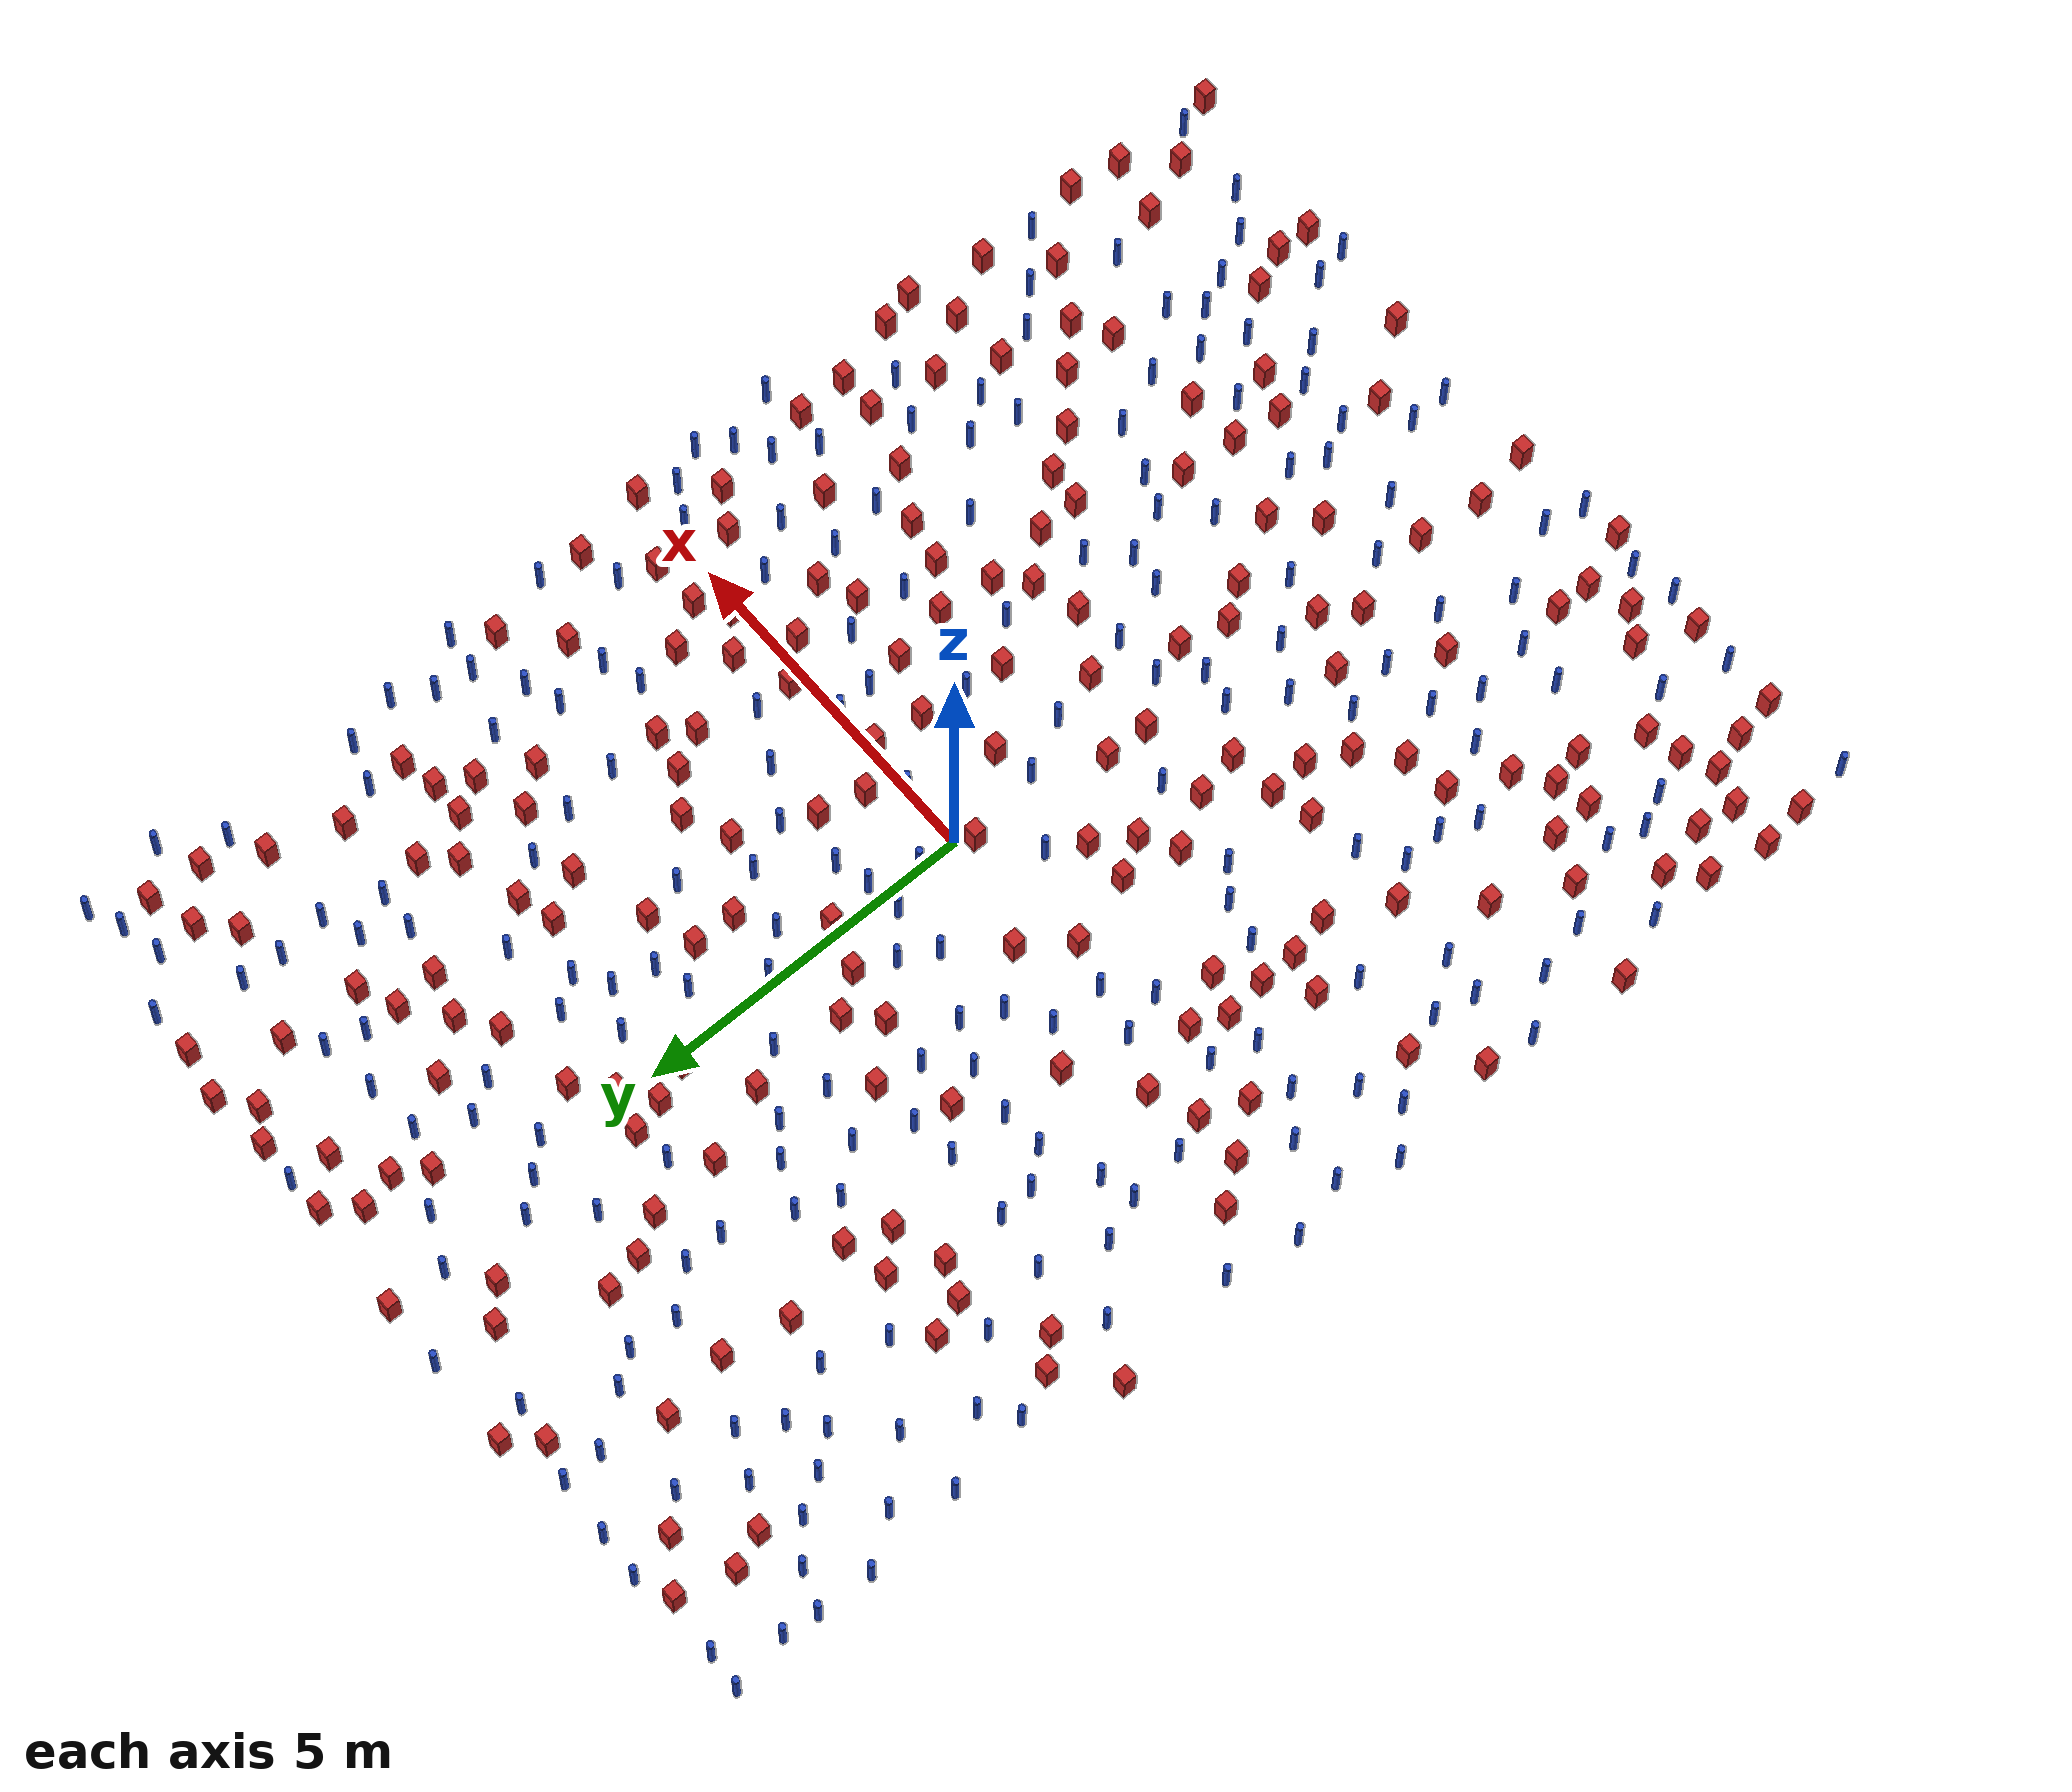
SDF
<sdf version="1.6">
  <model name="dense_95"><model name="pole_obstacle0">
  <static>true</static>
  <pose frame="">2.38550247852 -6.84949095472 -9.47619616065e-06 5.49618799738e-07 2.3631041406e-07 -1.55090534801e-07</pose>
  <link name="link">
  <pose frame="">0 0 0.3 0 -0 0</pose>
    <inertial>
      <mass>1</mass>
      <inertia>
        <ixx>0.145833</ixx>
        <ixy>0</ixy>
        <ixz>0</ixz>
        <iyy>0.145833</iyy>
        <iyz>0</iyz>
        <izz>0.125</izz>
      </inertia>
    </inertial>
    <collision name="collision">
      <geometry>
        <cylinder>
          <radius>0.05</radius>
          <length>.6</length>
        </cylinder>
      </geometry>
      <max_contacts>10</max_contacts>
      <surface>
        <contact>
          <ode/>
        </contact>
        <bounce/>
        <friction>
          <torsional>
            <ode/>
          </torsional>
          <ode/>
        </friction>
      </surface>
    </collision>
    <visual name="visual">
      <geometry>
        <cylinder>
          <radius>0.05</radius>
          <length>.6</length>
        </cylinder>
      </geometry>
      <material>
        <script>
          <name>Gazebo/Blue</name>
          <uri>file://media/materials/scripts/gazebo.material</uri>
        </script>
      </material>
    </visual>
    <self_collide>0</self_collide>
    <kinematic>0</kinematic>
  </link>
</model>
<model name="pole_obstacle1">
  <static>true</static>
  <pose frame="">-1.74383481891 -5.81777076691 -9.47619616065e-06 5.49618799737e-07 2.36310414061e-07 -1.550905348e-07</pose>
  <link name="link">
  <pose frame="">0 0 0.3 0 -0 0</pose>
    <inertial>
      <mass>1</mass>
      <inertia>
        <ixx>0.145833</ixx>
        <ixy>0</ixy>
        <ixz>0</ixz>
        <iyy>0.145833</iyy>
        <iyz>0</iyz>
        <izz>0.125</izz>
      </inertia>
    </inertial>
    <collision name="collision">
      <geometry>
        <cylinder>
          <radius>0.05</radius>
          <length>.6</length>
        </cylinder>
      </geometry>
      <max_contacts>10</max_contacts>
      <surface>
        <contact>
          <ode/>
        </contact>
        <bounce/>
        <friction>
          <torsional>
            <ode/>
          </torsional>
          <ode/>
        </friction>
      </surface>
    </collision>
    <visual name="visual">
      <geometry>
        <cylinder>
          <radius>0.05</radius>
          <length>.6</length>
        </cylinder>
      </geometry>
      <material>
        <script>
          <name>Gazebo/Blue</name>
          <uri>file://media/materials/scripts/gazebo.material</uri>
        </script>
      </material>
    </visual>
    <self_collide>0</self_collide>
    <kinematic>0</kinematic>
  </link>
</model>
<model name="square_post_obstacle0">
  <static>true</static>
  <pose frame="">-6.75557318525 -7.88863888471 -6.11067671241e-07 -5.50515727128e-06 -8.79689657224e-07 2.37013304536e-05</pose>
  <link name="link">
    <pose frame="">0 0 0.25 0 -0 0</pose>
    <inertial>
      <mass>100</mass>
      <inertia>
        <ixx>0.166667</ixx>
        <ixy>0</ixy>
        <ixz>0</ixz>
        <iyy>0.166667</iyy>
        <iyz>0</iyz>
        <izz>0.166667</izz>
      </inertia>
    </inertial>
    <collision name="collision">
      <geometry>
        <box>
          <size>.2 .2 .5</size>
        </box>
      </geometry>
      <max_contacts>10</max_contacts>
      <surface>
        <contact>
          <ode/>
        </contact>
        <bounce/>
        <friction>
          <torsional>
            <ode/>
          </torsional>
          <ode/>
        </friction>
      </surface>
    </collision>
    <visual name="visual">
      <geometry>
        <box>
          <size>.2 .2 .5</size>
        </box>
      </geometry>
      <material>
        <script>
          <name>Gazebo/Red</name>
          <uri>file://media/materials/scripts/gazebo.material</uri>
        </script>
      </material>
    </visual>
    <self_collide>0</self_collide>
    <kinematic>0</kinematic>
  </link>
</model>
<model name="square_post_obstacle1">
  <static>true</static>
  <pose frame="">3.79219222096 0.554203007077 -6.11067671241e-07 -5.50515727128e-06 -8.79689657224e-07 2.37013304536e-05</pose>
  <link name="link">
    <pose frame="">0 0 0.25 0 -0 0</pose>
    <inertial>
      <mass>100</mass>
      <inertia>
        <ixx>0.166667</ixx>
        <ixy>0</ixy>
        <ixz>0</ixz>
        <iyy>0.166667</iyy>
        <iyz>0</iyz>
        <izz>0.166667</izz>
      </inertia>
    </inertial>
    <collision name="collision">
      <geometry>
        <box>
          <size>.2 .2 .5</size>
        </box>
      </geometry>
      <max_contacts>10</max_contacts>
      <surface>
        <contact>
          <ode/>
        </contact>
        <bounce/>
        <friction>
          <torsional>
            <ode/>
          </torsional>
          <ode/>
        </friction>
      </surface>
    </collision>
    <visual name="visual">
      <geometry>
        <box>
          <size>.2 .2 .5</size>
        </box>
      </geometry>
      <material>
        <script>
          <name>Gazebo/Red</name>
          <uri>file://media/materials/scripts/gazebo.material</uri>
        </script>
      </material>
    </visual>
    <self_collide>0</self_collide>
    <kinematic>0</kinematic>
  </link>
</model>
<model name="pole_obstacle2">
  <static>true</static>
  <pose frame="">-3.29904174645 2.82377356192 -9.47619616065e-06 5.49618799737e-07 2.36310414051e-07 -1.55090534807e-07</pose>
  <link name="link">
  <pose frame="">0 0 0.3 0 -0 0</pose>
    <inertial>
      <mass>1</mass>
      <inertia>
        <ixx>0.145833</ixx>
        <ixy>0</ixy>
        <ixz>0</ixz>
        <iyy>0.145833</iyy>
        <iyz>0</iyz>
        <izz>0.125</izz>
      </inertia>
    </inertial>
    <collision name="collision">
      <geometry>
        <cylinder>
          <radius>0.05</radius>
          <length>.6</length>
        </cylinder>
      </geometry>
      <max_contacts>10</max_contacts>
      <surface>
        <contact>
          <ode/>
        </contact>
        <bounce/>
        <friction>
          <torsional>
            <ode/>
          </torsional>
          <ode/>
        </friction>
      </surface>
    </collision>
    <visual name="visual">
      <geometry>
        <cylinder>
          <radius>0.05</radius>
          <length>.6</length>
        </cylinder>
      </geometry>
      <material>
        <script>
          <name>Gazebo/Blue</name>
          <uri>file://media/materials/scripts/gazebo.material</uri>
        </script>
      </material>
    </visual>
    <self_collide>0</self_collide>
    <kinematic>0</kinematic>
  </link>
</model>
<model name="pole_obstacle3">
  <static>true</static>
  <pose frame="">-3.49241924509 8.64289006772 -9.4761961606e-06 5.49618799729e-07 2.36310414e-07 -1.55090534824e-07</pose>
  <link name="link">
  <pose frame="">0 0 0.3 0 -0 0</pose>
    <inertial>
      <mass>1</mass>
      <inertia>
        <ixx>0.145833</ixx>
        <ixy>0</ixy>
        <ixz>0</ixz>
        <iyy>0.145833</iyy>
        <iyz>0</iyz>
        <izz>0.125</izz>
      </inertia>
    </inertial>
    <collision name="collision">
      <geometry>
        <cylinder>
          <radius>0.05</radius>
          <length>.6</length>
        </cylinder>
      </geometry>
      <max_contacts>10</max_contacts>
      <surface>
        <contact>
          <ode/>
        </contact>
        <bounce/>
        <friction>
          <torsional>
            <ode/>
          </torsional>
          <ode/>
        </friction>
      </surface>
    </collision>
    <visual name="visual">
      <geometry>
        <cylinder>
          <radius>0.05</radius>
          <length>.6</length>
        </cylinder>
      </geometry>
      <material>
        <script>
          <name>Gazebo/Blue</name>
          <uri>file://media/materials/scripts/gazebo.material</uri>
        </script>
      </material>
    </visual>
    <self_collide>0</self_collide>
    <kinematic>0</kinematic>
  </link>
</model>
<model name="pole_obstacle4">
  <static>true</static>
  <pose frame="">4.79706785582 1.914005729 -9.47619616065e-06 5.49618799738e-07 2.36310414071e-07 -1.55090534796e-07</pose>
  <link name="link">
  <pose frame="">0 0 0.3 0 -0 0</pose>
    <inertial>
      <mass>1</mass>
      <inertia>
        <ixx>0.145833</ixx>
        <ixy>0</ixy>
        <ixz>0</ixz>
        <iyy>0.145833</iyy>
        <iyz>0</iyz>
        <izz>0.125</izz>
      </inertia>
    </inertial>
    <collision name="collision">
      <geometry>
        <cylinder>
          <radius>0.05</radius>
          <length>.6</length>
        </cylinder>
      </geometry>
      <max_contacts>10</max_contacts>
      <surface>
        <contact>
          <ode/>
        </contact>
        <bounce/>
        <friction>
          <torsional>
            <ode/>
          </torsional>
          <ode/>
        </friction>
      </surface>
    </collision>
    <visual name="visual">
      <geometry>
        <cylinder>
          <radius>0.05</radius>
          <length>.6</length>
        </cylinder>
      </geometry>
      <material>
        <script>
          <name>Gazebo/Blue</name>
          <uri>file://media/materials/scripts/gazebo.material</uri>
        </script>
      </material>
    </visual>
    <self_collide>0</self_collide>
    <kinematic>0</kinematic>
  </link>
</model>
<model name="pole_obstacle5">
  <static>true</static>
  <pose frame="">5.98320436551 7.11460259568 -9.47619616065e-06 5.49618799737e-07 2.36310414037e-07 -1.55090534814e-07</pose>
  <link name="link">
  <pose frame="">0 0 0.3 0 -0 0</pose>
    <inertial>
      <mass>1</mass>
      <inertia>
        <ixx>0.145833</ixx>
        <ixy>0</ixy>
        <ixz>0</ixz>
        <iyy>0.145833</iyy>
        <iyz>0</iyz>
        <izz>0.125</izz>
      </inertia>
    </inertial>
    <collision name="collision">
      <geometry>
        <cylinder>
          <radius>0.05</radius>
          <length>.6</length>
        </cylinder>
      </geometry>
      <max_contacts>10</max_contacts>
      <surface>
        <contact>
          <ode/>
        </contact>
        <bounce/>
        <friction>
          <torsional>
            <ode/>
          </torsional>
          <ode/>
        </friction>
      </surface>
    </collision>
    <visual name="visual">
      <geometry>
        <cylinder>
          <radius>0.05</radius>
          <length>.6</length>
        </cylinder>
      </geometry>
      <material>
        <script>
          <name>Gazebo/Blue</name>
          <uri>file://media/materials/scripts/gazebo.material</uri>
        </script>
      </material>
    </visual>
    <self_collide>0</self_collide>
    <kinematic>0</kinematic>
  </link>
</model>
<model name="pole_obstacle6">
  <static>true</static>
  <pose frame="">0.0274219463707 0.570744729597 -9.47619616065e-06 5.49618799737e-07 2.36310414052e-07 -1.55090534805e-07</pose>
  <link name="link">
  <pose frame="">0 0 0.3 0 -0 0</pose>
    <inertial>
      <mass>1</mass>
      <inertia>
        <ixx>0.145833</ixx>
        <ixy>0</ixy>
        <ixz>0</ixz>
        <iyy>0.145833</iyy>
        <iyz>0</iyz>
        <izz>0.125</izz>
      </inertia>
    </inertial>
    <collision name="collision">
      <geometry>
        <cylinder>
          <radius>0.05</radius>
          <length>.6</length>
        </cylinder>
      </geometry>
      <max_contacts>10</max_contacts>
      <surface>
        <contact>
          <ode/>
        </contact>
        <bounce/>
        <friction>
          <torsional>
            <ode/>
          </torsional>
          <ode/>
        </friction>
      </surface>
    </collision>
    <visual name="visual">
      <geometry>
        <cylinder>
          <radius>0.05</radius>
          <length>.6</length>
        </cylinder>
      </geometry>
      <material>
        <script>
          <name>Gazebo/Blue</name>
          <uri>file://media/materials/scripts/gazebo.material</uri>
        </script>
      </material>
    </visual>
    <self_collide>0</self_collide>
    <kinematic>0</kinematic>
  </link>
</model>
<model name="square_post_obstacle2">
  <static>true</static>
  <pose frame="">-0.159925843453 4.62938258808 -6.11067671241e-07 -5.50515727128e-06 -8.79689657224e-07 2.37013304536e-05</pose>
  <link name="link">
    <pose frame="">0 0 0.25 0 -0 0</pose>
    <inertial>
      <mass>100</mass>
      <inertia>
        <ixx>0.166667</ixx>
        <ixy>0</ixy>
        <ixz>0</ixz>
        <iyy>0.166667</iyy>
        <iyz>0</iyz>
        <izz>0.166667</izz>
      </inertia>
    </inertial>
    <collision name="collision">
      <geometry>
        <box>
          <size>.2 .2 .5</size>
        </box>
      </geometry>
      <max_contacts>10</max_contacts>
      <surface>
        <contact>
          <ode/>
        </contact>
        <bounce/>
        <friction>
          <torsional>
            <ode/>
          </torsional>
          <ode/>
        </friction>
      </surface>
    </collision>
    <visual name="visual">
      <geometry>
        <box>
          <size>.2 .2 .5</size>
        </box>
      </geometry>
      <material>
        <script>
          <name>Gazebo/Red</name>
          <uri>file://media/materials/scripts/gazebo.material</uri>
        </script>
      </material>
    </visual>
    <self_collide>0</self_collide>
    <kinematic>0</kinematic>
  </link>
</model>
<model name="square_post_obstacle3">
  <static>true</static>
  <pose frame="">0.353442843421 -6.57402846743 -6.11067671241e-07 -5.50515727128e-06 -8.79689657224e-07 2.37013304536e-05</pose>
  <link name="link">
    <pose frame="">0 0 0.25 0 -0 0</pose>
    <inertial>
      <mass>100</mass>
      <inertia>
        <ixx>0.166667</ixx>
        <ixy>0</ixy>
        <ixz>0</ixz>
        <iyy>0.166667</iyy>
        <iyz>0</iyz>
        <izz>0.166667</izz>
      </inertia>
    </inertial>
    <collision name="collision">
      <geometry>
        <box>
          <size>.2 .2 .5</size>
        </box>
      </geometry>
      <max_contacts>10</max_contacts>
      <surface>
        <contact>
          <ode/>
        </contact>
        <bounce/>
        <friction>
          <torsional>
            <ode/>
          </torsional>
          <ode/>
        </friction>
      </surface>
    </collision>
    <visual name="visual">
      <geometry>
        <box>
          <size>.2 .2 .5</size>
        </box>
      </geometry>
      <material>
        <script>
          <name>Gazebo/Red</name>
          <uri>file://media/materials/scripts/gazebo.material</uri>
        </script>
      </material>
    </visual>
    <self_collide>0</self_collide>
    <kinematic>0</kinematic>
  </link>
</model>
<model name="square_post_obstacle4">
  <static>true</static>
  <pose frame="">4.3136634986 0.171121592858 -6.11067671241e-07 -5.50515727128e-06 -8.79689657224e-07 2.37013304536e-05</pose>
  <link name="link">
    <pose frame="">0 0 0.25 0 -0 0</pose>
    <inertial>
      <mass>100</mass>
      <inertia>
        <ixx>0.166667</ixx>
        <ixy>0</ixy>
        <ixz>0</ixz>
        <iyy>0.166667</iyy>
        <iyz>0</iyz>
        <izz>0.166667</izz>
      </inertia>
    </inertial>
    <collision name="collision">
      <geometry>
        <box>
          <size>.2 .2 .5</size>
        </box>
      </geometry>
      <max_contacts>10</max_contacts>
      <surface>
        <contact>
          <ode/>
        </contact>
        <bounce/>
        <friction>
          <torsional>
            <ode/>
          </torsional>
          <ode/>
        </friction>
      </surface>
    </collision>
    <visual name="visual">
      <geometry>
        <box>
          <size>.2 .2 .5</size>
        </box>
      </geometry>
      <material>
        <script>
          <name>Gazebo/Red</name>
          <uri>file://media/materials/scripts/gazebo.material</uri>
        </script>
      </material>
    </visual>
    <self_collide>0</self_collide>
    <kinematic>0</kinematic>
  </link>
</model>
<model name="pole_obstacle7">
  <static>true</static>
  <pose frame="">4.22786725258 -3.81274407793 -9.47619616065e-06 5.49618799738e-07 2.36310414051e-07 -1.55090534805e-07</pose>
  <link name="link">
  <pose frame="">0 0 0.3 0 -0 0</pose>
    <inertial>
      <mass>1</mass>
      <inertia>
        <ixx>0.145833</ixx>
        <ixy>0</ixy>
        <ixz>0</ixz>
        <iyy>0.145833</iyy>
        <iyz>0</iyz>
        <izz>0.125</izz>
      </inertia>
    </inertial>
    <collision name="collision">
      <geometry>
        <cylinder>
          <radius>0.05</radius>
          <length>.6</length>
        </cylinder>
      </geometry>
      <max_contacts>10</max_contacts>
      <surface>
        <contact>
          <ode/>
        </contact>
        <bounce/>
        <friction>
          <torsional>
            <ode/>
          </torsional>
          <ode/>
        </friction>
      </surface>
    </collision>
    <visual name="visual">
      <geometry>
        <cylinder>
          <radius>0.05</radius>
          <length>.6</length>
        </cylinder>
      </geometry>
      <material>
        <script>
          <name>Gazebo/Blue</name>
          <uri>file://media/materials/scripts/gazebo.material</uri>
        </script>
      </material>
    </visual>
    <self_collide>0</self_collide>
    <kinematic>0</kinematic>
  </link>
</model>
<model name="pole_obstacle8">
  <static>true</static>
  <pose frame="">0.0516490565058 -1.32433108705 -9.47619616065e-06 5.49618799737e-07 2.36310414058e-07 -1.55090534802e-07</pose>
  <link name="link">
  <pose frame="">0 0 0.3 0 -0 0</pose>
    <inertial>
      <mass>1</mass>
      <inertia>
        <ixx>0.145833</ixx>
        <ixy>0</ixy>
        <ixz>0</ixz>
        <iyy>0.145833</iyy>
        <iyz>0</iyz>
        <izz>0.125</izz>
      </inertia>
    </inertial>
    <collision name="collision">
      <geometry>
        <cylinder>
          <radius>0.05</radius>
          <length>.6</length>
        </cylinder>
      </geometry>
      <max_contacts>10</max_contacts>
      <surface>
        <contact>
          <ode/>
        </contact>
        <bounce/>
        <friction>
          <torsional>
            <ode/>
          </torsional>
          <ode/>
        </friction>
      </surface>
    </collision>
    <visual name="visual">
      <geometry>
        <cylinder>
          <radius>0.05</radius>
          <length>.6</length>
        </cylinder>
      </geometry>
      <material>
        <script>
          <name>Gazebo/Blue</name>
          <uri>file://media/materials/scripts/gazebo.material</uri>
        </script>
      </material>
    </visual>
    <self_collide>0</self_collide>
    <kinematic>0</kinematic>
  </link>
</model>
<model name="square_post_obstacle5">
  <static>true</static>
  <pose frame="">-3.9854556067 4.46820223153 -6.11067671241e-07 -5.50515727128e-06 -8.79689657224e-07 2.37013304536e-05</pose>
  <link name="link">
    <pose frame="">0 0 0.25 0 -0 0</pose>
    <inertial>
      <mass>100</mass>
      <inertia>
        <ixx>0.166667</ixx>
        <ixy>0</ixy>
        <ixz>0</ixz>
        <iyy>0.166667</iyy>
        <iyz>0</iyz>
        <izz>0.166667</izz>
      </inertia>
    </inertial>
    <collision name="collision">
      <geometry>
        <box>
          <size>.2 .2 .5</size>
        </box>
      </geometry>
      <max_contacts>10</max_contacts>
      <surface>
        <contact>
          <ode/>
        </contact>
        <bounce/>
        <friction>
          <torsional>
            <ode/>
          </torsional>
          <ode/>
        </friction>
      </surface>
    </collision>
    <visual name="visual">
      <geometry>
        <box>
          <size>.2 .2 .5</size>
        </box>
      </geometry>
      <material>
        <script>
          <name>Gazebo/Red</name>
          <uri>file://media/materials/scripts/gazebo.material</uri>
        </script>
      </material>
    </visual>
    <self_collide>0</self_collide>
    <kinematic>0</kinematic>
  </link>
</model>
<model name="square_post_obstacle6">
  <static>true</static>
  <pose frame="">1.92498587914 -9.22740684183 -6.11067671241e-07 -5.50515727128e-06 -8.79689657224e-07 2.37013304536e-05</pose>
  <link name="link">
    <pose frame="">0 0 0.25 0 -0 0</pose>
    <inertial>
      <mass>100</mass>
      <inertia>
        <ixx>0.166667</ixx>
        <ixy>0</ixy>
        <ixz>0</ixz>
        <iyy>0.166667</iyy>
        <iyz>0</iyz>
        <izz>0.166667</izz>
      </inertia>
    </inertial>
    <collision name="collision">
      <geometry>
        <box>
          <size>.2 .2 .5</size>
        </box>
      </geometry>
      <max_contacts>10</max_contacts>
      <surface>
        <contact>
          <ode/>
        </contact>
        <bounce/>
        <friction>
          <torsional>
            <ode/>
          </torsional>
          <ode/>
        </friction>
      </surface>
    </collision>
    <visual name="visual">
      <geometry>
        <box>
          <size>.2 .2 .5</size>
        </box>
      </geometry>
      <material>
        <script>
          <name>Gazebo/Red</name>
          <uri>file://media/materials/scripts/gazebo.material</uri>
        </script>
      </material>
    </visual>
    <self_collide>0</self_collide>
    <kinematic>0</kinematic>
  </link>
</model>
<model name="square_post_obstacle7">
  <static>true</static>
  <pose frame="">3.69805389555 -9.23047519515 -6.11067671241e-07 -5.50515727128e-06 -8.79689657224e-07 2.37013304536e-05</pose>
  <link name="link">
    <pose frame="">0 0 0.25 0 -0 0</pose>
    <inertial>
      <mass>100</mass>
      <inertia>
        <ixx>0.166667</ixx>
        <ixy>0</ixy>
        <ixz>0</ixz>
        <iyy>0.166667</iyy>
        <iyz>0</iyz>
        <izz>0.166667</izz>
      </inertia>
    </inertial>
    <collision name="collision">
      <geometry>
        <box>
          <size>.2 .2 .5</size>
        </box>
      </geometry>
      <max_contacts>10</max_contacts>
      <surface>
        <contact>
          <ode/>
        </contact>
        <bounce/>
        <friction>
          <torsional>
            <ode/>
          </torsional>
          <ode/>
        </friction>
      </surface>
    </collision>
    <visual name="visual">
      <geometry>
        <box>
          <size>.2 .2 .5</size>
        </box>
      </geometry>
      <material>
        <script>
          <name>Gazebo/Red</name>
          <uri>file://media/materials/scripts/gazebo.material</uri>
        </script>
      </material>
    </visual>
    <self_collide>0</self_collide>
    <kinematic>0</kinematic>
  </link>
</model>
<model name="pole_obstacle9">
  <static>true</static>
  <pose frame="">-4.48564536037 8.25483826058 -9.47619616065e-06 5.49618799737e-07 2.36310414065e-07 -1.55090534796e-07</pose>
  <link name="link">
  <pose frame="">0 0 0.3 0 -0 0</pose>
    <inertial>
      <mass>1</mass>
      <inertia>
        <ixx>0.145833</ixx>
        <ixy>0</ixy>
        <ixz>0</ixz>
        <iyy>0.145833</iyy>
        <iyz>0</iyz>
        <izz>0.125</izz>
      </inertia>
    </inertial>
    <collision name="collision">
      <geometry>
        <cylinder>
          <radius>0.05</radius>
          <length>.6</length>
        </cylinder>
      </geometry>
      <max_contacts>10</max_contacts>
      <surface>
        <contact>
          <ode/>
        </contact>
        <bounce/>
        <friction>
          <torsional>
            <ode/>
          </torsional>
          <ode/>
        </friction>
      </surface>
    </collision>
    <visual name="visual">
      <geometry>
        <cylinder>
          <radius>0.05</radius>
          <length>.6</length>
        </cylinder>
      </geometry>
      <material>
        <script>
          <name>Gazebo/Blue</name>
          <uri>file://media/materials/scripts/gazebo.material</uri>
        </script>
      </material>
    </visual>
    <self_collide>0</self_collide>
    <kinematic>0</kinematic>
  </link>
</model>
<model name="pole_obstacle10">
  <static>true</static>
  <pose frame="">-2.93135055371 -2.09699757997 -9.47619616065e-06 5.49618799737e-07 2.36310414051e-07 -1.55090534807e-07</pose>
  <link name="link">
  <pose frame="">0 0 0.3 0 -0 0</pose>
    <inertial>
      <mass>1</mass>
      <inertia>
        <ixx>0.145833</ixx>
        <ixy>0</ixy>
        <ixz>0</ixz>
        <iyy>0.145833</iyy>
        <iyz>0</iyz>
        <izz>0.125</izz>
      </inertia>
    </inertial>
    <collision name="collision">
      <geometry>
        <cylinder>
          <radius>0.05</radius>
          <length>.6</length>
        </cylinder>
      </geometry>
      <max_contacts>10</max_contacts>
      <surface>
        <contact>
          <ode/>
        </contact>
        <bounce/>
        <friction>
          <torsional>
            <ode/>
          </torsional>
          <ode/>
        </friction>
      </surface>
    </collision>
    <visual name="visual">
      <geometry>
        <cylinder>
          <radius>0.05</radius>
          <length>.6</length>
        </cylinder>
      </geometry>
      <material>
        <script>
          <name>Gazebo/Blue</name>
          <uri>file://media/materials/scripts/gazebo.material</uri>
        </script>
      </material>
    </visual>
    <self_collide>0</self_collide>
    <kinematic>0</kinematic>
  </link>
</model>
<model name="pole_obstacle11">
  <static>true</static>
  <pose frame="">5.88051444099 3.81446614888 -9.47619616065e-06 5.49618799738e-07 2.36310414051e-07 -1.55090534805e-07</pose>
  <link name="link">
  <pose frame="">0 0 0.3 0 -0 0</pose>
    <inertial>
      <mass>1</mass>
      <inertia>
        <ixx>0.145833</ixx>
        <ixy>0</ixy>
        <ixz>0</ixz>
        <iyy>0.145833</iyy>
        <iyz>0</iyz>
        <izz>0.125</izz>
      </inertia>
    </inertial>
    <collision name="collision">
      <geometry>
        <cylinder>
          <radius>0.05</radius>
          <length>.6</length>
        </cylinder>
      </geometry>
      <max_contacts>10</max_contacts>
      <surface>
        <contact>
          <ode/>
        </contact>
        <bounce/>
        <friction>
          <torsional>
            <ode/>
          </torsional>
          <ode/>
        </friction>
      </surface>
    </collision>
    <visual name="visual">
      <geometry>
        <cylinder>
          <radius>0.05</radius>
          <length>.6</length>
        </cylinder>
      </geometry>
      <material>
        <script>
          <name>Gazebo/Blue</name>
          <uri>file://media/materials/scripts/gazebo.material</uri>
        </script>
      </material>
    </visual>
    <self_collide>0</self_collide>
    <kinematic>0</kinematic>
  </link>
</model>
<model name="pole_obstacle12">
  <static>true</static>
  <pose frame="">4.89849430528 -1.15108140187 -9.47619616065e-06 5.49618799738e-07 2.36310414071e-07 -1.55090534796e-07</pose>
  <link name="link">
  <pose frame="">0 0 0.3 0 -0 0</pose>
    <inertial>
      <mass>1</mass>
      <inertia>
        <ixx>0.145833</ixx>
        <ixy>0</ixy>
        <ixz>0</ixz>
        <iyy>0.145833</iyy>
        <iyz>0</iyz>
        <izz>0.125</izz>
      </inertia>
    </inertial>
    <collision name="collision">
      <geometry>
        <cylinder>
          <radius>0.05</radius>
          <length>.6</length>
        </cylinder>
      </geometry>
      <max_contacts>10</max_contacts>
      <surface>
        <contact>
          <ode/>
        </contact>
        <bounce/>
        <friction>
          <torsional>
            <ode/>
          </torsional>
          <ode/>
        </friction>
      </surface>
    </collision>
    <visual name="visual">
      <geometry>
        <cylinder>
          <radius>0.05</radius>
          <length>.6</length>
        </cylinder>
      </geometry>
      <material>
        <script>
          <name>Gazebo/Blue</name>
          <uri>file://media/materials/scripts/gazebo.material</uri>
        </script>
      </material>
    </visual>
    <self_collide>0</self_collide>
    <kinematic>0</kinematic>
  </link>
</model>
<model name="square_post_obstacle8">
  <static>true</static>
  <pose frame="">2.80304311402 6.26431948631 -6.11067671241e-07 -5.50515727128e-06 -8.79689657224e-07 2.37013304536e-05</pose>
  <link name="link">
    <pose frame="">0 0 0.25 0 -0 0</pose>
    <inertial>
      <mass>100</mass>
      <inertia>
        <ixx>0.166667</ixx>
        <ixy>0</ixy>
        <ixz>0</ixz>
        <iyy>0.166667</iyy>
        <iyz>0</iyz>
        <izz>0.166667</izz>
      </inertia>
    </inertial>
    <collision name="collision">
      <geometry>
        <box>
          <size>.2 .2 .5</size>
        </box>
      </geometry>
      <max_contacts>10</max_contacts>
      <surface>
        <contact>
          <ode/>
        </contact>
        <bounce/>
        <friction>
          <torsional>
            <ode/>
          </torsional>
          <ode/>
        </friction>
      </surface>
    </collision>
    <visual name="visual">
      <geometry>
        <box>
          <size>.2 .2 .5</size>
        </box>
      </geometry>
      <material>
        <script>
          <name>Gazebo/Red</name>
          <uri>file://media/materials/scripts/gazebo.material</uri>
        </script>
      </material>
    </visual>
    <self_collide>0</self_collide>
    <kinematic>0</kinematic>
  </link>
</model>
<model name="square_post_obstacle9">
  <static>true</static>
  <pose frame="">5.47112627486 -6.36374514574 -6.11067671241e-07 -5.50515727128e-06 -8.79689657224e-07 2.37013304536e-05</pose>
  <link name="link">
    <pose frame="">0 0 0.25 0 -0 0</pose>
    <inertial>
      <mass>100</mass>
      <inertia>
        <ixx>0.166667</ixx>
        <ixy>0</ixy>
        <ixz>0</ixz>
        <iyy>0.166667</iyy>
        <iyz>0</iyz>
        <izz>0.166667</izz>
      </inertia>
    </inertial>
    <collision name="collision">
      <geometry>
        <box>
          <size>.2 .2 .5</size>
        </box>
      </geometry>
      <max_contacts>10</max_contacts>
      <surface>
        <contact>
          <ode/>
        </contact>
        <bounce/>
        <friction>
          <torsional>
            <ode/>
          </torsional>
          <ode/>
        </friction>
      </surface>
    </collision>
    <visual name="visual">
      <geometry>
        <box>
          <size>.2 .2 .5</size>
        </box>
      </geometry>
      <material>
        <script>
          <name>Gazebo/Red</name>
          <uri>file://media/materials/scripts/gazebo.material</uri>
        </script>
      </material>
    </visual>
    <self_collide>0</self_collide>
    <kinematic>0</kinematic>
  </link>
</model>
<model name="pole_obstacle13">
  <static>true</static>
  <pose frame="">-2.6742493743 -7.34877524434 -9.47619616065e-06 5.49618799738e-07 2.3631041406e-07 -1.55090534801e-07</pose>
  <link name="link">
  <pose frame="">0 0 0.3 0 -0 0</pose>
    <inertial>
      <mass>1</mass>
      <inertia>
        <ixx>0.145833</ixx>
        <ixy>0</ixy>
        <ixz>0</ixz>
        <iyy>0.145833</iyy>
        <iyz>0</iyz>
        <izz>0.125</izz>
      </inertia>
    </inertial>
    <collision name="collision">
      <geometry>
        <cylinder>
          <radius>0.05</radius>
          <length>.6</length>
        </cylinder>
      </geometry>
      <max_contacts>10</max_contacts>
      <surface>
        <contact>
          <ode/>
        </contact>
        <bounce/>
        <friction>
          <torsional>
            <ode/>
          </torsional>
          <ode/>
        </friction>
      </surface>
    </collision>
    <visual name="visual">
      <geometry>
        <cylinder>
          <radius>0.05</radius>
          <length>.6</length>
        </cylinder>
      </geometry>
      <material>
        <script>
          <name>Gazebo/Blue</name>
          <uri>file://media/materials/scripts/gazebo.material</uri>
        </script>
      </material>
    </visual>
    <self_collide>0</self_collide>
    <kinematic>0</kinematic>
  </link>
</model>
<model name="square_post_obstacle10">
  <static>true</static>
  <pose frame="">3.98002741322 9.29334098862 -6.11067671241e-07 -5.50515727128e-06 -8.79689657224e-07 2.37013304536e-05</pose>
  <link name="link">
    <pose frame="">0 0 0.25 0 -0 0</pose>
    <inertial>
      <mass>100</mass>
      <inertia>
        <ixx>0.166667</ixx>
        <ixy>0</ixy>
        <ixz>0</ixz>
        <iyy>0.166667</iyy>
        <iyz>0</iyz>
        <izz>0.166667</izz>
      </inertia>
    </inertial>
    <collision name="collision">
      <geometry>
        <box>
          <size>.2 .2 .5</size>
        </box>
      </geometry>
      <max_contacts>10</max_contacts>
      <surface>
        <contact>
          <ode/>
        </contact>
        <bounce/>
        <friction>
          <torsional>
            <ode/>
          </torsional>
          <ode/>
        </friction>
      </surface>
    </collision>
    <visual name="visual">
      <geometry>
        <box>
          <size>.2 .2 .5</size>
        </box>
      </geometry>
      <material>
        <script>
          <name>Gazebo/Red</name>
          <uri>file://media/materials/scripts/gazebo.material</uri>
        </script>
      </material>
    </visual>
    <self_collide>0</self_collide>
    <kinematic>0</kinematic>
  </link>
</model>
<model name="square_post_obstacle11">
  <static>true</static>
  <pose frame="">1.59132149544 -0.778273429128 -6.11067671241e-07 -5.50515727128e-06 -8.79689657224e-07 2.37013304536e-05</pose>
  <link name="link">
    <pose frame="">0 0 0.25 0 -0 0</pose>
    <inertial>
      <mass>100</mass>
      <inertia>
        <ixx>0.166667</ixx>
        <ixy>0</ixy>
        <ixz>0</ixz>
        <iyy>0.166667</iyy>
        <iyz>0</iyz>
        <izz>0.166667</izz>
      </inertia>
    </inertial>
    <collision name="collision">
      <geometry>
        <box>
          <size>.2 .2 .5</size>
        </box>
      </geometry>
      <max_contacts>10</max_contacts>
      <surface>
        <contact>
          <ode/>
        </contact>
        <bounce/>
        <friction>
          <torsional>
            <ode/>
          </torsional>
          <ode/>
        </friction>
      </surface>
    </collision>
    <visual name="visual">
      <geometry>
        <box>
          <size>.2 .2 .5</size>
        </box>
      </geometry>
      <material>
        <script>
          <name>Gazebo/Red</name>
          <uri>file://media/materials/scripts/gazebo.material</uri>
        </script>
      </material>
    </visual>
    <self_collide>0</self_collide>
    <kinematic>0</kinematic>
  </link>
</model>
<model name="pole_obstacle14">
  <static>true</static>
  <pose frame="">-2.76724626899 0.704654740037 -9.47619616065e-06 5.49618799738e-07 2.36310414075e-07 -1.55090534793e-07</pose>
  <link name="link">
  <pose frame="">0 0 0.3 0 -0 0</pose>
    <inertial>
      <mass>1</mass>
      <inertia>
        <ixx>0.145833</ixx>
        <ixy>0</ixy>
        <ixz>0</ixz>
        <iyy>0.145833</iyy>
        <iyz>0</iyz>
        <izz>0.125</izz>
      </inertia>
    </inertial>
    <collision name="collision">
      <geometry>
        <cylinder>
          <radius>0.05</radius>
          <length>.6</length>
        </cylinder>
      </geometry>
      <max_contacts>10</max_contacts>
      <surface>
        <contact>
          <ode/>
        </contact>
        <bounce/>
        <friction>
          <torsional>
            <ode/>
          </torsional>
          <ode/>
        </friction>
      </surface>
    </collision>
    <visual name="visual">
      <geometry>
        <cylinder>
          <radius>0.05</radius>
          <length>.6</length>
        </cylinder>
      </geometry>
      <material>
        <script>
          <name>Gazebo/Blue</name>
          <uri>file://media/materials/scripts/gazebo.material</uri>
        </script>
      </material>
    </visual>
    <self_collide>0</self_collide>
    <kinematic>0</kinematic>
  </link>
</model>
<model name="pole_obstacle15">
  <static>true</static>
  <pose frame="">6.15772433456 -1.38684801152 -9.47619616065e-06 5.49618799738e-07 2.36310414071e-07 -1.55090534796e-07</pose>
  <link name="link">
  <pose frame="">0 0 0.3 0 -0 0</pose>
    <inertial>
      <mass>1</mass>
      <inertia>
        <ixx>0.145833</ixx>
        <ixy>0</ixy>
        <ixz>0</ixz>
        <iyy>0.145833</iyy>
        <iyz>0</iyz>
        <izz>0.125</izz>
      </inertia>
    </inertial>
    <collision name="collision">
      <geometry>
        <cylinder>
          <radius>0.05</radius>
          <length>.6</length>
        </cylinder>
      </geometry>
      <max_contacts>10</max_contacts>
      <surface>
        <contact>
          <ode/>
        </contact>
        <bounce/>
        <friction>
          <torsional>
            <ode/>
          </torsional>
          <ode/>
        </friction>
      </surface>
    </collision>
    <visual name="visual">
      <geometry>
        <cylinder>
          <radius>0.05</radius>
          <length>.6</length>
        </cylinder>
      </geometry>
      <material>
        <script>
          <name>Gazebo/Blue</name>
          <uri>file://media/materials/scripts/gazebo.material</uri>
        </script>
      </material>
    </visual>
    <self_collide>0</self_collide>
    <kinematic>0</kinematic>
  </link>
</model>
<model name="square_post_obstacle12">
  <static>true</static>
  <pose frame="">-1.37454241037 8.5990074568 -6.11067671241e-07 -5.50515727128e-06 -8.79689657224e-07 2.37013304536e-05</pose>
  <link name="link">
    <pose frame="">0 0 0.25 0 -0 0</pose>
    <inertial>
      <mass>100</mass>
      <inertia>
        <ixx>0.166667</ixx>
        <ixy>0</ixy>
        <ixz>0</ixz>
        <iyy>0.166667</iyy>
        <iyz>0</iyz>
        <izz>0.166667</izz>
      </inertia>
    </inertial>
    <collision name="collision">
      <geometry>
        <box>
          <size>.2 .2 .5</size>
        </box>
      </geometry>
      <max_contacts>10</max_contacts>
      <surface>
        <contact>
          <ode/>
        </contact>
        <bounce/>
        <friction>
          <torsional>
            <ode/>
          </torsional>
          <ode/>
        </friction>
      </surface>
    </collision>
    <visual name="visual">
      <geometry>
        <box>
          <size>.2 .2 .5</size>
        </box>
      </geometry>
      <material>
        <script>
          <name>Gazebo/Red</name>
          <uri>file://media/materials/scripts/gazebo.material</uri>
        </script>
      </material>
    </visual>
    <self_collide>0</self_collide>
    <kinematic>0</kinematic>
  </link>
</model>
<model name="pole_obstacle16">
  <static>true</static>
  <pose frame="">-0.384769306161 8.63770552386 -9.47619616065e-06 5.49618799737e-07 2.36310414031e-07 -1.55090534818e-07</pose>
  <link name="link">
  <pose frame="">0 0 0.3 0 -0 0</pose>
    <inertial>
      <mass>1</mass>
      <inertia>
        <ixx>0.145833</ixx>
        <ixy>0</ixy>
        <ixz>0</ixz>
        <iyy>0.145833</iyy>
        <iyz>0</iyz>
        <izz>0.125</izz>
      </inertia>
    </inertial>
    <collision name="collision">
      <geometry>
        <cylinder>
          <radius>0.05</radius>
          <length>.6</length>
        </cylinder>
      </geometry>
      <max_contacts>10</max_contacts>
      <surface>
        <contact>
          <ode/>
        </contact>
        <bounce/>
        <friction>
          <torsional>
            <ode/>
          </torsional>
          <ode/>
        </friction>
      </surface>
    </collision>
    <visual name="visual">
      <geometry>
        <cylinder>
          <radius>0.05</radius>
          <length>.6</length>
        </cylinder>
      </geometry>
      <material>
        <script>
          <name>Gazebo/Blue</name>
          <uri>file://media/materials/scripts/gazebo.material</uri>
        </script>
      </material>
    </visual>
    <self_collide>0</self_collide>
    <kinematic>0</kinematic>
  </link>
</model>
<model name="pole_obstacle17">
  <static>true</static>
  <pose frame="">-6.03865940398 -5.28172877033 -9.47619616065e-06 5.49618799737e-07 2.36310414037e-07 -1.55090534814e-07</pose>
  <link name="link">
  <pose frame="">0 0 0.3 0 -0 0</pose>
    <inertial>
      <mass>1</mass>
      <inertia>
        <ixx>0.145833</ixx>
        <ixy>0</ixy>
        <ixz>0</ixz>
        <iyy>0.145833</iyy>
        <iyz>0</iyz>
        <izz>0.125</izz>
      </inertia>
    </inertial>
    <collision name="collision">
      <geometry>
        <cylinder>
          <radius>0.05</radius>
          <length>.6</length>
        </cylinder>
      </geometry>
      <max_contacts>10</max_contacts>
      <surface>
        <contact>
          <ode/>
        </contact>
        <bounce/>
        <friction>
          <torsional>
            <ode/>
          </torsional>
          <ode/>
        </friction>
      </surface>
    </collision>
    <visual name="visual">
      <geometry>
        <cylinder>
          <radius>0.05</radius>
          <length>.6</length>
        </cylinder>
      </geometry>
      <material>
        <script>
          <name>Gazebo/Blue</name>
          <uri>file://media/materials/scripts/gazebo.material</uri>
        </script>
      </material>
    </visual>
    <self_collide>0</self_collide>
    <kinematic>0</kinematic>
  </link>
</model>
<model name="square_post_obstacle13">
  <static>true</static>
  <pose frame="">2.63119987402 -4.26616733092 -6.11067671241e-07 -5.50515727128e-06 -8.79689657224e-07 2.37013304536e-05</pose>
  <link name="link">
    <pose frame="">0 0 0.25 0 -0 0</pose>
    <inertial>
      <mass>100</mass>
      <inertia>
        <ixx>0.166667</ixx>
        <ixy>0</ixy>
        <ixz>0</ixz>
        <iyy>0.166667</iyy>
        <iyz>0</iyz>
        <izz>0.166667</izz>
      </inertia>
    </inertial>
    <collision name="collision">
      <geometry>
        <box>
          <size>.2 .2 .5</size>
        </box>
      </geometry>
      <max_contacts>10</max_contacts>
      <surface>
        <contact>
          <ode/>
        </contact>
        <bounce/>
        <friction>
          <torsional>
            <ode/>
          </torsional>
          <ode/>
        </friction>
      </surface>
    </collision>
    <visual name="visual">
      <geometry>
        <box>
          <size>.2 .2 .5</size>
        </box>
      </geometry>
      <material>
        <script>
          <name>Gazebo/Red</name>
          <uri>file://media/materials/scripts/gazebo.material</uri>
        </script>
      </material>
    </visual>
    <self_collide>0</self_collide>
    <kinematic>0</kinematic>
  </link>
</model>
<model name="pole_obstacle18">
  <static>true</static>
  <pose frame="">-4.32444124397 7.1787579736 -9.47619616065e-06 5.49618799737e-07 2.36310414037e-07 -1.55090534814e-07</pose>
  <link name="link">
  <pose frame="">0 0 0.3 0 -0 0</pose>
    <inertial>
      <mass>1</mass>
      <inertia>
        <ixx>0.145833</ixx>
        <ixy>0</ixy>
        <ixz>0</ixz>
        <iyy>0.145833</iyy>
        <iyz>0</iyz>
        <izz>0.125</izz>
      </inertia>
    </inertial>
    <collision name="collision">
      <geometry>
        <cylinder>
          <radius>0.05</radius>
          <length>.6</length>
        </cylinder>
      </geometry>
      <max_contacts>10</max_contacts>
      <surface>
        <contact>
          <ode/>
        </contact>
        <bounce/>
        <friction>
          <torsional>
            <ode/>
          </torsional>
          <ode/>
        </friction>
      </surface>
    </collision>
    <visual name="visual">
      <geometry>
        <cylinder>
          <radius>0.05</radius>
          <length>.6</length>
        </cylinder>
      </geometry>
      <material>
        <script>
          <name>Gazebo/Blue</name>
          <uri>file://media/materials/scripts/gazebo.material</uri>
        </script>
      </material>
    </visual>
    <self_collide>0</self_collide>
    <kinematic>0</kinematic>
  </link>
</model>
<model name="square_post_obstacle14">
  <static>true</static>
  <pose frame="">3.52335067669 -4.87826846068 -6.11067671241e-07 -5.50515727128e-06 -8.79689657224e-07 2.37013304536e-05</pose>
  <link name="link">
    <pose frame="">0 0 0.25 0 -0 0</pose>
    <inertial>
      <mass>100</mass>
      <inertia>
        <ixx>0.166667</ixx>
        <ixy>0</ixy>
        <ixz>0</ixz>
        <iyy>0.166667</iyy>
        <iyz>0</iyz>
        <izz>0.166667</izz>
      </inertia>
    </inertial>
    <collision name="collision">
      <geometry>
        <box>
          <size>.2 .2 .5</size>
        </box>
      </geometry>
      <max_contacts>10</max_contacts>
      <surface>
        <contact>
          <ode/>
        </contact>
        <bounce/>
        <friction>
          <torsional>
            <ode/>
          </torsional>
          <ode/>
        </friction>
      </surface>
    </collision>
    <visual name="visual">
      <geometry>
        <box>
          <size>.2 .2 .5</size>
        </box>
      </geometry>
      <material>
        <script>
          <name>Gazebo/Red</name>
          <uri>file://media/materials/scripts/gazebo.material</uri>
        </script>
      </material>
    </visual>
    <self_collide>0</self_collide>
    <kinematic>0</kinematic>
  </link>
</model>
<model name="pole_obstacle19">
  <static>true</static>
  <pose frame="">-2.04132399361 -7.76574243721 -9.47619616065e-06 5.49618799737e-07 2.36310414067e-07 -1.55090534796e-07</pose>
  <link name="link">
  <pose frame="">0 0 0.3 0 -0 0</pose>
    <inertial>
      <mass>1</mass>
      <inertia>
        <ixx>0.145833</ixx>
        <ixy>0</ixy>
        <ixz>0</ixz>
        <iyy>0.145833</iyy>
        <iyz>0</iyz>
        <izz>0.125</izz>
      </inertia>
    </inertial>
    <collision name="collision">
      <geometry>
        <cylinder>
          <radius>0.05</radius>
          <length>.6</length>
        </cylinder>
      </geometry>
      <max_contacts>10</max_contacts>
      <surface>
        <contact>
          <ode/>
        </contact>
        <bounce/>
        <friction>
          <torsional>
            <ode/>
          </torsional>
          <ode/>
        </friction>
      </surface>
    </collision>
    <visual name="visual">
      <geometry>
        <cylinder>
          <radius>0.05</radius>
          <length>.6</length>
        </cylinder>
      </geometry>
      <material>
        <script>
          <name>Gazebo/Blue</name>
          <uri>file://media/materials/scripts/gazebo.material</uri>
        </script>
      </material>
    </visual>
    <self_collide>0</self_collide>
    <kinematic>0</kinematic>
  </link>
</model>
<model name="square_post_obstacle15">
  <static>true</static>
  <pose frame="">-1.43602810194 5.13662795015 -6.11067671241e-07 -5.50515727128e-06 -8.79689657224e-07 2.37013304536e-05</pose>
  <link name="link">
    <pose frame="">0 0 0.25 0 -0 0</pose>
    <inertial>
      <mass>100</mass>
      <inertia>
        <ixx>0.166667</ixx>
        <ixy>0</ixy>
        <ixz>0</ixz>
        <iyy>0.166667</iyy>
        <iyz>0</iyz>
        <izz>0.166667</izz>
      </inertia>
    </inertial>
    <collision name="collision">
      <geometry>
        <box>
          <size>.2 .2 .5</size>
        </box>
      </geometry>
      <max_contacts>10</max_contacts>
      <surface>
        <contact>
          <ode/>
        </contact>
        <bounce/>
        <friction>
          <torsional>
            <ode/>
          </torsional>
          <ode/>
        </friction>
      </surface>
    </collision>
    <visual name="visual">
      <geometry>
        <box>
          <size>.2 .2 .5</size>
        </box>
      </geometry>
      <material>
        <script>
          <name>Gazebo/Red</name>
          <uri>file://media/materials/scripts/gazebo.material</uri>
        </script>
      </material>
    </visual>
    <self_collide>0</self_collide>
    <kinematic>0</kinematic>
  </link>
</model>
<model name="square_post_obstacle16">
  <static>true</static>
  <pose frame="">4.32348105466 4.64907047005 -6.11067671241e-07 -5.50515727128e-06 -8.79689657224e-07 2.37013304536e-05</pose>
  <link name="link">
    <pose frame="">0 0 0.25 0 -0 0</pose>
    <inertial>
      <mass>100</mass>
      <inertia>
        <ixx>0.166667</ixx>
        <ixy>0</ixy>
        <ixz>0</ixz>
        <iyy>0.166667</iyy>
        <iyz>0</iyz>
        <izz>0.166667</izz>
      </inertia>
    </inertial>
    <collision name="collision">
      <geometry>
        <box>
          <size>.2 .2 .5</size>
        </box>
      </geometry>
      <max_contacts>10</max_contacts>
      <surface>
        <contact>
          <ode/>
        </contact>
        <bounce/>
        <friction>
          <torsional>
            <ode/>
          </torsional>
          <ode/>
        </friction>
      </surface>
    </collision>
    <visual name="visual">
      <geometry>
        <box>
          <size>.2 .2 .5</size>
        </box>
      </geometry>
      <material>
        <script>
          <name>Gazebo/Red</name>
          <uri>file://media/materials/scripts/gazebo.material</uri>
        </script>
      </material>
    </visual>
    <self_collide>0</self_collide>
    <kinematic>0</kinematic>
  </link>
</model>
<model name="square_post_obstacle17">
  <static>true</static>
  <pose frame="">0.998053957263 3.47318975611 -6.11067671241e-07 -5.50515727128e-06 -8.79689657224e-07 2.37013304536e-05</pose>
  <link name="link">
    <pose frame="">0 0 0.25 0 -0 0</pose>
    <inertial>
      <mass>100</mass>
      <inertia>
        <ixx>0.166667</ixx>
        <ixy>0</ixy>
        <ixz>0</ixz>
        <iyy>0.166667</iyy>
        <iyz>0</iyz>
        <izz>0.166667</izz>
      </inertia>
    </inertial>
    <collision name="collision">
      <geometry>
        <box>
          <size>.2 .2 .5</size>
        </box>
      </geometry>
      <max_contacts>10</max_contacts>
      <surface>
        <contact>
          <ode/>
        </contact>
        <bounce/>
        <friction>
          <torsional>
            <ode/>
          </torsional>
          <ode/>
        </friction>
      </surface>
    </collision>
    <visual name="visual">
      <geometry>
        <box>
          <size>.2 .2 .5</size>
        </box>
      </geometry>
      <material>
        <script>
          <name>Gazebo/Red</name>
          <uri>file://media/materials/scripts/gazebo.material</uri>
        </script>
      </material>
    </visual>
    <self_collide>0</self_collide>
    <kinematic>0</kinematic>
  </link>
</model>
<model name="pole_obstacle20">
  <static>true</static>
  <pose frame="">5.41964103082 -2.22877216106 -9.47619616065e-06 5.49618799738e-07 2.36310414051e-07 -1.55090534805e-07</pose>
  <link name="link">
  <pose frame="">0 0 0.3 0 -0 0</pose>
    <inertial>
      <mass>1</mass>
      <inertia>
        <ixx>0.145833</ixx>
        <ixy>0</ixy>
        <ixz>0</ixz>
        <iyy>0.145833</iyy>
        <iyz>0</iyz>
        <izz>0.125</izz>
      </inertia>
    </inertial>
    <collision name="collision">
      <geometry>
        <cylinder>
          <radius>0.05</radius>
          <length>.6</length>
        </cylinder>
      </geometry>
      <max_contacts>10</max_contacts>
      <surface>
        <contact>
          <ode/>
        </contact>
        <bounce/>
        <friction>
          <torsional>
            <ode/>
          </torsional>
          <ode/>
        </friction>
      </surface>
    </collision>
    <visual name="visual">
      <geometry>
        <cylinder>
          <radius>0.05</radius>
          <length>.6</length>
        </cylinder>
      </geometry>
      <material>
        <script>
          <name>Gazebo/Blue</name>
          <uri>file://media/materials/scripts/gazebo.material</uri>
        </script>
      </material>
    </visual>
    <self_collide>0</self_collide>
    <kinematic>0</kinematic>
  </link>
</model>
<model name="pole_obstacle21">
  <static>true</static>
  <pose frame="">-3.42657571255 -3.81951751165 -9.47619616065e-06 5.49618799737e-07 2.36310414051e-07 -1.55090534807e-07</pose>
  <link name="link">
  <pose frame="">0 0 0.3 0 -0 0</pose>
    <inertial>
      <mass>1</mass>
      <inertia>
        <ixx>0.145833</ixx>
        <ixy>0</ixy>
        <ixz>0</ixz>
        <iyy>0.145833</iyy>
        <iyz>0</iyz>
        <izz>0.125</izz>
      </inertia>
    </inertial>
    <collision name="collision">
      <geometry>
        <cylinder>
          <radius>0.05</radius>
          <length>.6</length>
        </cylinder>
      </geometry>
      <max_contacts>10</max_contacts>
      <surface>
        <contact>
          <ode/>
        </contact>
        <bounce/>
        <friction>
          <torsional>
            <ode/>
          </torsional>
          <ode/>
        </friction>
      </surface>
    </collision>
    <visual name="visual">
      <geometry>
        <cylinder>
          <radius>0.05</radius>
          <length>.6</length>
        </cylinder>
      </geometry>
      <material>
        <script>
          <name>Gazebo/Blue</name>
          <uri>file://media/materials/scripts/gazebo.material</uri>
        </script>
      </material>
    </visual>
    <self_collide>0</self_collide>
    <kinematic>0</kinematic>
  </link>
</model>
<model name="pole_obstacle22">
  <static>true</static>
  <pose frame="">2.28810434807 1.1677232516 -9.47619616065e-06 5.49618799737e-07 2.36310414072e-07 -1.55090534793e-07</pose>
  <link name="link">
  <pose frame="">0 0 0.3 0 -0 0</pose>
    <inertial>
      <mass>1</mass>
      <inertia>
        <ixx>0.145833</ixx>
        <ixy>0</ixy>
        <ixz>0</ixz>
        <iyy>0.145833</iyy>
        <iyz>0</iyz>
        <izz>0.125</izz>
      </inertia>
    </inertial>
    <collision name="collision">
      <geometry>
        <cylinder>
          <radius>0.05</radius>
          <length>.6</length>
        </cylinder>
      </geometry>
      <max_contacts>10</max_contacts>
      <surface>
        <contact>
          <ode/>
        </contact>
        <bounce/>
        <friction>
          <torsional>
            <ode/>
          </torsional>
          <ode/>
        </friction>
      </surface>
    </collision>
    <visual name="visual">
      <geometry>
        <cylinder>
          <radius>0.05</radius>
          <length>.6</length>
        </cylinder>
      </geometry>
      <material>
        <script>
          <name>Gazebo/Blue</name>
          <uri>file://media/materials/scripts/gazebo.material</uri>
        </script>
      </material>
    </visual>
    <self_collide>0</self_collide>
    <kinematic>0</kinematic>
  </link>
</model>
<model name="pole_obstacle23">
  <static>true</static>
  <pose frame="">-1.97185046986 4.5103314943 -9.47619616065e-06 5.49618799737e-07 2.36310414064e-07 -1.55090534797e-07</pose>
  <link name="link">
  <pose frame="">0 0 0.3 0 -0 0</pose>
    <inertial>
      <mass>1</mass>
      <inertia>
        <ixx>0.145833</ixx>
        <ixy>0</ixy>
        <ixz>0</ixz>
        <iyy>0.145833</iyy>
        <iyz>0</iyz>
        <izz>0.125</izz>
      </inertia>
    </inertial>
    <collision name="collision">
      <geometry>
        <cylinder>
          <radius>0.05</radius>
          <length>.6</length>
        </cylinder>
      </geometry>
      <max_contacts>10</max_contacts>
      <surface>
        <contact>
          <ode/>
        </contact>
        <bounce/>
        <friction>
          <torsional>
            <ode/>
          </torsional>
          <ode/>
        </friction>
      </surface>
    </collision>
    <visual name="visual">
      <geometry>
        <cylinder>
          <radius>0.05</radius>
          <length>.6</length>
        </cylinder>
      </geometry>
      <material>
        <script>
          <name>Gazebo/Blue</name>
          <uri>file://media/materials/scripts/gazebo.material</uri>
        </script>
      </material>
    </visual>
    <self_collide>0</self_collide>
    <kinematic>0</kinematic>
  </link>
</model>
<model name="square_post_obstacle18">
  <static>true</static>
  <pose frame="">1.68184939918 3.69530284069 -6.11067671241e-07 -5.50515727128e-06 -8.79689657224e-07 2.37013304536e-05</pose>
  <link name="link">
    <pose frame="">0 0 0.25 0 -0 0</pose>
    <inertial>
      <mass>100</mass>
      <inertia>
        <ixx>0.166667</ixx>
        <ixy>0</ixy>
        <ixz>0</ixz>
        <iyy>0.166667</iyy>
        <iyz>0</iyz>
        <izz>0.166667</izz>
      </inertia>
    </inertial>
    <collision name="collision">
      <geometry>
        <box>
          <size>.2 .2 .5</size>
        </box>
      </geometry>
      <max_contacts>10</max_contacts>
      <surface>
        <contact>
          <ode/>
        </contact>
        <bounce/>
        <friction>
          <torsional>
            <ode/>
          </torsional>
          <ode/>
        </friction>
      </surface>
    </collision>
    <visual name="visual">
      <geometry>
        <box>
          <size>.2 .2 .5</size>
        </box>
      </geometry>
      <material>
        <script>
          <name>Gazebo/Red</name>
          <uri>file://media/materials/scripts/gazebo.material</uri>
        </script>
      </material>
    </visual>
    <self_collide>0</self_collide>
    <kinematic>0</kinematic>
  </link>
</model>
<model name="pole_obstacle24">
  <static>true</static>
  <pose frame="">4.22378976199 -8.48527115542 -9.47619616065e-06 5.49618799737e-07 2.36310414065e-07 -1.55090534796e-07</pose>
  <link name="link">
  <pose frame="">0 0 0.3 0 -0 0</pose>
    <inertial>
      <mass>1</mass>
      <inertia>
        <ixx>0.145833</ixx>
        <ixy>0</ixy>
        <ixz>0</ixz>
        <iyy>0.145833</iyy>
        <iyz>0</iyz>
        <izz>0.125</izz>
      </inertia>
    </inertial>
    <collision name="collision">
      <geometry>
        <cylinder>
          <radius>0.05</radius>
          <length>.6</length>
        </cylinder>
      </geometry>
      <max_contacts>10</max_contacts>
      <surface>
        <contact>
          <ode/>
        </contact>
        <bounce/>
        <friction>
          <torsional>
            <ode/>
          </torsional>
          <ode/>
        </friction>
      </surface>
    </collision>
    <visual name="visual">
      <geometry>
        <cylinder>
          <radius>0.05</radius>
          <length>.6</length>
        </cylinder>
      </geometry>
      <material>
        <script>
          <name>Gazebo/Blue</name>
          <uri>file://media/materials/scripts/gazebo.material</uri>
        </script>
      </material>
    </visual>
    <self_collide>0</self_collide>
    <kinematic>0</kinematic>
  </link>
</model>
<model name="pole_obstacle25">
  <static>true</static>
  <pose frame="">2.00403096089 -7.68478396315 -9.47619616065e-06 5.49618799737e-07 2.36310414059e-07 -1.55090534802e-07</pose>
  <link name="link">
  <pose frame="">0 0 0.3 0 -0 0</pose>
    <inertial>
      <mass>1</mass>
      <inertia>
        <ixx>0.145833</ixx>
        <ixy>0</ixy>
        <ixz>0</ixz>
        <iyy>0.145833</iyy>
        <iyz>0</iyz>
        <izz>0.125</izz>
      </inertia>
    </inertial>
    <collision name="collision">
      <geometry>
        <cylinder>
          <radius>0.05</radius>
          <length>.6</length>
        </cylinder>
      </geometry>
      <max_contacts>10</max_contacts>
      <surface>
        <contact>
          <ode/>
        </contact>
        <bounce/>
        <friction>
          <torsional>
            <ode/>
          </torsional>
          <ode/>
        </friction>
      </surface>
    </collision>
    <visual name="visual">
      <geometry>
        <cylinder>
          <radius>0.05</radius>
          <length>.6</length>
        </cylinder>
      </geometry>
      <material>
        <script>
          <name>Gazebo/Blue</name>
          <uri>file://media/materials/scripts/gazebo.material</uri>
        </script>
      </material>
    </visual>
    <self_collide>0</self_collide>
    <kinematic>0</kinematic>
  </link>
</model>
<model name="pole_obstacle26">
  <static>true</static>
  <pose frame="">4.8938818733 -3.36407362401 -9.47619616065e-06 5.49618799738e-07 2.36310414051e-07 -1.55090534805e-07</pose>
  <link name="link">
  <pose frame="">0 0 0.3 0 -0 0</pose>
    <inertial>
      <mass>1</mass>
      <inertia>
        <ixx>0.145833</ixx>
        <ixy>0</ixy>
        <ixz>0</ixz>
        <iyy>0.145833</iyy>
        <iyz>0</iyz>
        <izz>0.125</izz>
      </inertia>
    </inertial>
    <collision name="collision">
      <geometry>
        <cylinder>
          <radius>0.05</radius>
          <length>.6</length>
        </cylinder>
      </geometry>
      <max_contacts>10</max_contacts>
      <surface>
        <contact>
          <ode/>
        </contact>
        <bounce/>
        <friction>
          <torsional>
            <ode/>
          </torsional>
          <ode/>
        </friction>
      </surface>
    </collision>
    <visual name="visual">
      <geometry>
        <cylinder>
          <radius>0.05</radius>
          <length>.6</length>
        </cylinder>
      </geometry>
      <material>
        <script>
          <name>Gazebo/Blue</name>
          <uri>file://media/materials/scripts/gazebo.material</uri>
        </script>
      </material>
    </visual>
    <self_collide>0</self_collide>
    <kinematic>0</kinematic>
  </link>
</model>
<model name="pole_obstacle27">
  <static>true</static>
  <pose frame="">-6.57801317529 -9.34127298016 -9.47619616065e-06 5.49618799737e-07 2.36310414065e-07 -1.55090534796e-07</pose>
  <link name="link">
  <pose frame="">0 0 0.3 0 -0 0</pose>
    <inertial>
      <mass>1</mass>
      <inertia>
        <ixx>0.145833</ixx>
        <ixy>0</ixy>
        <ixz>0</ixz>
        <iyy>0.145833</iyy>
        <iyz>0</iyz>
        <izz>0.125</izz>
      </inertia>
    </inertial>
    <collision name="collision">
      <geometry>
        <cylinder>
          <radius>0.05</radius>
          <length>.6</length>
        </cylinder>
      </geometry>
      <max_contacts>10</max_contacts>
      <surface>
        <contact>
          <ode/>
        </contact>
        <bounce/>
        <friction>
          <torsional>
            <ode/>
          </torsional>
          <ode/>
        </friction>
      </surface>
    </collision>
    <visual name="visual">
      <geometry>
        <cylinder>
          <radius>0.05</radius>
          <length>.6</length>
        </cylinder>
      </geometry>
      <material>
        <script>
          <name>Gazebo/Blue</name>
          <uri>file://media/materials/scripts/gazebo.material</uri>
        </script>
      </material>
    </visual>
    <self_collide>0</self_collide>
    <kinematic>0</kinematic>
  </link>
</model>
<model name="pole_obstacle28">
  <static>true</static>
  <pose frame="">1.30821342656 2.26014021277 -9.47619616065e-06 5.49618799737e-07 2.36310414062e-07 -1.55090534798e-07</pose>
  <link name="link">
  <pose frame="">0 0 0.3 0 -0 0</pose>
    <inertial>
      <mass>1</mass>
      <inertia>
        <ixx>0.145833</ixx>
        <ixy>0</ixy>
        <ixz>0</ixz>
        <iyy>0.145833</iyy>
        <iyz>0</iyz>
        <izz>0.125</izz>
      </inertia>
    </inertial>
    <collision name="collision">
      <geometry>
        <cylinder>
          <radius>0.05</radius>
          <length>.6</length>
        </cylinder>
      </geometry>
      <max_contacts>10</max_contacts>
      <surface>
        <contact>
          <ode/>
        </contact>
        <bounce/>
        <friction>
          <torsional>
            <ode/>
          </torsional>
          <ode/>
        </friction>
      </surface>
    </collision>
    <visual name="visual">
      <geometry>
        <cylinder>
          <radius>0.05</radius>
          <length>.6</length>
        </cylinder>
      </geometry>
      <material>
        <script>
          <name>Gazebo/Blue</name>
          <uri>file://media/materials/scripts/gazebo.material</uri>
        </script>
      </material>
    </visual>
    <self_collide>0</self_collide>
    <kinematic>0</kinematic>
  </link>
</model>
<model name="square_post_obstacle19">
  <static>true</static>
  <pose frame="">-4.38879431666 -6.38480278484 -6.11067671241e-07 -5.50515727128e-06 -8.79689657224e-07 2.37013304536e-05</pose>
  <link name="link">
    <pose frame="">0 0 0.25 0 -0 0</pose>
    <inertial>
      <mass>100</mass>
      <inertia>
        <ixx>0.166667</ixx>
        <ixy>0</ixy>
        <ixz>0</ixz>
        <iyy>0.166667</iyy>
        <iyz>0</iyz>
        <izz>0.166667</izz>
      </inertia>
    </inertial>
    <collision name="collision">
      <geometry>
        <box>
          <size>.2 .2 .5</size>
        </box>
      </geometry>
      <max_contacts>10</max_contacts>
      <surface>
        <contact>
          <ode/>
        </contact>
        <bounce/>
        <friction>
          <torsional>
            <ode/>
          </torsional>
          <ode/>
        </friction>
      </surface>
    </collision>
    <visual name="visual">
      <geometry>
        <box>
          <size>.2 .2 .5</size>
        </box>
      </geometry>
      <material>
        <script>
          <name>Gazebo/Red</name>
          <uri>file://media/materials/scripts/gazebo.material</uri>
        </script>
      </material>
    </visual>
    <self_collide>0</self_collide>
    <kinematic>0</kinematic>
  </link>
</model>
<model name="square_post_obstacle20">
  <static>true</static>
  <pose frame="">1.66274013713 6.0871946994 -6.11067671241e-07 -5.50515727128e-06 -8.79689657224e-07 2.37013304536e-05</pose>
  <link name="link">
    <pose frame="">0 0 0.25 0 -0 0</pose>
    <inertial>
      <mass>100</mass>
      <inertia>
        <ixx>0.166667</ixx>
        <ixy>0</ixy>
        <ixz>0</ixz>
        <iyy>0.166667</iyy>
        <iyz>0</iyz>
        <izz>0.166667</izz>
      </inertia>
    </inertial>
    <collision name="collision">
      <geometry>
        <box>
          <size>.2 .2 .5</size>
        </box>
      </geometry>
      <max_contacts>10</max_contacts>
      <surface>
        <contact>
          <ode/>
        </contact>
        <bounce/>
        <friction>
          <torsional>
            <ode/>
          </torsional>
          <ode/>
        </friction>
      </surface>
    </collision>
    <visual name="visual">
      <geometry>
        <box>
          <size>.2 .2 .5</size>
        </box>
      </geometry>
      <material>
        <script>
          <name>Gazebo/Red</name>
          <uri>file://media/materials/scripts/gazebo.material</uri>
        </script>
      </material>
    </visual>
    <self_collide>0</self_collide>
    <kinematic>0</kinematic>
  </link>
</model>
<model name="pole_obstacle29">
  <static>true</static>
  <pose frame="">1.12095912817 -0.960640257174 -9.47619616065e-06 5.49618799737e-07 2.3631041406e-07 -1.550905348e-07</pose>
  <link name="link">
  <pose frame="">0 0 0.3 0 -0 0</pose>
    <inertial>
      <mass>1</mass>
      <inertia>
        <ixx>0.145833</ixx>
        <ixy>0</ixy>
        <ixz>0</ixz>
        <iyy>0.145833</iyy>
        <iyz>0</iyz>
        <izz>0.125</izz>
      </inertia>
    </inertial>
    <collision name="collision">
      <geometry>
        <cylinder>
          <radius>0.05</radius>
          <length>.6</length>
        </cylinder>
      </geometry>
      <max_contacts>10</max_contacts>
      <surface>
        <contact>
          <ode/>
        </contact>
        <bounce/>
        <friction>
          <torsional>
            <ode/>
          </torsional>
          <ode/>
        </friction>
      </surface>
    </collision>
    <visual name="visual">
      <geometry>
        <cylinder>
          <radius>0.05</radius>
          <length>.6</length>
        </cylinder>
      </geometry>
      <material>
        <script>
          <name>Gazebo/Blue</name>
          <uri>file://media/materials/scripts/gazebo.material</uri>
        </script>
      </material>
    </visual>
    <self_collide>0</self_collide>
    <kinematic>0</kinematic>
  </link>
</model>
<model name="square_post_obstacle21">
  <static>true</static>
  <pose frame="">-4.89767449202 0.111727149782 -6.11067671241e-07 -5.50515727128e-06 -8.79689657224e-07 2.37013304536e-05</pose>
  <link name="link">
    <pose frame="">0 0 0.25 0 -0 0</pose>
    <inertial>
      <mass>100</mass>
      <inertia>
        <ixx>0.166667</ixx>
        <ixy>0</ixy>
        <ixz>0</ixz>
        <iyy>0.166667</iyy>
        <iyz>0</iyz>
        <izz>0.166667</izz>
      </inertia>
    </inertial>
    <collision name="collision">
      <geometry>
        <box>
          <size>.2 .2 .5</size>
        </box>
      </geometry>
      <max_contacts>10</max_contacts>
      <surface>
        <contact>
          <ode/>
        </contact>
        <bounce/>
        <friction>
          <torsional>
            <ode/>
          </torsional>
          <ode/>
        </friction>
      </surface>
    </collision>
    <visual name="visual">
      <geometry>
        <box>
          <size>.2 .2 .5</size>
        </box>
      </geometry>
      <material>
        <script>
          <name>Gazebo/Red</name>
          <uri>file://media/materials/scripts/gazebo.material</uri>
        </script>
      </material>
    </visual>
    <self_collide>0</self_collide>
    <kinematic>0</kinematic>
  </link>
</model>
<model name="pole_obstacle30">
  <static>true</static>
  <pose frame="">-6.35178551755 6.39308613961 -9.47619616065e-06 5.49618799737e-07 2.36310414037e-07 -1.55090534814e-07</pose>
  <link name="link">
  <pose frame="">0 0 0.3 0 -0 0</pose>
    <inertial>
      <mass>1</mass>
      <inertia>
        <ixx>0.145833</ixx>
        <ixy>0</ixy>
        <ixz>0</ixz>
        <iyy>0.145833</iyy>
        <iyz>0</iyz>
        <izz>0.125</izz>
      </inertia>
    </inertial>
    <collision name="collision">
      <geometry>
        <cylinder>
          <radius>0.05</radius>
          <length>.6</length>
        </cylinder>
      </geometry>
      <max_contacts>10</max_contacts>
      <surface>
        <contact>
          <ode/>
        </contact>
        <bounce/>
        <friction>
          <torsional>
            <ode/>
          </torsional>
          <ode/>
        </friction>
      </surface>
    </collision>
    <visual name="visual">
      <geometry>
        <cylinder>
          <radius>0.05</radius>
          <length>.6</length>
        </cylinder>
      </geometry>
      <material>
        <script>
          <name>Gazebo/Blue</name>
          <uri>file://media/materials/scripts/gazebo.material</uri>
        </script>
      </material>
    </visual>
    <self_collide>0</self_collide>
    <kinematic>0</kinematic>
  </link>
</model>
<model name="square_post_obstacle22">
  <static>true</static>
  <pose frame="">-5.73948550576 8.30927392379 -6.11067671241e-07 -5.50515727128e-06 -8.79689657224e-07 2.37013304536e-05</pose>
  <link name="link">
    <pose frame="">0 0 0.25 0 -0 0</pose>
    <inertial>
      <mass>100</mass>
      <inertia>
        <ixx>0.166667</ixx>
        <ixy>0</ixy>
        <ixz>0</ixz>
        <iyy>0.166667</iyy>
        <iyz>0</iyz>
        <izz>0.166667</izz>
      </inertia>
    </inertial>
    <collision name="collision">
      <geometry>
        <box>
          <size>.2 .2 .5</size>
        </box>
      </geometry>
      <max_contacts>10</max_contacts>
      <surface>
        <contact>
          <ode/>
        </contact>
        <bounce/>
        <friction>
          <torsional>
            <ode/>
          </torsional>
          <ode/>
        </friction>
      </surface>
    </collision>
    <visual name="visual">
      <geometry>
        <box>
          <size>.2 .2 .5</size>
        </box>
      </geometry>
      <material>
        <script>
          <name>Gazebo/Red</name>
          <uri>file://media/materials/scripts/gazebo.material</uri>
        </script>
      </material>
    </visual>
    <self_collide>0</self_collide>
    <kinematic>0</kinematic>
  </link>
</model>
<model name="square_post_obstacle23">
  <static>true</static>
  <pose frame="">5.38953993593 -3.08819030502 -6.11067671241e-07 -5.50515727128e-06 -8.79689657224e-07 2.37013304536e-05</pose>
  <link name="link">
    <pose frame="">0 0 0.25 0 -0 0</pose>
    <inertial>
      <mass>100</mass>
      <inertia>
        <ixx>0.166667</ixx>
        <ixy>0</ixy>
        <ixz>0</ixz>
        <iyy>0.166667</iyy>
        <iyz>0</iyz>
        <izz>0.166667</izz>
      </inertia>
    </inertial>
    <collision name="collision">
      <geometry>
        <box>
          <size>.2 .2 .5</size>
        </box>
      </geometry>
      <max_contacts>10</max_contacts>
      <surface>
        <contact>
          <ode/>
        </contact>
        <bounce/>
        <friction>
          <torsional>
            <ode/>
          </torsional>
          <ode/>
        </friction>
      </surface>
    </collision>
    <visual name="visual">
      <geometry>
        <box>
          <size>.2 .2 .5</size>
        </box>
      </geometry>
      <material>
        <script>
          <name>Gazebo/Red</name>
          <uri>file://media/materials/scripts/gazebo.material</uri>
        </script>
      </material>
    </visual>
    <self_collide>0</self_collide>
    <kinematic>0</kinematic>
  </link>
</model>
<model name="pole_obstacle31">
  <static>true</static>
  <pose frame="">-6.68653512986 5.60528674512 -9.47619616065e-06 5.49618799737e-07 2.36310414037e-07 -1.55090534814e-07</pose>
  <link name="link">
  <pose frame="">0 0 0.3 0 -0 0</pose>
    <inertial>
      <mass>1</mass>
      <inertia>
        <ixx>0.145833</ixx>
        <ixy>0</ixy>
        <ixz>0</ixz>
        <iyy>0.145833</iyy>
        <iyz>0</iyz>
        <izz>0.125</izz>
      </inertia>
    </inertial>
    <collision name="collision">
      <geometry>
        <cylinder>
          <radius>0.05</radius>
          <length>.6</length>
        </cylinder>
      </geometry>
      <max_contacts>10</max_contacts>
      <surface>
        <contact>
          <ode/>
        </contact>
        <bounce/>
        <friction>
          <torsional>
            <ode/>
          </torsional>
          <ode/>
        </friction>
      </surface>
    </collision>
    <visual name="visual">
      <geometry>
        <cylinder>
          <radius>0.05</radius>
          <length>.6</length>
        </cylinder>
      </geometry>
      <material>
        <script>
          <name>Gazebo/Blue</name>
          <uri>file://media/materials/scripts/gazebo.material</uri>
        </script>
      </material>
    </visual>
    <self_collide>0</self_collide>
    <kinematic>0</kinematic>
  </link>
</model>
<model name="square_post_obstacle24">
  <static>true</static>
  <pose frame="">-0.602056874065 -9.18775870328 -6.11067671241e-07 -5.50515727128e-06 -8.79689657224e-07 2.37013304536e-05</pose>
  <link name="link">
    <pose frame="">0 0 0.25 0 -0 0</pose>
    <inertial>
      <mass>100</mass>
      <inertia>
        <ixx>0.166667</ixx>
        <ixy>0</ixy>
        <ixz>0</ixz>
        <iyy>0.166667</iyy>
        <iyz>0</iyz>
        <izz>0.166667</izz>
      </inertia>
    </inertial>
    <collision name="collision">
      <geometry>
        <box>
          <size>.2 .2 .5</size>
        </box>
      </geometry>
      <max_contacts>10</max_contacts>
      <surface>
        <contact>
          <ode/>
        </contact>
        <bounce/>
        <friction>
          <torsional>
            <ode/>
          </torsional>
          <ode/>
        </friction>
      </surface>
    </collision>
    <visual name="visual">
      <geometry>
        <box>
          <size>.2 .2 .5</size>
        </box>
      </geometry>
      <material>
        <script>
          <name>Gazebo/Red</name>
          <uri>file://media/materials/scripts/gazebo.material</uri>
        </script>
      </material>
    </visual>
    <self_collide>0</self_collide>
    <kinematic>0</kinematic>
  </link>
</model>
<model name="square_post_obstacle25">
  <static>true</static>
  <pose frame="">-6.24185374279 3.75734266402 -6.11067671241e-07 -5.50515727128e-06 -8.79689657224e-07 2.37013304536e-05</pose>
  <link name="link">
    <pose frame="">0 0 0.25 0 -0 0</pose>
    <inertial>
      <mass>100</mass>
      <inertia>
        <ixx>0.166667</ixx>
        <ixy>0</ixy>
        <ixz>0</ixz>
        <iyy>0.166667</iyy>
        <iyz>0</iyz>
        <izz>0.166667</izz>
      </inertia>
    </inertial>
    <collision name="collision">
      <geometry>
        <box>
          <size>.2 .2 .5</size>
        </box>
      </geometry>
      <max_contacts>10</max_contacts>
      <surface>
        <contact>
          <ode/>
        </contact>
        <bounce/>
        <friction>
          <torsional>
            <ode/>
          </torsional>
          <ode/>
        </friction>
      </surface>
    </collision>
    <visual name="visual">
      <geometry>
        <box>
          <size>.2 .2 .5</size>
        </box>
      </geometry>
      <material>
        <script>
          <name>Gazebo/Red</name>
          <uri>file://media/materials/scripts/gazebo.material</uri>
        </script>
      </material>
    </visual>
    <self_collide>0</self_collide>
    <kinematic>0</kinematic>
  </link>
</model>
<model name="square_post_obstacle26">
  <static>true</static>
  <pose frame="">0.201995792169 -3.96537536279 -6.11067671241e-07 -5.50515727128e-06 -8.79689657224e-07 2.37013304536e-05</pose>
  <link name="link">
    <pose frame="">0 0 0.25 0 -0 0</pose>
    <inertial>
      <mass>100</mass>
      <inertia>
        <ixx>0.166667</ixx>
        <ixy>0</ixy>
        <ixz>0</ixz>
        <iyy>0.166667</iyy>
        <iyz>0</iyz>
        <izz>0.166667</izz>
      </inertia>
    </inertial>
    <collision name="collision">
      <geometry>
        <box>
          <size>.2 .2 .5</size>
        </box>
      </geometry>
      <max_contacts>10</max_contacts>
      <surface>
        <contact>
          <ode/>
        </contact>
        <bounce/>
        <friction>
          <torsional>
            <ode/>
          </torsional>
          <ode/>
        </friction>
      </surface>
    </collision>
    <visual name="visual">
      <geometry>
        <box>
          <size>.2 .2 .5</size>
        </box>
      </geometry>
      <material>
        <script>
          <name>Gazebo/Red</name>
          <uri>file://media/materials/scripts/gazebo.material</uri>
        </script>
      </material>
    </visual>
    <self_collide>0</self_collide>
    <kinematic>0</kinematic>
  </link>
</model>
<model name="pole_obstacle32">
  <static>true</static>
  <pose frame="">1.66683725372 4.93883196598 -9.47619616065e-06 5.49618799737e-07 2.36310414061e-07 -1.550905348e-07</pose>
  <link name="link">
  <pose frame="">0 0 0.3 0 -0 0</pose>
    <inertial>
      <mass>1</mass>
      <inertia>
        <ixx>0.145833</ixx>
        <ixy>0</ixy>
        <ixz>0</ixz>
        <iyy>0.145833</iyy>
        <iyz>0</iyz>
        <izz>0.125</izz>
      </inertia>
    </inertial>
    <collision name="collision">
      <geometry>
        <cylinder>
          <radius>0.05</radius>
          <length>.6</length>
        </cylinder>
      </geometry>
      <max_contacts>10</max_contacts>
      <surface>
        <contact>
          <ode/>
        </contact>
        <bounce/>
        <friction>
          <torsional>
            <ode/>
          </torsional>
          <ode/>
        </friction>
      </surface>
    </collision>
    <visual name="visual">
      <geometry>
        <cylinder>
          <radius>0.05</radius>
          <length>.6</length>
        </cylinder>
      </geometry>
      <material>
        <script>
          <name>Gazebo/Blue</name>
          <uri>file://media/materials/scripts/gazebo.material</uri>
        </script>
      </material>
    </visual>
    <self_collide>0</self_collide>
    <kinematic>0</kinematic>
  </link>
</model>
<model name="square_post_obstacle27">
  <static>true</static>
  <pose frame="">3.39904596129 -1.20095714573 -6.11067671241e-07 -5.50515727128e-06 -8.79689657224e-07 2.37013304536e-05</pose>
  <link name="link">
    <pose frame="">0 0 0.25 0 -0 0</pose>
    <inertial>
      <mass>100</mass>
      <inertia>
        <ixx>0.166667</ixx>
        <ixy>0</ixy>
        <ixz>0</ixz>
        <iyy>0.166667</iyy>
        <iyz>0</iyz>
        <izz>0.166667</izz>
      </inertia>
    </inertial>
    <collision name="collision">
      <geometry>
        <box>
          <size>.2 .2 .5</size>
        </box>
      </geometry>
      <max_contacts>10</max_contacts>
      <surface>
        <contact>
          <ode/>
        </contact>
        <bounce/>
        <friction>
          <torsional>
            <ode/>
          </torsional>
          <ode/>
        </friction>
      </surface>
    </collision>
    <visual name="visual">
      <geometry>
        <box>
          <size>.2 .2 .5</size>
        </box>
      </geometry>
      <material>
        <script>
          <name>Gazebo/Red</name>
          <uri>file://media/materials/scripts/gazebo.material</uri>
        </script>
      </material>
    </visual>
    <self_collide>0</self_collide>
    <kinematic>0</kinematic>
  </link>
</model>
<model name="square_post_obstacle28">
  <static>true</static>
  <pose frame="">-4.8633790994 8.6462585116 -6.11067671241e-07 -5.50515727128e-06 -8.79689657224e-07 2.37013304536e-05</pose>
  <link name="link">
    <pose frame="">0 0 0.25 0 -0 0</pose>
    <inertial>
      <mass>100</mass>
      <inertia>
        <ixx>0.166667</ixx>
        <ixy>0</ixy>
        <ixz>0</ixz>
        <iyy>0.166667</iyy>
        <iyz>0</iyz>
        <izz>0.166667</izz>
      </inertia>
    </inertial>
    <collision name="collision">
      <geometry>
        <box>
          <size>.2 .2 .5</size>
        </box>
      </geometry>
      <max_contacts>10</max_contacts>
      <surface>
        <contact>
          <ode/>
        </contact>
        <bounce/>
        <friction>
          <torsional>
            <ode/>
          </torsional>
          <ode/>
        </friction>
      </surface>
    </collision>
    <visual name="visual">
      <geometry>
        <box>
          <size>.2 .2 .5</size>
        </box>
      </geometry>
      <material>
        <script>
          <name>Gazebo/Red</name>
          <uri>file://media/materials/scripts/gazebo.material</uri>
        </script>
      </material>
    </visual>
    <self_collide>0</self_collide>
    <kinematic>0</kinematic>
  </link>
</model>
<model name="pole_obstacle33">
  <static>true</static>
  <pose frame="">-4.1364872757 -5.28533609026 -9.47619616065e-06 5.49618799737e-07 2.36310414037e-07 -1.55090534814e-07</pose>
  <link name="link">
  <pose frame="">0 0 0.3 0 -0 0</pose>
    <inertial>
      <mass>1</mass>
      <inertia>
        <ixx>0.145833</ixx>
        <ixy>0</ixy>
        <ixz>0</ixz>
        <iyy>0.145833</iyy>
        <iyz>0</iyz>
        <izz>0.125</izz>
      </inertia>
    </inertial>
    <collision name="collision">
      <geometry>
        <cylinder>
          <radius>0.05</radius>
          <length>.6</length>
        </cylinder>
      </geometry>
      <max_contacts>10</max_contacts>
      <surface>
        <contact>
          <ode/>
        </contact>
        <bounce/>
        <friction>
          <torsional>
            <ode/>
          </torsional>
          <ode/>
        </friction>
      </surface>
    </collision>
    <visual name="visual">
      <geometry>
        <cylinder>
          <radius>0.05</radius>
          <length>.6</length>
        </cylinder>
      </geometry>
      <material>
        <script>
          <name>Gazebo/Blue</name>
          <uri>file://media/materials/scripts/gazebo.material</uri>
        </script>
      </material>
    </visual>
    <self_collide>0</self_collide>
    <kinematic>0</kinematic>
  </link>
</model>
<model name="pole_obstacle34">
  <static>true</static>
  <pose frame="">3.49092755362 6.12223553891 -9.47619616065e-06 5.49618799738e-07 2.3631041406e-07 -1.55090534801e-07</pose>
  <link name="link">
  <pose frame="">0 0 0.3 0 -0 0</pose>
    <inertial>
      <mass>1</mass>
      <inertia>
        <ixx>0.145833</ixx>
        <ixy>0</ixy>
        <ixz>0</ixz>
        <iyy>0.145833</iyy>
        <iyz>0</iyz>
        <izz>0.125</izz>
      </inertia>
    </inertial>
    <collision name="collision">
      <geometry>
        <cylinder>
          <radius>0.05</radius>
          <length>.6</length>
        </cylinder>
      </geometry>
      <max_contacts>10</max_contacts>
      <surface>
        <contact>
          <ode/>
        </contact>
        <bounce/>
        <friction>
          <torsional>
            <ode/>
          </torsional>
          <ode/>
        </friction>
      </surface>
    </collision>
    <visual name="visual">
      <geometry>
        <cylinder>
          <radius>0.05</radius>
          <length>.6</length>
        </cylinder>
      </geometry>
      <material>
        <script>
          <name>Gazebo/Blue</name>
          <uri>file://media/materials/scripts/gazebo.material</uri>
        </script>
      </material>
    </visual>
    <self_collide>0</self_collide>
    <kinematic>0</kinematic>
  </link>
</model>
<model name="square_post_obstacle29">
  <static>true</static>
  <pose frame="">-3.33987273103 4.61689935057 -6.11067671241e-07 -5.50515727128e-06 -8.79689657224e-07 2.37013304536e-05</pose>
  <link name="link">
    <pose frame="">0 0 0.25 0 -0 0</pose>
    <inertial>
      <mass>100</mass>
      <inertia>
        <ixx>0.166667</ixx>
        <ixy>0</ixy>
        <ixz>0</ixz>
        <iyy>0.166667</iyy>
        <iyz>0</iyz>
        <izz>0.166667</izz>
      </inertia>
    </inertial>
    <collision name="collision">
      <geometry>
        <box>
          <size>.2 .2 .5</size>
        </box>
      </geometry>
      <max_contacts>10</max_contacts>
      <surface>
        <contact>
          <ode/>
        </contact>
        <bounce/>
        <friction>
          <torsional>
            <ode/>
          </torsional>
          <ode/>
        </friction>
      </surface>
    </collision>
    <visual name="visual">
      <geometry>
        <box>
          <size>.2 .2 .5</size>
        </box>
      </geometry>
      <material>
        <script>
          <name>Gazebo/Red</name>
          <uri>file://media/materials/scripts/gazebo.material</uri>
        </script>
      </material>
    </visual>
    <self_collide>0</self_collide>
    <kinematic>0</kinematic>
  </link>
</model>
<model name="pole_obstacle35">
  <static>true</static>
  <pose frame="">-5.42017262382 -6.34339641514 -9.47619616065e-06 5.49618799737e-07 2.36310414037e-07 -1.55090534814e-07</pose>
  <link name="link">
  <pose frame="">0 0 0.3 0 -0 0</pose>
    <inertial>
      <mass>1</mass>
      <inertia>
        <ixx>0.145833</ixx>
        <ixy>0</ixy>
        <ixz>0</ixz>
        <iyy>0.145833</iyy>
        <iyz>0</iyz>
        <izz>0.125</izz>
      </inertia>
    </inertial>
    <collision name="collision">
      <geometry>
        <cylinder>
          <radius>0.05</radius>
          <length>.6</length>
        </cylinder>
      </geometry>
      <max_contacts>10</max_contacts>
      <surface>
        <contact>
          <ode/>
        </contact>
        <bounce/>
        <friction>
          <torsional>
            <ode/>
          </torsional>
          <ode/>
        </friction>
      </surface>
    </collision>
    <visual name="visual">
      <geometry>
        <cylinder>
          <radius>0.05</radius>
          <length>.6</length>
        </cylinder>
      </geometry>
      <material>
        <script>
          <name>Gazebo/Blue</name>
          <uri>file://media/materials/scripts/gazebo.material</uri>
        </script>
      </material>
    </visual>
    <self_collide>0</self_collide>
    <kinematic>0</kinematic>
  </link>
</model>
<model name="square_post_obstacle30">
  <static>true</static>
  <pose frame="">-0.958676364007 2.68689497019 -6.11067671241e-07 -5.50515727128e-06 -8.79689657224e-07 2.37013304536e-05</pose>
  <link name="link">
    <pose frame="">0 0 0.25 0 -0 0</pose>
    <inertial>
      <mass>100</mass>
      <inertia>
        <ixx>0.166667</ixx>
        <ixy>0</ixy>
        <ixz>0</ixz>
        <iyy>0.166667</iyy>
        <iyz>0</iyz>
        <izz>0.166667</izz>
      </inertia>
    </inertial>
    <collision name="collision">
      <geometry>
        <box>
          <size>.2 .2 .5</size>
        </box>
      </geometry>
      <max_contacts>10</max_contacts>
      <surface>
        <contact>
          <ode/>
        </contact>
        <bounce/>
        <friction>
          <torsional>
            <ode/>
          </torsional>
          <ode/>
        </friction>
      </surface>
    </collision>
    <visual name="visual">
      <geometry>
        <box>
          <size>.2 .2 .5</size>
        </box>
      </geometry>
      <material>
        <script>
          <name>Gazebo/Red</name>
          <uri>file://media/materials/scripts/gazebo.material</uri>
        </script>
      </material>
    </visual>
    <self_collide>0</self_collide>
    <kinematic>0</kinematic>
  </link>
</model>
<model name="pole_obstacle36">
  <static>true</static>
  <pose frame="">-6.79070458601 -3.83877196716 -9.47619616065e-06 5.49618799738e-07 2.36310414051e-07 -1.55090534805e-07</pose>
  <link name="link">
  <pose frame="">0 0 0.3 0 -0 0</pose>
    <inertial>
      <mass>1</mass>
      <inertia>
        <ixx>0.145833</ixx>
        <ixy>0</ixy>
        <ixz>0</ixz>
        <iyy>0.145833</iyy>
        <iyz>0</iyz>
        <izz>0.125</izz>
      </inertia>
    </inertial>
    <collision name="collision">
      <geometry>
        <cylinder>
          <radius>0.05</radius>
          <length>.6</length>
        </cylinder>
      </geometry>
      <max_contacts>10</max_contacts>
      <surface>
        <contact>
          <ode/>
        </contact>
        <bounce/>
        <friction>
          <torsional>
            <ode/>
          </torsional>
          <ode/>
        </friction>
      </surface>
    </collision>
    <visual name="visual">
      <geometry>
        <cylinder>
          <radius>0.05</radius>
          <length>.6</length>
        </cylinder>
      </geometry>
      <material>
        <script>
          <name>Gazebo/Blue</name>
          <uri>file://media/materials/scripts/gazebo.material</uri>
        </script>
      </material>
    </visual>
    <self_collide>0</self_collide>
    <kinematic>0</kinematic>
  </link>
</model>
<model name="pole_obstacle37">
  <static>true</static>
  <pose frame="">-6.06324459123 4.74115250576 -9.47619616065e-06 5.49618799737e-07 2.36310414037e-07 -1.55090534814e-07</pose>
  <link name="link">
  <pose frame="">0 0 0.3 0 -0 0</pose>
    <inertial>
      <mass>1</mass>
      <inertia>
        <ixx>0.145833</ixx>
        <ixy>0</ixy>
        <ixz>0</ixz>
        <iyy>0.145833</iyy>
        <iyz>0</iyz>
        <izz>0.125</izz>
      </inertia>
    </inertial>
    <collision name="collision">
      <geometry>
        <cylinder>
          <radius>0.05</radius>
          <length>.6</length>
        </cylinder>
      </geometry>
      <max_contacts>10</max_contacts>
      <surface>
        <contact>
          <ode/>
        </contact>
        <bounce/>
        <friction>
          <torsional>
            <ode/>
          </torsional>
          <ode/>
        </friction>
      </surface>
    </collision>
    <visual name="visual">
      <geometry>
        <cylinder>
          <radius>0.05</radius>
          <length>.6</length>
        </cylinder>
      </geometry>
      <material>
        <script>
          <name>Gazebo/Blue</name>
          <uri>file://media/materials/scripts/gazebo.material</uri>
        </script>
      </material>
    </visual>
    <self_collide>0</self_collide>
    <kinematic>0</kinematic>
  </link>
</model>
<model name="pole_obstacle38">
  <static>true</static>
  <pose frame="">5.4336453875 -5.85831676331 -9.47619616065e-06 5.49618799737e-07 2.36310414037e-07 -1.55090534814e-07</pose>
  <link name="link">
  <pose frame="">0 0 0.3 0 -0 0</pose>
    <inertial>
      <mass>1</mass>
      <inertia>
        <ixx>0.145833</ixx>
        <ixy>0</ixy>
        <ixz>0</ixz>
        <iyy>0.145833</iyy>
        <iyz>0</iyz>
        <izz>0.125</izz>
      </inertia>
    </inertial>
    <collision name="collision">
      <geometry>
        <cylinder>
          <radius>0.05</radius>
          <length>.6</length>
        </cylinder>
      </geometry>
      <max_contacts>10</max_contacts>
      <surface>
        <contact>
          <ode/>
        </contact>
        <bounce/>
        <friction>
          <torsional>
            <ode/>
          </torsional>
          <ode/>
        </friction>
      </surface>
    </collision>
    <visual name="visual">
      <geometry>
        <cylinder>
          <radius>0.05</radius>
          <length>.6</length>
        </cylinder>
      </geometry>
      <material>
        <script>
          <name>Gazebo/Blue</name>
          <uri>file://media/materials/scripts/gazebo.material</uri>
        </script>
      </material>
    </visual>
    <self_collide>0</self_collide>
    <kinematic>0</kinematic>
  </link>
</model>
<model name="pole_obstacle39">
  <static>true</static>
  <pose frame="">-5.29463744672 -3.71350308579 -9.47619616065e-06 5.49618799738e-07 2.36310414051e-07 -1.55090534805e-07</pose>
  <link name="link">
  <pose frame="">0 0 0.3 0 -0 0</pose>
    <inertial>
      <mass>1</mass>
      <inertia>
        <ixx>0.145833</ixx>
        <ixy>0</ixy>
        <ixz>0</ixz>
        <iyy>0.145833</iyy>
        <iyz>0</iyz>
        <izz>0.125</izz>
      </inertia>
    </inertial>
    <collision name="collision">
      <geometry>
        <cylinder>
          <radius>0.05</radius>
          <length>.6</length>
        </cylinder>
      </geometry>
      <max_contacts>10</max_contacts>
      <surface>
        <contact>
          <ode/>
        </contact>
        <bounce/>
        <friction>
          <torsional>
            <ode/>
          </torsional>
          <ode/>
        </friction>
      </surface>
    </collision>
    <visual name="visual">
      <geometry>
        <cylinder>
          <radius>0.05</radius>
          <length>.6</length>
        </cylinder>
      </geometry>
      <material>
        <script>
          <name>Gazebo/Blue</name>
          <uri>file://media/materials/scripts/gazebo.material</uri>
        </script>
      </material>
    </visual>
    <self_collide>0</self_collide>
    <kinematic>0</kinematic>
  </link>
</model>
<model name="pole_obstacle40">
  <static>true</static>
  <pose frame="">5.9824951866 5.08745850823 -9.47619616065e-06 5.49618799737e-07 2.36310414037e-07 -1.55090534814e-07</pose>
  <link name="link">
  <pose frame="">0 0 0.3 0 -0 0</pose>
    <inertial>
      <mass>1</mass>
      <inertia>
        <ixx>0.145833</ixx>
        <ixy>0</ixy>
        <ixz>0</ixz>
        <iyy>0.145833</iyy>
        <iyz>0</iyz>
        <izz>0.125</izz>
      </inertia>
    </inertial>
    <collision name="collision">
      <geometry>
        <cylinder>
          <radius>0.05</radius>
          <length>.6</length>
        </cylinder>
      </geometry>
      <max_contacts>10</max_contacts>
      <surface>
        <contact>
          <ode/>
        </contact>
        <bounce/>
        <friction>
          <torsional>
            <ode/>
          </torsional>
          <ode/>
        </friction>
      </surface>
    </collision>
    <visual name="visual">
      <geometry>
        <cylinder>
          <radius>0.05</radius>
          <length>.6</length>
        </cylinder>
      </geometry>
      <material>
        <script>
          <name>Gazebo/Blue</name>
          <uri>file://media/materials/scripts/gazebo.material</uri>
        </script>
      </material>
    </visual>
    <self_collide>0</self_collide>
    <kinematic>0</kinematic>
  </link>
</model>
<model name="pole_obstacle41">
  <static>true</static>
  <pose frame="">-4.36265108373 5.84053382149 -9.47619616065e-06 5.49618799737e-07 2.36310414037e-07 -1.55090534814e-07</pose>
  <link name="link">
  <pose frame="">0 0 0.3 0 -0 0</pose>
    <inertial>
      <mass>1</mass>
      <inertia>
        <ixx>0.145833</ixx>
        <ixy>0</ixy>
        <ixz>0</ixz>
        <iyy>0.145833</iyy>
        <iyz>0</iyz>
        <izz>0.125</izz>
      </inertia>
    </inertial>
    <collision name="collision">
      <geometry>
        <cylinder>
          <radius>0.05</radius>
          <length>.6</length>
        </cylinder>
      </geometry>
      <max_contacts>10</max_contacts>
      <surface>
        <contact>
          <ode/>
        </contact>
        <bounce/>
        <friction>
          <torsional>
            <ode/>
          </torsional>
          <ode/>
        </friction>
      </surface>
    </collision>
    <visual name="visual">
      <geometry>
        <cylinder>
          <radius>0.05</radius>
          <length>.6</length>
        </cylinder>
      </geometry>
      <material>
        <script>
          <name>Gazebo/Blue</name>
          <uri>file://media/materials/scripts/gazebo.material</uri>
        </script>
      </material>
    </visual>
    <self_collide>0</self_collide>
    <kinematic>0</kinematic>
  </link>
</model>
<model name="pole_obstacle42">
  <static>true</static>
  <pose frame="">-3.34360579374 -7.33530990553 -9.4761961606e-06 5.49618799729e-07 2.36310414006e-07 -1.55090534822e-07</pose>
  <link name="link">
  <pose frame="">0 0 0.3 0 -0 0</pose>
    <inertial>
      <mass>1</mass>
      <inertia>
        <ixx>0.145833</ixx>
        <ixy>0</ixy>
        <ixz>0</ixz>
        <iyy>0.145833</iyy>
        <iyz>0</iyz>
        <izz>0.125</izz>
      </inertia>
    </inertial>
    <collision name="collision">
      <geometry>
        <cylinder>
          <radius>0.05</radius>
          <length>.6</length>
        </cylinder>
      </geometry>
      <max_contacts>10</max_contacts>
      <surface>
        <contact>
          <ode/>
        </contact>
        <bounce/>
        <friction>
          <torsional>
            <ode/>
          </torsional>
          <ode/>
        </friction>
      </surface>
    </collision>
    <visual name="visual">
      <geometry>
        <cylinder>
          <radius>0.05</radius>
          <length>.6</length>
        </cylinder>
      </geometry>
      <material>
        <script>
          <name>Gazebo/Blue</name>
          <uri>file://media/materials/scripts/gazebo.material</uri>
        </script>
      </material>
    </visual>
    <self_collide>0</self_collide>
    <kinematic>0</kinematic>
  </link>
</model>
<model name="square_post_obstacle31">
  <static>true</static>
  <pose frame="">-0.568517137609 2.16866921524 -6.11067671241e-07 -5.50515727128e-06 -8.79689657224e-07 2.37013304536e-05</pose>
  <link name="link">
    <pose frame="">0 0 0.25 0 -0 0</pose>
    <inertial>
      <mass>100</mass>
      <inertia>
        <ixx>0.166667</ixx>
        <ixy>0</ixy>
        <ixz>0</ixz>
        <iyy>0.166667</iyy>
        <iyz>0</iyz>
        <izz>0.166667</izz>
      </inertia>
    </inertial>
    <collision name="collision">
      <geometry>
        <box>
          <size>.2 .2 .5</size>
        </box>
      </geometry>
      <max_contacts>10</max_contacts>
      <surface>
        <contact>
          <ode/>
        </contact>
        <bounce/>
        <friction>
          <torsional>
            <ode/>
          </torsional>
          <ode/>
        </friction>
      </surface>
    </collision>
    <visual name="visual">
      <geometry>
        <box>
          <size>.2 .2 .5</size>
        </box>
      </geometry>
      <material>
        <script>
          <name>Gazebo/Red</name>
          <uri>file://media/materials/scripts/gazebo.material</uri>
        </script>
      </material>
    </visual>
    <self_collide>0</self_collide>
    <kinematic>0</kinematic>
  </link>
</model>
<model name="square_post_obstacle32">
  <static>true</static>
  <pose frame="">-6.0216094515 -7.36212291697 -6.11067671241e-07 -5.50515727128e-06 -8.79689657224e-07 2.37013304536e-05</pose>
  <link name="link">
    <pose frame="">0 0 0.25 0 -0 0</pose>
    <inertial>
      <mass>100</mass>
      <inertia>
        <ixx>0.166667</ixx>
        <ixy>0</ixy>
        <ixz>0</ixz>
        <iyy>0.166667</iyy>
        <iyz>0</iyz>
        <izz>0.166667</izz>
      </inertia>
    </inertial>
    <collision name="collision">
      <geometry>
        <box>
          <size>.2 .2 .5</size>
        </box>
      </geometry>
      <max_contacts>10</max_contacts>
      <surface>
        <contact>
          <ode/>
        </contact>
        <bounce/>
        <friction>
          <torsional>
            <ode/>
          </torsional>
          <ode/>
        </friction>
      </surface>
    </collision>
    <visual name="visual">
      <geometry>
        <box>
          <size>.2 .2 .5</size>
        </box>
      </geometry>
      <material>
        <script>
          <name>Gazebo/Red</name>
          <uri>file://media/materials/scripts/gazebo.material</uri>
        </script>
      </material>
    </visual>
    <self_collide>0</self_collide>
    <kinematic>0</kinematic>
  </link>
</model>
<model name="square_post_obstacle33">
  <static>true</static>
  <pose frame="">0.984866948307 2.84915845615 -6.11067671241e-07 -5.50515727128e-06 -8.79689657224e-07 2.37013304536e-05</pose>
  <link name="link">
    <pose frame="">0 0 0.25 0 -0 0</pose>
    <inertial>
      <mass>100</mass>
      <inertia>
        <ixx>0.166667</ixx>
        <ixy>0</ixy>
        <ixz>0</ixz>
        <iyy>0.166667</iyy>
        <iyz>0</iyz>
        <izz>0.166667</izz>
      </inertia>
    </inertial>
    <collision name="collision">
      <geometry>
        <box>
          <size>.2 .2 .5</size>
        </box>
      </geometry>
      <max_contacts>10</max_contacts>
      <surface>
        <contact>
          <ode/>
        </contact>
        <bounce/>
        <friction>
          <torsional>
            <ode/>
          </torsional>
          <ode/>
        </friction>
      </surface>
    </collision>
    <visual name="visual">
      <geometry>
        <box>
          <size>.2 .2 .5</size>
        </box>
      </geometry>
      <material>
        <script>
          <name>Gazebo/Red</name>
          <uri>file://media/materials/scripts/gazebo.material</uri>
        </script>
      </material>
    </visual>
    <self_collide>0</self_collide>
    <kinematic>0</kinematic>
  </link>
</model>
<model name="square_post_obstacle34">
  <static>true</static>
  <pose frame="">2.36845487148 9.3378108632 -6.11067671241e-07 -5.50515727128e-06 -8.79689657224e-07 2.37013304536e-05</pose>
  <link name="link">
    <pose frame="">0 0 0.25 0 -0 0</pose>
    <inertial>
      <mass>100</mass>
      <inertia>
        <ixx>0.166667</ixx>
        <ixy>0</ixy>
        <ixz>0</ixz>
        <iyy>0.166667</iyy>
        <iyz>0</iyz>
        <izz>0.166667</izz>
      </inertia>
    </inertial>
    <collision name="collision">
      <geometry>
        <box>
          <size>.2 .2 .5</size>
        </box>
      </geometry>
      <max_contacts>10</max_contacts>
      <surface>
        <contact>
          <ode/>
        </contact>
        <bounce/>
        <friction>
          <torsional>
            <ode/>
          </torsional>
          <ode/>
        </friction>
      </surface>
    </collision>
    <visual name="visual">
      <geometry>
        <box>
          <size>.2 .2 .5</size>
        </box>
      </geometry>
      <material>
        <script>
          <name>Gazebo/Red</name>
          <uri>file://media/materials/scripts/gazebo.material</uri>
        </script>
      </material>
    </visual>
    <self_collide>0</self_collide>
    <kinematic>0</kinematic>
  </link>
</model>
<model name="pole_obstacle43">
  <static>true</static>
  <pose frame="">0.216055112586 1.26381261979 -9.47619616065e-06 5.49618799737e-07 2.36310414054e-07 -1.55090534804e-07</pose>
  <link name="link">
  <pose frame="">0 0 0.3 0 -0 0</pose>
    <inertial>
      <mass>1</mass>
      <inertia>
        <ixx>0.145833</ixx>
        <ixy>0</ixy>
        <ixz>0</ixz>
        <iyy>0.145833</iyy>
        <iyz>0</iyz>
        <izz>0.125</izz>
      </inertia>
    </inertial>
    <collision name="collision">
      <geometry>
        <cylinder>
          <radius>0.05</radius>
          <length>.6</length>
        </cylinder>
      </geometry>
      <max_contacts>10</max_contacts>
      <surface>
        <contact>
          <ode/>
        </contact>
        <bounce/>
        <friction>
          <torsional>
            <ode/>
          </torsional>
          <ode/>
        </friction>
      </surface>
    </collision>
    <visual name="visual">
      <geometry>
        <cylinder>
          <radius>0.05</radius>
          <length>.6</length>
        </cylinder>
      </geometry>
      <material>
        <script>
          <name>Gazebo/Blue</name>
          <uri>file://media/materials/scripts/gazebo.material</uri>
        </script>
      </material>
    </visual>
    <self_collide>0</self_collide>
    <kinematic>0</kinematic>
  </link>
</model>
<model name="pole_obstacle44">
  <static>true</static>
  <pose frame="">0.426844318468 -2.0910982815 -9.47619616065e-06 5.49618799738e-07 2.36310414065e-07 -1.55090534798e-07</pose>
  <link name="link">
  <pose frame="">0 0 0.3 0 -0 0</pose>
    <inertial>
      <mass>1</mass>
      <inertia>
        <ixx>0.145833</ixx>
        <ixy>0</ixy>
        <ixz>0</ixz>
        <iyy>0.145833</iyy>
        <iyz>0</iyz>
        <izz>0.125</izz>
      </inertia>
    </inertial>
    <collision name="collision">
      <geometry>
        <cylinder>
          <radius>0.05</radius>
          <length>.6</length>
        </cylinder>
      </geometry>
      <max_contacts>10</max_contacts>
      <surface>
        <contact>
          <ode/>
        </contact>
        <bounce/>
        <friction>
          <torsional>
            <ode/>
          </torsional>
          <ode/>
        </friction>
      </surface>
    </collision>
    <visual name="visual">
      <geometry>
        <cylinder>
          <radius>0.05</radius>
          <length>.6</length>
        </cylinder>
      </geometry>
      <material>
        <script>
          <name>Gazebo/Blue</name>
          <uri>file://media/materials/scripts/gazebo.material</uri>
        </script>
      </material>
    </visual>
    <self_collide>0</self_collide>
    <kinematic>0</kinematic>
  </link>
</model>
<model name="pole_obstacle45">
  <static>true</static>
  <pose frame="">-5.66810388388 5.64920619118 -9.47619616065e-06 5.49618799737e-07 2.36310414037e-07 -1.55090534814e-07</pose>
  <link name="link">
  <pose frame="">0 0 0.3 0 -0 0</pose>
    <inertial>
      <mass>1</mass>
      <inertia>
        <ixx>0.145833</ixx>
        <ixy>0</ixy>
        <ixz>0</ixz>
        <iyy>0.145833</iyy>
        <iyz>0</iyz>
        <izz>0.125</izz>
      </inertia>
    </inertial>
    <collision name="collision">
      <geometry>
        <cylinder>
          <radius>0.05</radius>
          <length>.6</length>
        </cylinder>
      </geometry>
      <max_contacts>10</max_contacts>
      <surface>
        <contact>
          <ode/>
        </contact>
        <bounce/>
        <friction>
          <torsional>
            <ode/>
          </torsional>
          <ode/>
        </friction>
      </surface>
    </collision>
    <visual name="visual">
      <geometry>
        <cylinder>
          <radius>0.05</radius>
          <length>.6</length>
        </cylinder>
      </geometry>
      <material>
        <script>
          <name>Gazebo/Blue</name>
          <uri>file://media/materials/scripts/gazebo.material</uri>
        </script>
      </material>
    </visual>
    <self_collide>0</self_collide>
    <kinematic>0</kinematic>
  </link>
</model>
<model name="square_post_obstacle35">
  <static>true</static>
  <pose frame="">3.2795673195 7.13819909499 -6.11067671241e-07 -5.50515727128e-06 -8.79689657224e-07 2.37013304536e-05</pose>
  <link name="link">
    <pose frame="">0 0 0.25 0 -0 0</pose>
    <inertial>
      <mass>100</mass>
      <inertia>
        <ixx>0.166667</ixx>
        <ixy>0</ixy>
        <ixz>0</ixz>
        <iyy>0.166667</iyy>
        <iyz>0</iyz>
        <izz>0.166667</izz>
      </inertia>
    </inertial>
    <collision name="collision">
      <geometry>
        <box>
          <size>.2 .2 .5</size>
        </box>
      </geometry>
      <max_contacts>10</max_contacts>
      <surface>
        <contact>
          <ode/>
        </contact>
        <bounce/>
        <friction>
          <torsional>
            <ode/>
          </torsional>
          <ode/>
        </friction>
      </surface>
    </collision>
    <visual name="visual">
      <geometry>
        <box>
          <size>.2 .2 .5</size>
        </box>
      </geometry>
      <material>
        <script>
          <name>Gazebo/Red</name>
          <uri>file://media/materials/scripts/gazebo.material</uri>
        </script>
      </material>
    </visual>
    <self_collide>0</self_collide>
    <kinematic>0</kinematic>
  </link>
</model>
<model name="pole_obstacle46">
  <static>true</static>
  <pose frame="">-2.57049573311 1.85014841791 -9.47619616065e-06 5.49618799737e-07 2.36310414072e-07 -1.55090534793e-07</pose>
  <link name="link">
  <pose frame="">0 0 0.3 0 -0 0</pose>
    <inertial>
      <mass>1</mass>
      <inertia>
        <ixx>0.145833</ixx>
        <ixy>0</ixy>
        <ixz>0</ixz>
        <iyy>0.145833</iyy>
        <iyz>0</iyz>
        <izz>0.125</izz>
      </inertia>
    </inertial>
    <collision name="collision">
      <geometry>
        <cylinder>
          <radius>0.05</radius>
          <length>.6</length>
        </cylinder>
      </geometry>
      <max_contacts>10</max_contacts>
      <surface>
        <contact>
          <ode/>
        </contact>
        <bounce/>
        <friction>
          <torsional>
            <ode/>
          </torsional>
          <ode/>
        </friction>
      </surface>
    </collision>
    <visual name="visual">
      <geometry>
        <cylinder>
          <radius>0.05</radius>
          <length>.6</length>
        </cylinder>
      </geometry>
      <material>
        <script>
          <name>Gazebo/Blue</name>
          <uri>file://media/materials/scripts/gazebo.material</uri>
        </script>
      </material>
    </visual>
    <self_collide>0</self_collide>
    <kinematic>0</kinematic>
  </link>
</model>
<model name="pole_obstacle47">
  <static>true</static>
  <pose frame="">-2.26570509977 6.27647776069 -9.47619616065e-06 5.49618799738e-07 2.3631041406e-07 -1.55090534801e-07</pose>
  <link name="link">
  <pose frame="">0 0 0.3 0 -0 0</pose>
    <inertial>
      <mass>1</mass>
      <inertia>
        <ixx>0.145833</ixx>
        <ixy>0</ixy>
        <ixz>0</ixz>
        <iyy>0.145833</iyy>
        <iyz>0</iyz>
        <izz>0.125</izz>
      </inertia>
    </inertial>
    <collision name="collision">
      <geometry>
        <cylinder>
          <radius>0.05</radius>
          <length>.6</length>
        </cylinder>
      </geometry>
      <max_contacts>10</max_contacts>
      <surface>
        <contact>
          <ode/>
        </contact>
        <bounce/>
        <friction>
          <torsional>
            <ode/>
          </torsional>
          <ode/>
        </friction>
      </surface>
    </collision>
    <visual name="visual">
      <geometry>
        <cylinder>
          <radius>0.05</radius>
          <length>.6</length>
        </cylinder>
      </geometry>
      <material>
        <script>
          <name>Gazebo/Blue</name>
          <uri>file://media/materials/scripts/gazebo.material</uri>
        </script>
      </material>
    </visual>
    <self_collide>0</self_collide>
    <kinematic>0</kinematic>
  </link>
</model>
<model name="square_post_obstacle36">
  <static>true</static>
  <pose frame="">4.16320493774 -6.22463550434 -6.11067671241e-07 -5.50515727128e-06 -8.79689657224e-07 2.37013304536e-05</pose>
  <link name="link">
    <pose frame="">0 0 0.25 0 -0 0</pose>
    <inertial>
      <mass>100</mass>
      <inertia>
        <ixx>0.166667</ixx>
        <ixy>0</ixy>
        <ixz>0</ixz>
        <iyy>0.166667</iyy>
        <iyz>0</iyz>
        <izz>0.166667</izz>
      </inertia>
    </inertial>
    <collision name="collision">
      <geometry>
        <box>
          <size>.2 .2 .5</size>
        </box>
      </geometry>
      <max_contacts>10</max_contacts>
      <surface>
        <contact>
          <ode/>
        </contact>
        <bounce/>
        <friction>
          <torsional>
            <ode/>
          </torsional>
          <ode/>
        </friction>
      </surface>
    </collision>
    <visual name="visual">
      <geometry>
        <box>
          <size>.2 .2 .5</size>
        </box>
      </geometry>
      <material>
        <script>
          <name>Gazebo/Red</name>
          <uri>file://media/materials/scripts/gazebo.material</uri>
        </script>
      </material>
    </visual>
    <self_collide>0</self_collide>
    <kinematic>0</kinematic>
  </link>
</model>
<model name="square_post_obstacle37">
  <static>true</static>
  <pose frame="">-3.67275437342 7.70824904039 -6.11067671241e-07 -5.50515727128e-06 -8.79689657224e-07 2.37013304536e-05</pose>
  <link name="link">
    <pose frame="">0 0 0.25 0 -0 0</pose>
    <inertial>
      <mass>100</mass>
      <inertia>
        <ixx>0.166667</ixx>
        <ixy>0</ixy>
        <ixz>0</ixz>
        <iyy>0.166667</iyy>
        <iyz>0</iyz>
        <izz>0.166667</izz>
      </inertia>
    </inertial>
    <collision name="collision">
      <geometry>
        <box>
          <size>.2 .2 .5</size>
        </box>
      </geometry>
      <max_contacts>10</max_contacts>
      <surface>
        <contact>
          <ode/>
        </contact>
        <bounce/>
        <friction>
          <torsional>
            <ode/>
          </torsional>
          <ode/>
        </friction>
      </surface>
    </collision>
    <visual name="visual">
      <geometry>
        <box>
          <size>.2 .2 .5</size>
        </box>
      </geometry>
      <material>
        <script>
          <name>Gazebo/Red</name>
          <uri>file://media/materials/scripts/gazebo.material</uri>
        </script>
      </material>
    </visual>
    <self_collide>0</self_collide>
    <kinematic>0</kinematic>
  </link>
</model>
<model name="pole_obstacle48">
  <static>true</static>
  <pose frame="">-2.83331847792 4.24327522767 -9.47619616065e-06 5.49618799738e-07 2.3631041406e-07 -1.55090534801e-07</pose>
  <link name="link">
  <pose frame="">0 0 0.3 0 -0 0</pose>
    <inertial>
      <mass>1</mass>
      <inertia>
        <ixx>0.145833</ixx>
        <ixy>0</ixy>
        <ixz>0</ixz>
        <iyy>0.145833</iyy>
        <iyz>0</iyz>
        <izz>0.125</izz>
      </inertia>
    </inertial>
    <collision name="collision">
      <geometry>
        <cylinder>
          <radius>0.05</radius>
          <length>.6</length>
        </cylinder>
      </geometry>
      <max_contacts>10</max_contacts>
      <surface>
        <contact>
          <ode/>
        </contact>
        <bounce/>
        <friction>
          <torsional>
            <ode/>
          </torsional>
          <ode/>
        </friction>
      </surface>
    </collision>
    <visual name="visual">
      <geometry>
        <cylinder>
          <radius>0.05</radius>
          <length>.6</length>
        </cylinder>
      </geometry>
      <material>
        <script>
          <name>Gazebo/Blue</name>
          <uri>file://media/materials/scripts/gazebo.material</uri>
        </script>
      </material>
    </visual>
    <self_collide>0</self_collide>
    <kinematic>0</kinematic>
  </link>
</model>
<model name="square_post_obstacle38">
  <static>true</static>
  <pose frame="">-1.49577871113 6.15605712513 -6.11067671241e-07 -5.50515727128e-06 -8.79689657224e-07 2.37013304536e-05</pose>
  <link name="link">
    <pose frame="">0 0 0.25 0 -0 0</pose>
    <inertial>
      <mass>100</mass>
      <inertia>
        <ixx>0.166667</ixx>
        <ixy>0</ixy>
        <ixz>0</ixz>
        <iyy>0.166667</iyy>
        <iyz>0</iyz>
        <izz>0.166667</izz>
      </inertia>
    </inertial>
    <collision name="collision">
      <geometry>
        <box>
          <size>.2 .2 .5</size>
        </box>
      </geometry>
      <max_contacts>10</max_contacts>
      <surface>
        <contact>
          <ode/>
        </contact>
        <bounce/>
        <friction>
          <torsional>
            <ode/>
          </torsional>
          <ode/>
        </friction>
      </surface>
    </collision>
    <visual name="visual">
      <geometry>
        <box>
          <size>.2 .2 .5</size>
        </box>
      </geometry>
      <material>
        <script>
          <name>Gazebo/Red</name>
          <uri>file://media/materials/scripts/gazebo.material</uri>
        </script>
      </material>
    </visual>
    <self_collide>0</self_collide>
    <kinematic>0</kinematic>
  </link>
</model>
<model name="square_post_obstacle39">
  <static>true</static>
  <pose frame="">4.8424540963 -1.83761672808 -6.11067671241e-07 -5.50515727128e-06 -8.79689657224e-07 2.37013304536e-05</pose>
  <link name="link">
    <pose frame="">0 0 0.25 0 -0 0</pose>
    <inertial>
      <mass>100</mass>
      <inertia>
        <ixx>0.166667</ixx>
        <ixy>0</ixy>
        <ixz>0</ixz>
        <iyy>0.166667</iyy>
        <iyz>0</iyz>
        <izz>0.166667</izz>
      </inertia>
    </inertial>
    <collision name="collision">
      <geometry>
        <box>
          <size>.2 .2 .5</size>
        </box>
      </geometry>
      <max_contacts>10</max_contacts>
      <surface>
        <contact>
          <ode/>
        </contact>
        <bounce/>
        <friction>
          <torsional>
            <ode/>
          </torsional>
          <ode/>
        </friction>
      </surface>
    </collision>
    <visual name="visual">
      <geometry>
        <box>
          <size>.2 .2 .5</size>
        </box>
      </geometry>
      <material>
        <script>
          <name>Gazebo/Red</name>
          <uri>file://media/materials/scripts/gazebo.material</uri>
        </script>
      </material>
    </visual>
    <self_collide>0</self_collide>
    <kinematic>0</kinematic>
  </link>
</model>
<model name="pole_obstacle49">
  <static>true</static>
  <pose frame="">4.28264956757 -2.25368249328 -9.47619616065e-06 5.49618799738e-07 2.36310414051e-07 -1.55090534805e-07</pose>
  <link name="link">
  <pose frame="">0 0 0.3 0 -0 0</pose>
    <inertial>
      <mass>1</mass>
      <inertia>
        <ixx>0.145833</ixx>
        <ixy>0</ixy>
        <ixz>0</ixz>
        <iyy>0.145833</iyy>
        <iyz>0</iyz>
        <izz>0.125</izz>
      </inertia>
    </inertial>
    <collision name="collision">
      <geometry>
        <cylinder>
          <radius>0.05</radius>
          <length>.6</length>
        </cylinder>
      </geometry>
      <max_contacts>10</max_contacts>
      <surface>
        <contact>
          <ode/>
        </contact>
        <bounce/>
        <friction>
          <torsional>
            <ode/>
          </torsional>
          <ode/>
        </friction>
      </surface>
    </collision>
    <visual name="visual">
      <geometry>
        <cylinder>
          <radius>0.05</radius>
          <length>.6</length>
        </cylinder>
      </geometry>
      <material>
        <script>
          <name>Gazebo/Blue</name>
          <uri>file://media/materials/scripts/gazebo.material</uri>
        </script>
      </material>
    </visual>
    <self_collide>0</self_collide>
    <kinematic>0</kinematic>
  </link>
</model>
<model name="pole_obstacle50">
  <static>true</static>
  <pose frame="">0.700080828676 -8.98277773861 -9.47619616065e-06 5.49618799737e-07 2.36310414038e-07 -1.55090534813e-07</pose>
  <link name="link">
  <pose frame="">0 0 0.3 0 -0 0</pose>
    <inertial>
      <mass>1</mass>
      <inertia>
        <ixx>0.145833</ixx>
        <ixy>0</ixy>
        <ixz>0</ixz>
        <iyy>0.145833</iyy>
        <iyz>0</iyz>
        <izz>0.125</izz>
      </inertia>
    </inertial>
    <collision name="collision">
      <geometry>
        <cylinder>
          <radius>0.05</radius>
          <length>.6</length>
        </cylinder>
      </geometry>
      <max_contacts>10</max_contacts>
      <surface>
        <contact>
          <ode/>
        </contact>
        <bounce/>
        <friction>
          <torsional>
            <ode/>
          </torsional>
          <ode/>
        </friction>
      </surface>
    </collision>
    <visual name="visual">
      <geometry>
        <cylinder>
          <radius>0.05</radius>
          <length>.6</length>
        </cylinder>
      </geometry>
      <material>
        <script>
          <name>Gazebo/Blue</name>
          <uri>file://media/materials/scripts/gazebo.material</uri>
        </script>
      </material>
    </visual>
    <self_collide>0</self_collide>
    <kinematic>0</kinematic>
  </link>
</model>
<model name="pole_obstacle51">
  <static>true</static>
  <pose frame="">4.62221380689 -4.32143371208 -9.47619616065e-06 5.49618799737e-07 2.36310414037e-07 -1.55090534814e-07</pose>
  <link name="link">
  <pose frame="">0 0 0.3 0 -0 0</pose>
    <inertial>
      <mass>1</mass>
      <inertia>
        <ixx>0.145833</ixx>
        <ixy>0</ixy>
        <ixz>0</ixz>
        <iyy>0.145833</iyy>
        <iyz>0</iyz>
        <izz>0.125</izz>
      </inertia>
    </inertial>
    <collision name="collision">
      <geometry>
        <cylinder>
          <radius>0.05</radius>
          <length>.6</length>
        </cylinder>
      </geometry>
      <max_contacts>10</max_contacts>
      <surface>
        <contact>
          <ode/>
        </contact>
        <bounce/>
        <friction>
          <torsional>
            <ode/>
          </torsional>
          <ode/>
        </friction>
      </surface>
    </collision>
    <visual name="visual">
      <geometry>
        <cylinder>
          <radius>0.05</radius>
          <length>.6</length>
        </cylinder>
      </geometry>
      <material>
        <script>
          <name>Gazebo/Blue</name>
          <uri>file://media/materials/scripts/gazebo.material</uri>
        </script>
      </material>
    </visual>
    <self_collide>0</self_collide>
    <kinematic>0</kinematic>
  </link>
</model>
<model name="pole_obstacle52">
  <static>true</static>
  <pose frame="">-5.89471020317 -1.68037751647 -9.47619616065e-06 5.49618799738e-07 2.36310414071e-07 -1.55090534796e-07</pose>
  <link name="link">
  <pose frame="">0 0 0.3 0 -0 0</pose>
    <inertial>
      <mass>1</mass>
      <inertia>
        <ixx>0.145833</ixx>
        <ixy>0</ixy>
        <ixz>0</ixz>
        <iyy>0.145833</iyy>
        <iyz>0</iyz>
        <izz>0.125</izz>
      </inertia>
    </inertial>
    <collision name="collision">
      <geometry>
        <cylinder>
          <radius>0.05</radius>
          <length>.6</length>
        </cylinder>
      </geometry>
      <max_contacts>10</max_contacts>
      <surface>
        <contact>
          <ode/>
        </contact>
        <bounce/>
        <friction>
          <torsional>
            <ode/>
          </torsional>
          <ode/>
        </friction>
      </surface>
    </collision>
    <visual name="visual">
      <geometry>
        <cylinder>
          <radius>0.05</radius>
          <length>.6</length>
        </cylinder>
      </geometry>
      <material>
        <script>
          <name>Gazebo/Blue</name>
          <uri>file://media/materials/scripts/gazebo.material</uri>
        </script>
      </material>
    </visual>
    <self_collide>0</self_collide>
    <kinematic>0</kinematic>
  </link>
</model>
<model name="pole_obstacle53">
  <static>true</static>
  <pose frame="">-6.42718839206 -1.96060365254 -9.47619616065e-06 5.49618799738e-07 2.36310414079e-07 -1.55090534789e-07</pose>
  <link name="link">
  <pose frame="">0 0 0.3 0 -0 0</pose>
    <inertial>
      <mass>1</mass>
      <inertia>
        <ixx>0.145833</ixx>
        <ixy>0</ixy>
        <ixz>0</ixz>
        <iyy>0.145833</iyy>
        <iyz>0</iyz>
        <izz>0.125</izz>
      </inertia>
    </inertial>
    <collision name="collision">
      <geometry>
        <cylinder>
          <radius>0.05</radius>
          <length>.6</length>
        </cylinder>
      </geometry>
      <max_contacts>10</max_contacts>
      <surface>
        <contact>
          <ode/>
        </contact>
        <bounce/>
        <friction>
          <torsional>
            <ode/>
          </torsional>
          <ode/>
        </friction>
      </surface>
    </collision>
    <visual name="visual">
      <geometry>
        <cylinder>
          <radius>0.05</radius>
          <length>.6</length>
        </cylinder>
      </geometry>
      <material>
        <script>
          <name>Gazebo/Blue</name>
          <uri>file://media/materials/scripts/gazebo.material</uri>
        </script>
      </material>
    </visual>
    <self_collide>0</self_collide>
    <kinematic>0</kinematic>
  </link>
</model>
<model name="square_post_obstacle40">
  <static>true</static>
  <pose frame="">-6.66335630523 -8.54796454242 -6.11067671241e-07 -5.50515727128e-06 -8.79689657224e-07 2.37013304536e-05</pose>
  <link name="link">
    <pose frame="">0 0 0.25 0 -0 0</pose>
    <inertial>
      <mass>100</mass>
      <inertia>
        <ixx>0.166667</ixx>
        <ixy>0</ixy>
        <ixz>0</ixz>
        <iyy>0.166667</iyy>
        <iyz>0</iyz>
        <izz>0.166667</izz>
      </inertia>
    </inertial>
    <collision name="collision">
      <geometry>
        <box>
          <size>.2 .2 .5</size>
        </box>
      </geometry>
      <max_contacts>10</max_contacts>
      <surface>
        <contact>
          <ode/>
        </contact>
        <bounce/>
        <friction>
          <torsional>
            <ode/>
          </torsional>
          <ode/>
        </friction>
      </surface>
    </collision>
    <visual name="visual">
      <geometry>
        <box>
          <size>.2 .2 .5</size>
        </box>
      </geometry>
      <material>
        <script>
          <name>Gazebo/Red</name>
          <uri>file://media/materials/scripts/gazebo.material</uri>
        </script>
      </material>
    </visual>
    <self_collide>0</self_collide>
    <kinematic>0</kinematic>
  </link>
</model>
<model name="pole_obstacle54">
  <static>true</static>
  <pose frame="">0.0282269037249 -7.44668861009 -9.47619616065e-06 5.49618799737e-07 2.36310414066e-07 -1.55090534797e-07</pose>
  <link name="link">
  <pose frame="">0 0 0.3 0 -0 0</pose>
    <inertial>
      <mass>1</mass>
      <inertia>
        <ixx>0.145833</ixx>
        <ixy>0</ixy>
        <ixz>0</ixz>
        <iyy>0.145833</iyy>
        <iyz>0</iyz>
        <izz>0.125</izz>
      </inertia>
    </inertial>
    <collision name="collision">
      <geometry>
        <cylinder>
          <radius>0.05</radius>
          <length>.6</length>
        </cylinder>
      </geometry>
      <max_contacts>10</max_contacts>
      <surface>
        <contact>
          <ode/>
        </contact>
        <bounce/>
        <friction>
          <torsional>
            <ode/>
          </torsional>
          <ode/>
        </friction>
      </surface>
    </collision>
    <visual name="visual">
      <geometry>
        <cylinder>
          <radius>0.05</radius>
          <length>.6</length>
        </cylinder>
      </geometry>
      <material>
        <script>
          <name>Gazebo/Blue</name>
          <uri>file://media/materials/scripts/gazebo.material</uri>
        </script>
      </material>
    </visual>
    <self_collide>0</self_collide>
    <kinematic>0</kinematic>
  </link>
</model>
<model name="square_post_obstacle41">
  <static>true</static>
  <pose frame="">3.57045151102 2.00614338119 -6.11067671241e-07 -5.50515727128e-06 -8.79689657224e-07 2.37013304536e-05</pose>
  <link name="link">
    <pose frame="">0 0 0.25 0 -0 0</pose>
    <inertial>
      <mass>100</mass>
      <inertia>
        <ixx>0.166667</ixx>
        <ixy>0</ixy>
        <ixz>0</ixz>
        <iyy>0.166667</iyy>
        <iyz>0</iyz>
        <izz>0.166667</izz>
      </inertia>
    </inertial>
    <collision name="collision">
      <geometry>
        <box>
          <size>.2 .2 .5</size>
        </box>
      </geometry>
      <max_contacts>10</max_contacts>
      <surface>
        <contact>
          <ode/>
        </contact>
        <bounce/>
        <friction>
          <torsional>
            <ode/>
          </torsional>
          <ode/>
        </friction>
      </surface>
    </collision>
    <visual name="visual">
      <geometry>
        <box>
          <size>.2 .2 .5</size>
        </box>
      </geometry>
      <material>
        <script>
          <name>Gazebo/Red</name>
          <uri>file://media/materials/scripts/gazebo.material</uri>
        </script>
      </material>
    </visual>
    <self_collide>0</self_collide>
    <kinematic>0</kinematic>
  </link>
</model>
<model name="pole_obstacle55">
  <static>true</static>
  <pose frame="">0.654434488628 4.94611700981 -9.47619616065e-06 5.49618799737e-07 2.36310414065e-07 -1.55090534796e-07</pose>
  <link name="link">
  <pose frame="">0 0 0.3 0 -0 0</pose>
    <inertial>
      <mass>1</mass>
      <inertia>
        <ixx>0.145833</ixx>
        <ixy>0</ixy>
        <ixz>0</ixz>
        <iyy>0.145833</iyy>
        <iyz>0</iyz>
        <izz>0.125</izz>
      </inertia>
    </inertial>
    <collision name="collision">
      <geometry>
        <cylinder>
          <radius>0.05</radius>
          <length>.6</length>
        </cylinder>
      </geometry>
      <max_contacts>10</max_contacts>
      <surface>
        <contact>
          <ode/>
        </contact>
        <bounce/>
        <friction>
          <torsional>
            <ode/>
          </torsional>
          <ode/>
        </friction>
      </surface>
    </collision>
    <visual name="visual">
      <geometry>
        <cylinder>
          <radius>0.05</radius>
          <length>.6</length>
        </cylinder>
      </geometry>
      <material>
        <script>
          <name>Gazebo/Blue</name>
          <uri>file://media/materials/scripts/gazebo.material</uri>
        </script>
      </material>
    </visual>
    <self_collide>0</self_collide>
    <kinematic>0</kinematic>
  </link>
</model>
<model name="square_post_obstacle42">
  <static>true</static>
  <pose frame="">-1.63854573502 0.395395373485 -6.11067671241e-07 -5.50515727128e-06 -8.79689657224e-07 2.37013304536e-05</pose>
  <link name="link">
    <pose frame="">0 0 0.25 0 -0 0</pose>
    <inertial>
      <mass>100</mass>
      <inertia>
        <ixx>0.166667</ixx>
        <ixy>0</ixy>
        <ixz>0</ixz>
        <iyy>0.166667</iyy>
        <iyz>0</iyz>
        <izz>0.166667</izz>
      </inertia>
    </inertial>
    <collision name="collision">
      <geometry>
        <box>
          <size>.2 .2 .5</size>
        </box>
      </geometry>
      <max_contacts>10</max_contacts>
      <surface>
        <contact>
          <ode/>
        </contact>
        <bounce/>
        <friction>
          <torsional>
            <ode/>
          </torsional>
          <ode/>
        </friction>
      </surface>
    </collision>
    <visual name="visual">
      <geometry>
        <box>
          <size>.2 .2 .5</size>
        </box>
      </geometry>
      <material>
        <script>
          <name>Gazebo/Red</name>
          <uri>file://media/materials/scripts/gazebo.material</uri>
        </script>
      </material>
    </visual>
    <self_collide>0</self_collide>
    <kinematic>0</kinematic>
  </link>
</model>
<model name="square_post_obstacle43">
  <static>true</static>
  <pose frame="">3.82876449311 3.96652073575 -6.11067671241e-07 -5.50515727128e-06 -8.79689657224e-07 2.37013304536e-05</pose>
  <link name="link">
    <pose frame="">0 0 0.25 0 -0 0</pose>
    <inertial>
      <mass>100</mass>
      <inertia>
        <ixx>0.166667</ixx>
        <ixy>0</ixy>
        <ixz>0</ixz>
        <iyy>0.166667</iyy>
        <iyz>0</iyz>
        <izz>0.166667</izz>
      </inertia>
    </inertial>
    <collision name="collision">
      <geometry>
        <box>
          <size>.2 .2 .5</size>
        </box>
      </geometry>
      <max_contacts>10</max_contacts>
      <surface>
        <contact>
          <ode/>
        </contact>
        <bounce/>
        <friction>
          <torsional>
            <ode/>
          </torsional>
          <ode/>
        </friction>
      </surface>
    </collision>
    <visual name="visual">
      <geometry>
        <box>
          <size>.2 .2 .5</size>
        </box>
      </geometry>
      <material>
        <script>
          <name>Gazebo/Red</name>
          <uri>file://media/materials/scripts/gazebo.material</uri>
        </script>
      </material>
    </visual>
    <self_collide>0</self_collide>
    <kinematic>0</kinematic>
  </link>
</model>
<model name="pole_obstacle56">
  <static>true</static>
  <pose frame="">1.58944044289 1.58795678903 -9.47619616065e-06 5.49618799737e-07 2.36310414065e-07 -1.55090534798e-07</pose>
  <link name="link">
  <pose frame="">0 0 0.3 0 -0 0</pose>
    <inertial>
      <mass>1</mass>
      <inertia>
        <ixx>0.145833</ixx>
        <ixy>0</ixy>
        <ixz>0</ixz>
        <iyy>0.145833</iyy>
        <iyz>0</iyz>
        <izz>0.125</izz>
      </inertia>
    </inertial>
    <collision name="collision">
      <geometry>
        <cylinder>
          <radius>0.05</radius>
          <length>.6</length>
        </cylinder>
      </geometry>
      <max_contacts>10</max_contacts>
      <surface>
        <contact>
          <ode/>
        </contact>
        <bounce/>
        <friction>
          <torsional>
            <ode/>
          </torsional>
          <ode/>
        </friction>
      </surface>
    </collision>
    <visual name="visual">
      <geometry>
        <cylinder>
          <radius>0.05</radius>
          <length>.6</length>
        </cylinder>
      </geometry>
      <material>
        <script>
          <name>Gazebo/Blue</name>
          <uri>file://media/materials/scripts/gazebo.material</uri>
        </script>
      </material>
    </visual>
    <self_collide>0</self_collide>
    <kinematic>0</kinematic>
  </link>
</model>
<model name="pole_obstacle57">
  <static>true</static>
  <pose frame="">2.46871520506 5.3457655016 -9.47619616065e-06 5.49618799738e-07 2.3631041406e-07 -1.55090534801e-07</pose>
  <link name="link">
  <pose frame="">0 0 0.3 0 -0 0</pose>
    <inertial>
      <mass>1</mass>
      <inertia>
        <ixx>0.145833</ixx>
        <ixy>0</ixy>
        <ixz>0</ixz>
        <iyy>0.145833</iyy>
        <iyz>0</iyz>
        <izz>0.125</izz>
      </inertia>
    </inertial>
    <collision name="collision">
      <geometry>
        <cylinder>
          <radius>0.05</radius>
          <length>.6</length>
        </cylinder>
      </geometry>
      <max_contacts>10</max_contacts>
      <surface>
        <contact>
          <ode/>
        </contact>
        <bounce/>
        <friction>
          <torsional>
            <ode/>
          </torsional>
          <ode/>
        </friction>
      </surface>
    </collision>
    <visual name="visual">
      <geometry>
        <cylinder>
          <radius>0.05</radius>
          <length>.6</length>
        </cylinder>
      </geometry>
      <material>
        <script>
          <name>Gazebo/Blue</name>
          <uri>file://media/materials/scripts/gazebo.material</uri>
        </script>
      </material>
    </visual>
    <self_collide>0</self_collide>
    <kinematic>0</kinematic>
  </link>
</model>
<model name="pole_obstacle58">
  <static>true</static>
  <pose frame="">1.84922738913 -5.00906584061 -9.47619616065e-06 5.49618799737e-07 2.36310414061e-07 -1.550905348e-07</pose>
  <link name="link">
  <pose frame="">0 0 0.3 0 -0 0</pose>
    <inertial>
      <mass>1</mass>
      <inertia>
        <ixx>0.145833</ixx>
        <ixy>0</ixy>
        <ixz>0</ixz>
        <iyy>0.145833</iyy>
        <iyz>0</iyz>
        <izz>0.125</izz>
      </inertia>
    </inertial>
    <collision name="collision">
      <geometry>
        <cylinder>
          <radius>0.05</radius>
          <length>.6</length>
        </cylinder>
      </geometry>
      <max_contacts>10</max_contacts>
      <surface>
        <contact>
          <ode/>
        </contact>
        <bounce/>
        <friction>
          <torsional>
            <ode/>
          </torsional>
          <ode/>
        </friction>
      </surface>
    </collision>
    <visual name="visual">
      <geometry>
        <cylinder>
          <radius>0.05</radius>
          <length>.6</length>
        </cylinder>
      </geometry>
      <material>
        <script>
          <name>Gazebo/Blue</name>
          <uri>file://media/materials/scripts/gazebo.material</uri>
        </script>
      </material>
    </visual>
    <self_collide>0</self_collide>
    <kinematic>0</kinematic>
  </link>
</model>
<model name="square_post_obstacle44">
  <static>true</static>
  <pose frame="">-2.13892299617 -3.5223309043 -6.11067671241e-07 -5.50515727128e-06 -8.79689657224e-07 2.37013304536e-05</pose>
  <link name="link">
    <pose frame="">0 0 0.25 0 -0 0</pose>
    <inertial>
      <mass>100</mass>
      <inertia>
        <ixx>0.166667</ixx>
        <ixy>0</ixy>
        <ixz>0</ixz>
        <iyy>0.166667</iyy>
        <iyz>0</iyz>
        <izz>0.166667</izz>
      </inertia>
    </inertial>
    <collision name="collision">
      <geometry>
        <box>
          <size>.2 .2 .5</size>
        </box>
      </geometry>
      <max_contacts>10</max_contacts>
      <surface>
        <contact>
          <ode/>
        </contact>
        <bounce/>
        <friction>
          <torsional>
            <ode/>
          </torsional>
          <ode/>
        </friction>
      </surface>
    </collision>
    <visual name="visual">
      <geometry>
        <box>
          <size>.2 .2 .5</size>
        </box>
      </geometry>
      <material>
        <script>
          <name>Gazebo/Red</name>
          <uri>file://media/materials/scripts/gazebo.material</uri>
        </script>
      </material>
    </visual>
    <self_collide>0</self_collide>
    <kinematic>0</kinematic>
  </link>
</model>
<model name="pole_obstacle59">
  <static>true</static>
  <pose frame="">4.25617741366 7.5921527026 -9.47619616065e-06 5.49618799737e-07 2.36310414037e-07 -1.55090534814e-07</pose>
  <link name="link">
  <pose frame="">0 0 0.3 0 -0 0</pose>
    <inertial>
      <mass>1</mass>
      <inertia>
        <ixx>0.145833</ixx>
        <ixy>0</ixy>
        <ixz>0</ixz>
        <iyy>0.145833</iyy>
        <iyz>0</iyz>
        <izz>0.125</izz>
      </inertia>
    </inertial>
    <collision name="collision">
      <geometry>
        <cylinder>
          <radius>0.05</radius>
          <length>.6</length>
        </cylinder>
      </geometry>
      <max_contacts>10</max_contacts>
      <surface>
        <contact>
          <ode/>
        </contact>
        <bounce/>
        <friction>
          <torsional>
            <ode/>
          </torsional>
          <ode/>
        </friction>
      </surface>
    </collision>
    <visual name="visual">
      <geometry>
        <cylinder>
          <radius>0.05</radius>
          <length>.6</length>
        </cylinder>
      </geometry>
      <material>
        <script>
          <name>Gazebo/Blue</name>
          <uri>file://media/materials/scripts/gazebo.material</uri>
        </script>
      </material>
    </visual>
    <self_collide>0</self_collide>
    <kinematic>0</kinematic>
  </link>
</model>
<model name="square_post_obstacle45">
  <static>true</static>
  <pose frame="">-1.99015684895 -2.09576579136 -6.11067671241e-07 -5.50515727128e-06 -8.79689657224e-07 2.37013304536e-05</pose>
  <link name="link">
    <pose frame="">0 0 0.25 0 -0 0</pose>
    <inertial>
      <mass>100</mass>
      <inertia>
        <ixx>0.166667</ixx>
        <ixy>0</ixy>
        <ixz>0</ixz>
        <iyy>0.166667</iyy>
        <iyz>0</iyz>
        <izz>0.166667</izz>
      </inertia>
    </inertial>
    <collision name="collision">
      <geometry>
        <box>
          <size>.2 .2 .5</size>
        </box>
      </geometry>
      <max_contacts>10</max_contacts>
      <surface>
        <contact>
          <ode/>
        </contact>
        <bounce/>
        <friction>
          <torsional>
            <ode/>
          </torsional>
          <ode/>
        </friction>
      </surface>
    </collision>
    <visual name="visual">
      <geometry>
        <box>
          <size>.2 .2 .5</size>
        </box>
      </geometry>
      <material>
        <script>
          <name>Gazebo/Red</name>
          <uri>file://media/materials/scripts/gazebo.material</uri>
        </script>
      </material>
    </visual>
    <self_collide>0</self_collide>
    <kinematic>0</kinematic>
  </link>
</model>
<model name="pole_obstacle60">
  <static>true</static>
  <pose frame="">-2.99211613226 7.94006481822 -9.47619616065e-06 5.49618799738e-07 2.3631041406e-07 -1.55090534801e-07</pose>
  <link name="link">
  <pose frame="">0 0 0.3 0 -0 0</pose>
    <inertial>
      <mass>1</mass>
      <inertia>
        <ixx>0.145833</ixx>
        <ixy>0</ixy>
        <ixz>0</ixz>
        <iyy>0.145833</iyy>
        <iyz>0</iyz>
        <izz>0.125</izz>
      </inertia>
    </inertial>
    <collision name="collision">
      <geometry>
        <cylinder>
          <radius>0.05</radius>
          <length>.6</length>
        </cylinder>
      </geometry>
      <max_contacts>10</max_contacts>
      <surface>
        <contact>
          <ode/>
        </contact>
        <bounce/>
        <friction>
          <torsional>
            <ode/>
          </torsional>
          <ode/>
        </friction>
      </surface>
    </collision>
    <visual name="visual">
      <geometry>
        <cylinder>
          <radius>0.05</radius>
          <length>.6</length>
        </cylinder>
      </geometry>
      <material>
        <script>
          <name>Gazebo/Blue</name>
          <uri>file://media/materials/scripts/gazebo.material</uri>
        </script>
      </material>
    </visual>
    <self_collide>0</self_collide>
    <kinematic>0</kinematic>
  </link>
</model>
<model name="square_post_obstacle46">
  <static>true</static>
  <pose frame="">-1.93492597464 7.2289280308 -6.11067671241e-07 -5.50515727128e-06 -8.79689657224e-07 2.37013304536e-05</pose>
  <link name="link">
    <pose frame="">0 0 0.25 0 -0 0</pose>
    <inertial>
      <mass>100</mass>
      <inertia>
        <ixx>0.166667</ixx>
        <ixy>0</ixy>
        <ixz>0</ixz>
        <iyy>0.166667</iyy>
        <iyz>0</iyz>
        <izz>0.166667</izz>
      </inertia>
    </inertial>
    <collision name="collision">
      <geometry>
        <box>
          <size>.2 .2 .5</size>
        </box>
      </geometry>
      <max_contacts>10</max_contacts>
      <surface>
        <contact>
          <ode/>
        </contact>
        <bounce/>
        <friction>
          <torsional>
            <ode/>
          </torsional>
          <ode/>
        </friction>
      </surface>
    </collision>
    <visual name="visual">
      <geometry>
        <box>
          <size>.2 .2 .5</size>
        </box>
      </geometry>
      <material>
        <script>
          <name>Gazebo/Red</name>
          <uri>file://media/materials/scripts/gazebo.material</uri>
        </script>
      </material>
    </visual>
    <self_collide>0</self_collide>
    <kinematic>0</kinematic>
  </link>
</model>
<model name="pole_obstacle61">
  <static>true</static>
  <pose frame="">-5.20028227913 1.44340238059 -9.47619616065e-06 5.49618799738e-07 2.36310414071e-07 -1.55090534796e-07</pose>
  <link name="link">
  <pose frame="">0 0 0.3 0 -0 0</pose>
    <inertial>
      <mass>1</mass>
      <inertia>
        <ixx>0.145833</ixx>
        <ixy>0</ixy>
        <ixz>0</ixz>
        <iyy>0.145833</iyy>
        <iyz>0</iyz>
        <izz>0.125</izz>
      </inertia>
    </inertial>
    <collision name="collision">
      <geometry>
        <cylinder>
          <radius>0.05</radius>
          <length>.6</length>
        </cylinder>
      </geometry>
      <max_contacts>10</max_contacts>
      <surface>
        <contact>
          <ode/>
        </contact>
        <bounce/>
        <friction>
          <torsional>
            <ode/>
          </torsional>
          <ode/>
        </friction>
      </surface>
    </collision>
    <visual name="visual">
      <geometry>
        <cylinder>
          <radius>0.05</radius>
          <length>.6</length>
        </cylinder>
      </geometry>
      <material>
        <script>
          <name>Gazebo/Blue</name>
          <uri>file://media/materials/scripts/gazebo.material</uri>
        </script>
      </material>
    </visual>
    <self_collide>0</self_collide>
    <kinematic>0</kinematic>
  </link>
</model>
<model name="square_post_obstacle47">
  <static>true</static>
  <pose frame="">-3.9117878996 -6.03753070838 -6.11067671241e-07 -5.50515727128e-06 -8.79689657224e-07 2.37013304536e-05</pose>
  <link name="link">
    <pose frame="">0 0 0.25 0 -0 0</pose>
    <inertial>
      <mass>100</mass>
      <inertia>
        <ixx>0.166667</ixx>
        <ixy>0</ixy>
        <ixz>0</ixz>
        <iyy>0.166667</iyy>
        <iyz>0</iyz>
        <izz>0.166667</izz>
      </inertia>
    </inertial>
    <collision name="collision">
      <geometry>
        <box>
          <size>.2 .2 .5</size>
        </box>
      </geometry>
      <max_contacts>10</max_contacts>
      <surface>
        <contact>
          <ode/>
        </contact>
        <bounce/>
        <friction>
          <torsional>
            <ode/>
          </torsional>
          <ode/>
        </friction>
      </surface>
    </collision>
    <visual name="visual">
      <geometry>
        <box>
          <size>.2 .2 .5</size>
        </box>
      </geometry>
      <material>
        <script>
          <name>Gazebo/Red</name>
          <uri>file://media/materials/scripts/gazebo.material</uri>
        </script>
      </material>
    </visual>
    <self_collide>0</self_collide>
    <kinematic>0</kinematic>
  </link>
</model>
<model name="pole_obstacle62">
  <static>true</static>
  <pose frame="">4.0819444717 -4.50236184761 -9.47619616065e-06 5.49618799737e-07 2.36310414037e-07 -1.55090534814e-07</pose>
  <link name="link">
  <pose frame="">0 0 0.3 0 -0 0</pose>
    <inertial>
      <mass>1</mass>
      <inertia>
        <ixx>0.145833</ixx>
        <ixy>0</ixy>
        <ixz>0</ixz>
        <iyy>0.145833</iyy>
        <iyz>0</iyz>
        <izz>0.125</izz>
      </inertia>
    </inertial>
    <collision name="collision">
      <geometry>
        <cylinder>
          <radius>0.05</radius>
          <length>.6</length>
        </cylinder>
      </geometry>
      <max_contacts>10</max_contacts>
      <surface>
        <contact>
          <ode/>
        </contact>
        <bounce/>
        <friction>
          <torsional>
            <ode/>
          </torsional>
          <ode/>
        </friction>
      </surface>
    </collision>
    <visual name="visual">
      <geometry>
        <cylinder>
          <radius>0.05</radius>
          <length>.6</length>
        </cylinder>
      </geometry>
      <material>
        <script>
          <name>Gazebo/Blue</name>
          <uri>file://media/materials/scripts/gazebo.material</uri>
        </script>
      </material>
    </visual>
    <self_collide>0</self_collide>
    <kinematic>0</kinematic>
  </link>
</model>
<model name="square_post_obstacle48">
  <static>true</static>
  <pose frame="">0.594565852742 -1.18137664891 -6.11067671241e-07 -5.50515727128e-06 -8.79689657224e-07 2.37013304536e-05</pose>
  <link name="link">
    <pose frame="">0 0 0.25 0 -0 0</pose>
    <inertial>
      <mass>100</mass>
      <inertia>
        <ixx>0.166667</ixx>
        <ixy>0</ixy>
        <ixz>0</ixz>
        <iyy>0.166667</iyy>
        <iyz>0</iyz>
        <izz>0.166667</izz>
      </inertia>
    </inertial>
    <collision name="collision">
      <geometry>
        <box>
          <size>.2 .2 .5</size>
        </box>
      </geometry>
      <max_contacts>10</max_contacts>
      <surface>
        <contact>
          <ode/>
        </contact>
        <bounce/>
        <friction>
          <torsional>
            <ode/>
          </torsional>
          <ode/>
        </friction>
      </surface>
    </collision>
    <visual name="visual">
      <geometry>
        <box>
          <size>.2 .2 .5</size>
        </box>
      </geometry>
      <material>
        <script>
          <name>Gazebo/Red</name>
          <uri>file://media/materials/scripts/gazebo.material</uri>
        </script>
      </material>
    </visual>
    <self_collide>0</self_collide>
    <kinematic>0</kinematic>
  </link>
</model>
<model name="square_post_obstacle49">
  <static>true</static>
  <pose frame="">6.07861316647 -7.96696629217 -6.11067671241e-07 -5.50515727128e-06 -8.79689657224e-07 2.37013304536e-05</pose>
  <link name="link">
    <pose frame="">0 0 0.25 0 -0 0</pose>
    <inertial>
      <mass>100</mass>
      <inertia>
        <ixx>0.166667</ixx>
        <ixy>0</ixy>
        <ixz>0</ixz>
        <iyy>0.166667</iyy>
        <iyz>0</iyz>
        <izz>0.166667</izz>
      </inertia>
    </inertial>
    <collision name="collision">
      <geometry>
        <box>
          <size>.2 .2 .5</size>
        </box>
      </geometry>
      <max_contacts>10</max_contacts>
      <surface>
        <contact>
          <ode/>
        </contact>
        <bounce/>
        <friction>
          <torsional>
            <ode/>
          </torsional>
          <ode/>
        </friction>
      </surface>
    </collision>
    <visual name="visual">
      <geometry>
        <box>
          <size>.2 .2 .5</size>
        </box>
      </geometry>
      <material>
        <script>
          <name>Gazebo/Red</name>
          <uri>file://media/materials/scripts/gazebo.material</uri>
        </script>
      </material>
    </visual>
    <self_collide>0</self_collide>
    <kinematic>0</kinematic>
  </link>
</model>
<model name="pole_obstacle63">
  <static>true</static>
  <pose frame="">4.15895126868 -1.45374956191 -9.47619616065e-06 5.49618799738e-07 2.36310414071e-07 -1.55090534796e-07</pose>
  <link name="link">
  <pose frame="">0 0 0.3 0 -0 0</pose>
    <inertial>
      <mass>1</mass>
      <inertia>
        <ixx>0.145833</ixx>
        <ixy>0</ixy>
        <ixz>0</ixz>
        <iyy>0.145833</iyy>
        <iyz>0</iyz>
        <izz>0.125</izz>
      </inertia>
    </inertial>
    <collision name="collision">
      <geometry>
        <cylinder>
          <radius>0.05</radius>
          <length>.6</length>
        </cylinder>
      </geometry>
      <max_contacts>10</max_contacts>
      <surface>
        <contact>
          <ode/>
        </contact>
        <bounce/>
        <friction>
          <torsional>
            <ode/>
          </torsional>
          <ode/>
        </friction>
      </surface>
    </collision>
    <visual name="visual">
      <geometry>
        <cylinder>
          <radius>0.05</radius>
          <length>.6</length>
        </cylinder>
      </geometry>
      <material>
        <script>
          <name>Gazebo/Blue</name>
          <uri>file://media/materials/scripts/gazebo.material</uri>
        </script>
      </material>
    </visual>
    <self_collide>0</self_collide>
    <kinematic>0</kinematic>
  </link>
</model>
<model name="pole_obstacle64">
  <static>true</static>
  <pose frame="">-1.9675932244 1.57581590829 -9.47619616065e-06 5.49618799737e-07 2.36310414056e-07 -1.55090534802e-07</pose>
  <link name="link">
  <pose frame="">0 0 0.3 0 -0 0</pose>
    <inertial>
      <mass>1</mass>
      <inertia>
        <ixx>0.145833</ixx>
        <ixy>0</ixy>
        <ixz>0</ixz>
        <iyy>0.145833</iyy>
        <iyz>0</iyz>
        <izz>0.125</izz>
      </inertia>
    </inertial>
    <collision name="collision">
      <geometry>
        <cylinder>
          <radius>0.05</radius>
          <length>.6</length>
        </cylinder>
      </geometry>
      <max_contacts>10</max_contacts>
      <surface>
        <contact>
          <ode/>
        </contact>
        <bounce/>
        <friction>
          <torsional>
            <ode/>
          </torsional>
          <ode/>
        </friction>
      </surface>
    </collision>
    <visual name="visual">
      <geometry>
        <cylinder>
          <radius>0.05</radius>
          <length>.6</length>
        </cylinder>
      </geometry>
      <material>
        <script>
          <name>Gazebo/Blue</name>
          <uri>file://media/materials/scripts/gazebo.material</uri>
        </script>
      </material>
    </visual>
    <self_collide>0</self_collide>
    <kinematic>0</kinematic>
  </link>
</model>
<model name="pole_obstacle65">
  <static>true</static>
  <pose frame="">4.26177026128 1.72013369451 -9.47619616065e-06 5.49618799738e-07 2.36310414071e-07 -1.55090534796e-07</pose>
  <link name="link">
  <pose frame="">0 0 0.3 0 -0 0</pose>
    <inertial>
      <mass>1</mass>
      <inertia>
        <ixx>0.145833</ixx>
        <ixy>0</ixy>
        <ixz>0</ixz>
        <iyy>0.145833</iyy>
        <iyz>0</iyz>
        <izz>0.125</izz>
      </inertia>
    </inertial>
    <collision name="collision">
      <geometry>
        <cylinder>
          <radius>0.05</radius>
          <length>.6</length>
        </cylinder>
      </geometry>
      <max_contacts>10</max_contacts>
      <surface>
        <contact>
          <ode/>
        </contact>
        <bounce/>
        <friction>
          <torsional>
            <ode/>
          </torsional>
          <ode/>
        </friction>
      </surface>
    </collision>
    <visual name="visual">
      <geometry>
        <cylinder>
          <radius>0.05</radius>
          <length>.6</length>
        </cylinder>
      </geometry>
      <material>
        <script>
          <name>Gazebo/Blue</name>
          <uri>file://media/materials/scripts/gazebo.material</uri>
        </script>
      </material>
    </visual>
    <self_collide>0</self_collide>
    <kinematic>0</kinematic>
  </link>
</model>
<model name="pole_obstacle66">
  <static>true</static>
  <pose frame="">-6.74243493338 8.40288885861 -9.47619616065e-06 5.49618799737e-07 2.36310414065e-07 -1.55090534796e-07</pose>
  <link name="link">
  <pose frame="">0 0 0.3 0 -0 0</pose>
    <inertial>
      <mass>1</mass>
      <inertia>
        <ixx>0.145833</ixx>
        <ixy>0</ixy>
        <ixz>0</ixz>
        <iyy>0.145833</iyy>
        <iyz>0</iyz>
        <izz>0.125</izz>
      </inertia>
    </inertial>
    <collision name="collision">
      <geometry>
        <cylinder>
          <radius>0.05</radius>
          <length>.6</length>
        </cylinder>
      </geometry>
      <max_contacts>10</max_contacts>
      <surface>
        <contact>
          <ode/>
        </contact>
        <bounce/>
        <friction>
          <torsional>
            <ode/>
          </torsional>
          <ode/>
        </friction>
      </surface>
    </collision>
    <visual name="visual">
      <geometry>
        <cylinder>
          <radius>0.05</radius>
          <length>.6</length>
        </cylinder>
      </geometry>
      <material>
        <script>
          <name>Gazebo/Blue</name>
          <uri>file://media/materials/scripts/gazebo.material</uri>
        </script>
      </material>
    </visual>
    <self_collide>0</self_collide>
    <kinematic>0</kinematic>
  </link>
</model>
<model name="square_post_obstacle50">
  <static>true</static>
  <pose frame="">2.74202276471 6.90351014414 -6.11067671241e-07 -5.50515727128e-06 -8.79689657224e-07 2.37013304536e-05</pose>
  <link name="link">
    <pose frame="">0 0 0.25 0 -0 0</pose>
    <inertial>
      <mass>100</mass>
      <inertia>
        <ixx>0.166667</ixx>
        <ixy>0</ixy>
        <ixz>0</ixz>
        <iyy>0.166667</iyy>
        <iyz>0</iyz>
        <izz>0.166667</izz>
      </inertia>
    </inertial>
    <collision name="collision">
      <geometry>
        <box>
          <size>.2 .2 .5</size>
        </box>
      </geometry>
      <max_contacts>10</max_contacts>
      <surface>
        <contact>
          <ode/>
        </contact>
        <bounce/>
        <friction>
          <torsional>
            <ode/>
          </torsional>
          <ode/>
        </friction>
      </surface>
    </collision>
    <visual name="visual">
      <geometry>
        <box>
          <size>.2 .2 .5</size>
        </box>
      </geometry>
      <material>
        <script>
          <name>Gazebo/Red</name>
          <uri>file://media/materials/scripts/gazebo.material</uri>
        </script>
      </material>
    </visual>
    <self_collide>0</self_collide>
    <kinematic>0</kinematic>
  </link>
</model>
<model name="pole_obstacle67">
  <static>true</static>
  <pose frame="">-6.21090369616 2.75168642242 -9.47619616065e-06 5.49618799738e-07 2.36310414051e-07 -1.55090534805e-07</pose>
  <link name="link">
  <pose frame="">0 0 0.3 0 -0 0</pose>
    <inertial>
      <mass>1</mass>
      <inertia>
        <ixx>0.145833</ixx>
        <ixy>0</ixy>
        <ixz>0</ixz>
        <iyy>0.145833</iyy>
        <iyz>0</iyz>
        <izz>0.125</izz>
      </inertia>
    </inertial>
    <collision name="collision">
      <geometry>
        <cylinder>
          <radius>0.05</radius>
          <length>.6</length>
        </cylinder>
      </geometry>
      <max_contacts>10</max_contacts>
      <surface>
        <contact>
          <ode/>
        </contact>
        <bounce/>
        <friction>
          <torsional>
            <ode/>
          </torsional>
          <ode/>
        </friction>
      </surface>
    </collision>
    <visual name="visual">
      <geometry>
        <cylinder>
          <radius>0.05</radius>
          <length>.6</length>
        </cylinder>
      </geometry>
      <material>
        <script>
          <name>Gazebo/Blue</name>
          <uri>file://media/materials/scripts/gazebo.material</uri>
        </script>
      </material>
    </visual>
    <self_collide>0</self_collide>
    <kinematic>0</kinematic>
  </link>
</model>
<model name="pole_obstacle68">
  <static>true</static>
  <pose frame="">-1.54842538107 4.18333602211 -9.47619616065e-06 5.49618799737e-07 2.36310414061e-07 -1.550905348e-07</pose>
  <link name="link">
  <pose frame="">0 0 0.3 0 -0 0</pose>
    <inertial>
      <mass>1</mass>
      <inertia>
        <ixx>0.145833</ixx>
        <ixy>0</ixy>
        <ixz>0</ixz>
        <iyy>0.145833</iyy>
        <iyz>0</iyz>
        <izz>0.125</izz>
      </inertia>
    </inertial>
    <collision name="collision">
      <geometry>
        <cylinder>
          <radius>0.05</radius>
          <length>.6</length>
        </cylinder>
      </geometry>
      <max_contacts>10</max_contacts>
      <surface>
        <contact>
          <ode/>
        </contact>
        <bounce/>
        <friction>
          <torsional>
            <ode/>
          </torsional>
          <ode/>
        </friction>
      </surface>
    </collision>
    <visual name="visual">
      <geometry>
        <cylinder>
          <radius>0.05</radius>
          <length>.6</length>
        </cylinder>
      </geometry>
      <material>
        <script>
          <name>Gazebo/Blue</name>
          <uri>file://media/materials/scripts/gazebo.material</uri>
        </script>
      </material>
    </visual>
    <self_collide>0</self_collide>
    <kinematic>0</kinematic>
  </link>
</model>
<model name="square_post_obstacle51">
  <static>true</static>
  <pose frame="">1.98005928919 -6.45070567607 -6.11067671241e-07 -5.50515727128e-06 -8.79689657224e-07 2.37013304536e-05</pose>
  <link name="link">
    <pose frame="">0 0 0.25 0 -0 0</pose>
    <inertial>
      <mass>100</mass>
      <inertia>
        <ixx>0.166667</ixx>
        <ixy>0</ixy>
        <ixz>0</ixz>
        <iyy>0.166667</iyy>
        <iyz>0</iyz>
        <izz>0.166667</izz>
      </inertia>
    </inertial>
    <collision name="collision">
      <geometry>
        <box>
          <size>.2 .2 .5</size>
        </box>
      </geometry>
      <max_contacts>10</max_contacts>
      <surface>
        <contact>
          <ode/>
        </contact>
        <bounce/>
        <friction>
          <torsional>
            <ode/>
          </torsional>
          <ode/>
        </friction>
      </surface>
    </collision>
    <visual name="visual">
      <geometry>
        <box>
          <size>.2 .2 .5</size>
        </box>
      </geometry>
      <material>
        <script>
          <name>Gazebo/Red</name>
          <uri>file://media/materials/scripts/gazebo.material</uri>
        </script>
      </material>
    </visual>
    <self_collide>0</self_collide>
    <kinematic>0</kinematic>
  </link>
</model>
<model name="square_post_obstacle52">
  <static>true</static>
  <pose frame="">-1.5713749901 -2.80727768633 -6.11067671241e-07 -5.50515727128e-06 -8.79689657224e-07 2.37013304536e-05</pose>
  <link name="link">
    <pose frame="">0 0 0.25 0 -0 0</pose>
    <inertial>
      <mass>100</mass>
      <inertia>
        <ixx>0.166667</ixx>
        <ixy>0</ixy>
        <ixz>0</ixz>
        <iyy>0.166667</iyy>
        <iyz>0</iyz>
        <izz>0.166667</izz>
      </inertia>
    </inertial>
    <collision name="collision">
      <geometry>
        <box>
          <size>.2 .2 .5</size>
        </box>
      </geometry>
      <max_contacts>10</max_contacts>
      <surface>
        <contact>
          <ode/>
        </contact>
        <bounce/>
        <friction>
          <torsional>
            <ode/>
          </torsional>
          <ode/>
        </friction>
      </surface>
    </collision>
    <visual name="visual">
      <geometry>
        <box>
          <size>.2 .2 .5</size>
        </box>
      </geometry>
      <material>
        <script>
          <name>Gazebo/Red</name>
          <uri>file://media/materials/scripts/gazebo.material</uri>
        </script>
      </material>
    </visual>
    <self_collide>0</self_collide>
    <kinematic>0</kinematic>
  </link>
</model>
<model name="square_post_obstacle53">
  <static>true</static>
  <pose frame="">-2.27572572303 -9.36772776273 -6.11067671241e-07 -5.50515727128e-06 -8.79689657224e-07 2.37013304536e-05</pose>
  <link name="link">
    <pose frame="">0 0 0.25 0 -0 0</pose>
    <inertial>
      <mass>100</mass>
      <inertia>
        <ixx>0.166667</ixx>
        <ixy>0</ixy>
        <ixz>0</ixz>
        <iyy>0.166667</iyy>
        <iyz>0</iyz>
        <izz>0.166667</izz>
      </inertia>
    </inertial>
    <collision name="collision">
      <geometry>
        <box>
          <size>.2 .2 .5</size>
        </box>
      </geometry>
      <max_contacts>10</max_contacts>
      <surface>
        <contact>
          <ode/>
        </contact>
        <bounce/>
        <friction>
          <torsional>
            <ode/>
          </torsional>
          <ode/>
        </friction>
      </surface>
    </collision>
    <visual name="visual">
      <geometry>
        <box>
          <size>.2 .2 .5</size>
        </box>
      </geometry>
      <material>
        <script>
          <name>Gazebo/Red</name>
          <uri>file://media/materials/scripts/gazebo.material</uri>
        </script>
      </material>
    </visual>
    <self_collide>0</self_collide>
    <kinematic>0</kinematic>
  </link>
</model>
<model name="square_post_obstacle54">
  <static>true</static>
  <pose frame="">6.0830693443 -9.4782845456 -6.11067671241e-07 -5.50515727128e-06 -8.79689657224e-07 2.37013304536e-05</pose>
  <link name="link">
    <pose frame="">0 0 0.25 0 -0 0</pose>
    <inertial>
      <mass>100</mass>
      <inertia>
        <ixx>0.166667</ixx>
        <ixy>0</ixy>
        <ixz>0</ixz>
        <iyy>0.166667</iyy>
        <iyz>0</iyz>
        <izz>0.166667</izz>
      </inertia>
    </inertial>
    <collision name="collision">
      <geometry>
        <box>
          <size>.2 .2 .5</size>
        </box>
      </geometry>
      <max_contacts>10</max_contacts>
      <surface>
        <contact>
          <ode/>
        </contact>
        <bounce/>
        <friction>
          <torsional>
            <ode/>
          </torsional>
          <ode/>
        </friction>
      </surface>
    </collision>
    <visual name="visual">
      <geometry>
        <box>
          <size>.2 .2 .5</size>
        </box>
      </geometry>
      <material>
        <script>
          <name>Gazebo/Red</name>
          <uri>file://media/materials/scripts/gazebo.material</uri>
        </script>
      </material>
    </visual>
    <self_collide>0</self_collide>
    <kinematic>0</kinematic>
  </link>
</model>
<model name="square_post_obstacle55">
  <static>true</static>
  <pose frame="">1.42001935348 -3.28357251674 -6.11067671241e-07 -5.50515727128e-06 -8.79689657224e-07 2.37013304536e-05</pose>
  <link name="link">
    <pose frame="">0 0 0.25 0 -0 0</pose>
    <inertial>
      <mass>100</mass>
      <inertia>
        <ixx>0.166667</ixx>
        <ixy>0</ixy>
        <ixz>0</ixz>
        <iyy>0.166667</iyy>
        <iyz>0</iyz>
        <izz>0.166667</izz>
      </inertia>
    </inertial>
    <collision name="collision">
      <geometry>
        <box>
          <size>.2 .2 .5</size>
        </box>
      </geometry>
      <max_contacts>10</max_contacts>
      <surface>
        <contact>
          <ode/>
        </contact>
        <bounce/>
        <friction>
          <torsional>
            <ode/>
          </torsional>
          <ode/>
        </friction>
      </surface>
    </collision>
    <visual name="visual">
      <geometry>
        <box>
          <size>.2 .2 .5</size>
        </box>
      </geometry>
      <material>
        <script>
          <name>Gazebo/Red</name>
          <uri>file://media/materials/scripts/gazebo.material</uri>
        </script>
      </material>
    </visual>
    <self_collide>0</self_collide>
    <kinematic>0</kinematic>
  </link>
</model>
<model name="square_post_obstacle56">
  <static>true</static>
  <pose frame="">-3.86754646638 -2.8581890295 -6.11067671241e-07 -5.50515727128e-06 -8.79689657224e-07 2.37013304536e-05</pose>
  <link name="link">
    <pose frame="">0 0 0.25 0 -0 0</pose>
    <inertial>
      <mass>100</mass>
      <inertia>
        <ixx>0.166667</ixx>
        <ixy>0</ixy>
        <ixz>0</ixz>
        <iyy>0.166667</iyy>
        <iyz>0</iyz>
        <izz>0.166667</izz>
      </inertia>
    </inertial>
    <collision name="collision">
      <geometry>
        <box>
          <size>.2 .2 .5</size>
        </box>
      </geometry>
      <max_contacts>10</max_contacts>
      <surface>
        <contact>
          <ode/>
        </contact>
        <bounce/>
        <friction>
          <torsional>
            <ode/>
          </torsional>
          <ode/>
        </friction>
      </surface>
    </collision>
    <visual name="visual">
      <geometry>
        <box>
          <size>.2 .2 .5</size>
        </box>
      </geometry>
      <material>
        <script>
          <name>Gazebo/Red</name>
          <uri>file://media/materials/scripts/gazebo.material</uri>
        </script>
      </material>
    </visual>
    <self_collide>0</self_collide>
    <kinematic>0</kinematic>
  </link>
</model>
<model name="square_post_obstacle57">
  <static>true</static>
  <pose frame="">5.30183350801 8.18584900938 -6.11067671241e-07 -5.50515727128e-06 -8.79689657224e-07 2.37013304536e-05</pose>
  <link name="link">
    <pose frame="">0 0 0.25 0 -0 0</pose>
    <inertial>
      <mass>100</mass>
      <inertia>
        <ixx>0.166667</ixx>
        <ixy>0</ixy>
        <ixz>0</ixz>
        <iyy>0.166667</iyy>
        <iyz>0</iyz>
        <izz>0.166667</izz>
      </inertia>
    </inertial>
    <collision name="collision">
      <geometry>
        <box>
          <size>.2 .2 .5</size>
        </box>
      </geometry>
      <max_contacts>10</max_contacts>
      <surface>
        <contact>
          <ode/>
        </contact>
        <bounce/>
        <friction>
          <torsional>
            <ode/>
          </torsional>
          <ode/>
        </friction>
      </surface>
    </collision>
    <visual name="visual">
      <geometry>
        <box>
          <size>.2 .2 .5</size>
        </box>
      </geometry>
      <material>
        <script>
          <name>Gazebo/Red</name>
          <uri>file://media/materials/scripts/gazebo.material</uri>
        </script>
      </material>
    </visual>
    <self_collide>0</self_collide>
    <kinematic>0</kinematic>
  </link>
</model>
<model name="square_post_obstacle58">
  <static>true</static>
  <pose frame="">-5.58530225095 -8.10684089101 -6.11067671241e-07 -5.50515727128e-06 -8.79689657224e-07 2.37013304536e-05</pose>
  <link name="link">
    <pose frame="">0 0 0.25 0 -0 0</pose>
    <inertial>
      <mass>100</mass>
      <inertia>
        <ixx>0.166667</ixx>
        <ixy>0</ixy>
        <ixz>0</ixz>
        <iyy>0.166667</iyy>
        <iyz>0</iyz>
        <izz>0.166667</izz>
      </inertia>
    </inertial>
    <collision name="collision">
      <geometry>
        <box>
          <size>.2 .2 .5</size>
        </box>
      </geometry>
      <max_contacts>10</max_contacts>
      <surface>
        <contact>
          <ode/>
        </contact>
        <bounce/>
        <friction>
          <torsional>
            <ode/>
          </torsional>
          <ode/>
        </friction>
      </surface>
    </collision>
    <visual name="visual">
      <geometry>
        <box>
          <size>.2 .2 .5</size>
        </box>
      </geometry>
      <material>
        <script>
          <name>Gazebo/Red</name>
          <uri>file://media/materials/scripts/gazebo.material</uri>
        </script>
      </material>
    </visual>
    <self_collide>0</self_collide>
    <kinematic>0</kinematic>
  </link>
</model>
<model name="pole_obstacle69">
  <static>true</static>
  <pose frame="">-1.70387934588 -9.2942486309 -9.47619616065e-06 5.49618799737e-07 2.36310414046e-07 -1.55090534809e-07</pose>
  <link name="link">
  <pose frame="">0 0 0.3 0 -0 0</pose>
    <inertial>
      <mass>1</mass>
      <inertia>
        <ixx>0.145833</ixx>
        <ixy>0</ixy>
        <ixz>0</ixz>
        <iyy>0.145833</iyy>
        <iyz>0</iyz>
        <izz>0.125</izz>
      </inertia>
    </inertial>
    <collision name="collision">
      <geometry>
        <cylinder>
          <radius>0.05</radius>
          <length>.6</length>
        </cylinder>
      </geometry>
      <max_contacts>10</max_contacts>
      <surface>
        <contact>
          <ode/>
        </contact>
        <bounce/>
        <friction>
          <torsional>
            <ode/>
          </torsional>
          <ode/>
        </friction>
      </surface>
    </collision>
    <visual name="visual">
      <geometry>
        <cylinder>
          <radius>0.05</radius>
          <length>.6</length>
        </cylinder>
      </geometry>
      <material>
        <script>
          <name>Gazebo/Blue</name>
          <uri>file://media/materials/scripts/gazebo.material</uri>
        </script>
      </material>
    </visual>
    <self_collide>0</self_collide>
    <kinematic>0</kinematic>
  </link>
</model>
<model name="pole_obstacle70">
  <static>true</static>
  <pose frame="">-0.500429418256 -6.75023106166 -9.47619616065e-06 5.49618799737e-07 2.36310414069e-07 -1.55090534794e-07</pose>
  <link name="link">
  <pose frame="">0 0 0.3 0 -0 0</pose>
    <inertial>
      <mass>1</mass>
      <inertia>
        <ixx>0.145833</ixx>
        <ixy>0</ixy>
        <ixz>0</ixz>
        <iyy>0.145833</iyy>
        <iyz>0</iyz>
        <izz>0.125</izz>
      </inertia>
    </inertial>
    <collision name="collision">
      <geometry>
        <cylinder>
          <radius>0.05</radius>
          <length>.6</length>
        </cylinder>
      </geometry>
      <max_contacts>10</max_contacts>
      <surface>
        <contact>
          <ode/>
        </contact>
        <bounce/>
        <friction>
          <torsional>
            <ode/>
          </torsional>
          <ode/>
        </friction>
      </surface>
    </collision>
    <visual name="visual">
      <geometry>
        <cylinder>
          <radius>0.05</radius>
          <length>.6</length>
        </cylinder>
      </geometry>
      <material>
        <script>
          <name>Gazebo/Blue</name>
          <uri>file://media/materials/scripts/gazebo.material</uri>
        </script>
      </material>
    </visual>
    <self_collide>0</self_collide>
    <kinematic>0</kinematic>
  </link>
</model>
<model name="square_post_obstacle59">
  <static>true</static>
  <pose frame="">6.23080066311 -4.04122794017 -6.11067671241e-07 -5.50515727128e-06 -8.79689657224e-07 2.37013304536e-05</pose>
  <link name="link">
    <pose frame="">0 0 0.25 0 -0 0</pose>
    <inertial>
      <mass>100</mass>
      <inertia>
        <ixx>0.166667</ixx>
        <ixy>0</ixy>
        <ixz>0</ixz>
        <iyy>0.166667</iyy>
        <iyz>0</iyz>
        <izz>0.166667</izz>
      </inertia>
    </inertial>
    <collision name="collision">
      <geometry>
        <box>
          <size>.2 .2 .5</size>
        </box>
      </geometry>
      <max_contacts>10</max_contacts>
      <surface>
        <contact>
          <ode/>
        </contact>
        <bounce/>
        <friction>
          <torsional>
            <ode/>
          </torsional>
          <ode/>
        </friction>
      </surface>
    </collision>
    <visual name="visual">
      <geometry>
        <box>
          <size>.2 .2 .5</size>
        </box>
      </geometry>
      <material>
        <script>
          <name>Gazebo/Red</name>
          <uri>file://media/materials/scripts/gazebo.material</uri>
        </script>
      </material>
    </visual>
    <self_collide>0</self_collide>
    <kinematic>0</kinematic>
  </link>
</model>
<model name="square_post_obstacle60">
  <static>true</static>
  <pose frame="">-4.59520157507 -2.12097725163 -6.11067671241e-07 -5.50515727128e-06 -8.79689657224e-07 2.37013304536e-05</pose>
  <link name="link">
    <pose frame="">0 0 0.25 0 -0 0</pose>
    <inertial>
      <mass>100</mass>
      <inertia>
        <ixx>0.166667</ixx>
        <ixy>0</ixy>
        <ixz>0</ixz>
        <iyy>0.166667</iyy>
        <iyz>0</iyz>
        <izz>0.166667</izz>
      </inertia>
    </inertial>
    <collision name="collision">
      <geometry>
        <box>
          <size>.2 .2 .5</size>
        </box>
      </geometry>
      <max_contacts>10</max_contacts>
      <surface>
        <contact>
          <ode/>
        </contact>
        <bounce/>
        <friction>
          <torsional>
            <ode/>
          </torsional>
          <ode/>
        </friction>
      </surface>
    </collision>
    <visual name="visual">
      <geometry>
        <box>
          <size>.2 .2 .5</size>
        </box>
      </geometry>
      <material>
        <script>
          <name>Gazebo/Red</name>
          <uri>file://media/materials/scripts/gazebo.material</uri>
        </script>
      </material>
    </visual>
    <self_collide>0</self_collide>
    <kinematic>0</kinematic>
  </link>
</model>
<model name="square_post_obstacle61">
  <static>true</static>
  <pose frame="">2.39934404283 -1.07961687893 -6.11067671241e-07 -5.50515727128e-06 -8.79689657224e-07 2.37013304536e-05</pose>
  <link name="link">
    <pose frame="">0 0 0.25 0 -0 0</pose>
    <inertial>
      <mass>100</mass>
      <inertia>
        <ixx>0.166667</ixx>
        <ixy>0</ixy>
        <ixz>0</ixz>
        <iyy>0.166667</iyy>
        <iyz>0</iyz>
        <izz>0.166667</izz>
      </inertia>
    </inertial>
    <collision name="collision">
      <geometry>
        <box>
          <size>.2 .2 .5</size>
        </box>
      </geometry>
      <max_contacts>10</max_contacts>
      <surface>
        <contact>
          <ode/>
        </contact>
        <bounce/>
        <friction>
          <torsional>
            <ode/>
          </torsional>
          <ode/>
        </friction>
      </surface>
    </collision>
    <visual name="visual">
      <geometry>
        <box>
          <size>.2 .2 .5</size>
        </box>
      </geometry>
      <material>
        <script>
          <name>Gazebo/Red</name>
          <uri>file://media/materials/scripts/gazebo.material</uri>
        </script>
      </material>
    </visual>
    <self_collide>0</self_collide>
    <kinematic>0</kinematic>
  </link>
</model>
<model name="pole_obstacle71">
  <static>true</static>
  <pose frame="">0.703647938996 1.39776191225 -9.47619616065e-06 5.49618799738e-07 2.36310414061e-07 -1.55090534801e-07</pose>
  <link name="link">
  <pose frame="">0 0 0.3 0 -0 0</pose>
    <inertial>
      <mass>1</mass>
      <inertia>
        <ixx>0.145833</ixx>
        <ixy>0</ixy>
        <ixz>0</ixz>
        <iyy>0.145833</iyy>
        <iyz>0</iyz>
        <izz>0.125</izz>
      </inertia>
    </inertial>
    <collision name="collision">
      <geometry>
        <cylinder>
          <radius>0.05</radius>
          <length>.6</length>
        </cylinder>
      </geometry>
      <max_contacts>10</max_contacts>
      <surface>
        <contact>
          <ode/>
        </contact>
        <bounce/>
        <friction>
          <torsional>
            <ode/>
          </torsional>
          <ode/>
        </friction>
      </surface>
    </collision>
    <visual name="visual">
      <geometry>
        <cylinder>
          <radius>0.05</radius>
          <length>.6</length>
        </cylinder>
      </geometry>
      <material>
        <script>
          <name>Gazebo/Blue</name>
          <uri>file://media/materials/scripts/gazebo.material</uri>
        </script>
      </material>
    </visual>
    <self_collide>0</self_collide>
    <kinematic>0</kinematic>
  </link>
</model>
<model name="pole_obstacle72">
  <static>true</static>
  <pose frame="">-0.882571909713 -0.763972758143 -9.47619616065e-06 5.49618799737e-07 2.36310414058e-07 -1.55090534802e-07</pose>
  <link name="link">
  <pose frame="">0 0 0.3 0 -0 0</pose>
    <inertial>
      <mass>1</mass>
      <inertia>
        <ixx>0.145833</ixx>
        <ixy>0</ixy>
        <ixz>0</ixz>
        <iyy>0.145833</iyy>
        <iyz>0</iyz>
        <izz>0.125</izz>
      </inertia>
    </inertial>
    <collision name="collision">
      <geometry>
        <cylinder>
          <radius>0.05</radius>
          <length>.6</length>
        </cylinder>
      </geometry>
      <max_contacts>10</max_contacts>
      <surface>
        <contact>
          <ode/>
        </contact>
        <bounce/>
        <friction>
          <torsional>
            <ode/>
          </torsional>
          <ode/>
        </friction>
      </surface>
    </collision>
    <visual name="visual">
      <geometry>
        <cylinder>
          <radius>0.05</radius>
          <length>.6</length>
        </cylinder>
      </geometry>
      <material>
        <script>
          <name>Gazebo/Blue</name>
          <uri>file://media/materials/scripts/gazebo.material</uri>
        </script>
      </material>
    </visual>
    <self_collide>0</self_collide>
    <kinematic>0</kinematic>
  </link>
</model>
<model name="square_post_obstacle62">
  <static>true</static>
  <pose frame="">0.89772568856 8.88557476661 -6.11067671241e-07 -5.50515727128e-06 -8.79689657224e-07 2.37013304536e-05</pose>
  <link name="link">
    <pose frame="">0 0 0.25 0 -0 0</pose>
    <inertial>
      <mass>100</mass>
      <inertia>
        <ixx>0.166667</ixx>
        <ixy>0</ixy>
        <ixz>0</ixz>
        <iyy>0.166667</iyy>
        <iyz>0</iyz>
        <izz>0.166667</izz>
      </inertia>
    </inertial>
    <collision name="collision">
      <geometry>
        <box>
          <size>.2 .2 .5</size>
        </box>
      </geometry>
      <max_contacts>10</max_contacts>
      <surface>
        <contact>
          <ode/>
        </contact>
        <bounce/>
        <friction>
          <torsional>
            <ode/>
          </torsional>
          <ode/>
        </friction>
      </surface>
    </collision>
    <visual name="visual">
      <geometry>
        <box>
          <size>.2 .2 .5</size>
        </box>
      </geometry>
      <material>
        <script>
          <name>Gazebo/Red</name>
          <uri>file://media/materials/scripts/gazebo.material</uri>
        </script>
      </material>
    </visual>
    <self_collide>0</self_collide>
    <kinematic>0</kinematic>
  </link>
</model>
<model name="square_post_obstacle63">
  <static>true</static>
  <pose frame="">-6.19351420063 -6.60983854267 -6.11067671241e-07 -5.50515727128e-06 -8.79689657224e-07 2.37013304536e-05</pose>
  <link name="link">
    <pose frame="">0 0 0.25 0 -0 0</pose>
    <inertial>
      <mass>100</mass>
      <inertia>
        <ixx>0.166667</ixx>
        <ixy>0</ixy>
        <ixz>0</ixz>
        <iyy>0.166667</iyy>
        <iyz>0</iyz>
        <izz>0.166667</izz>
      </inertia>
    </inertial>
    <collision name="collision">
      <geometry>
        <box>
          <size>.2 .2 .5</size>
        </box>
      </geometry>
      <max_contacts>10</max_contacts>
      <surface>
        <contact>
          <ode/>
        </contact>
        <bounce/>
        <friction>
          <torsional>
            <ode/>
          </torsional>
          <ode/>
        </friction>
      </surface>
    </collision>
    <visual name="visual">
      <geometry>
        <box>
          <size>.2 .2 .5</size>
        </box>
      </geometry>
      <material>
        <script>
          <name>Gazebo/Red</name>
          <uri>file://media/materials/scripts/gazebo.material</uri>
        </script>
      </material>
    </visual>
    <self_collide>0</self_collide>
    <kinematic>0</kinematic>
  </link>
</model>
<model name="pole_obstacle73">
  <static>true</static>
  <pose frame="">-4.61758256845 -1.11238761481 -9.47619616065e-06 5.49618799738e-07 2.36310414071e-07 -1.55090534796e-07</pose>
  <link name="link">
  <pose frame="">0 0 0.3 0 -0 0</pose>
    <inertial>
      <mass>1</mass>
      <inertia>
        <ixx>0.145833</ixx>
        <ixy>0</ixy>
        <ixz>0</ixz>
        <iyy>0.145833</iyy>
        <iyz>0</iyz>
        <izz>0.125</izz>
      </inertia>
    </inertial>
    <collision name="collision">
      <geometry>
        <cylinder>
          <radius>0.05</radius>
          <length>.6</length>
        </cylinder>
      </geometry>
      <max_contacts>10</max_contacts>
      <surface>
        <contact>
          <ode/>
        </contact>
        <bounce/>
        <friction>
          <torsional>
            <ode/>
          </torsional>
          <ode/>
        </friction>
      </surface>
    </collision>
    <visual name="visual">
      <geometry>
        <cylinder>
          <radius>0.05</radius>
          <length>.6</length>
        </cylinder>
      </geometry>
      <material>
        <script>
          <name>Gazebo/Blue</name>
          <uri>file://media/materials/scripts/gazebo.material</uri>
        </script>
      </material>
    </visual>
    <self_collide>0</self_collide>
    <kinematic>0</kinematic>
  </link>
</model>
<model name="pole_obstacle74">
  <static>true</static>
  <pose frame="">1.07920066664 4.06081301825 -9.47619616065e-06 5.49618799737e-07 2.36310414061e-07 -1.550905348e-07</pose>
  <link name="link">
  <pose frame="">0 0 0.3 0 -0 0</pose>
    <inertial>
      <mass>1</mass>
      <inertia>
        <ixx>0.145833</ixx>
        <ixy>0</ixy>
        <ixz>0</ixz>
        <iyy>0.145833</iyy>
        <iyz>0</iyz>
        <izz>0.125</izz>
      </inertia>
    </inertial>
    <collision name="collision">
      <geometry>
        <cylinder>
          <radius>0.05</radius>
          <length>.6</length>
        </cylinder>
      </geometry>
      <max_contacts>10</max_contacts>
      <surface>
        <contact>
          <ode/>
        </contact>
        <bounce/>
        <friction>
          <torsional>
            <ode/>
          </torsional>
          <ode/>
        </friction>
      </surface>
    </collision>
    <visual name="visual">
      <geometry>
        <cylinder>
          <radius>0.05</radius>
          <length>.6</length>
        </cylinder>
      </geometry>
      <material>
        <script>
          <name>Gazebo/Blue</name>
          <uri>file://media/materials/scripts/gazebo.material</uri>
        </script>
      </material>
    </visual>
    <self_collide>0</self_collide>
    <kinematic>0</kinematic>
  </link>
</model>
<model name="square_post_obstacle64">
  <static>true</static>
  <pose frame="">5.89388399748 7.61573891069 -6.11067671241e-07 -5.50515727128e-06 -8.79689657224e-07 2.37013304536e-05</pose>
  <link name="link">
    <pose frame="">0 0 0.25 0 -0 0</pose>
    <inertial>
      <mass>100</mass>
      <inertia>
        <ixx>0.166667</ixx>
        <ixy>0</ixy>
        <ixz>0</ixz>
        <iyy>0.166667</iyy>
        <iyz>0</iyz>
        <izz>0.166667</izz>
      </inertia>
    </inertial>
    <collision name="collision">
      <geometry>
        <box>
          <size>.2 .2 .5</size>
        </box>
      </geometry>
      <max_contacts>10</max_contacts>
      <surface>
        <contact>
          <ode/>
        </contact>
        <bounce/>
        <friction>
          <torsional>
            <ode/>
          </torsional>
          <ode/>
        </friction>
      </surface>
    </collision>
    <visual name="visual">
      <geometry>
        <box>
          <size>.2 .2 .5</size>
        </box>
      </geometry>
      <material>
        <script>
          <name>Gazebo/Red</name>
          <uri>file://media/materials/scripts/gazebo.material</uri>
        </script>
      </material>
    </visual>
    <self_collide>0</self_collide>
    <kinematic>0</kinematic>
  </link>
</model>
<model name="pole_obstacle75">
  <static>true</static>
  <pose frame="">5.37899989778 5.30028284444 -9.47619616065e-06 5.49618799737e-07 2.36310414037e-07 -1.55090534814e-07</pose>
  <link name="link">
  <pose frame="">0 0 0.3 0 -0 0</pose>
    <inertial>
      <mass>1</mass>
      <inertia>
        <ixx>0.145833</ixx>
        <ixy>0</ixy>
        <ixz>0</ixz>
        <iyy>0.145833</iyy>
        <iyz>0</iyz>
        <izz>0.125</izz>
      </inertia>
    </inertial>
    <collision name="collision">
      <geometry>
        <cylinder>
          <radius>0.05</radius>
          <length>.6</length>
        </cylinder>
      </geometry>
      <max_contacts>10</max_contacts>
      <surface>
        <contact>
          <ode/>
        </contact>
        <bounce/>
        <friction>
          <torsional>
            <ode/>
          </torsional>
          <ode/>
        </friction>
      </surface>
    </collision>
    <visual name="visual">
      <geometry>
        <cylinder>
          <radius>0.05</radius>
          <length>.6</length>
        </cylinder>
      </geometry>
      <material>
        <script>
          <name>Gazebo/Blue</name>
          <uri>file://media/materials/scripts/gazebo.material</uri>
        </script>
      </material>
    </visual>
    <self_collide>0</self_collide>
    <kinematic>0</kinematic>
  </link>
</model>
<model name="pole_obstacle76">
  <static>true</static>
  <pose frame="">-2.35872600278 3.66167079802 -9.47619616065e-06 5.49618799737e-07 2.36310414051e-07 -1.55090534807e-07</pose>
  <link name="link">
  <pose frame="">0 0 0.3 0 -0 0</pose>
    <inertial>
      <mass>1</mass>
      <inertia>
        <ixx>0.145833</ixx>
        <ixy>0</ixy>
        <ixz>0</ixz>
        <iyy>0.145833</iyy>
        <iyz>0</iyz>
        <izz>0.125</izz>
      </inertia>
    </inertial>
    <collision name="collision">
      <geometry>
        <cylinder>
          <radius>0.05</radius>
          <length>.6</length>
        </cylinder>
      </geometry>
      <max_contacts>10</max_contacts>
      <surface>
        <contact>
          <ode/>
        </contact>
        <bounce/>
        <friction>
          <torsional>
            <ode/>
          </torsional>
          <ode/>
        </friction>
      </surface>
    </collision>
    <visual name="visual">
      <geometry>
        <cylinder>
          <radius>0.05</radius>
          <length>.6</length>
        </cylinder>
      </geometry>
      <material>
        <script>
          <name>Gazebo/Blue</name>
          <uri>file://media/materials/scripts/gazebo.material</uri>
        </script>
      </material>
    </visual>
    <self_collide>0</self_collide>
    <kinematic>0</kinematic>
  </link>
</model>
<model name="square_post_obstacle65">
  <static>true</static>
  <pose frame="">1.65623508422 7.09691944303 -6.11067671241e-07 -5.50515727128e-06 -8.79689657224e-07 2.37013304536e-05</pose>
  <link name="link">
    <pose frame="">0 0 0.25 0 -0 0</pose>
    <inertial>
      <mass>100</mass>
      <inertia>
        <ixx>0.166667</ixx>
        <ixy>0</ixy>
        <ixz>0</ixz>
        <iyy>0.166667</iyy>
        <iyz>0</iyz>
        <izz>0.166667</izz>
      </inertia>
    </inertial>
    <collision name="collision">
      <geometry>
        <box>
          <size>.2 .2 .5</size>
        </box>
      </geometry>
      <max_contacts>10</max_contacts>
      <surface>
        <contact>
          <ode/>
        </contact>
        <bounce/>
        <friction>
          <torsional>
            <ode/>
          </torsional>
          <ode/>
        </friction>
      </surface>
    </collision>
    <visual name="visual">
      <geometry>
        <box>
          <size>.2 .2 .5</size>
        </box>
      </geometry>
      <material>
        <script>
          <name>Gazebo/Red</name>
          <uri>file://media/materials/scripts/gazebo.material</uri>
        </script>
      </material>
    </visual>
    <self_collide>0</self_collide>
    <kinematic>0</kinematic>
  </link>
</model>
<model name="pole_obstacle77">
  <static>true</static>
  <pose frame="">5.27312361076 8.7692603319 -9.47619616065e-06 5.49618799737e-07 2.36310414065e-07 -1.55090534796e-07</pose>
  <link name="link">
  <pose frame="">0 0 0.3 0 -0 0</pose>
    <inertial>
      <mass>1</mass>
      <inertia>
        <ixx>0.145833</ixx>
        <ixy>0</ixy>
        <ixz>0</ixz>
        <iyy>0.145833</iyy>
        <iyz>0</iyz>
        <izz>0.125</izz>
      </inertia>
    </inertial>
    <collision name="collision">
      <geometry>
        <cylinder>
          <radius>0.05</radius>
          <length>.6</length>
        </cylinder>
      </geometry>
      <max_contacts>10</max_contacts>
      <surface>
        <contact>
          <ode/>
        </contact>
        <bounce/>
        <friction>
          <torsional>
            <ode/>
          </torsional>
          <ode/>
        </friction>
      </surface>
    </collision>
    <visual name="visual">
      <geometry>
        <cylinder>
          <radius>0.05</radius>
          <length>.6</length>
        </cylinder>
      </geometry>
      <material>
        <script>
          <name>Gazebo/Blue</name>
          <uri>file://media/materials/scripts/gazebo.material</uri>
        </script>
      </material>
    </visual>
    <self_collide>0</self_collide>
    <kinematic>0</kinematic>
  </link>
</model>
<model name="square_post_obstacle66">
  <static>true</static>
  <pose frame="">5.24496083556 -7.78585872369 -6.11067671241e-07 -5.50515727128e-06 -8.79689657224e-07 2.37013304536e-05</pose>
  <link name="link">
    <pose frame="">0 0 0.25 0 -0 0</pose>
    <inertial>
      <mass>100</mass>
      <inertia>
        <ixx>0.166667</ixx>
        <ixy>0</ixy>
        <ixz>0</ixz>
        <iyy>0.166667</iyy>
        <iyz>0</iyz>
        <izz>0.166667</izz>
      </inertia>
    </inertial>
    <collision name="collision">
      <geometry>
        <box>
          <size>.2 .2 .5</size>
        </box>
      </geometry>
      <max_contacts>10</max_contacts>
      <surface>
        <contact>
          <ode/>
        </contact>
        <bounce/>
        <friction>
          <torsional>
            <ode/>
          </torsional>
          <ode/>
        </friction>
      </surface>
    </collision>
    <visual name="visual">
      <geometry>
        <box>
          <size>.2 .2 .5</size>
        </box>
      </geometry>
      <material>
        <script>
          <name>Gazebo/Red</name>
          <uri>file://media/materials/scripts/gazebo.material</uri>
        </script>
      </material>
    </visual>
    <self_collide>0</self_collide>
    <kinematic>0</kinematic>
  </link>
</model>
<model name="pole_obstacle78">
  <static>true</static>
  <pose frame="">-3.29295548224 -0.551746344007 -9.47619616065e-06 5.49618799738e-07 2.36310414075e-07 -1.55090534793e-07</pose>
  <link name="link">
  <pose frame="">0 0 0.3 0 -0 0</pose>
    <inertial>
      <mass>1</mass>
      <inertia>
        <ixx>0.145833</ixx>
        <ixy>0</ixy>
        <ixz>0</ixz>
        <iyy>0.145833</iyy>
        <iyz>0</iyz>
        <izz>0.125</izz>
      </inertia>
    </inertial>
    <collision name="collision">
      <geometry>
        <cylinder>
          <radius>0.05</radius>
          <length>.6</length>
        </cylinder>
      </geometry>
      <max_contacts>10</max_contacts>
      <surface>
        <contact>
          <ode/>
        </contact>
        <bounce/>
        <friction>
          <torsional>
            <ode/>
          </torsional>
          <ode/>
        </friction>
      </surface>
    </collision>
    <visual name="visual">
      <geometry>
        <cylinder>
          <radius>0.05</radius>
          <length>.6</length>
        </cylinder>
      </geometry>
      <material>
        <script>
          <name>Gazebo/Blue</name>
          <uri>file://media/materials/scripts/gazebo.material</uri>
        </script>
      </material>
    </visual>
    <self_collide>0</self_collide>
    <kinematic>0</kinematic>
  </link>
</model>
<model name="pole_obstacle79">
  <static>true</static>
  <pose frame="">-1.56530582045 -8.71790837969 -9.47619616065e-06 5.49618799737e-07 2.36310414046e-07 -1.55090534809e-07</pose>
  <link name="link">
  <pose frame="">0 0 0.3 0 -0 0</pose>
    <inertial>
      <mass>1</mass>
      <inertia>
        <ixx>0.145833</ixx>
        <ixy>0</ixy>
        <ixz>0</ixz>
        <iyy>0.145833</iyy>
        <iyz>0</iyz>
        <izz>0.125</izz>
      </inertia>
    </inertial>
    <collision name="collision">
      <geometry>
        <cylinder>
          <radius>0.05</radius>
          <length>.6</length>
        </cylinder>
      </geometry>
      <max_contacts>10</max_contacts>
      <surface>
        <contact>
          <ode/>
        </contact>
        <bounce/>
        <friction>
          <torsional>
            <ode/>
          </torsional>
          <ode/>
        </friction>
      </surface>
    </collision>
    <visual name="visual">
      <geometry>
        <cylinder>
          <radius>0.05</radius>
          <length>.6</length>
        </cylinder>
      </geometry>
      <material>
        <script>
          <name>Gazebo/Blue</name>
          <uri>file://media/materials/scripts/gazebo.material</uri>
        </script>
      </material>
    </visual>
    <self_collide>0</self_collide>
    <kinematic>0</kinematic>
  </link>
</model>
<model name="square_post_obstacle67">
  <static>true</static>
  <pose frame="">-3.91425022585 -9.26576423874 -6.11067671241e-07 -5.50515727128e-06 -8.79689657224e-07 2.37013304536e-05</pose>
  <link name="link">
    <pose frame="">0 0 0.25 0 -0 0</pose>
    <inertial>
      <mass>100</mass>
      <inertia>
        <ixx>0.166667</ixx>
        <ixy>0</ixy>
        <ixz>0</ixz>
        <iyy>0.166667</iyy>
        <iyz>0</iyz>
        <izz>0.166667</izz>
      </inertia>
    </inertial>
    <collision name="collision">
      <geometry>
        <box>
          <size>.2 .2 .5</size>
        </box>
      </geometry>
      <max_contacts>10</max_contacts>
      <surface>
        <contact>
          <ode/>
        </contact>
        <bounce/>
        <friction>
          <torsional>
            <ode/>
          </torsional>
          <ode/>
        </friction>
      </surface>
    </collision>
    <visual name="visual">
      <geometry>
        <box>
          <size>.2 .2 .5</size>
        </box>
      </geometry>
      <material>
        <script>
          <name>Gazebo/Red</name>
          <uri>file://media/materials/scripts/gazebo.material</uri>
        </script>
      </material>
    </visual>
    <self_collide>0</self_collide>
    <kinematic>0</kinematic>
  </link>
</model>
<model name="square_post_obstacle68">
  <static>true</static>
  <pose frame="">-5.88368267943 3.38501373455 -6.11067671241e-07 -5.50515727128e-06 -8.79689657224e-07 2.37013304536e-05</pose>
  <link name="link">
    <pose frame="">0 0 0.25 0 -0 0</pose>
    <inertial>
      <mass>100</mass>
      <inertia>
        <ixx>0.166667</ixx>
        <ixy>0</ixy>
        <ixz>0</ixz>
        <iyy>0.166667</iyy>
        <iyz>0</iyz>
        <izz>0.166667</izz>
      </inertia>
    </inertial>
    <collision name="collision">
      <geometry>
        <box>
          <size>.2 .2 .5</size>
        </box>
      </geometry>
      <max_contacts>10</max_contacts>
      <surface>
        <contact>
          <ode/>
        </contact>
        <bounce/>
        <friction>
          <torsional>
            <ode/>
          </torsional>
          <ode/>
        </friction>
      </surface>
    </collision>
    <visual name="visual">
      <geometry>
        <box>
          <size>.2 .2 .5</size>
        </box>
      </geometry>
      <material>
        <script>
          <name>Gazebo/Red</name>
          <uri>file://media/materials/scripts/gazebo.material</uri>
        </script>
      </material>
    </visual>
    <self_collide>0</self_collide>
    <kinematic>0</kinematic>
  </link>
</model>
<model name="pole_obstacle80">
  <static>true</static>
  <pose frame="">-4.97109804358 7.48078485225 -9.47619616065e-06 5.49618799737e-07 2.36310414037e-07 -1.55090534814e-07</pose>
  <link name="link">
  <pose frame="">0 0 0.3 0 -0 0</pose>
    <inertial>
      <mass>1</mass>
      <inertia>
        <ixx>0.145833</ixx>
        <ixy>0</ixy>
        <ixz>0</ixz>
        <iyy>0.145833</iyy>
        <iyz>0</iyz>
        <izz>0.125</izz>
      </inertia>
    </inertial>
    <collision name="collision">
      <geometry>
        <cylinder>
          <radius>0.05</radius>
          <length>.6</length>
        </cylinder>
      </geometry>
      <max_contacts>10</max_contacts>
      <surface>
        <contact>
          <ode/>
        </contact>
        <bounce/>
        <friction>
          <torsional>
            <ode/>
          </torsional>
          <ode/>
        </friction>
      </surface>
    </collision>
    <visual name="visual">
      <geometry>
        <cylinder>
          <radius>0.05</radius>
          <length>.6</length>
        </cylinder>
      </geometry>
      <material>
        <script>
          <name>Gazebo/Blue</name>
          <uri>file://media/materials/scripts/gazebo.material</uri>
        </script>
      </material>
    </visual>
    <self_collide>0</self_collide>
    <kinematic>0</kinematic>
  </link>
</model>
<model name="square_post_obstacle69">
  <static>true</static>
  <pose frame="">-2.09468409895 -4.1099241593 -6.11067671241e-07 -5.50515727128e-06 -8.79689657224e-07 2.37013304536e-05</pose>
  <link name="link">
    <pose frame="">0 0 0.25 0 -0 0</pose>
    <inertial>
      <mass>100</mass>
      <inertia>
        <ixx>0.166667</ixx>
        <ixy>0</ixy>
        <ixz>0</ixz>
        <iyy>0.166667</iyy>
        <iyz>0</iyz>
        <izz>0.166667</izz>
      </inertia>
    </inertial>
    <collision name="collision">
      <geometry>
        <box>
          <size>.2 .2 .5</size>
        </box>
      </geometry>
      <max_contacts>10</max_contacts>
      <surface>
        <contact>
          <ode/>
        </contact>
        <bounce/>
        <friction>
          <torsional>
            <ode/>
          </torsional>
          <ode/>
        </friction>
      </surface>
    </collision>
    <visual name="visual">
      <geometry>
        <box>
          <size>.2 .2 .5</size>
        </box>
      </geometry>
      <material>
        <script>
          <name>Gazebo/Red</name>
          <uri>file://media/materials/scripts/gazebo.material</uri>
        </script>
      </material>
    </visual>
    <self_collide>0</self_collide>
    <kinematic>0</kinematic>
  </link>
</model>
<model name="pole_obstacle81">
  <static>true</static>
  <pose frame="">3.10352774486 -1.74286658065 -9.47619616065e-06 5.49618799737e-07 2.36310414072e-07 -1.55090534793e-07</pose>
  <link name="link">
  <pose frame="">0 0 0.3 0 -0 0</pose>
    <inertial>
      <mass>1</mass>
      <inertia>
        <ixx>0.145833</ixx>
        <ixy>0</ixy>
        <ixz>0</ixz>
        <iyy>0.145833</iyy>
        <iyz>0</iyz>
        <izz>0.125</izz>
      </inertia>
    </inertial>
    <collision name="collision">
      <geometry>
        <cylinder>
          <radius>0.05</radius>
          <length>.6</length>
        </cylinder>
      </geometry>
      <max_contacts>10</max_contacts>
      <surface>
        <contact>
          <ode/>
        </contact>
        <bounce/>
        <friction>
          <torsional>
            <ode/>
          </torsional>
          <ode/>
        </friction>
      </surface>
    </collision>
    <visual name="visual">
      <geometry>
        <cylinder>
          <radius>0.05</radius>
          <length>.6</length>
        </cylinder>
      </geometry>
      <material>
        <script>
          <name>Gazebo/Blue</name>
          <uri>file://media/materials/scripts/gazebo.material</uri>
        </script>
      </material>
    </visual>
    <self_collide>0</self_collide>
    <kinematic>0</kinematic>
  </link>
</model>
<model name="square_post_obstacle70">
  <static>true</static>
  <pose frame="">-3.49271793426 6.70509403598 -6.11067671241e-07 -5.50515727128e-06 -8.79689657224e-07 2.37013304536e-05</pose>
  <link name="link">
    <pose frame="">0 0 0.25 0 -0 0</pose>
    <inertial>
      <mass>100</mass>
      <inertia>
        <ixx>0.166667</ixx>
        <ixy>0</ixy>
        <ixz>0</ixz>
        <iyy>0.166667</iyy>
        <iyz>0</iyz>
        <izz>0.166667</izz>
      </inertia>
    </inertial>
    <collision name="collision">
      <geometry>
        <box>
          <size>.2 .2 .5</size>
        </box>
      </geometry>
      <max_contacts>10</max_contacts>
      <surface>
        <contact>
          <ode/>
        </contact>
        <bounce/>
        <friction>
          <torsional>
            <ode/>
          </torsional>
          <ode/>
        </friction>
      </surface>
    </collision>
    <visual name="visual">
      <geometry>
        <box>
          <size>.2 .2 .5</size>
        </box>
      </geometry>
      <material>
        <script>
          <name>Gazebo/Red</name>
          <uri>file://media/materials/scripts/gazebo.material</uri>
        </script>
      </material>
    </visual>
    <self_collide>0</self_collide>
    <kinematic>0</kinematic>
  </link>
</model>
<model name="pole_obstacle82">
  <static>true</static>
  <pose frame="">4.44778898723 -0.505756573387 -9.47619616065e-06 5.49618799737e-07 2.36310414058e-07 -1.55090534802e-07</pose>
  <link name="link">
  <pose frame="">0 0 0.3 0 -0 0</pose>
    <inertial>
      <mass>1</mass>
      <inertia>
        <ixx>0.145833</ixx>
        <ixy>0</ixy>
        <ixz>0</ixz>
        <iyy>0.145833</iyy>
        <iyz>0</iyz>
        <izz>0.125</izz>
      </inertia>
    </inertial>
    <collision name="collision">
      <geometry>
        <cylinder>
          <radius>0.05</radius>
          <length>.6</length>
        </cylinder>
      </geometry>
      <max_contacts>10</max_contacts>
      <surface>
        <contact>
          <ode/>
        </contact>
        <bounce/>
        <friction>
          <torsional>
            <ode/>
          </torsional>
          <ode/>
        </friction>
      </surface>
    </collision>
    <visual name="visual">
      <geometry>
        <cylinder>
          <radius>0.05</radius>
          <length>.6</length>
        </cylinder>
      </geometry>
      <material>
        <script>
          <name>Gazebo/Blue</name>
          <uri>file://media/materials/scripts/gazebo.material</uri>
        </script>
      </material>
    </visual>
    <self_collide>0</self_collide>
    <kinematic>0</kinematic>
  </link>
</model>
<model name="square_post_obstacle71">
  <static>true</static>
  <pose frame="">4.15275217884 -5.41244480532 -6.11067671241e-07 -5.50515727128e-06 -8.79689657224e-07 2.37013304536e-05</pose>
  <link name="link">
    <pose frame="">0 0 0.25 0 -0 0</pose>
    <inertial>
      <mass>100</mass>
      <inertia>
        <ixx>0.166667</ixx>
        <ixy>0</ixy>
        <ixz>0</ixz>
        <iyy>0.166667</iyy>
        <iyz>0</iyz>
        <izz>0.166667</izz>
      </inertia>
    </inertial>
    <collision name="collision">
      <geometry>
        <box>
          <size>.2 .2 .5</size>
        </box>
      </geometry>
      <max_contacts>10</max_contacts>
      <surface>
        <contact>
          <ode/>
        </contact>
        <bounce/>
        <friction>
          <torsional>
            <ode/>
          </torsional>
          <ode/>
        </friction>
      </surface>
    </collision>
    <visual name="visual">
      <geometry>
        <box>
          <size>.2 .2 .5</size>
        </box>
      </geometry>
      <material>
        <script>
          <name>Gazebo/Red</name>
          <uri>file://media/materials/scripts/gazebo.material</uri>
        </script>
      </material>
    </visual>
    <self_collide>0</self_collide>
    <kinematic>0</kinematic>
  </link>
</model>
<model name="square_post_obstacle72">
  <static>true</static>
  <pose frame="">4.86092031322 7.77419742788 -6.11067671241e-07 -5.50515727128e-06 -8.79689657224e-07 2.37013304536e-05</pose>
  <link name="link">
    <pose frame="">0 0 0.25 0 -0 0</pose>
    <inertial>
      <mass>100</mass>
      <inertia>
        <ixx>0.166667</ixx>
        <ixy>0</ixy>
        <ixz>0</ixz>
        <iyy>0.166667</iyy>
        <iyz>0</iyz>
        <izz>0.166667</izz>
      </inertia>
    </inertial>
    <collision name="collision">
      <geometry>
        <box>
          <size>.2 .2 .5</size>
        </box>
      </geometry>
      <max_contacts>10</max_contacts>
      <surface>
        <contact>
          <ode/>
        </contact>
        <bounce/>
        <friction>
          <torsional>
            <ode/>
          </torsional>
          <ode/>
        </friction>
      </surface>
    </collision>
    <visual name="visual">
      <geometry>
        <box>
          <size>.2 .2 .5</size>
        </box>
      </geometry>
      <material>
        <script>
          <name>Gazebo/Red</name>
          <uri>file://media/materials/scripts/gazebo.material</uri>
        </script>
      </material>
    </visual>
    <self_collide>0</self_collide>
    <kinematic>0</kinematic>
  </link>
</model>
<model name="pole_obstacle83">
  <static>true</static>
  <pose frame="">6.43424784286 -0.956483014539 -9.47619616065e-06 5.49618799738e-07 2.36310414063e-07 -1.55090534799e-07</pose>
  <link name="link">
  <pose frame="">0 0 0.3 0 -0 0</pose>
    <inertial>
      <mass>1</mass>
      <inertia>
        <ixx>0.145833</ixx>
        <ixy>0</ixy>
        <ixz>0</ixz>
        <iyy>0.145833</iyy>
        <iyz>0</iyz>
        <izz>0.125</izz>
      </inertia>
    </inertial>
    <collision name="collision">
      <geometry>
        <cylinder>
          <radius>0.05</radius>
          <length>.6</length>
        </cylinder>
      </geometry>
      <max_contacts>10</max_contacts>
      <surface>
        <contact>
          <ode/>
        </contact>
        <bounce/>
        <friction>
          <torsional>
            <ode/>
          </torsional>
          <ode/>
        </friction>
      </surface>
    </collision>
    <visual name="visual">
      <geometry>
        <cylinder>
          <radius>0.05</radius>
          <length>.6</length>
        </cylinder>
      </geometry>
      <material>
        <script>
          <name>Gazebo/Blue</name>
          <uri>file://media/materials/scripts/gazebo.material</uri>
        </script>
      </material>
    </visual>
    <self_collide>0</self_collide>
    <kinematic>0</kinematic>
  </link>
</model>
<model name="pole_obstacle84">
  <static>true</static>
  <pose frame="">-4.28850860119 -8.28975359966 -9.47619616065e-06 5.49618799737e-07 2.36310414065e-07 -1.55090534796e-07</pose>
  <link name="link">
  <pose frame="">0 0 0.3 0 -0 0</pose>
    <inertial>
      <mass>1</mass>
      <inertia>
        <ixx>0.145833</ixx>
        <ixy>0</ixy>
        <ixz>0</ixz>
        <iyy>0.145833</iyy>
        <iyz>0</iyz>
        <izz>0.125</izz>
      </inertia>
    </inertial>
    <collision name="collision">
      <geometry>
        <cylinder>
          <radius>0.05</radius>
          <length>.6</length>
        </cylinder>
      </geometry>
      <max_contacts>10</max_contacts>
      <surface>
        <contact>
          <ode/>
        </contact>
        <bounce/>
        <friction>
          <torsional>
            <ode/>
          </torsional>
          <ode/>
        </friction>
      </surface>
    </collision>
    <visual name="visual">
      <geometry>
        <cylinder>
          <radius>0.05</radius>
          <length>.6</length>
        </cylinder>
      </geometry>
      <material>
        <script>
          <name>Gazebo/Blue</name>
          <uri>file://media/materials/scripts/gazebo.material</uri>
        </script>
      </material>
    </visual>
    <self_collide>0</self_collide>
    <kinematic>0</kinematic>
  </link>
</model>
<model name="pole_obstacle85">
  <static>true</static>
  <pose frame="">-5.78294666168 -3.05410708037 -9.47619616065e-06 5.49618799738e-07 2.36310414051e-07 -1.55090534805e-07</pose>
  <link name="link">
  <pose frame="">0 0 0.3 0 -0 0</pose>
    <inertial>
      <mass>1</mass>
      <inertia>
        <ixx>0.145833</ixx>
        <ixy>0</ixy>
        <ixz>0</ixz>
        <iyy>0.145833</iyy>
        <iyz>0</iyz>
        <izz>0.125</izz>
      </inertia>
    </inertial>
    <collision name="collision">
      <geometry>
        <cylinder>
          <radius>0.05</radius>
          <length>.6</length>
        </cylinder>
      </geometry>
      <max_contacts>10</max_contacts>
      <surface>
        <contact>
          <ode/>
        </contact>
        <bounce/>
        <friction>
          <torsional>
            <ode/>
          </torsional>
          <ode/>
        </friction>
      </surface>
    </collision>
    <visual name="visual">
      <geometry>
        <cylinder>
          <radius>0.05</radius>
          <length>.6</length>
        </cylinder>
      </geometry>
      <material>
        <script>
          <name>Gazebo/Blue</name>
          <uri>file://media/materials/scripts/gazebo.material</uri>
        </script>
      </material>
    </visual>
    <self_collide>0</self_collide>
    <kinematic>0</kinematic>
  </link>
</model>
<model name="square_post_obstacle73">
  <static>true</static>
  <pose frame="">-4.91823500977 -5.89845408757 -6.11067671241e-07 -5.50515727128e-06 -8.79689657224e-07 2.37013304536e-05</pose>
  <link name="link">
    <pose frame="">0 0 0.25 0 -0 0</pose>
    <inertial>
      <mass>100</mass>
      <inertia>
        <ixx>0.166667</ixx>
        <ixy>0</ixy>
        <ixz>0</ixz>
        <iyy>0.166667</iyy>
        <iyz>0</iyz>
        <izz>0.166667</izz>
      </inertia>
    </inertial>
    <collision name="collision">
      <geometry>
        <box>
          <size>.2 .2 .5</size>
        </box>
      </geometry>
      <max_contacts>10</max_contacts>
      <surface>
        <contact>
          <ode/>
        </contact>
        <bounce/>
        <friction>
          <torsional>
            <ode/>
          </torsional>
          <ode/>
        </friction>
      </surface>
    </collision>
    <visual name="visual">
      <geometry>
        <box>
          <size>.2 .2 .5</size>
        </box>
      </geometry>
      <material>
        <script>
          <name>Gazebo/Red</name>
          <uri>file://media/materials/scripts/gazebo.material</uri>
        </script>
      </material>
    </visual>
    <self_collide>0</self_collide>
    <kinematic>0</kinematic>
  </link>
</model>
<model name="pole_obstacle86">
  <static>true</static>
  <pose frame="">-6.95241349879 -1.44487743002 -9.47619616065e-06 5.49618799738e-07 2.36310414071e-07 -1.55090534796e-07</pose>
  <link name="link">
  <pose frame="">0 0 0.3 0 -0 0</pose>
    <inertial>
      <mass>1</mass>
      <inertia>
        <ixx>0.145833</ixx>
        <ixy>0</ixy>
        <ixz>0</ixz>
        <iyy>0.145833</iyy>
        <iyz>0</iyz>
        <izz>0.125</izz>
      </inertia>
    </inertial>
    <collision name="collision">
      <geometry>
        <cylinder>
          <radius>0.05</radius>
          <length>.6</length>
        </cylinder>
      </geometry>
      <max_contacts>10</max_contacts>
      <surface>
        <contact>
          <ode/>
        </contact>
        <bounce/>
        <friction>
          <torsional>
            <ode/>
          </torsional>
          <ode/>
        </friction>
      </surface>
    </collision>
    <visual name="visual">
      <geometry>
        <cylinder>
          <radius>0.05</radius>
          <length>.6</length>
        </cylinder>
      </geometry>
      <material>
        <script>
          <name>Gazebo/Blue</name>
          <uri>file://media/materials/scripts/gazebo.material</uri>
        </script>
      </material>
    </visual>
    <self_collide>0</self_collide>
    <kinematic>0</kinematic>
  </link>
</model>
<model name="square_post_obstacle74">
  <static>true</static>
  <pose frame="">1.68644656364 -0.0543923644889 -6.11067671241e-07 -5.50515727128e-06 -8.79689657224e-07 2.37013304536e-05</pose>
  <link name="link">
    <pose frame="">0 0 0.25 0 -0 0</pose>
    <inertial>
      <mass>100</mass>
      <inertia>
        <ixx>0.166667</ixx>
        <ixy>0</ixy>
        <ixz>0</ixz>
        <iyy>0.166667</iyy>
        <iyz>0</iyz>
        <izz>0.166667</izz>
      </inertia>
    </inertial>
    <collision name="collision">
      <geometry>
        <box>
          <size>.2 .2 .5</size>
        </box>
      </geometry>
      <max_contacts>10</max_contacts>
      <surface>
        <contact>
          <ode/>
        </contact>
        <bounce/>
        <friction>
          <torsional>
            <ode/>
          </torsional>
          <ode/>
        </friction>
      </surface>
    </collision>
    <visual name="visual">
      <geometry>
        <box>
          <size>.2 .2 .5</size>
        </box>
      </geometry>
      <material>
        <script>
          <name>Gazebo/Red</name>
          <uri>file://media/materials/scripts/gazebo.material</uri>
        </script>
      </material>
    </visual>
    <self_collide>0</self_collide>
    <kinematic>0</kinematic>
  </link>
</model>
<model name="pole_obstacle87">
  <static>true</static>
  <pose frame="">3.01632452356 0.793861336705 -9.47619616065e-06 5.49618799738e-07 2.36310414075e-07 -1.55090534793e-07</pose>
  <link name="link">
  <pose frame="">0 0 0.3 0 -0 0</pose>
    <inertial>
      <mass>1</mass>
      <inertia>
        <ixx>0.145833</ixx>
        <ixy>0</ixy>
        <ixz>0</ixz>
        <iyy>0.145833</iyy>
        <iyz>0</iyz>
        <izz>0.125</izz>
      </inertia>
    </inertial>
    <collision name="collision">
      <geometry>
        <cylinder>
          <radius>0.05</radius>
          <length>.6</length>
        </cylinder>
      </geometry>
      <max_contacts>10</max_contacts>
      <surface>
        <contact>
          <ode/>
        </contact>
        <bounce/>
        <friction>
          <torsional>
            <ode/>
          </torsional>
          <ode/>
        </friction>
      </surface>
    </collision>
    <visual name="visual">
      <geometry>
        <cylinder>
          <radius>0.05</radius>
          <length>.6</length>
        </cylinder>
      </geometry>
      <material>
        <script>
          <name>Gazebo/Blue</name>
          <uri>file://media/materials/scripts/gazebo.material</uri>
        </script>
      </material>
    </visual>
    <self_collide>0</self_collide>
    <kinematic>0</kinematic>
  </link>
</model>
<model name="pole_obstacle88">
  <static>true</static>
  <pose frame="">5.69776235959 -0.176264403419 -9.47619616065e-06 5.49618799738e-07 2.36310414072e-07 -1.55090534795e-07</pose>
  <link name="link">
  <pose frame="">0 0 0.3 0 -0 0</pose>
    <inertial>
      <mass>1</mass>
      <inertia>
        <ixx>0.145833</ixx>
        <ixy>0</ixy>
        <ixz>0</ixz>
        <iyy>0.145833</iyy>
        <iyz>0</iyz>
        <izz>0.125</izz>
      </inertia>
    </inertial>
    <collision name="collision">
      <geometry>
        <cylinder>
          <radius>0.05</radius>
          <length>.6</length>
        </cylinder>
      </geometry>
      <max_contacts>10</max_contacts>
      <surface>
        <contact>
          <ode/>
        </contact>
        <bounce/>
        <friction>
          <torsional>
            <ode/>
          </torsional>
          <ode/>
        </friction>
      </surface>
    </collision>
    <visual name="visual">
      <geometry>
        <cylinder>
          <radius>0.05</radius>
          <length>.6</length>
        </cylinder>
      </geometry>
      <material>
        <script>
          <name>Gazebo/Blue</name>
          <uri>file://media/materials/scripts/gazebo.material</uri>
        </script>
      </material>
    </visual>
    <self_collide>0</self_collide>
    <kinematic>0</kinematic>
  </link>
</model>
<model name="square_post_obstacle75">
  <static>true</static>
  <pose frame="">-0.390822762336 -2.23329659232 -6.11067671241e-07 -5.50515727128e-06 -8.79689657224e-07 2.37013304536e-05</pose>
  <link name="link">
    <pose frame="">0 0 0.25 0 -0 0</pose>
    <inertial>
      <mass>100</mass>
      <inertia>
        <ixx>0.166667</ixx>
        <ixy>0</ixy>
        <ixz>0</ixz>
        <iyy>0.166667</iyy>
        <iyz>0</iyz>
        <izz>0.166667</izz>
      </inertia>
    </inertial>
    <collision name="collision">
      <geometry>
        <box>
          <size>.2 .2 .5</size>
        </box>
      </geometry>
      <max_contacts>10</max_contacts>
      <surface>
        <contact>
          <ode/>
        </contact>
        <bounce/>
        <friction>
          <torsional>
            <ode/>
          </torsional>
          <ode/>
        </friction>
      </surface>
    </collision>
    <visual name="visual">
      <geometry>
        <box>
          <size>.2 .2 .5</size>
        </box>
      </geometry>
      <material>
        <script>
          <name>Gazebo/Red</name>
          <uri>file://media/materials/scripts/gazebo.material</uri>
        </script>
      </material>
    </visual>
    <self_collide>0</self_collide>
    <kinematic>0</kinematic>
  </link>
</model>
<model name="square_post_obstacle76">
  <static>true</static>
  <pose frame="">-0.406456759497 -2.87336540538 -6.11067671241e-07 -5.50515727128e-06 -8.79689657224e-07 2.37013304536e-05</pose>
  <link name="link">
    <pose frame="">0 0 0.25 0 -0 0</pose>
    <inertial>
      <mass>100</mass>
      <inertia>
        <ixx>0.166667</ixx>
        <ixy>0</ixy>
        <ixz>0</ixz>
        <iyy>0.166667</iyy>
        <iyz>0</iyz>
        <izz>0.166667</izz>
      </inertia>
    </inertial>
    <collision name="collision">
      <geometry>
        <box>
          <size>.2 .2 .5</size>
        </box>
      </geometry>
      <max_contacts>10</max_contacts>
      <surface>
        <contact>
          <ode/>
        </contact>
        <bounce/>
        <friction>
          <torsional>
            <ode/>
          </torsional>
          <ode/>
        </friction>
      </surface>
    </collision>
    <visual name="visual">
      <geometry>
        <box>
          <size>.2 .2 .5</size>
        </box>
      </geometry>
      <material>
        <script>
          <name>Gazebo/Red</name>
          <uri>file://media/materials/scripts/gazebo.material</uri>
        </script>
      </material>
    </visual>
    <self_collide>0</self_collide>
    <kinematic>0</kinematic>
  </link>
</model>
<model name="square_post_obstacle77">
  <static>true</static>
  <pose frame="">5.35019759368 4.76959102154 -6.11067671241e-07 -5.50515727128e-06 -8.79689657224e-07 2.37013304536e-05</pose>
  <link name="link">
    <pose frame="">0 0 0.25 0 -0 0</pose>
    <inertial>
      <mass>100</mass>
      <inertia>
        <ixx>0.166667</ixx>
        <ixy>0</ixy>
        <ixz>0</ixz>
        <iyy>0.166667</iyy>
        <iyz>0</iyz>
        <izz>0.166667</izz>
      </inertia>
    </inertial>
    <collision name="collision">
      <geometry>
        <box>
          <size>.2 .2 .5</size>
        </box>
      </geometry>
      <max_contacts>10</max_contacts>
      <surface>
        <contact>
          <ode/>
        </contact>
        <bounce/>
        <friction>
          <torsional>
            <ode/>
          </torsional>
          <ode/>
        </friction>
      </surface>
    </collision>
    <visual name="visual">
      <geometry>
        <box>
          <size>.2 .2 .5</size>
        </box>
      </geometry>
      <material>
        <script>
          <name>Gazebo/Red</name>
          <uri>file://media/materials/scripts/gazebo.material</uri>
        </script>
      </material>
    </visual>
    <self_collide>0</self_collide>
    <kinematic>0</kinematic>
  </link>
</model>
<model name="square_post_obstacle78">
  <static>true</static>
  <pose frame="">-4.30301377613 -3.74597563728 -6.11067671241e-07 -5.50515727128e-06 -8.79689657224e-07 2.37013304536e-05</pose>
  <link name="link">
    <pose frame="">0 0 0.25 0 -0 0</pose>
    <inertial>
      <mass>100</mass>
      <inertia>
        <ixx>0.166667</ixx>
        <ixy>0</ixy>
        <ixz>0</ixz>
        <iyy>0.166667</iyy>
        <iyz>0</iyz>
        <izz>0.166667</izz>
      </inertia>
    </inertial>
    <collision name="collision">
      <geometry>
        <box>
          <size>.2 .2 .5</size>
        </box>
      </geometry>
      <max_contacts>10</max_contacts>
      <surface>
        <contact>
          <ode/>
        </contact>
        <bounce/>
        <friction>
          <torsional>
            <ode/>
          </torsional>
          <ode/>
        </friction>
      </surface>
    </collision>
    <visual name="visual">
      <geometry>
        <box>
          <size>.2 .2 .5</size>
        </box>
      </geometry>
      <material>
        <script>
          <name>Gazebo/Red</name>
          <uri>file://media/materials/scripts/gazebo.material</uri>
        </script>
      </material>
    </visual>
    <self_collide>0</self_collide>
    <kinematic>0</kinematic>
  </link>
</model>
<model name="pole_obstacle89">
  <static>true</static>
  <pose frame="">-3.49032137935 0.0715964662466 -9.47619616065e-06 5.49618799737e-07 2.36310414028e-07 -1.55090534822e-07</pose>
  <link name="link">
  <pose frame="">0 0 0.3 0 -0 0</pose>
    <inertial>
      <mass>1</mass>
      <inertia>
        <ixx>0.145833</ixx>
        <ixy>0</ixy>
        <ixz>0</ixz>
        <iyy>0.145833</iyy>
        <iyz>0</iyz>
        <izz>0.125</izz>
      </inertia>
    </inertial>
    <collision name="collision">
      <geometry>
        <cylinder>
          <radius>0.05</radius>
          <length>.6</length>
        </cylinder>
      </geometry>
      <max_contacts>10</max_contacts>
      <surface>
        <contact>
          <ode/>
        </contact>
        <bounce/>
        <friction>
          <torsional>
            <ode/>
          </torsional>
          <ode/>
        </friction>
      </surface>
    </collision>
    <visual name="visual">
      <geometry>
        <cylinder>
          <radius>0.05</radius>
          <length>.6</length>
        </cylinder>
      </geometry>
      <material>
        <script>
          <name>Gazebo/Blue</name>
          <uri>file://media/materials/scripts/gazebo.material</uri>
        </script>
      </material>
    </visual>
    <self_collide>0</self_collide>
    <kinematic>0</kinematic>
  </link>
</model>
<model name="square_post_obstacle79">
  <static>true</static>
  <pose frame="">-3.89961947278 -0.596508629385 -6.11067671241e-07 -5.50515727128e-06 -8.79689657224e-07 2.37013304536e-05</pose>
  <link name="link">
    <pose frame="">0 0 0.25 0 -0 0</pose>
    <inertial>
      <mass>100</mass>
      <inertia>
        <ixx>0.166667</ixx>
        <ixy>0</ixy>
        <ixz>0</ixz>
        <iyy>0.166667</iyy>
        <iyz>0</iyz>
        <izz>0.166667</izz>
      </inertia>
    </inertial>
    <collision name="collision">
      <geometry>
        <box>
          <size>.2 .2 .5</size>
        </box>
      </geometry>
      <max_contacts>10</max_contacts>
      <surface>
        <contact>
          <ode/>
        </contact>
        <bounce/>
        <friction>
          <torsional>
            <ode/>
          </torsional>
          <ode/>
        </friction>
      </surface>
    </collision>
    <visual name="visual">
      <geometry>
        <box>
          <size>.2 .2 .5</size>
        </box>
      </geometry>
      <material>
        <script>
          <name>Gazebo/Red</name>
          <uri>file://media/materials/scripts/gazebo.material</uri>
        </script>
      </material>
    </visual>
    <self_collide>0</self_collide>
    <kinematic>0</kinematic>
  </link>
</model>
<model name="square_post_obstacle80">
  <static>true</static>
  <pose frame="">0.116263595796 1.94881668648 -6.11067671241e-07 -5.50515727128e-06 -8.79689657224e-07 2.37013304536e-05</pose>
  <link name="link">
    <pose frame="">0 0 0.25 0 -0 0</pose>
    <inertial>
      <mass>100</mass>
      <inertia>
        <ixx>0.166667</ixx>
        <ixy>0</ixy>
        <ixz>0</ixz>
        <iyy>0.166667</iyy>
        <iyz>0</iyz>
        <izz>0.166667</izz>
      </inertia>
    </inertial>
    <collision name="collision">
      <geometry>
        <box>
          <size>.2 .2 .5</size>
        </box>
      </geometry>
      <max_contacts>10</max_contacts>
      <surface>
        <contact>
          <ode/>
        </contact>
        <bounce/>
        <friction>
          <torsional>
            <ode/>
          </torsional>
          <ode/>
        </friction>
      </surface>
    </collision>
    <visual name="visual">
      <geometry>
        <box>
          <size>.2 .2 .5</size>
        </box>
      </geometry>
      <material>
        <script>
          <name>Gazebo/Red</name>
          <uri>file://media/materials/scripts/gazebo.material</uri>
        </script>
      </material>
    </visual>
    <self_collide>0</self_collide>
    <kinematic>0</kinematic>
  </link>
</model>
<model name="square_post_obstacle81">
  <static>true</static>
  <pose frame="">-2.71784077435 -3.67612180017 -6.11067671241e-07 -5.50515727128e-06 -8.79689657224e-07 2.37013304536e-05</pose>
  <link name="link">
    <pose frame="">0 0 0.25 0 -0 0</pose>
    <inertial>
      <mass>100</mass>
      <inertia>
        <ixx>0.166667</ixx>
        <ixy>0</ixy>
        <ixz>0</ixz>
        <iyy>0.166667</iyy>
        <iyz>0</iyz>
        <izz>0.166667</izz>
      </inertia>
    </inertial>
    <collision name="collision">
      <geometry>
        <box>
          <size>.2 .2 .5</size>
        </box>
      </geometry>
      <max_contacts>10</max_contacts>
      <surface>
        <contact>
          <ode/>
        </contact>
        <bounce/>
        <friction>
          <torsional>
            <ode/>
          </torsional>
          <ode/>
        </friction>
      </surface>
    </collision>
    <visual name="visual">
      <geometry>
        <box>
          <size>.2 .2 .5</size>
        </box>
      </geometry>
      <material>
        <script>
          <name>Gazebo/Red</name>
          <uri>file://media/materials/scripts/gazebo.material</uri>
        </script>
      </material>
    </visual>
    <self_collide>0</self_collide>
    <kinematic>0</kinematic>
  </link>
</model>
<model name="pole_obstacle90">
  <static>true</static>
  <pose frame="">-1.94798652679 -5.05589423316 -9.47619616065e-06 5.49618799737e-07 2.36310414061e-07 -1.550905348e-07</pose>
  <link name="link">
  <pose frame="">0 0 0.3 0 -0 0</pose>
    <inertial>
      <mass>1</mass>
      <inertia>
        <ixx>0.145833</ixx>
        <ixy>0</ixy>
        <ixz>0</ixz>
        <iyy>0.145833</iyy>
        <iyz>0</iyz>
        <izz>0.125</izz>
      </inertia>
    </inertial>
    <collision name="collision">
      <geometry>
        <cylinder>
          <radius>0.05</radius>
          <length>.6</length>
        </cylinder>
      </geometry>
      <max_contacts>10</max_contacts>
      <surface>
        <contact>
          <ode/>
        </contact>
        <bounce/>
        <friction>
          <torsional>
            <ode/>
          </torsional>
          <ode/>
        </friction>
      </surface>
    </collision>
    <visual name="visual">
      <geometry>
        <cylinder>
          <radius>0.05</radius>
          <length>.6</length>
        </cylinder>
      </geometry>
      <material>
        <script>
          <name>Gazebo/Blue</name>
          <uri>file://media/materials/scripts/gazebo.material</uri>
        </script>
      </material>
    </visual>
    <self_collide>0</self_collide>
    <kinematic>0</kinematic>
  </link>
</model>
<model name="square_post_obstacle82">
  <static>true</static>
  <pose frame="">-3.58208955156 -8.49218098409 -6.11067671241e-07 -5.50515727128e-06 -8.79689657224e-07 2.37013304536e-05</pose>
  <link name="link">
    <pose frame="">0 0 0.25 0 -0 0</pose>
    <inertial>
      <mass>100</mass>
      <inertia>
        <ixx>0.166667</ixx>
        <ixy>0</ixy>
        <ixz>0</ixz>
        <iyy>0.166667</iyy>
        <iyz>0</iyz>
        <izz>0.166667</izz>
      </inertia>
    </inertial>
    <collision name="collision">
      <geometry>
        <box>
          <size>.2 .2 .5</size>
        </box>
      </geometry>
      <max_contacts>10</max_contacts>
      <surface>
        <contact>
          <ode/>
        </contact>
        <bounce/>
        <friction>
          <torsional>
            <ode/>
          </torsional>
          <ode/>
        </friction>
      </surface>
    </collision>
    <visual name="visual">
      <geometry>
        <box>
          <size>.2 .2 .5</size>
        </box>
      </geometry>
      <material>
        <script>
          <name>Gazebo/Red</name>
          <uri>file://media/materials/scripts/gazebo.material</uri>
        </script>
      </material>
    </visual>
    <self_collide>0</self_collide>
    <kinematic>0</kinematic>
  </link>
</model>
<model name="square_post_obstacle83">
  <static>true</static>
  <pose frame="">2.99994828909 2.11521698341 -6.11067671241e-07 -5.50515727128e-06 -8.79689657224e-07 2.37013304536e-05</pose>
  <link name="link">
    <pose frame="">0 0 0.25 0 -0 0</pose>
    <inertial>
      <mass>100</mass>
      <inertia>
        <ixx>0.166667</ixx>
        <ixy>0</ixy>
        <ixz>0</ixz>
        <iyy>0.166667</iyy>
        <iyz>0</iyz>
        <izz>0.166667</izz>
      </inertia>
    </inertial>
    <collision name="collision">
      <geometry>
        <box>
          <size>.2 .2 .5</size>
        </box>
      </geometry>
      <max_contacts>10</max_contacts>
      <surface>
        <contact>
          <ode/>
        </contact>
        <bounce/>
        <friction>
          <torsional>
            <ode/>
          </torsional>
          <ode/>
        </friction>
      </surface>
    </collision>
    <visual name="visual">
      <geometry>
        <box>
          <size>.2 .2 .5</size>
        </box>
      </geometry>
      <material>
        <script>
          <name>Gazebo/Red</name>
          <uri>file://media/materials/scripts/gazebo.material</uri>
        </script>
      </material>
    </visual>
    <self_collide>0</self_collide>
    <kinematic>0</kinematic>
  </link>
</model>
<model name="square_post_obstacle84">
  <static>true</static>
  <pose frame="">5.33080977806 2.06206287119 -6.11067671241e-07 -5.50515727128e-06 -8.79689657224e-07 2.37013304536e-05</pose>
  <link name="link">
    <pose frame="">0 0 0.25 0 -0 0</pose>
    <inertial>
      <mass>100</mass>
      <inertia>
        <ixx>0.166667</ixx>
        <ixy>0</ixy>
        <ixz>0</ixz>
        <iyy>0.166667</iyy>
        <iyz>0</iyz>
        <izz>0.166667</izz>
      </inertia>
    </inertial>
    <collision name="collision">
      <geometry>
        <box>
          <size>.2 .2 .5</size>
        </box>
      </geometry>
      <max_contacts>10</max_contacts>
      <surface>
        <contact>
          <ode/>
        </contact>
        <bounce/>
        <friction>
          <torsional>
            <ode/>
          </torsional>
          <ode/>
        </friction>
      </surface>
    </collision>
    <visual name="visual">
      <geometry>
        <box>
          <size>.2 .2 .5</size>
        </box>
      </geometry>
      <material>
        <script>
          <name>Gazebo/Red</name>
          <uri>file://media/materials/scripts/gazebo.material</uri>
        </script>
      </material>
    </visual>
    <self_collide>0</self_collide>
    <kinematic>0</kinematic>
  </link>
</model>
<model name="pole_obstacle91">
  <static>true</static>
  <pose frame="">3.39165481014 -6.23846150892 -9.47619616065e-06 5.49618799738e-07 2.3631041406e-07 -1.55090534801e-07</pose>
  <link name="link">
  <pose frame="">0 0 0.3 0 -0 0</pose>
    <inertial>
      <mass>1</mass>
      <inertia>
        <ixx>0.145833</ixx>
        <ixy>0</ixy>
        <ixz>0</ixz>
        <iyy>0.145833</iyy>
        <iyz>0</iyz>
        <izz>0.125</izz>
      </inertia>
    </inertial>
    <collision name="collision">
      <geometry>
        <cylinder>
          <radius>0.05</radius>
          <length>.6</length>
        </cylinder>
      </geometry>
      <max_contacts>10</max_contacts>
      <surface>
        <contact>
          <ode/>
        </contact>
        <bounce/>
        <friction>
          <torsional>
            <ode/>
          </torsional>
          <ode/>
        </friction>
      </surface>
    </collision>
    <visual name="visual">
      <geometry>
        <cylinder>
          <radius>0.05</radius>
          <length>.6</length>
        </cylinder>
      </geometry>
      <material>
        <script>
          <name>Gazebo/Blue</name>
          <uri>file://media/materials/scripts/gazebo.material</uri>
        </script>
      </material>
    </visual>
    <self_collide>0</self_collide>
    <kinematic>0</kinematic>
  </link>
</model>
<model name="square_post_obstacle85">
  <static>true</static>
  <pose frame="">-6.58935081529 -7.02460089966 -6.11067671241e-07 -5.50515727128e-06 -8.79689657224e-07 2.37013304536e-05</pose>
  <link name="link">
    <pose frame="">0 0 0.25 0 -0 0</pose>
    <inertial>
      <mass>100</mass>
      <inertia>
        <ixx>0.166667</ixx>
        <ixy>0</ixy>
        <ixz>0</ixz>
        <iyy>0.166667</iyy>
        <iyz>0</iyz>
        <izz>0.166667</izz>
      </inertia>
    </inertial>
    <collision name="collision">
      <geometry>
        <box>
          <size>.2 .2 .5</size>
        </box>
      </geometry>
      <max_contacts>10</max_contacts>
      <surface>
        <contact>
          <ode/>
        </contact>
        <bounce/>
        <friction>
          <torsional>
            <ode/>
          </torsional>
          <ode/>
        </friction>
      </surface>
    </collision>
    <visual name="visual">
      <geometry>
        <box>
          <size>.2 .2 .5</size>
        </box>
      </geometry>
      <material>
        <script>
          <name>Gazebo/Red</name>
          <uri>file://media/materials/scripts/gazebo.material</uri>
        </script>
      </material>
    </visual>
    <self_collide>0</self_collide>
    <kinematic>0</kinematic>
  </link>
</model>
<model name="pole_obstacle92">
  <static>true</static>
  <pose frame="">5.61044557585 1.0077013824 -9.47619616065e-06 5.49618799737e-07 2.36310414071e-07 -1.55090534795e-07</pose>
  <link name="link">
  <pose frame="">0 0 0.3 0 -0 0</pose>
    <inertial>
      <mass>1</mass>
      <inertia>
        <ixx>0.145833</ixx>
        <ixy>0</ixy>
        <ixz>0</ixz>
        <iyy>0.145833</iyy>
        <iyz>0</iyz>
        <izz>0.125</izz>
      </inertia>
    </inertial>
    <collision name="collision">
      <geometry>
        <cylinder>
          <radius>0.05</radius>
          <length>.6</length>
        </cylinder>
      </geometry>
      <max_contacts>10</max_contacts>
      <surface>
        <contact>
          <ode/>
        </contact>
        <bounce/>
        <friction>
          <torsional>
            <ode/>
          </torsional>
          <ode/>
        </friction>
      </surface>
    </collision>
    <visual name="visual">
      <geometry>
        <cylinder>
          <radius>0.05</radius>
          <length>.6</length>
        </cylinder>
      </geometry>
      <material>
        <script>
          <name>Gazebo/Blue</name>
          <uri>file://media/materials/scripts/gazebo.material</uri>
        </script>
      </material>
    </visual>
    <self_collide>0</self_collide>
    <kinematic>0</kinematic>
  </link>
</model>
<model name="pole_obstacle93">
  <static>true</static>
  <pose frame="">3.36731981716 -3.08292273707 -9.47619616065e-06 5.49618799737e-07 2.36310414051e-07 -1.55090534807e-07</pose>
  <link name="link">
  <pose frame="">0 0 0.3 0 -0 0</pose>
    <inertial>
      <mass>1</mass>
      <inertia>
        <ixx>0.145833</ixx>
        <ixy>0</ixy>
        <ixz>0</ixz>
        <iyy>0.145833</iyy>
        <iyz>0</iyz>
        <izz>0.125</izz>
      </inertia>
    </inertial>
    <collision name="collision">
      <geometry>
        <cylinder>
          <radius>0.05</radius>
          <length>.6</length>
        </cylinder>
      </geometry>
      <max_contacts>10</max_contacts>
      <surface>
        <contact>
          <ode/>
        </contact>
        <bounce/>
        <friction>
          <torsional>
            <ode/>
          </torsional>
          <ode/>
        </friction>
      </surface>
    </collision>
    <visual name="visual">
      <geometry>
        <cylinder>
          <radius>0.05</radius>
          <length>.6</length>
        </cylinder>
      </geometry>
      <material>
        <script>
          <name>Gazebo/Blue</name>
          <uri>file://media/materials/scripts/gazebo.material</uri>
        </script>
      </material>
    </visual>
    <self_collide>0</self_collide>
    <kinematic>0</kinematic>
  </link>
</model>
<model name="square_post_obstacle86">
  <static>true</static>
  <pose frame="">-6.96056548195 3.10820030166 -6.11067671241e-07 -5.50515727128e-06 -8.79689657224e-07 2.37013304536e-05</pose>
  <link name="link">
    <pose frame="">0 0 0.25 0 -0 0</pose>
    <inertial>
      <mass>100</mass>
      <inertia>
        <ixx>0.166667</ixx>
        <ixy>0</ixy>
        <ixz>0</ixz>
        <iyy>0.166667</iyy>
        <iyz>0</iyz>
        <izz>0.166667</izz>
      </inertia>
    </inertial>
    <collision name="collision">
      <geometry>
        <box>
          <size>.2 .2 .5</size>
        </box>
      </geometry>
      <max_contacts>10</max_contacts>
      <surface>
        <contact>
          <ode/>
        </contact>
        <bounce/>
        <friction>
          <torsional>
            <ode/>
          </torsional>
          <ode/>
        </friction>
      </surface>
    </collision>
    <visual name="visual">
      <geometry>
        <box>
          <size>.2 .2 .5</size>
        </box>
      </geometry>
      <material>
        <script>
          <name>Gazebo/Red</name>
          <uri>file://media/materials/scripts/gazebo.material</uri>
        </script>
      </material>
    </visual>
    <self_collide>0</self_collide>
    <kinematic>0</kinematic>
  </link>
</model>
<model name="pole_obstacle94">
  <static>true</static>
  <pose frame="">4.33132962846 6.88275366932 -9.47619616065e-06 5.49618799737e-07 2.36310414037e-07 -1.55090534814e-07</pose>
  <link name="link">
  <pose frame="">0 0 0.3 0 -0 0</pose>
    <inertial>
      <mass>1</mass>
      <inertia>
        <ixx>0.145833</ixx>
        <ixy>0</ixy>
        <ixz>0</ixz>
        <iyy>0.145833</iyy>
        <iyz>0</iyz>
        <izz>0.125</izz>
      </inertia>
    </inertial>
    <collision name="collision">
      <geometry>
        <cylinder>
          <radius>0.05</radius>
          <length>.6</length>
        </cylinder>
      </geometry>
      <max_contacts>10</max_contacts>
      <surface>
        <contact>
          <ode/>
        </contact>
        <bounce/>
        <friction>
          <torsional>
            <ode/>
          </torsional>
          <ode/>
        </friction>
      </surface>
    </collision>
    <visual name="visual">
      <geometry>
        <cylinder>
          <radius>0.05</radius>
          <length>.6</length>
        </cylinder>
      </geometry>
      <material>
        <script>
          <name>Gazebo/Blue</name>
          <uri>file://media/materials/scripts/gazebo.material</uri>
        </script>
      </material>
    </visual>
    <self_collide>0</self_collide>
    <kinematic>0</kinematic>
  </link>
</model>
<model name="square_post_obstacle87">
  <static>true</static>
  <pose frame="">-5.07825952719 -4.62966649996 -6.11067671241e-07 -5.50515727128e-06 -8.79689657224e-07 2.37013304536e-05</pose>
  <link name="link">
    <pose frame="">0 0 0.25 0 -0 0</pose>
    <inertial>
      <mass>100</mass>
      <inertia>
        <ixx>0.166667</ixx>
        <ixy>0</ixy>
        <ixz>0</ixz>
        <iyy>0.166667</iyy>
        <iyz>0</iyz>
        <izz>0.166667</izz>
      </inertia>
    </inertial>
    <collision name="collision">
      <geometry>
        <box>
          <size>.2 .2 .5</size>
        </box>
      </geometry>
      <max_contacts>10</max_contacts>
      <surface>
        <contact>
          <ode/>
        </contact>
        <bounce/>
        <friction>
          <torsional>
            <ode/>
          </torsional>
          <ode/>
        </friction>
      </surface>
    </collision>
    <visual name="visual">
      <geometry>
        <box>
          <size>.2 .2 .5</size>
        </box>
      </geometry>
      <material>
        <script>
          <name>Gazebo/Red</name>
          <uri>file://media/materials/scripts/gazebo.material</uri>
        </script>
      </material>
    </visual>
    <self_collide>0</self_collide>
    <kinematic>0</kinematic>
  </link>
</model>
<model name="pole_obstacle95">
  <static>true</static>
  <pose frame="">0.31331359335 8.30274037362 -9.47619616065e-06 5.49618799737e-07 2.36310414031e-07 -1.55090534818e-07</pose>
  <link name="link">
  <pose frame="">0 0 0.3 0 -0 0</pose>
    <inertial>
      <mass>1</mass>
      <inertia>
        <ixx>0.145833</ixx>
        <ixy>0</ixy>
        <ixz>0</ixz>
        <iyy>0.145833</iyy>
        <iyz>0</iyz>
        <izz>0.125</izz>
      </inertia>
    </inertial>
    <collision name="collision">
      <geometry>
        <cylinder>
          <radius>0.05</radius>
          <length>.6</length>
        </cylinder>
      </geometry>
      <max_contacts>10</max_contacts>
      <surface>
        <contact>
          <ode/>
        </contact>
        <bounce/>
        <friction>
          <torsional>
            <ode/>
          </torsional>
          <ode/>
        </friction>
      </surface>
    </collision>
    <visual name="visual">
      <geometry>
        <cylinder>
          <radius>0.05</radius>
          <length>.6</length>
        </cylinder>
      </geometry>
      <material>
        <script>
          <name>Gazebo/Blue</name>
          <uri>file://media/materials/scripts/gazebo.material</uri>
        </script>
      </material>
    </visual>
    <self_collide>0</self_collide>
    <kinematic>0</kinematic>
  </link>
</model>
<model name="square_post_obstacle88">
  <static>true</static>
  <pose frame="">5.50472264688 6.85226527644 -6.11067671241e-07 -5.50515727128e-06 -8.79689657224e-07 2.37013304536e-05</pose>
  <link name="link">
    <pose frame="">0 0 0.25 0 -0 0</pose>
    <inertial>
      <mass>100</mass>
      <inertia>
        <ixx>0.166667</ixx>
        <ixy>0</ixy>
        <ixz>0</ixz>
        <iyy>0.166667</iyy>
        <iyz>0</iyz>
        <izz>0.166667</izz>
      </inertia>
    </inertial>
    <collision name="collision">
      <geometry>
        <box>
          <size>.2 .2 .5</size>
        </box>
      </geometry>
      <max_contacts>10</max_contacts>
      <surface>
        <contact>
          <ode/>
        </contact>
        <bounce/>
        <friction>
          <torsional>
            <ode/>
          </torsional>
          <ode/>
        </friction>
      </surface>
    </collision>
    <visual name="visual">
      <geometry>
        <box>
          <size>.2 .2 .5</size>
        </box>
      </geometry>
      <material>
        <script>
          <name>Gazebo/Red</name>
          <uri>file://media/materials/scripts/gazebo.material</uri>
        </script>
      </material>
    </visual>
    <self_collide>0</self_collide>
    <kinematic>0</kinematic>
  </link>
</model>
<model name="pole_obstacle96">
  <static>true</static>
  <pose frame="">-0.609117077909 -4.99352976232 -9.47619616065e-06 5.49618799737e-07 2.36310414065e-07 -1.55090534796e-07</pose>
  <link name="link">
  <pose frame="">0 0 0.3 0 -0 0</pose>
    <inertial>
      <mass>1</mass>
      <inertia>
        <ixx>0.145833</ixx>
        <ixy>0</ixy>
        <ixz>0</ixz>
        <iyy>0.145833</iyy>
        <iyz>0</iyz>
        <izz>0.125</izz>
      </inertia>
    </inertial>
    <collision name="collision">
      <geometry>
        <cylinder>
          <radius>0.05</radius>
          <length>.6</length>
        </cylinder>
      </geometry>
      <max_contacts>10</max_contacts>
      <surface>
        <contact>
          <ode/>
        </contact>
        <bounce/>
        <friction>
          <torsional>
            <ode/>
          </torsional>
          <ode/>
        </friction>
      </surface>
    </collision>
    <visual name="visual">
      <geometry>
        <cylinder>
          <radius>0.05</radius>
          <length>.6</length>
        </cylinder>
      </geometry>
      <material>
        <script>
          <name>Gazebo/Blue</name>
          <uri>file://media/materials/scripts/gazebo.material</uri>
        </script>
      </material>
    </visual>
    <self_collide>0</self_collide>
    <kinematic>0</kinematic>
  </link>
</model>
<model name="pole_obstacle97">
  <static>true</static>
  <pose frame="">-6.73394681827 1.24381692508 -9.47619616065e-06 5.49618799738e-07 2.36310414071e-07 -1.55090534796e-07</pose>
  <link name="link">
  <pose frame="">0 0 0.3 0 -0 0</pose>
    <inertial>
      <mass>1</mass>
      <inertia>
        <ixx>0.145833</ixx>
        <ixy>0</ixy>
        <ixz>0</ixz>
        <iyy>0.145833</iyy>
        <iyz>0</iyz>
        <izz>0.125</izz>
      </inertia>
    </inertial>
    <collision name="collision">
      <geometry>
        <cylinder>
          <radius>0.05</radius>
          <length>.6</length>
        </cylinder>
      </geometry>
      <max_contacts>10</max_contacts>
      <surface>
        <contact>
          <ode/>
        </contact>
        <bounce/>
        <friction>
          <torsional>
            <ode/>
          </torsional>
          <ode/>
        </friction>
      </surface>
    </collision>
    <visual name="visual">
      <geometry>
        <cylinder>
          <radius>0.05</radius>
          <length>.6</length>
        </cylinder>
      </geometry>
      <material>
        <script>
          <name>Gazebo/Blue</name>
          <uri>file://media/materials/scripts/gazebo.material</uri>
        </script>
      </material>
    </visual>
    <self_collide>0</self_collide>
    <kinematic>0</kinematic>
  </link>
</model>
<model name="square_post_obstacle89">
  <static>true</static>
  <pose frame="">0.862809572649 -6.02840480693 -6.11067671241e-07 -5.50515727128e-06 -8.79689657224e-07 2.37013304536e-05</pose>
  <link name="link">
    <pose frame="">0 0 0.25 0 -0 0</pose>
    <inertial>
      <mass>100</mass>
      <inertia>
        <ixx>0.166667</ixx>
        <ixy>0</ixy>
        <ixz>0</ixz>
        <iyy>0.166667</iyy>
        <iyz>0</iyz>
        <izz>0.166667</izz>
      </inertia>
    </inertial>
    <collision name="collision">
      <geometry>
        <box>
          <size>.2 .2 .5</size>
        </box>
      </geometry>
      <max_contacts>10</max_contacts>
      <surface>
        <contact>
          <ode/>
        </contact>
        <bounce/>
        <friction>
          <torsional>
            <ode/>
          </torsional>
          <ode/>
        </friction>
      </surface>
    </collision>
    <visual name="visual">
      <geometry>
        <box>
          <size>.2 .2 .5</size>
        </box>
      </geometry>
      <material>
        <script>
          <name>Gazebo/Red</name>
          <uri>file://media/materials/scripts/gazebo.material</uri>
        </script>
      </material>
    </visual>
    <self_collide>0</self_collide>
    <kinematic>0</kinematic>
  </link>
</model>
<model name="pole_obstacle98">
  <static>true</static>
  <pose frame="">-5.58505409802 -6.84187142953 -9.47619616065e-06 5.49618799737e-07 2.36310414037e-07 -1.55090534814e-07</pose>
  <link name="link">
  <pose frame="">0 0 0.3 0 -0 0</pose>
    <inertial>
      <mass>1</mass>
      <inertia>
        <ixx>0.145833</ixx>
        <ixy>0</ixy>
        <ixz>0</ixz>
        <iyy>0.145833</iyy>
        <iyz>0</iyz>
        <izz>0.125</izz>
      </inertia>
    </inertial>
    <collision name="collision">
      <geometry>
        <cylinder>
          <radius>0.05</radius>
          <length>.6</length>
        </cylinder>
      </geometry>
      <max_contacts>10</max_contacts>
      <surface>
        <contact>
          <ode/>
        </contact>
        <bounce/>
        <friction>
          <torsional>
            <ode/>
          </torsional>
          <ode/>
        </friction>
      </surface>
    </collision>
    <visual name="visual">
      <geometry>
        <cylinder>
          <radius>0.05</radius>
          <length>.6</length>
        </cylinder>
      </geometry>
      <material>
        <script>
          <name>Gazebo/Blue</name>
          <uri>file://media/materials/scripts/gazebo.material</uri>
        </script>
      </material>
    </visual>
    <self_collide>0</self_collide>
    <kinematic>0</kinematic>
  </link>
</model>
<model name="pole_obstacle99">
  <static>true</static>
  <pose frame="">-6.24052304418 7.6776177294 -9.47619616065e-06 5.49618799737e-07 2.36310414037e-07 -1.55090534814e-07</pose>
  <link name="link">
  <pose frame="">0 0 0.3 0 -0 0</pose>
    <inertial>
      <mass>1</mass>
      <inertia>
        <ixx>0.145833</ixx>
        <ixy>0</ixy>
        <ixz>0</ixz>
        <iyy>0.145833</iyy>
        <iyz>0</iyz>
        <izz>0.125</izz>
      </inertia>
    </inertial>
    <collision name="collision">
      <geometry>
        <cylinder>
          <radius>0.05</radius>
          <length>.6</length>
        </cylinder>
      </geometry>
      <max_contacts>10</max_contacts>
      <surface>
        <contact>
          <ode/>
        </contact>
        <bounce/>
        <friction>
          <torsional>
            <ode/>
          </torsional>
          <ode/>
        </friction>
      </surface>
    </collision>
    <visual name="visual">
      <geometry>
        <cylinder>
          <radius>0.05</radius>
          <length>.6</length>
        </cylinder>
      </geometry>
      <material>
        <script>
          <name>Gazebo/Blue</name>
          <uri>file://media/materials/scripts/gazebo.material</uri>
        </script>
      </material>
    </visual>
    <self_collide>0</self_collide>
    <kinematic>0</kinematic>
  </link>
</model>
<model name="square_post_obstacle90">
  <static>true</static>
  <pose frame="">1.45047162254 -2.02075518563 -6.11067671241e-07 -5.50515727128e-06 -8.79689657224e-07 2.37013304536e-05</pose>
  <link name="link">
    <pose frame="">0 0 0.25 0 -0 0</pose>
    <inertial>
      <mass>100</mass>
      <inertia>
        <ixx>0.166667</ixx>
        <ixy>0</ixy>
        <ixz>0</ixz>
        <iyy>0.166667</iyy>
        <iyz>0</iyz>
        <izz>0.166667</izz>
      </inertia>
    </inertial>
    <collision name="collision">
      <geometry>
        <box>
          <size>.2 .2 .5</size>
        </box>
      </geometry>
      <max_contacts>10</max_contacts>
      <surface>
        <contact>
          <ode/>
        </contact>
        <bounce/>
        <friction>
          <torsional>
            <ode/>
          </torsional>
          <ode/>
        </friction>
      </surface>
    </collision>
    <visual name="visual">
      <geometry>
        <box>
          <size>.2 .2 .5</size>
        </box>
      </geometry>
      <material>
        <script>
          <name>Gazebo/Red</name>
          <uri>file://media/materials/scripts/gazebo.material</uri>
        </script>
      </material>
    </visual>
    <self_collide>0</self_collide>
    <kinematic>0</kinematic>
  </link>
</model>
<model name="square_post_obstacle91">
  <static>true</static>
  <pose frame="">0.615335793902 -2.8042724389 -6.11067671241e-07 -5.50515727128e-06 -8.79689657224e-07 2.37013304536e-05</pose>
  <link name="link">
    <pose frame="">0 0 0.25 0 -0 0</pose>
    <inertial>
      <mass>100</mass>
      <inertia>
        <ixx>0.166667</ixx>
        <ixy>0</ixy>
        <ixz>0</ixz>
        <iyy>0.166667</iyy>
        <iyz>0</iyz>
        <izz>0.166667</izz>
      </inertia>
    </inertial>
    <collision name="collision">
      <geometry>
        <box>
          <size>.2 .2 .5</size>
        </box>
      </geometry>
      <max_contacts>10</max_contacts>
      <surface>
        <contact>
          <ode/>
        </contact>
        <bounce/>
        <friction>
          <torsional>
            <ode/>
          </torsional>
          <ode/>
        </friction>
      </surface>
    </collision>
    <visual name="visual">
      <geometry>
        <box>
          <size>.2 .2 .5</size>
        </box>
      </geometry>
      <material>
        <script>
          <name>Gazebo/Red</name>
          <uri>file://media/materials/scripts/gazebo.material</uri>
        </script>
      </material>
    </visual>
    <self_collide>0</self_collide>
    <kinematic>0</kinematic>
  </link>
</model>
<model name="pole_obstacle100">
  <static>true</static>
  <pose frame="">3.06338072162 -0.821809864029 -9.47619616065e-06 5.49618799738e-07 2.36310414075e-07 -1.55090534793e-07</pose>
  <link name="link">
  <pose frame="">0 0 0.3 0 -0 0</pose>
    <inertial>
      <mass>1</mass>
      <inertia>
        <ixx>0.145833</ixx>
        <ixy>0</ixy>
        <ixz>0</ixz>
        <iyy>0.145833</iyy>
        <iyz>0</iyz>
        <izz>0.125</izz>
      </inertia>
    </inertial>
    <collision name="collision">
      <geometry>
        <cylinder>
          <radius>0.05</radius>
          <length>.6</length>
        </cylinder>
      </geometry>
      <max_contacts>10</max_contacts>
      <surface>
        <contact>
          <ode/>
        </contact>
        <bounce/>
        <friction>
          <torsional>
            <ode/>
          </torsional>
          <ode/>
        </friction>
      </surface>
    </collision>
    <visual name="visual">
      <geometry>
        <cylinder>
          <radius>0.05</radius>
          <length>.6</length>
        </cylinder>
      </geometry>
      <material>
        <script>
          <name>Gazebo/Blue</name>
          <uri>file://media/materials/scripts/gazebo.material</uri>
        </script>
      </material>
    </visual>
    <self_collide>0</self_collide>
    <kinematic>0</kinematic>
  </link>
</model>
<model name="square_post_obstacle92">
  <static>true</static>
  <pose frame="">-3.55744458222 3.99997113632 -6.11067671241e-07 -5.50515727128e-06 -8.79689657224e-07 2.37013304536e-05</pose>
  <link name="link">
    <pose frame="">0 0 0.25 0 -0 0</pose>
    <inertial>
      <mass>100</mass>
      <inertia>
        <ixx>0.166667</ixx>
        <ixy>0</ixy>
        <ixz>0</ixz>
        <iyy>0.166667</iyy>
        <iyz>0</iyz>
        <izz>0.166667</izz>
      </inertia>
    </inertial>
    <collision name="collision">
      <geometry>
        <box>
          <size>.2 .2 .5</size>
        </box>
      </geometry>
      <max_contacts>10</max_contacts>
      <surface>
        <contact>
          <ode/>
        </contact>
        <bounce/>
        <friction>
          <torsional>
            <ode/>
          </torsional>
          <ode/>
        </friction>
      </surface>
    </collision>
    <visual name="visual">
      <geometry>
        <box>
          <size>.2 .2 .5</size>
        </box>
      </geometry>
      <material>
        <script>
          <name>Gazebo/Red</name>
          <uri>file://media/materials/scripts/gazebo.material</uri>
        </script>
      </material>
    </visual>
    <self_collide>0</self_collide>
    <kinematic>0</kinematic>
  </link>
</model>
<model name="pole_obstacle101">
  <static>true</static>
  <pose frame="">-5.4318687389 2.05385874134 -9.47619616065e-06 5.49618799738e-07 2.36310414051e-07 -1.55090534805e-07</pose>
  <link name="link">
  <pose frame="">0 0 0.3 0 -0 0</pose>
    <inertial>
      <mass>1</mass>
      <inertia>
        <ixx>0.145833</ixx>
        <ixy>0</ixy>
        <ixz>0</ixz>
        <iyy>0.145833</iyy>
        <iyz>0</iyz>
        <izz>0.125</izz>
      </inertia>
    </inertial>
    <collision name="collision">
      <geometry>
        <cylinder>
          <radius>0.05</radius>
          <length>.6</length>
        </cylinder>
      </geometry>
      <max_contacts>10</max_contacts>
      <surface>
        <contact>
          <ode/>
        </contact>
        <bounce/>
        <friction>
          <torsional>
            <ode/>
          </torsional>
          <ode/>
        </friction>
      </surface>
    </collision>
    <visual name="visual">
      <geometry>
        <cylinder>
          <radius>0.05</radius>
          <length>.6</length>
        </cylinder>
      </geometry>
      <material>
        <script>
          <name>Gazebo/Blue</name>
          <uri>file://media/materials/scripts/gazebo.material</uri>
        </script>
      </material>
    </visual>
    <self_collide>0</self_collide>
    <kinematic>0</kinematic>
  </link>
</model>
<model name="square_post_obstacle93">
  <static>true</static>
  <pose frame="">5.24258865014 -4.07026973739 -6.11067671241e-07 -5.50515727128e-06 -8.79689657224e-07 2.37013304536e-05</pose>
  <link name="link">
    <pose frame="">0 0 0.25 0 -0 0</pose>
    <inertial>
      <mass>100</mass>
      <inertia>
        <ixx>0.166667</ixx>
        <ixy>0</ixy>
        <ixz>0</ixz>
        <iyy>0.166667</iyy>
        <iyz>0</iyz>
        <izz>0.166667</izz>
      </inertia>
    </inertial>
    <collision name="collision">
      <geometry>
        <box>
          <size>.2 .2 .5</size>
        </box>
      </geometry>
      <max_contacts>10</max_contacts>
      <surface>
        <contact>
          <ode/>
        </contact>
        <bounce/>
        <friction>
          <torsional>
            <ode/>
          </torsional>
          <ode/>
        </friction>
      </surface>
    </collision>
    <visual name="visual">
      <geometry>
        <box>
          <size>.2 .2 .5</size>
        </box>
      </geometry>
      <material>
        <script>
          <name>Gazebo/Red</name>
          <uri>file://media/materials/scripts/gazebo.material</uri>
        </script>
      </material>
    </visual>
    <self_collide>0</self_collide>
    <kinematic>0</kinematic>
  </link>
</model>
<model name="square_post_obstacle94">
  <static>true</static>
  <pose frame="">-3.30065545411 1.02063417165 -6.11067671241e-07 -5.50515727128e-06 -8.79689657224e-07 2.37013304536e-05</pose>
  <link name="link">
    <pose frame="">0 0 0.25 0 -0 0</pose>
    <inertial>
      <mass>100</mass>
      <inertia>
        <ixx>0.166667</ixx>
        <ixy>0</ixy>
        <ixz>0</ixz>
        <iyy>0.166667</iyy>
        <iyz>0</iyz>
        <izz>0.166667</izz>
      </inertia>
    </inertial>
    <collision name="collision">
      <geometry>
        <box>
          <size>.2 .2 .5</size>
        </box>
      </geometry>
      <max_contacts>10</max_contacts>
      <surface>
        <contact>
          <ode/>
        </contact>
        <bounce/>
        <friction>
          <torsional>
            <ode/>
          </torsional>
          <ode/>
        </friction>
      </surface>
    </collision>
    <visual name="visual">
      <geometry>
        <box>
          <size>.2 .2 .5</size>
        </box>
      </geometry>
      <material>
        <script>
          <name>Gazebo/Red</name>
          <uri>file://media/materials/scripts/gazebo.material</uri>
        </script>
      </material>
    </visual>
    <self_collide>0</self_collide>
    <kinematic>0</kinematic>
  </link>
</model>
<model name="square_post_obstacle95">
  <static>true</static>
  <pose frame="">3.28506233248 1.57991079326 -6.11067671241e-07 -5.50515727128e-06 -8.79689657224e-07 2.37013304536e-05</pose>
  <link name="link">
    <pose frame="">0 0 0.25 0 -0 0</pose>
    <inertial>
      <mass>100</mass>
      <inertia>
        <ixx>0.166667</ixx>
        <ixy>0</ixy>
        <ixz>0</ixz>
        <iyy>0.166667</iyy>
        <iyz>0</iyz>
        <izz>0.166667</izz>
      </inertia>
    </inertial>
    <collision name="collision">
      <geometry>
        <box>
          <size>.2 .2 .5</size>
        </box>
      </geometry>
      <max_contacts>10</max_contacts>
      <surface>
        <contact>
          <ode/>
        </contact>
        <bounce/>
        <friction>
          <torsional>
            <ode/>
          </torsional>
          <ode/>
        </friction>
      </surface>
    </collision>
    <visual name="visual">
      <geometry>
        <box>
          <size>.2 .2 .5</size>
        </box>
      </geometry>
      <material>
        <script>
          <name>Gazebo/Red</name>
          <uri>file://media/materials/scripts/gazebo.material</uri>
        </script>
      </material>
    </visual>
    <self_collide>0</self_collide>
    <kinematic>0</kinematic>
  </link>
</model>
<model name="square_post_obstacle96">
  <static>true</static>
  <pose frame="">4.72031970234 0.464931102182 -6.11067671241e-07 -5.50515727128e-06 -8.79689657224e-07 2.37013304536e-05</pose>
  <link name="link">
    <pose frame="">0 0 0.25 0 -0 0</pose>
    <inertial>
      <mass>100</mass>
      <inertia>
        <ixx>0.166667</ixx>
        <ixy>0</ixy>
        <ixz>0</ixz>
        <iyy>0.166667</iyy>
        <iyz>0</iyz>
        <izz>0.166667</izz>
      </inertia>
    </inertial>
    <collision name="collision">
      <geometry>
        <box>
          <size>.2 .2 .5</size>
        </box>
      </geometry>
      <max_contacts>10</max_contacts>
      <surface>
        <contact>
          <ode/>
        </contact>
        <bounce/>
        <friction>
          <torsional>
            <ode/>
          </torsional>
          <ode/>
        </friction>
      </surface>
    </collision>
    <visual name="visual">
      <geometry>
        <box>
          <size>.2 .2 .5</size>
        </box>
      </geometry>
      <material>
        <script>
          <name>Gazebo/Red</name>
          <uri>file://media/materials/scripts/gazebo.material</uri>
        </script>
      </material>
    </visual>
    <self_collide>0</self_collide>
    <kinematic>0</kinematic>
  </link>
</model>
<model name="square_post_obstacle97">
  <static>true</static>
  <pose frame="">-4.60888270733 -7.74957748702 -6.11067671241e-07 -5.50515727128e-06 -8.79689657224e-07 2.37013304536e-05</pose>
  <link name="link">
    <pose frame="">0 0 0.25 0 -0 0</pose>
    <inertial>
      <mass>100</mass>
      <inertia>
        <ixx>0.166667</ixx>
        <ixy>0</ixy>
        <ixz>0</ixz>
        <iyy>0.166667</iyy>
        <iyz>0</iyz>
        <izz>0.166667</izz>
      </inertia>
    </inertial>
    <collision name="collision">
      <geometry>
        <box>
          <size>.2 .2 .5</size>
        </box>
      </geometry>
      <max_contacts>10</max_contacts>
      <surface>
        <contact>
          <ode/>
        </contact>
        <bounce/>
        <friction>
          <torsional>
            <ode/>
          </torsional>
          <ode/>
        </friction>
      </surface>
    </collision>
    <visual name="visual">
      <geometry>
        <box>
          <size>.2 .2 .5</size>
        </box>
      </geometry>
      <material>
        <script>
          <name>Gazebo/Red</name>
          <uri>file://media/materials/scripts/gazebo.material</uri>
        </script>
      </material>
    </visual>
    <self_collide>0</self_collide>
    <kinematic>0</kinematic>
  </link>
</model>
<model name="pole_obstacle102">
  <static>true</static>
  <pose frame="">-1.6128297447 -6.83994711278 -9.47619616065e-06 5.49618799737e-07 2.36310414061e-07 -1.550905348e-07</pose>
  <link name="link">
  <pose frame="">0 0 0.3 0 -0 0</pose>
    <inertial>
      <mass>1</mass>
      <inertia>
        <ixx>0.145833</ixx>
        <ixy>0</ixy>
        <ixz>0</ixz>
        <iyy>0.145833</iyy>
        <iyz>0</iyz>
        <izz>0.125</izz>
      </inertia>
    </inertial>
    <collision name="collision">
      <geometry>
        <cylinder>
          <radius>0.05</radius>
          <length>.6</length>
        </cylinder>
      </geometry>
      <max_contacts>10</max_contacts>
      <surface>
        <contact>
          <ode/>
        </contact>
        <bounce/>
        <friction>
          <torsional>
            <ode/>
          </torsional>
          <ode/>
        </friction>
      </surface>
    </collision>
    <visual name="visual">
      <geometry>
        <cylinder>
          <radius>0.05</radius>
          <length>.6</length>
        </cylinder>
      </geometry>
      <material>
        <script>
          <name>Gazebo/Blue</name>
          <uri>file://media/materials/scripts/gazebo.material</uri>
        </script>
      </material>
    </visual>
    <self_collide>0</self_collide>
    <kinematic>0</kinematic>
  </link>
</model>
<model name="pole_obstacle103">
  <static>true</static>
  <pose frame="">-2.39323254655 9.01528275589 -9.4761961606e-06 5.49618799729e-07 2.36310414e-07 -1.55090534824e-07</pose>
  <link name="link">
  <pose frame="">0 0 0.3 0 -0 0</pose>
    <inertial>
      <mass>1</mass>
      <inertia>
        <ixx>0.145833</ixx>
        <ixy>0</ixy>
        <ixz>0</ixz>
        <iyy>0.145833</iyy>
        <iyz>0</iyz>
        <izz>0.125</izz>
      </inertia>
    </inertial>
    <collision name="collision">
      <geometry>
        <cylinder>
          <radius>0.05</radius>
          <length>.6</length>
        </cylinder>
      </geometry>
      <max_contacts>10</max_contacts>
      <surface>
        <contact>
          <ode/>
        </contact>
        <bounce/>
        <friction>
          <torsional>
            <ode/>
          </torsional>
          <ode/>
        </friction>
      </surface>
    </collision>
    <visual name="visual">
      <geometry>
        <cylinder>
          <radius>0.05</radius>
          <length>.6</length>
        </cylinder>
      </geometry>
      <material>
        <script>
          <name>Gazebo/Blue</name>
          <uri>file://media/materials/scripts/gazebo.material</uri>
        </script>
      </material>
    </visual>
    <self_collide>0</self_collide>
    <kinematic>0</kinematic>
  </link>
</model>
<model name="square_post_obstacle98">
  <static>true</static>
  <pose frame="">-1.38042814501 -5.27601097701 -6.11067671241e-07 -5.50515727128e-06 -8.79689657224e-07 2.37013304536e-05</pose>
  <link name="link">
    <pose frame="">0 0 0.25 0 -0 0</pose>
    <inertial>
      <mass>100</mass>
      <inertia>
        <ixx>0.166667</ixx>
        <ixy>0</ixy>
        <ixz>0</ixz>
        <iyy>0.166667</iyy>
        <iyz>0</iyz>
        <izz>0.166667</izz>
      </inertia>
    </inertial>
    <collision name="collision">
      <geometry>
        <box>
          <size>.2 .2 .5</size>
        </box>
      </geometry>
      <max_contacts>10</max_contacts>
      <surface>
        <contact>
          <ode/>
        </contact>
        <bounce/>
        <friction>
          <torsional>
            <ode/>
          </torsional>
          <ode/>
        </friction>
      </surface>
    </collision>
    <visual name="visual">
      <geometry>
        <box>
          <size>.2 .2 .5</size>
        </box>
      </geometry>
      <material>
        <script>
          <name>Gazebo/Red</name>
          <uri>file://media/materials/scripts/gazebo.material</uri>
        </script>
      </material>
    </visual>
    <self_collide>0</self_collide>
    <kinematic>0</kinematic>
  </link>
</model>
<model name="square_post_obstacle99">
  <static>true</static>
  <pose frame="">-4.01086367355 -2.26064926312 -6.11067671241e-07 -5.50515727128e-06 -8.79689657224e-07 2.37013304536e-05</pose>
  <link name="link">
    <pose frame="">0 0 0.25 0 -0 0</pose>
    <inertial>
      <mass>100</mass>
      <inertia>
        <ixx>0.166667</ixx>
        <ixy>0</ixy>
        <ixz>0</ixz>
        <iyy>0.166667</iyy>
        <iyz>0</iyz>
        <izz>0.166667</izz>
      </inertia>
    </inertial>
    <collision name="collision">
      <geometry>
        <box>
          <size>.2 .2 .5</size>
        </box>
      </geometry>
      <max_contacts>10</max_contacts>
      <surface>
        <contact>
          <ode/>
        </contact>
        <bounce/>
        <friction>
          <torsional>
            <ode/>
          </torsional>
          <ode/>
        </friction>
      </surface>
    </collision>
    <visual name="visual">
      <geometry>
        <box>
          <size>.2 .2 .5</size>
        </box>
      </geometry>
      <material>
        <script>
          <name>Gazebo/Red</name>
          <uri>file://media/materials/scripts/gazebo.material</uri>
        </script>
      </material>
    </visual>
    <self_collide>0</self_collide>
    <kinematic>0</kinematic>
  </link>
</model>
<model name="pole_obstacle104">
  <static>true</static>
  <pose frame="">5.86294604561 8.9028717614 -9.47619616065e-06 5.49618799737e-07 2.36310414065e-07 -1.55090534796e-07</pose>
  <link name="link">
  <pose frame="">0 0 0.3 0 -0 0</pose>
    <inertial>
      <mass>1</mass>
      <inertia>
        <ixx>0.145833</ixx>
        <ixy>0</ixy>
        <ixz>0</ixz>
        <iyy>0.145833</iyy>
        <iyz>0</iyz>
        <izz>0.125</izz>
      </inertia>
    </inertial>
    <collision name="collision">
      <geometry>
        <cylinder>
          <radius>0.05</radius>
          <length>.6</length>
        </cylinder>
      </geometry>
      <max_contacts>10</max_contacts>
      <surface>
        <contact>
          <ode/>
        </contact>
        <bounce/>
        <friction>
          <torsional>
            <ode/>
          </torsional>
          <ode/>
        </friction>
      </surface>
    </collision>
    <visual name="visual">
      <geometry>
        <cylinder>
          <radius>0.05</radius>
          <length>.6</length>
        </cylinder>
      </geometry>
      <material>
        <script>
          <name>Gazebo/Blue</name>
          <uri>file://media/materials/scripts/gazebo.material</uri>
        </script>
      </material>
    </visual>
    <self_collide>0</self_collide>
    <kinematic>0</kinematic>
  </link>
</model>
<model name="pole_obstacle105">
  <static>true</static>
  <pose frame="">0.219890187356 6.62176034969 -9.47619616065e-06 5.49618799737e-07 2.36310414069e-07 -1.55090534795e-07</pose>
  <link name="link">
  <pose frame="">0 0 0.3 0 -0 0</pose>
    <inertial>
      <mass>1</mass>
      <inertia>
        <ixx>0.145833</ixx>
        <ixy>0</ixy>
        <ixz>0</ixz>
        <iyy>0.145833</iyy>
        <iyz>0</iyz>
        <izz>0.125</izz>
      </inertia>
    </inertial>
    <collision name="collision">
      <geometry>
        <cylinder>
          <radius>0.05</radius>
          <length>.6</length>
        </cylinder>
      </geometry>
      <max_contacts>10</max_contacts>
      <surface>
        <contact>
          <ode/>
        </contact>
        <bounce/>
        <friction>
          <torsional>
            <ode/>
          </torsional>
          <ode/>
        </friction>
      </surface>
    </collision>
    <visual name="visual">
      <geometry>
        <cylinder>
          <radius>0.05</radius>
          <length>.6</length>
        </cylinder>
      </geometry>
      <material>
        <script>
          <name>Gazebo/Blue</name>
          <uri>file://media/materials/scripts/gazebo.material</uri>
        </script>
      </material>
    </visual>
    <self_collide>0</self_collide>
    <kinematic>0</kinematic>
  </link>
</model>
<model name="square_post_obstacle100">
  <static>true</static>
  <pose frame="">-2.5749267627 -8.57938931254 -6.11067671241e-07 -5.50515727128e-06 -8.79689657224e-07 2.37013304536e-05</pose>
  <link name="link">
    <pose frame="">0 0 0.25 0 -0 0</pose>
    <inertial>
      <mass>100</mass>
      <inertia>
        <ixx>0.166667</ixx>
        <ixy>0</ixy>
        <ixz>0</ixz>
        <iyy>0.166667</iyy>
        <iyz>0</iyz>
        <izz>0.166667</izz>
      </inertia>
    </inertial>
    <collision name="collision">
      <geometry>
        <box>
          <size>.2 .2 .5</size>
        </box>
      </geometry>
      <max_contacts>10</max_contacts>
      <surface>
        <contact>
          <ode/>
        </contact>
        <bounce/>
        <friction>
          <torsional>
            <ode/>
          </torsional>
          <ode/>
        </friction>
      </surface>
    </collision>
    <visual name="visual">
      <geometry>
        <box>
          <size>.2 .2 .5</size>
        </box>
      </geometry>
      <material>
        <script>
          <name>Gazebo/Red</name>
          <uri>file://media/materials/scripts/gazebo.material</uri>
        </script>
      </material>
    </visual>
    <self_collide>0</self_collide>
    <kinematic>0</kinematic>
  </link>
</model>
<model name="pole_obstacle106">
  <static>true</static>
  <pose frame="">-1.13756666847 -2.51263607211 -9.47619616065e-06 5.49618799737e-07 2.36310414062e-07 -1.55090534798e-07</pose>
  <link name="link">
  <pose frame="">0 0 0.3 0 -0 0</pose>
    <inertial>
      <mass>1</mass>
      <inertia>
        <ixx>0.145833</ixx>
        <ixy>0</ixy>
        <ixz>0</ixz>
        <iyy>0.145833</iyy>
        <iyz>0</iyz>
        <izz>0.125</izz>
      </inertia>
    </inertial>
    <collision name="collision">
      <geometry>
        <cylinder>
          <radius>0.05</radius>
          <length>.6</length>
        </cylinder>
      </geometry>
      <max_contacts>10</max_contacts>
      <surface>
        <contact>
          <ode/>
        </contact>
        <bounce/>
        <friction>
          <torsional>
            <ode/>
          </torsional>
          <ode/>
        </friction>
      </surface>
    </collision>
    <visual name="visual">
      <geometry>
        <cylinder>
          <radius>0.05</radius>
          <length>.6</length>
        </cylinder>
      </geometry>
      <material>
        <script>
          <name>Gazebo/Blue</name>
          <uri>file://media/materials/scripts/gazebo.material</uri>
        </script>
      </material>
    </visual>
    <self_collide>0</self_collide>
    <kinematic>0</kinematic>
  </link>
</model>
<model name="square_post_obstacle101">
  <static>true</static>
  <pose frame="">2.46283356458 -7.38534161486 -6.11067671241e-07 -5.50515727128e-06 -8.79689657224e-07 2.37013304536e-05</pose>
  <link name="link">
    <pose frame="">0 0 0.25 0 -0 0</pose>
    <inertial>
      <mass>100</mass>
      <inertia>
        <ixx>0.166667</ixx>
        <ixy>0</ixy>
        <ixz>0</ixz>
        <iyy>0.166667</iyy>
        <iyz>0</iyz>
        <izz>0.166667</izz>
      </inertia>
    </inertial>
    <collision name="collision">
      <geometry>
        <box>
          <size>.2 .2 .5</size>
        </box>
      </geometry>
      <max_contacts>10</max_contacts>
      <surface>
        <contact>
          <ode/>
        </contact>
        <bounce/>
        <friction>
          <torsional>
            <ode/>
          </torsional>
          <ode/>
        </friction>
      </surface>
    </collision>
    <visual name="visual">
      <geometry>
        <box>
          <size>.2 .2 .5</size>
        </box>
      </geometry>
      <material>
        <script>
          <name>Gazebo/Red</name>
          <uri>file://media/materials/scripts/gazebo.material</uri>
        </script>
      </material>
    </visual>
    <self_collide>0</self_collide>
    <kinematic>0</kinematic>
  </link>
</model>
<model name="square_post_obstacle102">
  <static>true</static>
  <pose frame="">-6.03837485008 0.652645354887 -6.11067671241e-07 -5.50515727128e-06 -8.79689657224e-07 2.37013304536e-05</pose>
  <link name="link">
    <pose frame="">0 0 0.25 0 -0 0</pose>
    <inertial>
      <mass>100</mass>
      <inertia>
        <ixx>0.166667</ixx>
        <ixy>0</ixy>
        <ixz>0</ixz>
        <iyy>0.166667</iyy>
        <iyz>0</iyz>
        <izz>0.166667</izz>
      </inertia>
    </inertial>
    <collision name="collision">
      <geometry>
        <box>
          <size>.2 .2 .5</size>
        </box>
      </geometry>
      <max_contacts>10</max_contacts>
      <surface>
        <contact>
          <ode/>
        </contact>
        <bounce/>
        <friction>
          <torsional>
            <ode/>
          </torsional>
          <ode/>
        </friction>
      </surface>
    </collision>
    <visual name="visual">
      <geometry>
        <box>
          <size>.2 .2 .5</size>
        </box>
      </geometry>
      <material>
        <script>
          <name>Gazebo/Red</name>
          <uri>file://media/materials/scripts/gazebo.material</uri>
        </script>
      </material>
    </visual>
    <self_collide>0</self_collide>
    <kinematic>0</kinematic>
  </link>
</model>
<model name="pole_obstacle107">
  <static>true</static>
  <pose frame="">-5.06103280486 6.30528247593 -9.47619616065e-06 5.49618799737e-07 2.36310414037e-07 -1.55090534814e-07</pose>
  <link name="link">
  <pose frame="">0 0 0.3 0 -0 0</pose>
    <inertial>
      <mass>1</mass>
      <inertia>
        <ixx>0.145833</ixx>
        <ixy>0</ixy>
        <ixz>0</ixz>
        <iyy>0.145833</iyy>
        <iyz>0</iyz>
        <izz>0.125</izz>
      </inertia>
    </inertial>
    <collision name="collision">
      <geometry>
        <cylinder>
          <radius>0.05</radius>
          <length>.6</length>
        </cylinder>
      </geometry>
      <max_contacts>10</max_contacts>
      <surface>
        <contact>
          <ode/>
        </contact>
        <bounce/>
        <friction>
          <torsional>
            <ode/>
          </torsional>
          <ode/>
        </friction>
      </surface>
    </collision>
    <visual name="visual">
      <geometry>
        <cylinder>
          <radius>0.05</radius>
          <length>.6</length>
        </cylinder>
      </geometry>
      <material>
        <script>
          <name>Gazebo/Blue</name>
          <uri>file://media/materials/scripts/gazebo.material</uri>
        </script>
      </material>
    </visual>
    <self_collide>0</self_collide>
    <kinematic>0</kinematic>
  </link>
</model>
<model name="pole_obstacle108">
  <static>true</static>
  <pose frame="">-5.90482371553 -3.64511666003 -9.47619616065e-06 5.49618799738e-07 2.36310414051e-07 -1.55090534805e-07</pose>
  <link name="link">
  <pose frame="">0 0 0.3 0 -0 0</pose>
    <inertial>
      <mass>1</mass>
      <inertia>
        <ixx>0.145833</ixx>
        <ixy>0</ixy>
        <ixz>0</ixz>
        <iyy>0.145833</iyy>
        <iyz>0</iyz>
        <izz>0.125</izz>
      </inertia>
    </inertial>
    <collision name="collision">
      <geometry>
        <cylinder>
          <radius>0.05</radius>
          <length>.6</length>
        </cylinder>
      </geometry>
      <max_contacts>10</max_contacts>
      <surface>
        <contact>
          <ode/>
        </contact>
        <bounce/>
        <friction>
          <torsional>
            <ode/>
          </torsional>
          <ode/>
        </friction>
      </surface>
    </collision>
    <visual name="visual">
      <geometry>
        <cylinder>
          <radius>0.05</radius>
          <length>.6</length>
        </cylinder>
      </geometry>
      <material>
        <script>
          <name>Gazebo/Blue</name>
          <uri>file://media/materials/scripts/gazebo.material</uri>
        </script>
      </material>
    </visual>
    <self_collide>0</self_collide>
    <kinematic>0</kinematic>
  </link>
</model>
<model name="pole_obstacle109">
  <static>true</static>
  <pose frame="">-5.37035070303 3.97853645953 -9.47619616065e-06 5.49618799737e-07 2.36310414054e-07 -1.55090534804e-07</pose>
  <link name="link">
  <pose frame="">0 0 0.3 0 -0 0</pose>
    <inertial>
      <mass>1</mass>
      <inertia>
        <ixx>0.145833</ixx>
        <ixy>0</ixy>
        <ixz>0</ixz>
        <iyy>0.145833</iyy>
        <iyz>0</iyz>
        <izz>0.125</izz>
      </inertia>
    </inertial>
    <collision name="collision">
      <geometry>
        <cylinder>
          <radius>0.05</radius>
          <length>.6</length>
        </cylinder>
      </geometry>
      <max_contacts>10</max_contacts>
      <surface>
        <contact>
          <ode/>
        </contact>
        <bounce/>
        <friction>
          <torsional>
            <ode/>
          </torsional>
          <ode/>
        </friction>
      </surface>
    </collision>
    <visual name="visual">
      <geometry>
        <cylinder>
          <radius>0.05</radius>
          <length>.6</length>
        </cylinder>
      </geometry>
      <material>
        <script>
          <name>Gazebo/Blue</name>
          <uri>file://media/materials/scripts/gazebo.material</uri>
        </script>
      </material>
    </visual>
    <self_collide>0</self_collide>
    <kinematic>0</kinematic>
  </link>
</model>
<model name="pole_obstacle110">
  <static>true</static>
  <pose frame="">-2.74536135421 6.82321983896 -9.47619616065e-06 5.49618799738e-07 2.3631041406e-07 -1.55090534801e-07</pose>
  <link name="link">
  <pose frame="">0 0 0.3 0 -0 0</pose>
    <inertial>
      <mass>1</mass>
      <inertia>
        <ixx>0.145833</ixx>
        <ixy>0</ixy>
        <ixz>0</ixz>
        <iyy>0.145833</iyy>
        <iyz>0</iyz>
        <izz>0.125</izz>
      </inertia>
    </inertial>
    <collision name="collision">
      <geometry>
        <cylinder>
          <radius>0.05</radius>
          <length>.6</length>
        </cylinder>
      </geometry>
      <max_contacts>10</max_contacts>
      <surface>
        <contact>
          <ode/>
        </contact>
        <bounce/>
        <friction>
          <torsional>
            <ode/>
          </torsional>
          <ode/>
        </friction>
      </surface>
    </collision>
    <visual name="visual">
      <geometry>
        <cylinder>
          <radius>0.05</radius>
          <length>.6</length>
        </cylinder>
      </geometry>
      <material>
        <script>
          <name>Gazebo/Blue</name>
          <uri>file://media/materials/scripts/gazebo.material</uri>
        </script>
      </material>
    </visual>
    <self_collide>0</self_collide>
    <kinematic>0</kinematic>
  </link>
</model>
<model name="square_post_obstacle103">
  <static>true</static>
  <pose frame="">-1.02268616664 4.1152326225 -6.11067671241e-07 -5.50515727128e-06 -8.79689657224e-07 2.37013304536e-05</pose>
  <link name="link">
    <pose frame="">0 0 0.25 0 -0 0</pose>
    <inertial>
      <mass>100</mass>
      <inertia>
        <ixx>0.166667</ixx>
        <ixy>0</ixy>
        <ixz>0</ixz>
        <iyy>0.166667</iyy>
        <iyz>0</iyz>
        <izz>0.166667</izz>
      </inertia>
    </inertial>
    <collision name="collision">
      <geometry>
        <box>
          <size>.2 .2 .5</size>
        </box>
      </geometry>
      <max_contacts>10</max_contacts>
      <surface>
        <contact>
          <ode/>
        </contact>
        <bounce/>
        <friction>
          <torsional>
            <ode/>
          </torsional>
          <ode/>
        </friction>
      </surface>
    </collision>
    <visual name="visual">
      <geometry>
        <box>
          <size>.2 .2 .5</size>
        </box>
      </geometry>
      <material>
        <script>
          <name>Gazebo/Red</name>
          <uri>file://media/materials/scripts/gazebo.material</uri>
        </script>
      </material>
    </visual>
    <self_collide>0</self_collide>
    <kinematic>0</kinematic>
  </link>
</model>
<model name="square_post_obstacle104">
  <static>true</static>
  <pose frame="">-0.765384815215 -8.31606438511 -6.11067671241e-07 -5.50515727128e-06 -8.79689657224e-07 2.37013304536e-05</pose>
  <link name="link">
    <pose frame="">0 0 0.25 0 -0 0</pose>
    <inertial>
      <mass>100</mass>
      <inertia>
        <ixx>0.166667</ixx>
        <ixy>0</ixy>
        <ixz>0</ixz>
        <iyy>0.166667</iyy>
        <iyz>0</iyz>
        <izz>0.166667</izz>
      </inertia>
    </inertial>
    <collision name="collision">
      <geometry>
        <box>
          <size>.2 .2 .5</size>
        </box>
      </geometry>
      <max_contacts>10</max_contacts>
      <surface>
        <contact>
          <ode/>
        </contact>
        <bounce/>
        <friction>
          <torsional>
            <ode/>
          </torsional>
          <ode/>
        </friction>
      </surface>
    </collision>
    <visual name="visual">
      <geometry>
        <box>
          <size>.2 .2 .5</size>
        </box>
      </geometry>
      <material>
        <script>
          <name>Gazebo/Red</name>
          <uri>file://media/materials/scripts/gazebo.material</uri>
        </script>
      </material>
    </visual>
    <self_collide>0</self_collide>
    <kinematic>0</kinematic>
  </link>
</model>
<model name="square_post_obstacle105">
  <static>true</static>
  <pose frame="">-4.22629305797 0.378609148374 -6.11067671241e-07 -5.50515727128e-06 -8.79689657224e-07 2.37013304536e-05</pose>
  <link name="link">
    <pose frame="">0 0 0.25 0 -0 0</pose>
    <inertial>
      <mass>100</mass>
      <inertia>
        <ixx>0.166667</ixx>
        <ixy>0</ixy>
        <ixz>0</ixz>
        <iyy>0.166667</iyy>
        <iyz>0</iyz>
        <izz>0.166667</izz>
      </inertia>
    </inertial>
    <collision name="collision">
      <geometry>
        <box>
          <size>.2 .2 .5</size>
        </box>
      </geometry>
      <max_contacts>10</max_contacts>
      <surface>
        <contact>
          <ode/>
        </contact>
        <bounce/>
        <friction>
          <torsional>
            <ode/>
          </torsional>
          <ode/>
        </friction>
      </surface>
    </collision>
    <visual name="visual">
      <geometry>
        <box>
          <size>.2 .2 .5</size>
        </box>
      </geometry>
      <material>
        <script>
          <name>Gazebo/Red</name>
          <uri>file://media/materials/scripts/gazebo.material</uri>
        </script>
      </material>
    </visual>
    <self_collide>0</self_collide>
    <kinematic>0</kinematic>
  </link>
</model>
<model name="pole_obstacle111">
  <static>true</static>
  <pose frame="">6.18319131883 4.32823075727 -9.47619616065e-06 5.49618799737e-07 2.36310414037e-07 -1.55090534814e-07</pose>
  <link name="link">
  <pose frame="">0 0 0.3 0 -0 0</pose>
    <inertial>
      <mass>1</mass>
      <inertia>
        <ixx>0.145833</ixx>
        <ixy>0</ixy>
        <ixz>0</ixz>
        <iyy>0.145833</iyy>
        <iyz>0</iyz>
        <izz>0.125</izz>
      </inertia>
    </inertial>
    <collision name="collision">
      <geometry>
        <cylinder>
          <radius>0.05</radius>
          <length>.6</length>
        </cylinder>
      </geometry>
      <max_contacts>10</max_contacts>
      <surface>
        <contact>
          <ode/>
        </contact>
        <bounce/>
        <friction>
          <torsional>
            <ode/>
          </torsional>
          <ode/>
        </friction>
      </surface>
    </collision>
    <visual name="visual">
      <geometry>
        <cylinder>
          <radius>0.05</radius>
          <length>.6</length>
        </cylinder>
      </geometry>
      <material>
        <script>
          <name>Gazebo/Blue</name>
          <uri>file://media/materials/scripts/gazebo.material</uri>
        </script>
      </material>
    </visual>
    <self_collide>0</self_collide>
    <kinematic>0</kinematic>
  </link>
</model>
<model name="square_post_obstacle106">
  <static>true</static>
  <pose frame="">3.14026489765 -4.30944496566 -6.11067671241e-07 -5.50515727128e-06 -8.79689657224e-07 2.37013304536e-05</pose>
  <link name="link">
    <pose frame="">0 0 0.25 0 -0 0</pose>
    <inertial>
      <mass>100</mass>
      <inertia>
        <ixx>0.166667</ixx>
        <ixy>0</ixy>
        <ixz>0</ixz>
        <iyy>0.166667</iyy>
        <iyz>0</iyz>
        <izz>0.166667</izz>
      </inertia>
    </inertial>
    <collision name="collision">
      <geometry>
        <box>
          <size>.2 .2 .5</size>
        </box>
      </geometry>
      <max_contacts>10</max_contacts>
      <surface>
        <contact>
          <ode/>
        </contact>
        <bounce/>
        <friction>
          <torsional>
            <ode/>
          </torsional>
          <ode/>
        </friction>
      </surface>
    </collision>
    <visual name="visual">
      <geometry>
        <box>
          <size>.2 .2 .5</size>
        </box>
      </geometry>
      <material>
        <script>
          <name>Gazebo/Red</name>
          <uri>file://media/materials/scripts/gazebo.material</uri>
        </script>
      </material>
    </visual>
    <self_collide>0</self_collide>
    <kinematic>0</kinematic>
  </link>
</model>
<model name="square_post_obstacle107">
  <static>true</static>
  <pose frame="">3.77742125236 -2.43921450313 -6.11067671241e-07 -5.50515727128e-06 -8.79689657224e-07 2.37013304536e-05</pose>
  <link name="link">
    <pose frame="">0 0 0.25 0 -0 0</pose>
    <inertial>
      <mass>100</mass>
      <inertia>
        <ixx>0.166667</ixx>
        <ixy>0</ixy>
        <ixz>0</ixz>
        <iyy>0.166667</iyy>
        <iyz>0</iyz>
        <izz>0.166667</izz>
      </inertia>
    </inertial>
    <collision name="collision">
      <geometry>
        <box>
          <size>.2 .2 .5</size>
        </box>
      </geometry>
      <max_contacts>10</max_contacts>
      <surface>
        <contact>
          <ode/>
        </contact>
        <bounce/>
        <friction>
          <torsional>
            <ode/>
          </torsional>
          <ode/>
        </friction>
      </surface>
    </collision>
    <visual name="visual">
      <geometry>
        <box>
          <size>.2 .2 .5</size>
        </box>
      </geometry>
      <material>
        <script>
          <name>Gazebo/Red</name>
          <uri>file://media/materials/scripts/gazebo.material</uri>
        </script>
      </material>
    </visual>
    <self_collide>0</self_collide>
    <kinematic>0</kinematic>
  </link>
</model>
<model name="square_post_obstacle108">
  <static>true</static>
  <pose frame="">-3.15474063763 -8.79622871209 -6.11067671241e-07 -5.50515727128e-06 -8.79689657224e-07 2.37013304536e-05</pose>
  <link name="link">
    <pose frame="">0 0 0.25 0 -0 0</pose>
    <inertial>
      <mass>100</mass>
      <inertia>
        <ixx>0.166667</ixx>
        <ixy>0</ixy>
        <ixz>0</ixz>
        <iyy>0.166667</iyy>
        <iyz>0</iyz>
        <izz>0.166667</izz>
      </inertia>
    </inertial>
    <collision name="collision">
      <geometry>
        <box>
          <size>.2 .2 .5</size>
        </box>
      </geometry>
      <max_contacts>10</max_contacts>
      <surface>
        <contact>
          <ode/>
        </contact>
        <bounce/>
        <friction>
          <torsional>
            <ode/>
          </torsional>
          <ode/>
        </friction>
      </surface>
    </collision>
    <visual name="visual">
      <geometry>
        <box>
          <size>.2 .2 .5</size>
        </box>
      </geometry>
      <material>
        <script>
          <name>Gazebo/Red</name>
          <uri>file://media/materials/scripts/gazebo.material</uri>
        </script>
      </material>
    </visual>
    <self_collide>0</self_collide>
    <kinematic>0</kinematic>
  </link>
</model>
<model name="pole_obstacle112">
  <static>true</static>
  <pose frame="">-1.03703096074 5.58111882677 -9.47619616065e-06 5.49618799737e-07 2.36310414062e-07 -1.55090534799e-07</pose>
  <link name="link">
  <pose frame="">0 0 0.3 0 -0 0</pose>
    <inertial>
      <mass>1</mass>
      <inertia>
        <ixx>0.145833</ixx>
        <ixy>0</ixy>
        <ixz>0</ixz>
        <iyy>0.145833</iyy>
        <iyz>0</iyz>
        <izz>0.125</izz>
      </inertia>
    </inertial>
    <collision name="collision">
      <geometry>
        <cylinder>
          <radius>0.05</radius>
          <length>.6</length>
        </cylinder>
      </geometry>
      <max_contacts>10</max_contacts>
      <surface>
        <contact>
          <ode/>
        </contact>
        <bounce/>
        <friction>
          <torsional>
            <ode/>
          </torsional>
          <ode/>
        </friction>
      </surface>
    </collision>
    <visual name="visual">
      <geometry>
        <cylinder>
          <radius>0.05</radius>
          <length>.6</length>
        </cylinder>
      </geometry>
      <material>
        <script>
          <name>Gazebo/Blue</name>
          <uri>file://media/materials/scripts/gazebo.material</uri>
        </script>
      </material>
    </visual>
    <self_collide>0</self_collide>
    <kinematic>0</kinematic>
  </link>
</model>
<model name="square_post_obstacle109">
  <static>true</static>
  <pose frame="">5.75663733745 -0.862959408733 -6.11067671241e-07 -5.50515727128e-06 -8.79689657224e-07 2.37013304536e-05</pose>
  <link name="link">
    <pose frame="">0 0 0.25 0 -0 0</pose>
    <inertial>
      <mass>100</mass>
      <inertia>
        <ixx>0.166667</ixx>
        <ixy>0</ixy>
        <ixz>0</ixz>
        <iyy>0.166667</iyy>
        <iyz>0</iyz>
        <izz>0.166667</izz>
      </inertia>
    </inertial>
    <collision name="collision">
      <geometry>
        <box>
          <size>.2 .2 .5</size>
        </box>
      </geometry>
      <max_contacts>10</max_contacts>
      <surface>
        <contact>
          <ode/>
        </contact>
        <bounce/>
        <friction>
          <torsional>
            <ode/>
          </torsional>
          <ode/>
        </friction>
      </surface>
    </collision>
    <visual name="visual">
      <geometry>
        <box>
          <size>.2 .2 .5</size>
        </box>
      </geometry>
      <material>
        <script>
          <name>Gazebo/Red</name>
          <uri>file://media/materials/scripts/gazebo.material</uri>
        </script>
      </material>
    </visual>
    <self_collide>0</self_collide>
    <kinematic>0</kinematic>
  </link>
</model>
<model name="square_post_obstacle110">
  <static>true</static>
  <pose frame="">6.39923466736 0.0416942447685 -6.11067671241e-07 -5.50515727128e-06 -8.79689657224e-07 2.37013304536e-05</pose>
  <link name="link">
    <pose frame="">0 0 0.25 0 -0 0</pose>
    <inertial>
      <mass>100</mass>
      <inertia>
        <ixx>0.166667</ixx>
        <ixy>0</ixy>
        <ixz>0</ixz>
        <iyy>0.166667</iyy>
        <iyz>0</iyz>
        <izz>0.166667</izz>
      </inertia>
    </inertial>
    <collision name="collision">
      <geometry>
        <box>
          <size>.2 .2 .5</size>
        </box>
      </geometry>
      <max_contacts>10</max_contacts>
      <surface>
        <contact>
          <ode/>
        </contact>
        <bounce/>
        <friction>
          <torsional>
            <ode/>
          </torsional>
          <ode/>
        </friction>
      </surface>
    </collision>
    <visual name="visual">
      <geometry>
        <box>
          <size>.2 .2 .5</size>
        </box>
      </geometry>
      <material>
        <script>
          <name>Gazebo/Red</name>
          <uri>file://media/materials/scripts/gazebo.material</uri>
        </script>
      </material>
    </visual>
    <self_collide>0</self_collide>
    <kinematic>0</kinematic>
  </link>
</model>
<model name="pole_obstacle113">
  <static>true</static>
  <pose frame="">-5.36995564219 -1.01738947168 -9.47619616065e-06 5.49618799737e-07 2.36310414067e-07 -1.55090534797e-07</pose>
  <link name="link">
  <pose frame="">0 0 0.3 0 -0 0</pose>
    <inertial>
      <mass>1</mass>
      <inertia>
        <ixx>0.145833</ixx>
        <ixy>0</ixy>
        <ixz>0</ixz>
        <iyy>0.145833</iyy>
        <iyz>0</iyz>
        <izz>0.125</izz>
      </inertia>
    </inertial>
    <collision name="collision">
      <geometry>
        <cylinder>
          <radius>0.05</radius>
          <length>.6</length>
        </cylinder>
      </geometry>
      <max_contacts>10</max_contacts>
      <surface>
        <contact>
          <ode/>
        </contact>
        <bounce/>
        <friction>
          <torsional>
            <ode/>
          </torsional>
          <ode/>
        </friction>
      </surface>
    </collision>
    <visual name="visual">
      <geometry>
        <cylinder>
          <radius>0.05</radius>
          <length>.6</length>
        </cylinder>
      </geometry>
      <material>
        <script>
          <name>Gazebo/Blue</name>
          <uri>file://media/materials/scripts/gazebo.material</uri>
        </script>
      </material>
    </visual>
    <self_collide>0</self_collide>
    <kinematic>0</kinematic>
  </link>
</model>
<model name="pole_obstacle114">
  <static>true</static>
  <pose frame="">4.63810552758 9.31013189507 -9.47619616065e-06 5.49618799737e-07 2.36310414065e-07 -1.55090534796e-07</pose>
  <link name="link">
  <pose frame="">0 0 0.3 0 -0 0</pose>
    <inertial>
      <mass>1</mass>
      <inertia>
        <ixx>0.145833</ixx>
        <ixy>0</ixy>
        <ixz>0</ixz>
        <iyy>0.145833</iyy>
        <iyz>0</iyz>
        <izz>0.125</izz>
      </inertia>
    </inertial>
    <collision name="collision">
      <geometry>
        <cylinder>
          <radius>0.05</radius>
          <length>.6</length>
        </cylinder>
      </geometry>
      <max_contacts>10</max_contacts>
      <surface>
        <contact>
          <ode/>
        </contact>
        <bounce/>
        <friction>
          <torsional>
            <ode/>
          </torsional>
          <ode/>
        </friction>
      </surface>
    </collision>
    <visual name="visual">
      <geometry>
        <cylinder>
          <radius>0.05</radius>
          <length>.6</length>
        </cylinder>
      </geometry>
      <material>
        <script>
          <name>Gazebo/Blue</name>
          <uri>file://media/materials/scripts/gazebo.material</uri>
        </script>
      </material>
    </visual>
    <self_collide>0</self_collide>
    <kinematic>0</kinematic>
  </link>
</model>
<model name="square_post_obstacle111">
  <static>true</static>
  <pose frame="">0.0888117992284 5.49441332184 -6.11067671241e-07 -5.50515727128e-06 -8.79689657224e-07 2.37013304536e-05</pose>
  <link name="link">
    <pose frame="">0 0 0.25 0 -0 0</pose>
    <inertial>
      <mass>100</mass>
      <inertia>
        <ixx>0.166667</ixx>
        <ixy>0</ixy>
        <ixz>0</ixz>
        <iyy>0.166667</iyy>
        <iyz>0</iyz>
        <izz>0.166667</izz>
      </inertia>
    </inertial>
    <collision name="collision">
      <geometry>
        <box>
          <size>.2 .2 .5</size>
        </box>
      </geometry>
      <max_contacts>10</max_contacts>
      <surface>
        <contact>
          <ode/>
        </contact>
        <bounce/>
        <friction>
          <torsional>
            <ode/>
          </torsional>
          <ode/>
        </friction>
      </surface>
    </collision>
    <visual name="visual">
      <geometry>
        <box>
          <size>.2 .2 .5</size>
        </box>
      </geometry>
      <material>
        <script>
          <name>Gazebo/Red</name>
          <uri>file://media/materials/scripts/gazebo.material</uri>
        </script>
      </material>
    </visual>
    <self_collide>0</self_collide>
    <kinematic>0</kinematic>
  </link>
</model>
<model name="pole_obstacle115">
  <static>true</static>
  <pose frame="">2.33903917096 -0.523236373664 -9.47619616065e-06 5.49618799737e-07 2.36310414075e-07 -1.55090534792e-07</pose>
  <link name="link">
  <pose frame="">0 0 0.3 0 -0 0</pose>
    <inertial>
      <mass>1</mass>
      <inertia>
        <ixx>0.145833</ixx>
        <ixy>0</ixy>
        <ixz>0</ixz>
        <iyy>0.145833</iyy>
        <iyz>0</iyz>
        <izz>0.125</izz>
      </inertia>
    </inertial>
    <collision name="collision">
      <geometry>
        <cylinder>
          <radius>0.05</radius>
          <length>.6</length>
        </cylinder>
      </geometry>
      <max_contacts>10</max_contacts>
      <surface>
        <contact>
          <ode/>
        </contact>
        <bounce/>
        <friction>
          <torsional>
            <ode/>
          </torsional>
          <ode/>
        </friction>
      </surface>
    </collision>
    <visual name="visual">
      <geometry>
        <cylinder>
          <radius>0.05</radius>
          <length>.6</length>
        </cylinder>
      </geometry>
      <material>
        <script>
          <name>Gazebo/Blue</name>
          <uri>file://media/materials/scripts/gazebo.material</uri>
        </script>
      </material>
    </visual>
    <self_collide>0</self_collide>
    <kinematic>0</kinematic>
  </link>
</model>
<model name="square_post_obstacle112">
  <static>true</static>
  <pose frame="">1.83884051942 2.18930431593 -6.11067671241e-07 -5.50515727128e-06 -8.79689657224e-07 2.37013304536e-05</pose>
  <link name="link">
    <pose frame="">0 0 0.25 0 -0 0</pose>
    <inertial>
      <mass>100</mass>
      <inertia>
        <ixx>0.166667</ixx>
        <ixy>0</ixy>
        <ixz>0</ixz>
        <iyy>0.166667</iyy>
        <iyz>0</iyz>
        <izz>0.166667</izz>
      </inertia>
    </inertial>
    <collision name="collision">
      <geometry>
        <box>
          <size>.2 .2 .5</size>
        </box>
      </geometry>
      <max_contacts>10</max_contacts>
      <surface>
        <contact>
          <ode/>
        </contact>
        <bounce/>
        <friction>
          <torsional>
            <ode/>
          </torsional>
          <ode/>
        </friction>
      </surface>
    </collision>
    <visual name="visual">
      <geometry>
        <box>
          <size>.2 .2 .5</size>
        </box>
      </geometry>
      <material>
        <script>
          <name>Gazebo/Red</name>
          <uri>file://media/materials/scripts/gazebo.material</uri>
        </script>
      </material>
    </visual>
    <self_collide>0</self_collide>
    <kinematic>0</kinematic>
  </link>
</model>
<model name="square_post_obstacle113">
  <static>true</static>
  <pose frame="">-5.51803186121 9.11346915938 -6.11067671241e-07 -5.50515727128e-06 -8.79689657224e-07 2.37013304536e-05</pose>
  <link name="link">
    <pose frame="">0 0 0.25 0 -0 0</pose>
    <inertial>
      <mass>100</mass>
      <inertia>
        <ixx>0.166667</ixx>
        <ixy>0</ixy>
        <ixz>0</ixz>
        <iyy>0.166667</iyy>
        <iyz>0</iyz>
        <izz>0.166667</izz>
      </inertia>
    </inertial>
    <collision name="collision">
      <geometry>
        <box>
          <size>.2 .2 .5</size>
        </box>
      </geometry>
      <max_contacts>10</max_contacts>
      <surface>
        <contact>
          <ode/>
        </contact>
        <bounce/>
        <friction>
          <torsional>
            <ode/>
          </torsional>
          <ode/>
        </friction>
      </surface>
    </collision>
    <visual name="visual">
      <geometry>
        <box>
          <size>.2 .2 .5</size>
        </box>
      </geometry>
      <material>
        <script>
          <name>Gazebo/Red</name>
          <uri>file://media/materials/scripts/gazebo.material</uri>
        </script>
      </material>
    </visual>
    <self_collide>0</self_collide>
    <kinematic>0</kinematic>
  </link>
</model>
<model name="square_post_obstacle114">
  <static>true</static>
  <pose frame="">6.19981773251 -7.2221204012 -6.11067671241e-07 -5.50515727128e-06 -8.79689657224e-07 2.37013304536e-05</pose>
  <link name="link">
    <pose frame="">0 0 0.25 0 -0 0</pose>
    <inertial>
      <mass>100</mass>
      <inertia>
        <ixx>0.166667</ixx>
        <ixy>0</ixy>
        <ixz>0</ixz>
        <iyy>0.166667</iyy>
        <iyz>0</iyz>
        <izz>0.166667</izz>
      </inertia>
    </inertial>
    <collision name="collision">
      <geometry>
        <box>
          <size>.2 .2 .5</size>
        </box>
      </geometry>
      <max_contacts>10</max_contacts>
      <surface>
        <contact>
          <ode/>
        </contact>
        <bounce/>
        <friction>
          <torsional>
            <ode/>
          </torsional>
          <ode/>
        </friction>
      </surface>
    </collision>
    <visual name="visual">
      <geometry>
        <box>
          <size>.2 .2 .5</size>
        </box>
      </geometry>
      <material>
        <script>
          <name>Gazebo/Red</name>
          <uri>file://media/materials/scripts/gazebo.material</uri>
        </script>
      </material>
    </visual>
    <self_collide>0</self_collide>
    <kinematic>0</kinematic>
  </link>
</model>
<model name="square_post_obstacle115">
  <static>true</static>
  <pose frame="">-1.96049697644 2.94009619838 -6.11067671241e-07 -5.50515727128e-06 -8.79689657224e-07 2.37013304536e-05</pose>
  <link name="link">
    <pose frame="">0 0 0.25 0 -0 0</pose>
    <inertial>
      <mass>100</mass>
      <inertia>
        <ixx>0.166667</ixx>
        <ixy>0</ixy>
        <ixz>0</ixz>
        <iyy>0.166667</iyy>
        <iyz>0</iyz>
        <izz>0.166667</izz>
      </inertia>
    </inertial>
    <collision name="collision">
      <geometry>
        <box>
          <size>.2 .2 .5</size>
        </box>
      </geometry>
      <max_contacts>10</max_contacts>
      <surface>
        <contact>
          <ode/>
        </contact>
        <bounce/>
        <friction>
          <torsional>
            <ode/>
          </torsional>
          <ode/>
        </friction>
      </surface>
    </collision>
    <visual name="visual">
      <geometry>
        <box>
          <size>.2 .2 .5</size>
        </box>
      </geometry>
      <material>
        <script>
          <name>Gazebo/Red</name>
          <uri>file://media/materials/scripts/gazebo.material</uri>
        </script>
      </material>
    </visual>
    <self_collide>0</self_collide>
    <kinematic>0</kinematic>
  </link>
</model>
<model name="pole_obstacle116">
  <static>true</static>
  <pose frame="">0.0676753426592 -3.44876549071 -9.4761961606e-06 5.49618799729e-07 2.36310413996e-07 -1.55090534826e-07</pose>
  <link name="link">
  <pose frame="">0 0 0.3 0 -0 0</pose>
    <inertial>
      <mass>1</mass>
      <inertia>
        <ixx>0.145833</ixx>
        <ixy>0</ixy>
        <ixz>0</ixz>
        <iyy>0.145833</iyy>
        <iyz>0</iyz>
        <izz>0.125</izz>
      </inertia>
    </inertial>
    <collision name="collision">
      <geometry>
        <cylinder>
          <radius>0.05</radius>
          <length>.6</length>
        </cylinder>
      </geometry>
      <max_contacts>10</max_contacts>
      <surface>
        <contact>
          <ode/>
        </contact>
        <bounce/>
        <friction>
          <torsional>
            <ode/>
          </torsional>
          <ode/>
        </friction>
      </surface>
    </collision>
    <visual name="visual">
      <geometry>
        <cylinder>
          <radius>0.05</radius>
          <length>.6</length>
        </cylinder>
      </geometry>
      <material>
        <script>
          <name>Gazebo/Blue</name>
          <uri>file://media/materials/scripts/gazebo.material</uri>
        </script>
      </material>
    </visual>
    <self_collide>0</self_collide>
    <kinematic>0</kinematic>
  </link>
</model>
<model name="pole_obstacle117">
  <static>true</static>
  <pose frame="">2.33862973775 -5.20518136569 -9.47619616065e-06 5.49618799738e-07 2.3631041406e-07 -1.55090534801e-07</pose>
  <link name="link">
  <pose frame="">0 0 0.3 0 -0 0</pose>
    <inertial>
      <mass>1</mass>
      <inertia>
        <ixx>0.145833</ixx>
        <ixy>0</ixy>
        <ixz>0</ixz>
        <iyy>0.145833</iyy>
        <iyz>0</iyz>
        <izz>0.125</izz>
      </inertia>
    </inertial>
    <collision name="collision">
      <geometry>
        <cylinder>
          <radius>0.05</radius>
          <length>.6</length>
        </cylinder>
      </geometry>
      <max_contacts>10</max_contacts>
      <surface>
        <contact>
          <ode/>
        </contact>
        <bounce/>
        <friction>
          <torsional>
            <ode/>
          </torsional>
          <ode/>
        </friction>
      </surface>
    </collision>
    <visual name="visual">
      <geometry>
        <cylinder>
          <radius>0.05</radius>
          <length>.6</length>
        </cylinder>
      </geometry>
      <material>
        <script>
          <name>Gazebo/Blue</name>
          <uri>file://media/materials/scripts/gazebo.material</uri>
        </script>
      </material>
    </visual>
    <self_collide>0</self_collide>
    <kinematic>0</kinematic>
  </link>
</model>
<model name="square_post_obstacle116">
  <static>true</static>
  <pose frame="">-4.88147173072 -6.50576293292 -6.11067671241e-07 -5.50515727128e-06 -8.79689657224e-07 2.37013304536e-05</pose>
  <link name="link">
    <pose frame="">0 0 0.25 0 -0 0</pose>
    <inertial>
      <mass>100</mass>
      <inertia>
        <ixx>0.166667</ixx>
        <ixy>0</ixy>
        <ixz>0</ixz>
        <iyy>0.166667</iyy>
        <iyz>0</iyz>
        <izz>0.166667</izz>
      </inertia>
    </inertial>
    <collision name="collision">
      <geometry>
        <box>
          <size>.2 .2 .5</size>
        </box>
      </geometry>
      <max_contacts>10</max_contacts>
      <surface>
        <contact>
          <ode/>
        </contact>
        <bounce/>
        <friction>
          <torsional>
            <ode/>
          </torsional>
          <ode/>
        </friction>
      </surface>
    </collision>
    <visual name="visual">
      <geometry>
        <box>
          <size>.2 .2 .5</size>
        </box>
      </geometry>
      <material>
        <script>
          <name>Gazebo/Red</name>
          <uri>file://media/materials/scripts/gazebo.material</uri>
        </script>
      </material>
    </visual>
    <self_collide>0</self_collide>
    <kinematic>0</kinematic>
  </link>
</model>
<model name="square_post_obstacle117">
  <static>true</static>
  <pose frame="">-0.331041204205 9.45259485164 -6.11067671241e-07 -5.50515727128e-06 -8.79689657224e-07 2.37013304536e-05</pose>
  <link name="link">
    <pose frame="">0 0 0.25 0 -0 0</pose>
    <inertial>
      <mass>100</mass>
      <inertia>
        <ixx>0.166667</ixx>
        <ixy>0</ixy>
        <ixz>0</ixz>
        <iyy>0.166667</iyy>
        <iyz>0</iyz>
        <izz>0.166667</izz>
      </inertia>
    </inertial>
    <collision name="collision">
      <geometry>
        <box>
          <size>.2 .2 .5</size>
        </box>
      </geometry>
      <max_contacts>10</max_contacts>
      <surface>
        <contact>
          <ode/>
        </contact>
        <bounce/>
        <friction>
          <torsional>
            <ode/>
          </torsional>
          <ode/>
        </friction>
      </surface>
    </collision>
    <visual name="visual">
      <geometry>
        <box>
          <size>.2 .2 .5</size>
        </box>
      </geometry>
      <material>
        <script>
          <name>Gazebo/Red</name>
          <uri>file://media/materials/scripts/gazebo.material</uri>
        </script>
      </material>
    </visual>
    <self_collide>0</self_collide>
    <kinematic>0</kinematic>
  </link>
</model>
<model name="square_post_obstacle118">
  <static>true</static>
  <pose frame="">2.56453069936 -1.90598777803 -6.11067671241e-07 -5.50515727128e-06 -8.79689657224e-07 2.37013304536e-05</pose>
  <link name="link">
    <pose frame="">0 0 0.25 0 -0 0</pose>
    <inertial>
      <mass>100</mass>
      <inertia>
        <ixx>0.166667</ixx>
        <ixy>0</ixy>
        <ixz>0</ixz>
        <iyy>0.166667</iyy>
        <iyz>0</iyz>
        <izz>0.166667</izz>
      </inertia>
    </inertial>
    <collision name="collision">
      <geometry>
        <box>
          <size>.2 .2 .5</size>
        </box>
      </geometry>
      <max_contacts>10</max_contacts>
      <surface>
        <contact>
          <ode/>
        </contact>
        <bounce/>
        <friction>
          <torsional>
            <ode/>
          </torsional>
          <ode/>
        </friction>
      </surface>
    </collision>
    <visual name="visual">
      <geometry>
        <box>
          <size>.2 .2 .5</size>
        </box>
      </geometry>
      <material>
        <script>
          <name>Gazebo/Red</name>
          <uri>file://media/materials/scripts/gazebo.material</uri>
        </script>
      </material>
    </visual>
    <self_collide>0</self_collide>
    <kinematic>0</kinematic>
  </link>
</model>
<model name="pole_obstacle118">
  <static>true</static>
  <pose frame="">2.75282625561 7.41135327777 -9.47619616065e-06 5.49618799738e-07 2.3631041406e-07 -1.55090534801e-07</pose>
  <link name="link">
  <pose frame="">0 0 0.3 0 -0 0</pose>
    <inertial>
      <mass>1</mass>
      <inertia>
        <ixx>0.145833</ixx>
        <ixy>0</ixy>
        <ixz>0</ixz>
        <iyy>0.145833</iyy>
        <iyz>0</iyz>
        <izz>0.125</izz>
      </inertia>
    </inertial>
    <collision name="collision">
      <geometry>
        <cylinder>
          <radius>0.05</radius>
          <length>.6</length>
        </cylinder>
      </geometry>
      <max_contacts>10</max_contacts>
      <surface>
        <contact>
          <ode/>
        </contact>
        <bounce/>
        <friction>
          <torsional>
            <ode/>
          </torsional>
          <ode/>
        </friction>
      </surface>
    </collision>
    <visual name="visual">
      <geometry>
        <cylinder>
          <radius>0.05</radius>
          <length>.6</length>
        </cylinder>
      </geometry>
      <material>
        <script>
          <name>Gazebo/Blue</name>
          <uri>file://media/materials/scripts/gazebo.material</uri>
        </script>
      </material>
    </visual>
    <self_collide>0</self_collide>
    <kinematic>0</kinematic>
  </link>
</model>
<model name="square_post_obstacle119">
  <static>true</static>
  <pose frame="">-2.96489102704 9.05702091416 -6.11067671241e-07 -5.50515727128e-06 -8.79689657224e-07 2.37013304536e-05</pose>
  <link name="link">
    <pose frame="">0 0 0.25 0 -0 0</pose>
    <inertial>
      <mass>100</mass>
      <inertia>
        <ixx>0.166667</ixx>
        <ixy>0</ixy>
        <ixz>0</ixz>
        <iyy>0.166667</iyy>
        <iyz>0</iyz>
        <izz>0.166667</izz>
      </inertia>
    </inertial>
    <collision name="collision">
      <geometry>
        <box>
          <size>.2 .2 .5</size>
        </box>
      </geometry>
      <max_contacts>10</max_contacts>
      <surface>
        <contact>
          <ode/>
        </contact>
        <bounce/>
        <friction>
          <torsional>
            <ode/>
          </torsional>
          <ode/>
        </friction>
      </surface>
    </collision>
    <visual name="visual">
      <geometry>
        <box>
          <size>.2 .2 .5</size>
        </box>
      </geometry>
      <material>
        <script>
          <name>Gazebo/Red</name>
          <uri>file://media/materials/scripts/gazebo.material</uri>
        </script>
      </material>
    </visual>
    <self_collide>0</self_collide>
    <kinematic>0</kinematic>
  </link>
</model>
<model name="square_post_obstacle120">
  <static>true</static>
  <pose frame="">-1.36187176268 2.28369224164 -6.11067671241e-07 -5.50515727128e-06 -8.79689657224e-07 2.37013304536e-05</pose>
  <link name="link">
    <pose frame="">0 0 0.25 0 -0 0</pose>
    <inertial>
      <mass>100</mass>
      <inertia>
        <ixx>0.166667</ixx>
        <ixy>0</ixy>
        <ixz>0</ixz>
        <iyy>0.166667</iyy>
        <iyz>0</iyz>
        <izz>0.166667</izz>
      </inertia>
    </inertial>
    <collision name="collision">
      <geometry>
        <box>
          <size>.2 .2 .5</size>
        </box>
      </geometry>
      <max_contacts>10</max_contacts>
      <surface>
        <contact>
          <ode/>
        </contact>
        <bounce/>
        <friction>
          <torsional>
            <ode/>
          </torsional>
          <ode/>
        </friction>
      </surface>
    </collision>
    <visual name="visual">
      <geometry>
        <box>
          <size>.2 .2 .5</size>
        </box>
      </geometry>
      <material>
        <script>
          <name>Gazebo/Red</name>
          <uri>file://media/materials/scripts/gazebo.material</uri>
        </script>
      </material>
    </visual>
    <self_collide>0</self_collide>
    <kinematic>0</kinematic>
  </link>
</model>
<model name="pole_obstacle119">
  <static>true</static>
  <pose frame="">1.32074343882 7.76852007976 -9.47619616065e-06 5.49618799737e-07 2.36310414061e-07 -1.550905348e-07</pose>
  <link name="link">
  <pose frame="">0 0 0.3 0 -0 0</pose>
    <inertial>
      <mass>1</mass>
      <inertia>
        <ixx>0.145833</ixx>
        <ixy>0</ixy>
        <ixz>0</ixz>
        <iyy>0.145833</iyy>
        <iyz>0</iyz>
        <izz>0.125</izz>
      </inertia>
    </inertial>
    <collision name="collision">
      <geometry>
        <cylinder>
          <radius>0.05</radius>
          <length>.6</length>
        </cylinder>
      </geometry>
      <max_contacts>10</max_contacts>
      <surface>
        <contact>
          <ode/>
        </contact>
        <bounce/>
        <friction>
          <torsional>
            <ode/>
          </torsional>
          <ode/>
        </friction>
      </surface>
    </collision>
    <visual name="visual">
      <geometry>
        <cylinder>
          <radius>0.05</radius>
          <length>.6</length>
        </cylinder>
      </geometry>
      <material>
        <script>
          <name>Gazebo/Blue</name>
          <uri>file://media/materials/scripts/gazebo.material</uri>
        </script>
      </material>
    </visual>
    <self_collide>0</self_collide>
    <kinematic>0</kinematic>
  </link>
</model>
<model name="pole_obstacle120">
  <static>true</static>
  <pose frame="">-3.93224170226 -4.77405229319 -9.47619616065e-06 5.49618799738e-07 2.3631041406e-07 -1.55090534801e-07</pose>
  <link name="link">
  <pose frame="">0 0 0.3 0 -0 0</pose>
    <inertial>
      <mass>1</mass>
      <inertia>
        <ixx>0.145833</ixx>
        <ixy>0</ixy>
        <ixz>0</ixz>
        <iyy>0.145833</iyy>
        <iyz>0</iyz>
        <izz>0.125</izz>
      </inertia>
    </inertial>
    <collision name="collision">
      <geometry>
        <cylinder>
          <radius>0.05</radius>
          <length>.6</length>
        </cylinder>
      </geometry>
      <max_contacts>10</max_contacts>
      <surface>
        <contact>
          <ode/>
        </contact>
        <bounce/>
        <friction>
          <torsional>
            <ode/>
          </torsional>
          <ode/>
        </friction>
      </surface>
    </collision>
    <visual name="visual">
      <geometry>
        <cylinder>
          <radius>0.05</radius>
          <length>.6</length>
        </cylinder>
      </geometry>
      <material>
        <script>
          <name>Gazebo/Blue</name>
          <uri>file://media/materials/scripts/gazebo.material</uri>
        </script>
      </material>
    </visual>
    <self_collide>0</self_collide>
    <kinematic>0</kinematic>
  </link>
</model>
<model name="pole_obstacle121">
  <static>true</static>
  <pose frame="">4.93414253019 3.60222079316 -9.47619616065e-06 5.49618799738e-07 2.36310414051e-07 -1.55090534805e-07</pose>
  <link name="link">
  <pose frame="">0 0 0.3 0 -0 0</pose>
    <inertial>
      <mass>1</mass>
      <inertia>
        <ixx>0.145833</ixx>
        <ixy>0</ixy>
        <ixz>0</ixz>
        <iyy>0.145833</iyy>
        <iyz>0</iyz>
        <izz>0.125</izz>
      </inertia>
    </inertial>
    <collision name="collision">
      <geometry>
        <cylinder>
          <radius>0.05</radius>
          <length>.6</length>
        </cylinder>
      </geometry>
      <max_contacts>10</max_contacts>
      <surface>
        <contact>
          <ode/>
        </contact>
        <bounce/>
        <friction>
          <torsional>
            <ode/>
          </torsional>
          <ode/>
        </friction>
      </surface>
    </collision>
    <visual name="visual">
      <geometry>
        <cylinder>
          <radius>0.05</radius>
          <length>.6</length>
        </cylinder>
      </geometry>
      <material>
        <script>
          <name>Gazebo/Blue</name>
          <uri>file://media/materials/scripts/gazebo.material</uri>
        </script>
      </material>
    </visual>
    <self_collide>0</self_collide>
    <kinematic>0</kinematic>
  </link>
</model>
<model name="square_post_obstacle121">
  <static>true</static>
  <pose frame="">-5.41338945913 -8.64779416855 -6.11067671241e-07 -5.50515727128e-06 -8.79689657224e-07 2.37013304536e-05</pose>
  <link name="link">
    <pose frame="">0 0 0.25 0 -0 0</pose>
    <inertial>
      <mass>100</mass>
      <inertia>
        <ixx>0.166667</ixx>
        <ixy>0</ixy>
        <ixz>0</ixz>
        <iyy>0.166667</iyy>
        <iyz>0</iyz>
        <izz>0.166667</izz>
      </inertia>
    </inertial>
    <collision name="collision">
      <geometry>
        <box>
          <size>.2 .2 .5</size>
        </box>
      </geometry>
      <max_contacts>10</max_contacts>
      <surface>
        <contact>
          <ode/>
        </contact>
        <bounce/>
        <friction>
          <torsional>
            <ode/>
          </torsional>
          <ode/>
        </friction>
      </surface>
    </collision>
    <visual name="visual">
      <geometry>
        <box>
          <size>.2 .2 .5</size>
        </box>
      </geometry>
      <material>
        <script>
          <name>Gazebo/Red</name>
          <uri>file://media/materials/scripts/gazebo.material</uri>
        </script>
      </material>
    </visual>
    <self_collide>0</self_collide>
    <kinematic>0</kinematic>
  </link>
</model>
<model name="pole_obstacle122">
  <static>true</static>
  <pose frame="">3.17646518653 -9.37428881882 -9.4761961606e-06 5.49618799729e-07 2.36310414e-07 -1.55090534824e-07</pose>
  <link name="link">
  <pose frame="">0 0 0.3 0 -0 0</pose>
    <inertial>
      <mass>1</mass>
      <inertia>
        <ixx>0.145833</ixx>
        <ixy>0</ixy>
        <ixz>0</ixz>
        <iyy>0.145833</iyy>
        <iyz>0</iyz>
        <izz>0.125</izz>
      </inertia>
    </inertial>
    <collision name="collision">
      <geometry>
        <cylinder>
          <radius>0.05</radius>
          <length>.6</length>
        </cylinder>
      </geometry>
      <max_contacts>10</max_contacts>
      <surface>
        <contact>
          <ode/>
        </contact>
        <bounce/>
        <friction>
          <torsional>
            <ode/>
          </torsional>
          <ode/>
        </friction>
      </surface>
    </collision>
    <visual name="visual">
      <geometry>
        <cylinder>
          <radius>0.05</radius>
          <length>.6</length>
        </cylinder>
      </geometry>
      <material>
        <script>
          <name>Gazebo/Blue</name>
          <uri>file://media/materials/scripts/gazebo.material</uri>
        </script>
      </material>
    </visual>
    <self_collide>0</self_collide>
    <kinematic>0</kinematic>
  </link>
</model>
<model name="pole_obstacle123">
  <static>true</static>
  <pose frame="">1.26293244196 -7.69176431854 -9.47619616065e-06 5.49618799737e-07 2.36310414061e-07 -1.550905348e-07</pose>
  <link name="link">
  <pose frame="">0 0 0.3 0 -0 0</pose>
    <inertial>
      <mass>1</mass>
      <inertia>
        <ixx>0.145833</ixx>
        <ixy>0</ixy>
        <ixz>0</ixz>
        <iyy>0.145833</iyy>
        <iyz>0</iyz>
        <izz>0.125</izz>
      </inertia>
    </inertial>
    <collision name="collision">
      <geometry>
        <cylinder>
          <radius>0.05</radius>
          <length>.6</length>
        </cylinder>
      </geometry>
      <max_contacts>10</max_contacts>
      <surface>
        <contact>
          <ode/>
        </contact>
        <bounce/>
        <friction>
          <torsional>
            <ode/>
          </torsional>
          <ode/>
        </friction>
      </surface>
    </collision>
    <visual name="visual">
      <geometry>
        <cylinder>
          <radius>0.05</radius>
          <length>.6</length>
        </cylinder>
      </geometry>
      <material>
        <script>
          <name>Gazebo/Blue</name>
          <uri>file://media/materials/scripts/gazebo.material</uri>
        </script>
      </material>
    </visual>
    <self_collide>0</self_collide>
    <kinematic>0</kinematic>
  </link>
</model>
<model name="pole_obstacle124">
  <static>true</static>
  <pose frame="">-1.02804234303 6.69456878022 -9.47619616065e-06 5.49618799737e-07 2.36310414062e-07 -1.55090534799e-07</pose>
  <link name="link">
  <pose frame="">0 0 0.3 0 -0 0</pose>
    <inertial>
      <mass>1</mass>
      <inertia>
        <ixx>0.145833</ixx>
        <ixy>0</ixy>
        <ixz>0</ixz>
        <iyy>0.145833</iyy>
        <iyz>0</iyz>
        <izz>0.125</izz>
      </inertia>
    </inertial>
    <collision name="collision">
      <geometry>
        <cylinder>
          <radius>0.05</radius>
          <length>.6</length>
        </cylinder>
      </geometry>
      <max_contacts>10</max_contacts>
      <surface>
        <contact>
          <ode/>
        </contact>
        <bounce/>
        <friction>
          <torsional>
            <ode/>
          </torsional>
          <ode/>
        </friction>
      </surface>
    </collision>
    <visual name="visual">
      <geometry>
        <cylinder>
          <radius>0.05</radius>
          <length>.6</length>
        </cylinder>
      </geometry>
      <material>
        <script>
          <name>Gazebo/Blue</name>
          <uri>file://media/materials/scripts/gazebo.material</uri>
        </script>
      </material>
    </visual>
    <self_collide>0</self_collide>
    <kinematic>0</kinematic>
  </link>
</model>
<model name="pole_obstacle125">
  <static>true</static>
  <pose frame="">-4.54910361811 -9.22731254168 -9.47619616065e-06 5.49618799737e-07 2.36310414065e-07 -1.55090534796e-07</pose>
  <link name="link">
  <pose frame="">0 0 0.3 0 -0 0</pose>
    <inertial>
      <mass>1</mass>
      <inertia>
        <ixx>0.145833</ixx>
        <ixy>0</ixy>
        <ixz>0</ixz>
        <iyy>0.145833</iyy>
        <iyz>0</iyz>
        <izz>0.125</izz>
      </inertia>
    </inertial>
    <collision name="collision">
      <geometry>
        <cylinder>
          <radius>0.05</radius>
          <length>.6</length>
        </cylinder>
      </geometry>
      <max_contacts>10</max_contacts>
      <surface>
        <contact>
          <ode/>
        </contact>
        <bounce/>
        <friction>
          <torsional>
            <ode/>
          </torsional>
          <ode/>
        </friction>
      </surface>
    </collision>
    <visual name="visual">
      <geometry>
        <cylinder>
          <radius>0.05</radius>
          <length>.6</length>
        </cylinder>
      </geometry>
      <material>
        <script>
          <name>Gazebo/Blue</name>
          <uri>file://media/materials/scripts/gazebo.material</uri>
        </script>
      </material>
    </visual>
    <self_collide>0</self_collide>
    <kinematic>0</kinematic>
  </link>
</model>
<model name="pole_obstacle126">
  <static>true</static>
  <pose frame="">-0.813401729144 1.64431922863 -9.47619616065e-06 5.49618799738e-07 2.36310414061e-07 -1.55090534801e-07</pose>
  <link name="link">
  <pose frame="">0 0 0.3 0 -0 0</pose>
    <inertial>
      <mass>1</mass>
      <inertia>
        <ixx>0.145833</ixx>
        <ixy>0</ixy>
        <ixz>0</ixz>
        <iyy>0.145833</iyy>
        <iyz>0</iyz>
        <izz>0.125</izz>
      </inertia>
    </inertial>
    <collision name="collision">
      <geometry>
        <cylinder>
          <radius>0.05</radius>
          <length>.6</length>
        </cylinder>
      </geometry>
      <max_contacts>10</max_contacts>
      <surface>
        <contact>
          <ode/>
        </contact>
        <bounce/>
        <friction>
          <torsional>
            <ode/>
          </torsional>
          <ode/>
        </friction>
      </surface>
    </collision>
    <visual name="visual">
      <geometry>
        <cylinder>
          <radius>0.05</radius>
          <length>.6</length>
        </cylinder>
      </geometry>
      <material>
        <script>
          <name>Gazebo/Blue</name>
          <uri>file://media/materials/scripts/gazebo.material</uri>
        </script>
      </material>
    </visual>
    <self_collide>0</self_collide>
    <kinematic>0</kinematic>
  </link>
</model>
<model name="square_post_obstacle122">
  <static>true</static>
  <pose frame="">-4.31789929335 3.78424721537 -6.11067671241e-07 -5.50515727128e-06 -8.79689657224e-07 2.37013304536e-05</pose>
  <link name="link">
    <pose frame="">0 0 0.25 0 -0 0</pose>
    <inertial>
      <mass>100</mass>
      <inertia>
        <ixx>0.166667</ixx>
        <ixy>0</ixy>
        <ixz>0</ixz>
        <iyy>0.166667</iyy>
        <iyz>0</iyz>
        <izz>0.166667</izz>
      </inertia>
    </inertial>
    <collision name="collision">
      <geometry>
        <box>
          <size>.2 .2 .5</size>
        </box>
      </geometry>
      <max_contacts>10</max_contacts>
      <surface>
        <contact>
          <ode/>
        </contact>
        <bounce/>
        <friction>
          <torsional>
            <ode/>
          </torsional>
          <ode/>
        </friction>
      </surface>
    </collision>
    <visual name="visual">
      <geometry>
        <box>
          <size>.2 .2 .5</size>
        </box>
      </geometry>
      <material>
        <script>
          <name>Gazebo/Red</name>
          <uri>file://media/materials/scripts/gazebo.material</uri>
        </script>
      </material>
    </visual>
    <self_collide>0</self_collide>
    <kinematic>0</kinematic>
  </link>
</model>
<model name="pole_obstacle127">
  <static>true</static>
  <pose frame="">-5.14111896402 2.9665598119 -9.47619616065e-06 5.49618799738e-07 2.36310414051e-07 -1.55090534805e-07</pose>
  <link name="link">
  <pose frame="">0 0 0.3 0 -0 0</pose>
    <inertial>
      <mass>1</mass>
      <inertia>
        <ixx>0.145833</ixx>
        <ixy>0</ixy>
        <ixz>0</ixz>
        <iyy>0.145833</iyy>
        <iyz>0</iyz>
        <izz>0.125</izz>
      </inertia>
    </inertial>
    <collision name="collision">
      <geometry>
        <cylinder>
          <radius>0.05</radius>
          <length>.6</length>
        </cylinder>
      </geometry>
      <max_contacts>10</max_contacts>
      <surface>
        <contact>
          <ode/>
        </contact>
        <bounce/>
        <friction>
          <torsional>
            <ode/>
          </torsional>
          <ode/>
        </friction>
      </surface>
    </collision>
    <visual name="visual">
      <geometry>
        <cylinder>
          <radius>0.05</radius>
          <length>.6</length>
        </cylinder>
      </geometry>
      <material>
        <script>
          <name>Gazebo/Blue</name>
          <uri>file://media/materials/scripts/gazebo.material</uri>
        </script>
      </material>
    </visual>
    <self_collide>0</self_collide>
    <kinematic>0</kinematic>
  </link>
</model>
<model name="square_post_obstacle123">
  <static>true</static>
  <pose frame="">-3.66209708548 5.73511206504 -6.11067671241e-07 -5.50515727128e-06 -8.79689657224e-07 2.37013304536e-05</pose>
  <link name="link">
    <pose frame="">0 0 0.25 0 -0 0</pose>
    <inertial>
      <mass>100</mass>
      <inertia>
        <ixx>0.166667</ixx>
        <ixy>0</ixy>
        <ixz>0</ixz>
        <iyy>0.166667</iyy>
        <iyz>0</iyz>
        <izz>0.166667</izz>
      </inertia>
    </inertial>
    <collision name="collision">
      <geometry>
        <box>
          <size>.2 .2 .5</size>
        </box>
      </geometry>
      <max_contacts>10</max_contacts>
      <surface>
        <contact>
          <ode/>
        </contact>
        <bounce/>
        <friction>
          <torsional>
            <ode/>
          </torsional>
          <ode/>
        </friction>
      </surface>
    </collision>
    <visual name="visual">
      <geometry>
        <box>
          <size>.2 .2 .5</size>
        </box>
      </geometry>
      <material>
        <script>
          <name>Gazebo/Red</name>
          <uri>file://media/materials/scripts/gazebo.material</uri>
        </script>
      </material>
    </visual>
    <self_collide>0</self_collide>
    <kinematic>0</kinematic>
  </link>
</model>
<model name="pole_obstacle128">
  <static>true</static>
  <pose frame="">-4.31197705896 2.86059861686 -9.47619616065e-06 5.49618799738e-07 2.36310414051e-07 -1.55090534805e-07</pose>
  <link name="link">
  <pose frame="">0 0 0.3 0 -0 0</pose>
    <inertial>
      <mass>1</mass>
      <inertia>
        <ixx>0.145833</ixx>
        <ixy>0</ixy>
        <ixz>0</ixz>
        <iyy>0.145833</iyy>
        <iyz>0</iyz>
        <izz>0.125</izz>
      </inertia>
    </inertial>
    <collision name="collision">
      <geometry>
        <cylinder>
          <radius>0.05</radius>
          <length>.6</length>
        </cylinder>
      </geometry>
      <max_contacts>10</max_contacts>
      <surface>
        <contact>
          <ode/>
        </contact>
        <bounce/>
        <friction>
          <torsional>
            <ode/>
          </torsional>
          <ode/>
        </friction>
      </surface>
    </collision>
    <visual name="visual">
      <geometry>
        <cylinder>
          <radius>0.05</radius>
          <length>.6</length>
        </cylinder>
      </geometry>
      <material>
        <script>
          <name>Gazebo/Blue</name>
          <uri>file://media/materials/scripts/gazebo.material</uri>
        </script>
      </material>
    </visual>
    <self_collide>0</self_collide>
    <kinematic>0</kinematic>
  </link>
</model>
<model name="square_post_obstacle124">
  <static>true</static>
  <pose frame="">-0.153683717888 -0.204794614005 -6.11067671241e-07 -5.50515727128e-06 -8.79689657224e-07 2.37013304536e-05</pose>
  <link name="link">
    <pose frame="">0 0 0.25 0 -0 0</pose>
    <inertial>
      <mass>100</mass>
      <inertia>
        <ixx>0.166667</ixx>
        <ixy>0</ixy>
        <ixz>0</ixz>
        <iyy>0.166667</iyy>
        <iyz>0</iyz>
        <izz>0.166667</izz>
      </inertia>
    </inertial>
    <collision name="collision">
      <geometry>
        <box>
          <size>.2 .2 .5</size>
        </box>
      </geometry>
      <max_contacts>10</max_contacts>
      <surface>
        <contact>
          <ode/>
        </contact>
        <bounce/>
        <friction>
          <torsional>
            <ode/>
          </torsional>
          <ode/>
        </friction>
      </surface>
    </collision>
    <visual name="visual">
      <geometry>
        <box>
          <size>.2 .2 .5</size>
        </box>
      </geometry>
      <material>
        <script>
          <name>Gazebo/Red</name>
          <uri>file://media/materials/scripts/gazebo.material</uri>
        </script>
      </material>
    </visual>
    <self_collide>0</self_collide>
    <kinematic>0</kinematic>
  </link>
</model>
<model name="pole_obstacle129">
  <static>true</static>
  <pose frame="">-5.09949745526 0.617684358546 -9.47619616065e-06 5.49618799737e-07 2.36310414061e-07 -1.550905348e-07</pose>
  <link name="link">
  <pose frame="">0 0 0.3 0 -0 0</pose>
    <inertial>
      <mass>1</mass>
      <inertia>
        <ixx>0.145833</ixx>
        <ixy>0</ixy>
        <ixz>0</ixz>
        <iyy>0.145833</iyy>
        <iyz>0</iyz>
        <izz>0.125</izz>
      </inertia>
    </inertial>
    <collision name="collision">
      <geometry>
        <cylinder>
          <radius>0.05</radius>
          <length>.6</length>
        </cylinder>
      </geometry>
      <max_contacts>10</max_contacts>
      <surface>
        <contact>
          <ode/>
        </contact>
        <bounce/>
        <friction>
          <torsional>
            <ode/>
          </torsional>
          <ode/>
        </friction>
      </surface>
    </collision>
    <visual name="visual">
      <geometry>
        <cylinder>
          <radius>0.05</radius>
          <length>.6</length>
        </cylinder>
      </geometry>
      <material>
        <script>
          <name>Gazebo/Blue</name>
          <uri>file://media/materials/scripts/gazebo.material</uri>
        </script>
      </material>
    </visual>
    <self_collide>0</self_collide>
    <kinematic>0</kinematic>
  </link>
</model>
<model name="square_post_obstacle125">
  <static>true</static>
  <pose frame="">3.34150794358 8.27137446159 -6.11067671241e-07 -5.50515727128e-06 -8.79689657224e-07 2.37013304536e-05</pose>
  <link name="link">
    <pose frame="">0 0 0.25 0 -0 0</pose>
    <inertial>
      <mass>100</mass>
      <inertia>
        <ixx>0.166667</ixx>
        <ixy>0</ixy>
        <ixz>0</ixz>
        <iyy>0.166667</iyy>
        <iyz>0</iyz>
        <izz>0.166667</izz>
      </inertia>
    </inertial>
    <collision name="collision">
      <geometry>
        <box>
          <size>.2 .2 .5</size>
        </box>
      </geometry>
      <max_contacts>10</max_contacts>
      <surface>
        <contact>
          <ode/>
        </contact>
        <bounce/>
        <friction>
          <torsional>
            <ode/>
          </torsional>
          <ode/>
        </friction>
      </surface>
    </collision>
    <visual name="visual">
      <geometry>
        <box>
          <size>.2 .2 .5</size>
        </box>
      </geometry>
      <material>
        <script>
          <name>Gazebo/Red</name>
          <uri>file://media/materials/scripts/gazebo.material</uri>
        </script>
      </material>
    </visual>
    <self_collide>0</self_collide>
    <kinematic>0</kinematic>
  </link>
</model>
<model name="pole_obstacle130">
  <static>true</static>
  <pose frame="">-5.74183621645 7.26032491004 -9.47619616065e-06 5.49618799737e-07 2.36310414037e-07 -1.55090534814e-07</pose>
  <link name="link">
  <pose frame="">0 0 0.3 0 -0 0</pose>
    <inertial>
      <mass>1</mass>
      <inertia>
        <ixx>0.145833</ixx>
        <ixy>0</ixy>
        <ixz>0</ixz>
        <iyy>0.145833</iyy>
        <iyz>0</iyz>
        <izz>0.125</izz>
      </inertia>
    </inertial>
    <collision name="collision">
      <geometry>
        <cylinder>
          <radius>0.05</radius>
          <length>.6</length>
        </cylinder>
      </geometry>
      <max_contacts>10</max_contacts>
      <surface>
        <contact>
          <ode/>
        </contact>
        <bounce/>
        <friction>
          <torsional>
            <ode/>
          </torsional>
          <ode/>
        </friction>
      </surface>
    </collision>
    <visual name="visual">
      <geometry>
        <cylinder>
          <radius>0.05</radius>
          <length>.6</length>
        </cylinder>
      </geometry>
      <material>
        <script>
          <name>Gazebo/Blue</name>
          <uri>file://media/materials/scripts/gazebo.material</uri>
        </script>
      </material>
    </visual>
    <self_collide>0</self_collide>
    <kinematic>0</kinematic>
  </link>
</model>
<model name="pole_obstacle131">
  <static>true</static>
  <pose frame="">1.19306065336 -6.72215007823 -9.47619616065e-06 5.49618799737e-07 2.36310414061e-07 -1.550905348e-07</pose>
  <link name="link">
  <pose frame="">0 0 0.3 0 -0 0</pose>
    <inertial>
      <mass>1</mass>
      <inertia>
        <ixx>0.145833</ixx>
        <ixy>0</ixy>
        <ixz>0</ixz>
        <iyy>0.145833</iyy>
        <iyz>0</iyz>
        <izz>0.125</izz>
      </inertia>
    </inertial>
    <collision name="collision">
      <geometry>
        <cylinder>
          <radius>0.05</radius>
          <length>.6</length>
        </cylinder>
      </geometry>
      <max_contacts>10</max_contacts>
      <surface>
        <contact>
          <ode/>
        </contact>
        <bounce/>
        <friction>
          <torsional>
            <ode/>
          </torsional>
          <ode/>
        </friction>
      </surface>
    </collision>
    <visual name="visual">
      <geometry>
        <cylinder>
          <radius>0.05</radius>
          <length>.6</length>
        </cylinder>
      </geometry>
      <material>
        <script>
          <name>Gazebo/Blue</name>
          <uri>file://media/materials/scripts/gazebo.material</uri>
        </script>
      </material>
    </visual>
    <self_collide>0</self_collide>
    <kinematic>0</kinematic>
  </link>
</model>
<model name="square_post_obstacle126">
  <static>true</static>
  <pose frame="">3.47262635361 -0.249686978791 -6.11067671241e-07 -5.50515727128e-06 -8.79689657224e-07 2.37013304536e-05</pose>
  <link name="link">
    <pose frame="">0 0 0.25 0 -0 0</pose>
    <inertial>
      <mass>100</mass>
      <inertia>
        <ixx>0.166667</ixx>
        <ixy>0</ixy>
        <ixz>0</ixz>
        <iyy>0.166667</iyy>
        <iyz>0</iyz>
        <izz>0.166667</izz>
      </inertia>
    </inertial>
    <collision name="collision">
      <geometry>
        <box>
          <size>.2 .2 .5</size>
        </box>
      </geometry>
      <max_contacts>10</max_contacts>
      <surface>
        <contact>
          <ode/>
        </contact>
        <bounce/>
        <friction>
          <torsional>
            <ode/>
          </torsional>
          <ode/>
        </friction>
      </surface>
    </collision>
    <visual name="visual">
      <geometry>
        <box>
          <size>.2 .2 .5</size>
        </box>
      </geometry>
      <material>
        <script>
          <name>Gazebo/Red</name>
          <uri>file://media/materials/scripts/gazebo.material</uri>
        </script>
      </material>
    </visual>
    <self_collide>0</self_collide>
    <kinematic>0</kinematic>
  </link>
</model>
<model name="square_post_obstacle127">
  <static>true</static>
  <pose frame="">-0.608836815724 -5.61972913269 -6.11067671241e-07 -5.50515727128e-06 -8.79689657224e-07 2.37013304536e-05</pose>
  <link name="link">
    <pose frame="">0 0 0.25 0 -0 0</pose>
    <inertial>
      <mass>100</mass>
      <inertia>
        <ixx>0.166667</ixx>
        <ixy>0</ixy>
        <ixz>0</ixz>
        <iyy>0.166667</iyy>
        <iyz>0</iyz>
        <izz>0.166667</izz>
      </inertia>
    </inertial>
    <collision name="collision">
      <geometry>
        <box>
          <size>.2 .2 .5</size>
        </box>
      </geometry>
      <max_contacts>10</max_contacts>
      <surface>
        <contact>
          <ode/>
        </contact>
        <bounce/>
        <friction>
          <torsional>
            <ode/>
          </torsional>
          <ode/>
        </friction>
      </surface>
    </collision>
    <visual name="visual">
      <geometry>
        <box>
          <size>.2 .2 .5</size>
        </box>
      </geometry>
      <material>
        <script>
          <name>Gazebo/Red</name>
          <uri>file://media/materials/scripts/gazebo.material</uri>
        </script>
      </material>
    </visual>
    <self_collide>0</self_collide>
    <kinematic>0</kinematic>
  </link>
</model>
<model name="square_post_obstacle128">
  <static>true</static>
  <pose frame="">0.745369828656 7.9218903742 -6.11067671241e-07 -5.50515727128e-06 -8.79689657224e-07 2.37013304536e-05</pose>
  <link name="link">
    <pose frame="">0 0 0.25 0 -0 0</pose>
    <inertial>
      <mass>100</mass>
      <inertia>
        <ixx>0.166667</ixx>
        <ixy>0</ixy>
        <ixz>0</ixz>
        <iyy>0.166667</iyy>
        <iyz>0</iyz>
        <izz>0.166667</izz>
      </inertia>
    </inertial>
    <collision name="collision">
      <geometry>
        <box>
          <size>.2 .2 .5</size>
        </box>
      </geometry>
      <max_contacts>10</max_contacts>
      <surface>
        <contact>
          <ode/>
        </contact>
        <bounce/>
        <friction>
          <torsional>
            <ode/>
          </torsional>
          <ode/>
        </friction>
      </surface>
    </collision>
    <visual name="visual">
      <geometry>
        <box>
          <size>.2 .2 .5</size>
        </box>
      </geometry>
      <material>
        <script>
          <name>Gazebo/Red</name>
          <uri>file://media/materials/scripts/gazebo.material</uri>
        </script>
      </material>
    </visual>
    <self_collide>0</self_collide>
    <kinematic>0</kinematic>
  </link>
</model>
<model name="pole_obstacle132">
  <static>true</static>
  <pose frame="">1.0352277736 -4.27608629297 -9.47619616065e-06 5.49618799737e-07 2.36310414059e-07 -1.550905348e-07</pose>
  <link name="link">
  <pose frame="">0 0 0.3 0 -0 0</pose>
    <inertial>
      <mass>1</mass>
      <inertia>
        <ixx>0.145833</ixx>
        <ixy>0</ixy>
        <ixz>0</ixz>
        <iyy>0.145833</iyy>
        <iyz>0</iyz>
        <izz>0.125</izz>
      </inertia>
    </inertial>
    <collision name="collision">
      <geometry>
        <cylinder>
          <radius>0.05</radius>
          <length>.6</length>
        </cylinder>
      </geometry>
      <max_contacts>10</max_contacts>
      <surface>
        <contact>
          <ode/>
        </contact>
        <bounce/>
        <friction>
          <torsional>
            <ode/>
          </torsional>
          <ode/>
        </friction>
      </surface>
    </collision>
    <visual name="visual">
      <geometry>
        <cylinder>
          <radius>0.05</radius>
          <length>.6</length>
        </cylinder>
      </geometry>
      <material>
        <script>
          <name>Gazebo/Blue</name>
          <uri>file://media/materials/scripts/gazebo.material</uri>
        </script>
      </material>
    </visual>
    <self_collide>0</self_collide>
    <kinematic>0</kinematic>
  </link>
</model>
<model name="square_post_obstacle129">
  <static>true</static>
  <pose frame="">2.17905276545 6.4393330548 -6.11067671241e-07 -5.50515727128e-06 -8.79689657224e-07 2.37013304536e-05</pose>
  <link name="link">
    <pose frame="">0 0 0.25 0 -0 0</pose>
    <inertial>
      <mass>100</mass>
      <inertia>
        <ixx>0.166667</ixx>
        <ixy>0</ixy>
        <ixz>0</ixz>
        <iyy>0.166667</iyy>
        <iyz>0</iyz>
        <izz>0.166667</izz>
      </inertia>
    </inertial>
    <collision name="collision">
      <geometry>
        <box>
          <size>.2 .2 .5</size>
        </box>
      </geometry>
      <max_contacts>10</max_contacts>
      <surface>
        <contact>
          <ode/>
        </contact>
        <bounce/>
        <friction>
          <torsional>
            <ode/>
          </torsional>
          <ode/>
        </friction>
      </surface>
    </collision>
    <visual name="visual">
      <geometry>
        <box>
          <size>.2 .2 .5</size>
        </box>
      </geometry>
      <material>
        <script>
          <name>Gazebo/Red</name>
          <uri>file://media/materials/scripts/gazebo.material</uri>
        </script>
      </material>
    </visual>
    <self_collide>0</self_collide>
    <kinematic>0</kinematic>
  </link>
</model>
<model name="square_post_obstacle130">
  <static>true</static>
  <pose frame="">0.543801249281 5.91393428315 -6.11067671241e-07 -5.50515727128e-06 -8.79689657224e-07 2.37013304536e-05</pose>
  <link name="link">
    <pose frame="">0 0 0.25 0 -0 0</pose>
    <inertial>
      <mass>100</mass>
      <inertia>
        <ixx>0.166667</ixx>
        <ixy>0</ixy>
        <ixz>0</ixz>
        <iyy>0.166667</iyy>
        <iyz>0</iyz>
        <izz>0.166667</izz>
      </inertia>
    </inertial>
    <collision name="collision">
      <geometry>
        <box>
          <size>.2 .2 .5</size>
        </box>
      </geometry>
      <max_contacts>10</max_contacts>
      <surface>
        <contact>
          <ode/>
        </contact>
        <bounce/>
        <friction>
          <torsional>
            <ode/>
          </torsional>
          <ode/>
        </friction>
      </surface>
    </collision>
    <visual name="visual">
      <geometry>
        <box>
          <size>.2 .2 .5</size>
        </box>
      </geometry>
      <material>
        <script>
          <name>Gazebo/Red</name>
          <uri>file://media/materials/scripts/gazebo.material</uri>
        </script>
      </material>
    </visual>
    <self_collide>0</self_collide>
    <kinematic>0</kinematic>
  </link>
</model>
<model name="square_post_obstacle131">
  <static>true</static>
  <pose frame="">-3.54200317447 -5.25582887236 -6.11067671241e-07 -5.50515727128e-06 -8.79689657224e-07 2.37013304536e-05</pose>
  <link name="link">
    <pose frame="">0 0 0.25 0 -0 0</pose>
    <inertial>
      <mass>100</mass>
      <inertia>
        <ixx>0.166667</ixx>
        <ixy>0</ixy>
        <ixz>0</ixz>
        <iyy>0.166667</iyy>
        <iyz>0</iyz>
        <izz>0.166667</izz>
      </inertia>
    </inertial>
    <collision name="collision">
      <geometry>
        <box>
          <size>.2 .2 .5</size>
        </box>
      </geometry>
      <max_contacts>10</max_contacts>
      <surface>
        <contact>
          <ode/>
        </contact>
        <bounce/>
        <friction>
          <torsional>
            <ode/>
          </torsional>
          <ode/>
        </friction>
      </surface>
    </collision>
    <visual name="visual">
      <geometry>
        <box>
          <size>.2 .2 .5</size>
        </box>
      </geometry>
      <material>
        <script>
          <name>Gazebo/Red</name>
          <uri>file://media/materials/scripts/gazebo.material</uri>
        </script>
      </material>
    </visual>
    <self_collide>0</self_collide>
    <kinematic>0</kinematic>
  </link>
</model>
<model name="square_post_obstacle132">
  <static>true</static>
  <pose frame="">2.76003079809 4.03835283163 -6.11067671241e-07 -5.50515727128e-06 -8.79689657224e-07 2.37013304536e-05</pose>
  <link name="link">
    <pose frame="">0 0 0.25 0 -0 0</pose>
    <inertial>
      <mass>100</mass>
      <inertia>
        <ixx>0.166667</ixx>
        <ixy>0</ixy>
        <ixz>0</ixz>
        <iyy>0.166667</iyy>
        <iyz>0</iyz>
        <izz>0.166667</izz>
      </inertia>
    </inertial>
    <collision name="collision">
      <geometry>
        <box>
          <size>.2 .2 .5</size>
        </box>
      </geometry>
      <max_contacts>10</max_contacts>
      <surface>
        <contact>
          <ode/>
        </contact>
        <bounce/>
        <friction>
          <torsional>
            <ode/>
          </torsional>
          <ode/>
        </friction>
      </surface>
    </collision>
    <visual name="visual">
      <geometry>
        <box>
          <size>.2 .2 .5</size>
        </box>
      </geometry>
      <material>
        <script>
          <name>Gazebo/Red</name>
          <uri>file://media/materials/scripts/gazebo.material</uri>
        </script>
      </material>
    </visual>
    <self_collide>0</self_collide>
    <kinematic>0</kinematic>
  </link>
</model>
<model name="pole_obstacle133">
  <static>true</static>
  <pose frame="">-3.52989536924 -1.95069262301 -9.47619616065e-06 5.49618799737e-07 2.3631041407e-07 -1.55090534794e-07</pose>
  <link name="link">
  <pose frame="">0 0 0.3 0 -0 0</pose>
    <inertial>
      <mass>1</mass>
      <inertia>
        <ixx>0.145833</ixx>
        <ixy>0</ixy>
        <ixz>0</ixz>
        <iyy>0.145833</iyy>
        <iyz>0</iyz>
        <izz>0.125</izz>
      </inertia>
    </inertial>
    <collision name="collision">
      <geometry>
        <cylinder>
          <radius>0.05</radius>
          <length>.6</length>
        </cylinder>
      </geometry>
      <max_contacts>10</max_contacts>
      <surface>
        <contact>
          <ode/>
        </contact>
        <bounce/>
        <friction>
          <torsional>
            <ode/>
          </torsional>
          <ode/>
        </friction>
      </surface>
    </collision>
    <visual name="visual">
      <geometry>
        <cylinder>
          <radius>0.05</radius>
          <length>.6</length>
        </cylinder>
      </geometry>
      <material>
        <script>
          <name>Gazebo/Blue</name>
          <uri>file://media/materials/scripts/gazebo.material</uri>
        </script>
      </material>
    </visual>
    <self_collide>0</self_collide>
    <kinematic>0</kinematic>
  </link>
</model>
<model name="pole_obstacle134">
  <static>true</static>
  <pose frame="">5.72765287005 -1.67738326548 -9.47619616065e-06 5.49618799738e-07 2.36310414071e-07 -1.55090534796e-07</pose>
  <link name="link">
  <pose frame="">0 0 0.3 0 -0 0</pose>
    <inertial>
      <mass>1</mass>
      <inertia>
        <ixx>0.145833</ixx>
        <ixy>0</ixy>
        <ixz>0</ixz>
        <iyy>0.145833</iyy>
        <iyz>0</iyz>
        <izz>0.125</izz>
      </inertia>
    </inertial>
    <collision name="collision">
      <geometry>
        <cylinder>
          <radius>0.05</radius>
          <length>.6</length>
        </cylinder>
      </geometry>
      <max_contacts>10</max_contacts>
      <surface>
        <contact>
          <ode/>
        </contact>
        <bounce/>
        <friction>
          <torsional>
            <ode/>
          </torsional>
          <ode/>
        </friction>
      </surface>
    </collision>
    <visual name="visual">
      <geometry>
        <cylinder>
          <radius>0.05</radius>
          <length>.6</length>
        </cylinder>
      </geometry>
      <material>
        <script>
          <name>Gazebo/Blue</name>
          <uri>file://media/materials/scripts/gazebo.material</uri>
        </script>
      </material>
    </visual>
    <self_collide>0</self_collide>
    <kinematic>0</kinematic>
  </link>
</model>
<model name="pole_obstacle135">
  <static>true</static>
  <pose frame="">4.06219913223 6.0908692259 -9.47619616065e-06 5.49618799737e-07 2.36310414037e-07 -1.55090534814e-07</pose>
  <link name="link">
  <pose frame="">0 0 0.3 0 -0 0</pose>
    <inertial>
      <mass>1</mass>
      <inertia>
        <ixx>0.145833</ixx>
        <ixy>0</ixy>
        <ixz>0</ixz>
        <iyy>0.145833</iyy>
        <iyz>0</iyz>
        <izz>0.125</izz>
      </inertia>
    </inertial>
    <collision name="collision">
      <geometry>
        <cylinder>
          <radius>0.05</radius>
          <length>.6</length>
        </cylinder>
      </geometry>
      <max_contacts>10</max_contacts>
      <surface>
        <contact>
          <ode/>
        </contact>
        <bounce/>
        <friction>
          <torsional>
            <ode/>
          </torsional>
          <ode/>
        </friction>
      </surface>
    </collision>
    <visual name="visual">
      <geometry>
        <cylinder>
          <radius>0.05</radius>
          <length>.6</length>
        </cylinder>
      </geometry>
      <material>
        <script>
          <name>Gazebo/Blue</name>
          <uri>file://media/materials/scripts/gazebo.material</uri>
        </script>
      </material>
    </visual>
    <self_collide>0</self_collide>
    <kinematic>0</kinematic>
  </link>
</model>
<model name="pole_obstacle136">
  <static>true</static>
  <pose frame="">-4.64032962146 4.95951956471 -9.47619616065e-06 5.49618799737e-07 2.36310414037e-07 -1.55090534814e-07</pose>
  <link name="link">
  <pose frame="">0 0 0.3 0 -0 0</pose>
    <inertial>
      <mass>1</mass>
      <inertia>
        <ixx>0.145833</ixx>
        <ixy>0</ixy>
        <ixz>0</ixz>
        <iyy>0.145833</iyy>
        <iyz>0</iyz>
        <izz>0.125</izz>
      </inertia>
    </inertial>
    <collision name="collision">
      <geometry>
        <cylinder>
          <radius>0.05</radius>
          <length>.6</length>
        </cylinder>
      </geometry>
      <max_contacts>10</max_contacts>
      <surface>
        <contact>
          <ode/>
        </contact>
        <bounce/>
        <friction>
          <torsional>
            <ode/>
          </torsional>
          <ode/>
        </friction>
      </surface>
    </collision>
    <visual name="visual">
      <geometry>
        <cylinder>
          <radius>0.05</radius>
          <length>.6</length>
        </cylinder>
      </geometry>
      <material>
        <script>
          <name>Gazebo/Blue</name>
          <uri>file://media/materials/scripts/gazebo.material</uri>
        </script>
      </material>
    </visual>
    <self_collide>0</self_collide>
    <kinematic>0</kinematic>
  </link>
</model>
<model name="square_post_obstacle133">
  <static>true</static>
  <pose frame="">3.82019651171 5.04802634097 -6.11067671241e-07 -5.50515727128e-06 -8.79689657224e-07 2.37013304536e-05</pose>
  <link name="link">
    <pose frame="">0 0 0.25 0 -0 0</pose>
    <inertial>
      <mass>100</mass>
      <inertia>
        <ixx>0.166667</ixx>
        <ixy>0</ixy>
        <ixz>0</ixz>
        <iyy>0.166667</iyy>
        <iyz>0</iyz>
        <izz>0.166667</izz>
      </inertia>
    </inertial>
    <collision name="collision">
      <geometry>
        <box>
          <size>.2 .2 .5</size>
        </box>
      </geometry>
      <max_contacts>10</max_contacts>
      <surface>
        <contact>
          <ode/>
        </contact>
        <bounce/>
        <friction>
          <torsional>
            <ode/>
          </torsional>
          <ode/>
        </friction>
      </surface>
    </collision>
    <visual name="visual">
      <geometry>
        <box>
          <size>.2 .2 .5</size>
        </box>
      </geometry>
      <material>
        <script>
          <name>Gazebo/Red</name>
          <uri>file://media/materials/scripts/gazebo.material</uri>
        </script>
      </material>
    </visual>
    <self_collide>0</self_collide>
    <kinematic>0</kinematic>
  </link>
</model>
<model name="pole_obstacle137">
  <static>true</static>
  <pose frame="">-0.81654127979 -3.87578462385 -9.47619616065e-06 5.49618799737e-07 2.36310414066e-07 -1.55090534797e-07</pose>
  <link name="link">
  <pose frame="">0 0 0.3 0 -0 0</pose>
    <inertial>
      <mass>1</mass>
      <inertia>
        <ixx>0.145833</ixx>
        <ixy>0</ixy>
        <ixz>0</ixz>
        <iyy>0.145833</iyy>
        <iyz>0</iyz>
        <izz>0.125</izz>
      </inertia>
    </inertial>
    <collision name="collision">
      <geometry>
        <cylinder>
          <radius>0.05</radius>
          <length>.6</length>
        </cylinder>
      </geometry>
      <max_contacts>10</max_contacts>
      <surface>
        <contact>
          <ode/>
        </contact>
        <bounce/>
        <friction>
          <torsional>
            <ode/>
          </torsional>
          <ode/>
        </friction>
      </surface>
    </collision>
    <visual name="visual">
      <geometry>
        <cylinder>
          <radius>0.05</radius>
          <length>.6</length>
        </cylinder>
      </geometry>
      <material>
        <script>
          <name>Gazebo/Blue</name>
          <uri>file://media/materials/scripts/gazebo.material</uri>
        </script>
      </material>
    </visual>
    <self_collide>0</self_collide>
    <kinematic>0</kinematic>
  </link>
</model>
<model name="pole_obstacle138">
  <static>true</static>
  <pose frame="">5.80370434113 3.27703155267 -9.47619616065e-06 5.49618799738e-07 2.36310414051e-07 -1.55090534805e-07</pose>
  <link name="link">
  <pose frame="">0 0 0.3 0 -0 0</pose>
    <inertial>
      <mass>1</mass>
      <inertia>
        <ixx>0.145833</ixx>
        <ixy>0</ixy>
        <ixz>0</ixz>
        <iyy>0.145833</iyy>
        <iyz>0</iyz>
        <izz>0.125</izz>
      </inertia>
    </inertial>
    <collision name="collision">
      <geometry>
        <cylinder>
          <radius>0.05</radius>
          <length>.6</length>
        </cylinder>
      </geometry>
      <max_contacts>10</max_contacts>
      <surface>
        <contact>
          <ode/>
        </contact>
        <bounce/>
        <friction>
          <torsional>
            <ode/>
          </torsional>
          <ode/>
        </friction>
      </surface>
    </collision>
    <visual name="visual">
      <geometry>
        <cylinder>
          <radius>0.05</radius>
          <length>.6</length>
        </cylinder>
      </geometry>
      <material>
        <script>
          <name>Gazebo/Blue</name>
          <uri>file://media/materials/scripts/gazebo.material</uri>
        </script>
      </material>
    </visual>
    <self_collide>0</self_collide>
    <kinematic>0</kinematic>
  </link>
</model>
<model name="square_post_obstacle134">
  <static>true</static>
  <pose frame="">-1.43622710108 -3.45709002649 -6.11067671241e-07 -5.50515727128e-06 -8.79689657224e-07 2.37013304536e-05</pose>
  <link name="link">
    <pose frame="">0 0 0.25 0 -0 0</pose>
    <inertial>
      <mass>100</mass>
      <inertia>
        <ixx>0.166667</ixx>
        <ixy>0</ixy>
        <ixz>0</ixz>
        <iyy>0.166667</iyy>
        <iyz>0</iyz>
        <izz>0.166667</izz>
      </inertia>
    </inertial>
    <collision name="collision">
      <geometry>
        <box>
          <size>.2 .2 .5</size>
        </box>
      </geometry>
      <max_contacts>10</max_contacts>
      <surface>
        <contact>
          <ode/>
        </contact>
        <bounce/>
        <friction>
          <torsional>
            <ode/>
          </torsional>
          <ode/>
        </friction>
      </surface>
    </collision>
    <visual name="visual">
      <geometry>
        <box>
          <size>.2 .2 .5</size>
        </box>
      </geometry>
      <material>
        <script>
          <name>Gazebo/Red</name>
          <uri>file://media/materials/scripts/gazebo.material</uri>
        </script>
      </material>
    </visual>
    <self_collide>0</self_collide>
    <kinematic>0</kinematic>
  </link>
</model>
<model name="pole_obstacle139">
  <static>true</static>
  <pose frame="">6.18081852382 -0.450516501248 -9.47619616065e-06 5.49618799737e-07 2.36310414073e-07 -1.55090534793e-07</pose>
  <link name="link">
  <pose frame="">0 0 0.3 0 -0 0</pose>
    <inertial>
      <mass>1</mass>
      <inertia>
        <ixx>0.145833</ixx>
        <ixy>0</ixy>
        <ixz>0</ixz>
        <iyy>0.145833</iyy>
        <iyz>0</iyz>
        <izz>0.125</izz>
      </inertia>
    </inertial>
    <collision name="collision">
      <geometry>
        <cylinder>
          <radius>0.05</radius>
          <length>.6</length>
        </cylinder>
      </geometry>
      <max_contacts>10</max_contacts>
      <surface>
        <contact>
          <ode/>
        </contact>
        <bounce/>
        <friction>
          <torsional>
            <ode/>
          </torsional>
          <ode/>
        </friction>
      </surface>
    </collision>
    <visual name="visual">
      <geometry>
        <cylinder>
          <radius>0.05</radius>
          <length>.6</length>
        </cylinder>
      </geometry>
      <material>
        <script>
          <name>Gazebo/Blue</name>
          <uri>file://media/materials/scripts/gazebo.material</uri>
        </script>
      </material>
    </visual>
    <self_collide>0</self_collide>
    <kinematic>0</kinematic>
  </link>
</model>
<model name="pole_obstacle140">
  <static>true</static>
  <pose frame="">-0.290588829813 1.1908427168 -9.47619616065e-06 5.49618799737e-07 2.36310414065e-07 -1.55090534797e-07</pose>
  <link name="link">
  <pose frame="">0 0 0.3 0 -0 0</pose>
    <inertial>
      <mass>1</mass>
      <inertia>
        <ixx>0.145833</ixx>
        <ixy>0</ixy>
        <ixz>0</ixz>
        <iyy>0.145833</iyy>
        <iyz>0</iyz>
        <izz>0.125</izz>
      </inertia>
    </inertial>
    <collision name="collision">
      <geometry>
        <cylinder>
          <radius>0.05</radius>
          <length>.6</length>
        </cylinder>
      </geometry>
      <max_contacts>10</max_contacts>
      <surface>
        <contact>
          <ode/>
        </contact>
        <bounce/>
        <friction>
          <torsional>
            <ode/>
          </torsional>
          <ode/>
        </friction>
      </surface>
    </collision>
    <visual name="visual">
      <geometry>
        <cylinder>
          <radius>0.05</radius>
          <length>.6</length>
        </cylinder>
      </geometry>
      <material>
        <script>
          <name>Gazebo/Blue</name>
          <uri>file://media/materials/scripts/gazebo.material</uri>
        </script>
      </material>
    </visual>
    <self_collide>0</self_collide>
    <kinematic>0</kinematic>
  </link>
</model>
<model name="square_post_obstacle135">
  <static>true</static>
  <pose frame="">2.40693115807 4.65109926091 -6.11067671241e-07 -5.50515727128e-06 -8.79689657224e-07 2.37013304536e-05</pose>
  <link name="link">
    <pose frame="">0 0 0.25 0 -0 0</pose>
    <inertial>
      <mass>100</mass>
      <inertia>
        <ixx>0.166667</ixx>
        <ixy>0</ixy>
        <ixz>0</ixz>
        <iyy>0.166667</iyy>
        <iyz>0</iyz>
        <izz>0.166667</izz>
      </inertia>
    </inertial>
    <collision name="collision">
      <geometry>
        <box>
          <size>.2 .2 .5</size>
        </box>
      </geometry>
      <max_contacts>10</max_contacts>
      <surface>
        <contact>
          <ode/>
        </contact>
        <bounce/>
        <friction>
          <torsional>
            <ode/>
          </torsional>
          <ode/>
        </friction>
      </surface>
    </collision>
    <visual name="visual">
      <geometry>
        <box>
          <size>.2 .2 .5</size>
        </box>
      </geometry>
      <material>
        <script>
          <name>Gazebo/Red</name>
          <uri>file://media/materials/scripts/gazebo.material</uri>
        </script>
      </material>
    </visual>
    <self_collide>0</self_collide>
    <kinematic>0</kinematic>
  </link>
</model>
<model name="square_post_obstacle136">
  <static>true</static>
  <pose frame="">4.34325883678 1.05761910405 -6.11067671241e-07 -5.50515727128e-06 -8.79689657224e-07 2.37013304536e-05</pose>
  <link name="link">
    <pose frame="">0 0 0.25 0 -0 0</pose>
    <inertial>
      <mass>100</mass>
      <inertia>
        <ixx>0.166667</ixx>
        <ixy>0</ixy>
        <ixz>0</ixz>
        <iyy>0.166667</iyy>
        <iyz>0</iyz>
        <izz>0.166667</izz>
      </inertia>
    </inertial>
    <collision name="collision">
      <geometry>
        <box>
          <size>.2 .2 .5</size>
        </box>
      </geometry>
      <max_contacts>10</max_contacts>
      <surface>
        <contact>
          <ode/>
        </contact>
        <bounce/>
        <friction>
          <torsional>
            <ode/>
          </torsional>
          <ode/>
        </friction>
      </surface>
    </collision>
    <visual name="visual">
      <geometry>
        <box>
          <size>.2 .2 .5</size>
        </box>
      </geometry>
      <material>
        <script>
          <name>Gazebo/Red</name>
          <uri>file://media/materials/scripts/gazebo.material</uri>
        </script>
      </material>
    </visual>
    <self_collide>0</self_collide>
    <kinematic>0</kinematic>
  </link>
</model>
<model name="square_post_obstacle137">
  <static>true</static>
  <pose frame="">6.15530552445 -5.64673132048 -6.11067671241e-07 -5.50515727128e-06 -8.79689657224e-07 2.37013304536e-05</pose>
  <link name="link">
    <pose frame="">0 0 0.25 0 -0 0</pose>
    <inertial>
      <mass>100</mass>
      <inertia>
        <ixx>0.166667</ixx>
        <ixy>0</ixy>
        <ixz>0</ixz>
        <iyy>0.166667</iyy>
        <iyz>0</iyz>
        <izz>0.166667</izz>
      </inertia>
    </inertial>
    <collision name="collision">
      <geometry>
        <box>
          <size>.2 .2 .5</size>
        </box>
      </geometry>
      <max_contacts>10</max_contacts>
      <surface>
        <contact>
          <ode/>
        </contact>
        <bounce/>
        <friction>
          <torsional>
            <ode/>
          </torsional>
          <ode/>
        </friction>
      </surface>
    </collision>
    <visual name="visual">
      <geometry>
        <box>
          <size>.2 .2 .5</size>
        </box>
      </geometry>
      <material>
        <script>
          <name>Gazebo/Red</name>
          <uri>file://media/materials/scripts/gazebo.material</uri>
        </script>
      </material>
    </visual>
    <self_collide>0</self_collide>
    <kinematic>0</kinematic>
  </link>
</model>
<model name="pole_obstacle141">
  <static>true</static>
  <pose frame="">5.19705463333 2.87762112749 -9.47619616065e-06 5.49618799738e-07 2.36310414051e-07 -1.55090534805e-07</pose>
  <link name="link">
  <pose frame="">0 0 0.3 0 -0 0</pose>
    <inertial>
      <mass>1</mass>
      <inertia>
        <ixx>0.145833</ixx>
        <ixy>0</ixy>
        <ixz>0</ixz>
        <iyy>0.145833</iyy>
        <iyz>0</iyz>
        <izz>0.125</izz>
      </inertia>
    </inertial>
    <collision name="collision">
      <geometry>
        <cylinder>
          <radius>0.05</radius>
          <length>.6</length>
        </cylinder>
      </geometry>
      <max_contacts>10</max_contacts>
      <surface>
        <contact>
          <ode/>
        </contact>
        <bounce/>
        <friction>
          <torsional>
            <ode/>
          </torsional>
          <ode/>
        </friction>
      </surface>
    </collision>
    <visual name="visual">
      <geometry>
        <cylinder>
          <radius>0.05</radius>
          <length>.6</length>
        </cylinder>
      </geometry>
      <material>
        <script>
          <name>Gazebo/Blue</name>
          <uri>file://media/materials/scripts/gazebo.material</uri>
        </script>
      </material>
    </visual>
    <self_collide>0</self_collide>
    <kinematic>0</kinematic>
  </link>
</model>
<model name="square_post_obstacle138">
  <static>true</static>
  <pose frame="">-5.13938223901 -0.529241005969 -6.11067671241e-07 -5.50515727128e-06 -8.79689657224e-07 2.37013304536e-05</pose>
  <link name="link">
    <pose frame="">0 0 0.25 0 -0 0</pose>
    <inertial>
      <mass>100</mass>
      <inertia>
        <ixx>0.166667</ixx>
        <ixy>0</ixy>
        <ixz>0</ixz>
        <iyy>0.166667</iyy>
        <iyz>0</iyz>
        <izz>0.166667</izz>
      </inertia>
    </inertial>
    <collision name="collision">
      <geometry>
        <box>
          <size>.2 .2 .5</size>
        </box>
      </geometry>
      <max_contacts>10</max_contacts>
      <surface>
        <contact>
          <ode/>
        </contact>
        <bounce/>
        <friction>
          <torsional>
            <ode/>
          </torsional>
          <ode/>
        </friction>
      </surface>
    </collision>
    <visual name="visual">
      <geometry>
        <box>
          <size>.2 .2 .5</size>
        </box>
      </geometry>
      <material>
        <script>
          <name>Gazebo/Red</name>
          <uri>file://media/materials/scripts/gazebo.material</uri>
        </script>
      </material>
    </visual>
    <self_collide>0</self_collide>
    <kinematic>0</kinematic>
  </link>
</model>
<model name="pole_obstacle142">
  <static>true</static>
  <pose frame="">4.70690044753 2.70098586891 -9.47619616065e-06 5.49618799738e-07 2.36310414051e-07 -1.55090534805e-07</pose>
  <link name="link">
  <pose frame="">0 0 0.3 0 -0 0</pose>
    <inertial>
      <mass>1</mass>
      <inertia>
        <ixx>0.145833</ixx>
        <ixy>0</ixy>
        <ixz>0</ixz>
        <iyy>0.145833</iyy>
        <iyz>0</iyz>
        <izz>0.125</izz>
      </inertia>
    </inertial>
    <collision name="collision">
      <geometry>
        <cylinder>
          <radius>0.05</radius>
          <length>.6</length>
        </cylinder>
      </geometry>
      <max_contacts>10</max_contacts>
      <surface>
        <contact>
          <ode/>
        </contact>
        <bounce/>
        <friction>
          <torsional>
            <ode/>
          </torsional>
          <ode/>
        </friction>
      </surface>
    </collision>
    <visual name="visual">
      <geometry>
        <cylinder>
          <radius>0.05</radius>
          <length>.6</length>
        </cylinder>
      </geometry>
      <material>
        <script>
          <name>Gazebo/Blue</name>
          <uri>file://media/materials/scripts/gazebo.material</uri>
        </script>
      </material>
    </visual>
    <self_collide>0</self_collide>
    <kinematic>0</kinematic>
  </link>
</model>
<model name="square_post_obstacle139">
  <static>true</static>
  <pose frame="">2.76616913959 -6.39112124869 -6.11067671241e-07 -5.50515727128e-06 -8.79689657224e-07 2.37013304536e-05</pose>
  <link name="link">
    <pose frame="">0 0 0.25 0 -0 0</pose>
    <inertial>
      <mass>100</mass>
      <inertia>
        <ixx>0.166667</ixx>
        <ixy>0</ixy>
        <ixz>0</ixz>
        <iyy>0.166667</iyy>
        <iyz>0</iyz>
        <izz>0.166667</izz>
      </inertia>
    </inertial>
    <collision name="collision">
      <geometry>
        <box>
          <size>.2 .2 .5</size>
        </box>
      </geometry>
      <max_contacts>10</max_contacts>
      <surface>
        <contact>
          <ode/>
        </contact>
        <bounce/>
        <friction>
          <torsional>
            <ode/>
          </torsional>
          <ode/>
        </friction>
      </surface>
    </collision>
    <visual name="visual">
      <geometry>
        <box>
          <size>.2 .2 .5</size>
        </box>
      </geometry>
      <material>
        <script>
          <name>Gazebo/Red</name>
          <uri>file://media/materials/scripts/gazebo.material</uri>
        </script>
      </material>
    </visual>
    <self_collide>0</self_collide>
    <kinematic>0</kinematic>
  </link>
</model>
<model name="pole_obstacle143">
  <static>true</static>
  <pose frame="">6.46162182976 -2.18106539951 -9.47619616065e-06 5.49618799738e-07 2.36310414051e-07 -1.55090534805e-07</pose>
  <link name="link">
  <pose frame="">0 0 0.3 0 -0 0</pose>
    <inertial>
      <mass>1</mass>
      <inertia>
        <ixx>0.145833</ixx>
        <ixy>0</ixy>
        <ixz>0</ixz>
        <iyy>0.145833</iyy>
        <iyz>0</iyz>
        <izz>0.125</izz>
      </inertia>
    </inertial>
    <collision name="collision">
      <geometry>
        <cylinder>
          <radius>0.05</radius>
          <length>.6</length>
        </cylinder>
      </geometry>
      <max_contacts>10</max_contacts>
      <surface>
        <contact>
          <ode/>
        </contact>
        <bounce/>
        <friction>
          <torsional>
            <ode/>
          </torsional>
          <ode/>
        </friction>
      </surface>
    </collision>
    <visual name="visual">
      <geometry>
        <cylinder>
          <radius>0.05</radius>
          <length>.6</length>
        </cylinder>
      </geometry>
      <material>
        <script>
          <name>Gazebo/Blue</name>
          <uri>file://media/materials/scripts/gazebo.material</uri>
        </script>
      </material>
    </visual>
    <self_collide>0</self_collide>
    <kinematic>0</kinematic>
  </link>
</model>
<model name="pole_obstacle144">
  <static>true</static>
  <pose frame="">-2.80756347346 -6.50734434371 -9.47619616065e-06 5.49618799738e-07 2.3631041406e-07 -1.55090534801e-07</pose>
  <link name="link">
  <pose frame="">0 0 0.3 0 -0 0</pose>
    <inertial>
      <mass>1</mass>
      <inertia>
        <ixx>0.145833</ixx>
        <ixy>0</ixy>
        <ixz>0</ixz>
        <iyy>0.145833</iyy>
        <iyz>0</iyz>
        <izz>0.125</izz>
      </inertia>
    </inertial>
    <collision name="collision">
      <geometry>
        <cylinder>
          <radius>0.05</radius>
          <length>.6</length>
        </cylinder>
      </geometry>
      <max_contacts>10</max_contacts>
      <surface>
        <contact>
          <ode/>
        </contact>
        <bounce/>
        <friction>
          <torsional>
            <ode/>
          </torsional>
          <ode/>
        </friction>
      </surface>
    </collision>
    <visual name="visual">
      <geometry>
        <cylinder>
          <radius>0.05</radius>
          <length>.6</length>
        </cylinder>
      </geometry>
      <material>
        <script>
          <name>Gazebo/Blue</name>
          <uri>file://media/materials/scripts/gazebo.material</uri>
        </script>
      </material>
    </visual>
    <self_collide>0</self_collide>
    <kinematic>0</kinematic>
  </link>
</model>
<model name="pole_obstacle145">
  <static>true</static>
  <pose frame="">6.36103174136 3.19468120557 -9.47619616065e-06 5.49618799738e-07 2.36310414051e-07 -1.55090534805e-07</pose>
  <link name="link">
  <pose frame="">0 0 0.3 0 -0 0</pose>
    <inertial>
      <mass>1</mass>
      <inertia>
        <ixx>0.145833</ixx>
        <ixy>0</ixy>
        <ixz>0</ixz>
        <iyy>0.145833</iyy>
        <iyz>0</iyz>
        <izz>0.125</izz>
      </inertia>
    </inertial>
    <collision name="collision">
      <geometry>
        <cylinder>
          <radius>0.05</radius>
          <length>.6</length>
        </cylinder>
      </geometry>
      <max_contacts>10</max_contacts>
      <surface>
        <contact>
          <ode/>
        </contact>
        <bounce/>
        <friction>
          <torsional>
            <ode/>
          </torsional>
          <ode/>
        </friction>
      </surface>
    </collision>
    <visual name="visual">
      <geometry>
        <cylinder>
          <radius>0.05</radius>
          <length>.6</length>
        </cylinder>
      </geometry>
      <material>
        <script>
          <name>Gazebo/Blue</name>
          <uri>file://media/materials/scripts/gazebo.material</uri>
        </script>
      </material>
    </visual>
    <self_collide>0</self_collide>
    <kinematic>0</kinematic>
  </link>
</model>
<model name="square_post_obstacle140">
  <static>true</static>
  <pose frame="">-2.11838492199 -0.271967968185 -6.11067671241e-07 -5.50515727128e-06 -8.79689657224e-07 2.37013304536e-05</pose>
  <link name="link">
    <pose frame="">0 0 0.25 0 -0 0</pose>
    <inertial>
      <mass>100</mass>
      <inertia>
        <ixx>0.166667</ixx>
        <ixy>0</ixy>
        <ixz>0</ixz>
        <iyy>0.166667</iyy>
        <iyz>0</iyz>
        <izz>0.166667</izz>
      </inertia>
    </inertial>
    <collision name="collision">
      <geometry>
        <box>
          <size>.2 .2 .5</size>
        </box>
      </geometry>
      <max_contacts>10</max_contacts>
      <surface>
        <contact>
          <ode/>
        </contact>
        <bounce/>
        <friction>
          <torsional>
            <ode/>
          </torsional>
          <ode/>
        </friction>
      </surface>
    </collision>
    <visual name="visual">
      <geometry>
        <box>
          <size>.2 .2 .5</size>
        </box>
      </geometry>
      <material>
        <script>
          <name>Gazebo/Red</name>
          <uri>file://media/materials/scripts/gazebo.material</uri>
        </script>
      </material>
    </visual>
    <self_collide>0</self_collide>
    <kinematic>0</kinematic>
  </link>
</model>
<model name="pole_obstacle146">
  <static>true</static>
  <pose frame="">3.90398476992 -7.8853315243 -9.47619616065e-06 5.49618799738e-07 2.3631041406e-07 -1.55090534801e-07</pose>
  <link name="link">
  <pose frame="">0 0 0.3 0 -0 0</pose>
    <inertial>
      <mass>1</mass>
      <inertia>
        <ixx>0.145833</ixx>
        <ixy>0</ixy>
        <ixz>0</ixz>
        <iyy>0.145833</iyy>
        <iyz>0</iyz>
        <izz>0.125</izz>
      </inertia>
    </inertial>
    <collision name="collision">
      <geometry>
        <cylinder>
          <radius>0.05</radius>
          <length>.6</length>
        </cylinder>
      </geometry>
      <max_contacts>10</max_contacts>
      <surface>
        <contact>
          <ode/>
        </contact>
        <bounce/>
        <friction>
          <torsional>
            <ode/>
          </torsional>
          <ode/>
        </friction>
      </surface>
    </collision>
    <visual name="visual">
      <geometry>
        <cylinder>
          <radius>0.05</radius>
          <length>.6</length>
        </cylinder>
      </geometry>
      <material>
        <script>
          <name>Gazebo/Blue</name>
          <uri>file://media/materials/scripts/gazebo.material</uri>
        </script>
      </material>
    </visual>
    <self_collide>0</self_collide>
    <kinematic>0</kinematic>
  </link>
</model>
<model name="pole_obstacle147">
  <static>true</static>
  <pose frame="">-0.143988153896 7.01616943663 -9.47619616065e-06 5.49618799737e-07 2.36310414062e-07 -1.550905348e-07</pose>
  <link name="link">
  <pose frame="">0 0 0.3 0 -0 0</pose>
    <inertial>
      <mass>1</mass>
      <inertia>
        <ixx>0.145833</ixx>
        <ixy>0</ixy>
        <ixz>0</ixz>
        <iyy>0.145833</iyy>
        <iyz>0</iyz>
        <izz>0.125</izz>
      </inertia>
    </inertial>
    <collision name="collision">
      <geometry>
        <cylinder>
          <radius>0.05</radius>
          <length>.6</length>
        </cylinder>
      </geometry>
      <max_contacts>10</max_contacts>
      <surface>
        <contact>
          <ode/>
        </contact>
        <bounce/>
        <friction>
          <torsional>
            <ode/>
          </torsional>
          <ode/>
        </friction>
      </surface>
    </collision>
    <visual name="visual">
      <geometry>
        <cylinder>
          <radius>0.05</radius>
          <length>.6</length>
        </cylinder>
      </geometry>
      <material>
        <script>
          <name>Gazebo/Blue</name>
          <uri>file://media/materials/scripts/gazebo.material</uri>
        </script>
      </material>
    </visual>
    <self_collide>0</self_collide>
    <kinematic>0</kinematic>
  </link>
</model>
<model name="square_post_obstacle141">
  <static>true</static>
  <pose frame="">5.93298389626 -2.3408674398 -6.11067671241e-07 -5.50515727128e-06 -8.79689657224e-07 2.37013304536e-05</pose>
  <link name="link">
    <pose frame="">0 0 0.25 0 -0 0</pose>
    <inertial>
      <mass>100</mass>
      <inertia>
        <ixx>0.166667</ixx>
        <ixy>0</ixy>
        <ixz>0</ixz>
        <iyy>0.166667</iyy>
        <iyz>0</iyz>
        <izz>0.166667</izz>
      </inertia>
    </inertial>
    <collision name="collision">
      <geometry>
        <box>
          <size>.2 .2 .5</size>
        </box>
      </geometry>
      <max_contacts>10</max_contacts>
      <surface>
        <contact>
          <ode/>
        </contact>
        <bounce/>
        <friction>
          <torsional>
            <ode/>
          </torsional>
          <ode/>
        </friction>
      </surface>
    </collision>
    <visual name="visual">
      <geometry>
        <box>
          <size>.2 .2 .5</size>
        </box>
      </geometry>
      <material>
        <script>
          <name>Gazebo/Red</name>
          <uri>file://media/materials/scripts/gazebo.material</uri>
        </script>
      </material>
    </visual>
    <self_collide>0</self_collide>
    <kinematic>0</kinematic>
  </link>
</model>
<model name="pole_obstacle148">
  <static>true</static>
  <pose frame="">-6.91130225763 0.203133801507 -9.47619616065e-06 5.49618799737e-07 2.36310414071e-07 -1.55090534796e-07</pose>
  <link name="link">
  <pose frame="">0 0 0.3 0 -0 0</pose>
    <inertial>
      <mass>1</mass>
      <inertia>
        <ixx>0.145833</ixx>
        <ixy>0</ixy>
        <ixz>0</ixz>
        <iyy>0.145833</iyy>
        <iyz>0</iyz>
        <izz>0.125</izz>
      </inertia>
    </inertial>
    <collision name="collision">
      <geometry>
        <cylinder>
          <radius>0.05</radius>
          <length>.6</length>
        </cylinder>
      </geometry>
      <max_contacts>10</max_contacts>
      <surface>
        <contact>
          <ode/>
        </contact>
        <bounce/>
        <friction>
          <torsional>
            <ode/>
          </torsional>
          <ode/>
        </friction>
      </surface>
    </collision>
    <visual name="visual">
      <geometry>
        <cylinder>
          <radius>0.05</radius>
          <length>.6</length>
        </cylinder>
      </geometry>
      <material>
        <script>
          <name>Gazebo/Blue</name>
          <uri>file://media/materials/scripts/gazebo.material</uri>
        </script>
      </material>
    </visual>
    <self_collide>0</self_collide>
    <kinematic>0</kinematic>
  </link>
</model>
<model name="pole_obstacle149">
  <static>true</static>
  <pose frame="">-4.42109830066 -0.492200051372 -9.47619616065e-06 5.49618799737e-07 2.36310414073e-07 -1.55090534793e-07</pose>
  <link name="link">
  <pose frame="">0 0 0.3 0 -0 0</pose>
    <inertial>
      <mass>1</mass>
      <inertia>
        <ixx>0.145833</ixx>
        <ixy>0</ixy>
        <ixz>0</ixz>
        <iyy>0.145833</iyy>
        <iyz>0</iyz>
        <izz>0.125</izz>
      </inertia>
    </inertial>
    <collision name="collision">
      <geometry>
        <cylinder>
          <radius>0.05</radius>
          <length>.6</length>
        </cylinder>
      </geometry>
      <max_contacts>10</max_contacts>
      <surface>
        <contact>
          <ode/>
        </contact>
        <bounce/>
        <friction>
          <torsional>
            <ode/>
          </torsional>
          <ode/>
        </friction>
      </surface>
    </collision>
    <visual name="visual">
      <geometry>
        <cylinder>
          <radius>0.05</radius>
          <length>.6</length>
        </cylinder>
      </geometry>
      <material>
        <script>
          <name>Gazebo/Blue</name>
          <uri>file://media/materials/scripts/gazebo.material</uri>
        </script>
      </material>
    </visual>
    <self_collide>0</self_collide>
    <kinematic>0</kinematic>
  </link>
</model>
<model name="square_post_obstacle142">
  <static>true</static>
  <pose frame="">1.37636616325 1.13193920639 -6.11067671241e-07 -5.50515727128e-06 -8.79689657224e-07 2.37013304536e-05</pose>
  <link name="link">
    <pose frame="">0 0 0.25 0 -0 0</pose>
    <inertial>
      <mass>100</mass>
      <inertia>
        <ixx>0.166667</ixx>
        <ixy>0</ixy>
        <ixz>0</ixz>
        <iyy>0.166667</iyy>
        <iyz>0</iyz>
        <izz>0.166667</izz>
      </inertia>
    </inertial>
    <collision name="collision">
      <geometry>
        <box>
          <size>.2 .2 .5</size>
        </box>
      </geometry>
      <max_contacts>10</max_contacts>
      <surface>
        <contact>
          <ode/>
        </contact>
        <bounce/>
        <friction>
          <torsional>
            <ode/>
          </torsional>
          <ode/>
        </friction>
      </surface>
    </collision>
    <visual name="visual">
      <geometry>
        <box>
          <size>.2 .2 .5</size>
        </box>
      </geometry>
      <material>
        <script>
          <name>Gazebo/Red</name>
          <uri>file://media/materials/scripts/gazebo.material</uri>
        </script>
      </material>
    </visual>
    <self_collide>0</self_collide>
    <kinematic>0</kinematic>
  </link>
</model>
<model name="square_post_obstacle143">
  <static>true</static>
  <pose frame="">-6.70114803122 -3.1239104308 -6.11067671241e-07 -5.50515727128e-06 -8.79689657224e-07 2.37013304536e-05</pose>
  <link name="link">
    <pose frame="">0 0 0.25 0 -0 0</pose>
    <inertial>
      <mass>100</mass>
      <inertia>
        <ixx>0.166667</ixx>
        <ixy>0</ixy>
        <ixz>0</ixz>
        <iyy>0.166667</iyy>
        <iyz>0</iyz>
        <izz>0.166667</izz>
      </inertia>
    </inertial>
    <collision name="collision">
      <geometry>
        <box>
          <size>.2 .2 .5</size>
        </box>
      </geometry>
      <max_contacts>10</max_contacts>
      <surface>
        <contact>
          <ode/>
        </contact>
        <bounce/>
        <friction>
          <torsional>
            <ode/>
          </torsional>
          <ode/>
        </friction>
      </surface>
    </collision>
    <visual name="visual">
      <geometry>
        <box>
          <size>.2 .2 .5</size>
        </box>
      </geometry>
      <material>
        <script>
          <name>Gazebo/Red</name>
          <uri>file://media/materials/scripts/gazebo.material</uri>
        </script>
      </material>
    </visual>
    <self_collide>0</self_collide>
    <kinematic>0</kinematic>
  </link>
</model>
<model name="square_post_obstacle144">
  <static>true</static>
  <pose frame="">5.22762960288 -0.530476982559 -6.11067671241e-07 -5.50515727128e-06 -8.79689657224e-07 2.37013304536e-05</pose>
  <link name="link">
    <pose frame="">0 0 0.25 0 -0 0</pose>
    <inertial>
      <mass>100</mass>
      <inertia>
        <ixx>0.166667</ixx>
        <ixy>0</ixy>
        <ixz>0</ixz>
        <iyy>0.166667</iyy>
        <iyz>0</iyz>
        <izz>0.166667</izz>
      </inertia>
    </inertial>
    <collision name="collision">
      <geometry>
        <box>
          <size>.2 .2 .5</size>
        </box>
      </geometry>
      <max_contacts>10</max_contacts>
      <surface>
        <contact>
          <ode/>
        </contact>
        <bounce/>
        <friction>
          <torsional>
            <ode/>
          </torsional>
          <ode/>
        </friction>
      </surface>
    </collision>
    <visual name="visual">
      <geometry>
        <box>
          <size>.2 .2 .5</size>
        </box>
      </geometry>
      <material>
        <script>
          <name>Gazebo/Red</name>
          <uri>file://media/materials/scripts/gazebo.material</uri>
        </script>
      </material>
    </visual>
    <self_collide>0</self_collide>
    <kinematic>0</kinematic>
  </link>
</model>
<model name="pole_obstacle150">
  <static>true</static>
  <pose frame="">-6.58110789222 -6.10243843226 -9.47619616065e-06 5.49618799737e-07 2.36310414037e-07 -1.55090534814e-07</pose>
  <link name="link">
  <pose frame="">0 0 0.3 0 -0 0</pose>
    <inertial>
      <mass>1</mass>
      <inertia>
        <ixx>0.145833</ixx>
        <ixy>0</ixy>
        <ixz>0</ixz>
        <iyy>0.145833</iyy>
        <iyz>0</iyz>
        <izz>0.125</izz>
      </inertia>
    </inertial>
    <collision name="collision">
      <geometry>
        <cylinder>
          <radius>0.05</radius>
          <length>.6</length>
        </cylinder>
      </geometry>
      <max_contacts>10</max_contacts>
      <surface>
        <contact>
          <ode/>
        </contact>
        <bounce/>
        <friction>
          <torsional>
            <ode/>
          </torsional>
          <ode/>
        </friction>
      </surface>
    </collision>
    <visual name="visual">
      <geometry>
        <cylinder>
          <radius>0.05</radius>
          <length>.6</length>
        </cylinder>
      </geometry>
      <material>
        <script>
          <name>Gazebo/Blue</name>
          <uri>file://media/materials/scripts/gazebo.material</uri>
        </script>
      </material>
    </visual>
    <self_collide>0</self_collide>
    <kinematic>0</kinematic>
  </link>
</model>
<model name="pole_obstacle151">
  <static>true</static>
  <pose frame="">-2.52845067783 -2.42762072618 -9.47619616065e-06 5.49618799737e-07 2.36310414051e-07 -1.55090534807e-07</pose>
  <link name="link">
  <pose frame="">0 0 0.3 0 -0 0</pose>
    <inertial>
      <mass>1</mass>
      <inertia>
        <ixx>0.145833</ixx>
        <ixy>0</ixy>
        <ixz>0</ixz>
        <iyy>0.145833</iyy>
        <iyz>0</iyz>
        <izz>0.125</izz>
      </inertia>
    </inertial>
    <collision name="collision">
      <geometry>
        <cylinder>
          <radius>0.05</radius>
          <length>.6</length>
        </cylinder>
      </geometry>
      <max_contacts>10</max_contacts>
      <surface>
        <contact>
          <ode/>
        </contact>
        <bounce/>
        <friction>
          <torsional>
            <ode/>
          </torsional>
          <ode/>
        </friction>
      </surface>
    </collision>
    <visual name="visual">
      <geometry>
        <cylinder>
          <radius>0.05</radius>
          <length>.6</length>
        </cylinder>
      </geometry>
      <material>
        <script>
          <name>Gazebo/Blue</name>
          <uri>file://media/materials/scripts/gazebo.material</uri>
        </script>
      </material>
    </visual>
    <self_collide>0</self_collide>
    <kinematic>0</kinematic>
  </link>
</model>
<model name="pole_obstacle152">
  <static>true</static>
  <pose frame="">-2.68930565911 7.52379879324 -9.47619616065e-06 5.49618799738e-07 2.3631041406e-07 -1.55090534801e-07</pose>
  <link name="link">
  <pose frame="">0 0 0.3 0 -0 0</pose>
    <inertial>
      <mass>1</mass>
      <inertia>
        <ixx>0.145833</ixx>
        <ixy>0</ixy>
        <ixz>0</ixz>
        <iyy>0.145833</iyy>
        <iyz>0</iyz>
        <izz>0.125</izz>
      </inertia>
    </inertial>
    <collision name="collision">
      <geometry>
        <cylinder>
          <radius>0.05</radius>
          <length>.6</length>
        </cylinder>
      </geometry>
      <max_contacts>10</max_contacts>
      <surface>
        <contact>
          <ode/>
        </contact>
        <bounce/>
        <friction>
          <torsional>
            <ode/>
          </torsional>
          <ode/>
        </friction>
      </surface>
    </collision>
    <visual name="visual">
      <geometry>
        <cylinder>
          <radius>0.05</radius>
          <length>.6</length>
        </cylinder>
      </geometry>
      <material>
        <script>
          <name>Gazebo/Blue</name>
          <uri>file://media/materials/scripts/gazebo.material</uri>
        </script>
      </material>
    </visual>
    <self_collide>0</self_collide>
    <kinematic>0</kinematic>
  </link>
</model>
<model name="square_post_obstacle145">
  <static>true</static>
  <pose frame="">2.47724302857 2.48757557991 -6.11067671241e-07 -5.50515727128e-06 -8.79689657224e-07 2.37013304536e-05</pose>
  <link name="link">
    <pose frame="">0 0 0.25 0 -0 0</pose>
    <inertial>
      <mass>100</mass>
      <inertia>
        <ixx>0.166667</ixx>
        <ixy>0</ixy>
        <ixz>0</ixz>
        <iyy>0.166667</iyy>
        <iyz>0</iyz>
        <izz>0.166667</izz>
      </inertia>
    </inertial>
    <collision name="collision">
      <geometry>
        <box>
          <size>.2 .2 .5</size>
        </box>
      </geometry>
      <max_contacts>10</max_contacts>
      <surface>
        <contact>
          <ode/>
        </contact>
        <bounce/>
        <friction>
          <torsional>
            <ode/>
          </torsional>
          <ode/>
        </friction>
      </surface>
    </collision>
    <visual name="visual">
      <geometry>
        <box>
          <size>.2 .2 .5</size>
        </box>
      </geometry>
      <material>
        <script>
          <name>Gazebo/Red</name>
          <uri>file://media/materials/scripts/gazebo.material</uri>
        </script>
      </material>
    </visual>
    <self_collide>0</self_collide>
    <kinematic>0</kinematic>
  </link>
</model>
<model name="square_post_obstacle146">
  <static>true</static>
  <pose frame="">-2.09386987222 -6.54110103499 -6.11067671241e-07 -5.50515727128e-06 -8.79689657224e-07 2.37013304536e-05</pose>
  <link name="link">
    <pose frame="">0 0 0.25 0 -0 0</pose>
    <inertial>
      <mass>100</mass>
      <inertia>
        <ixx>0.166667</ixx>
        <ixy>0</ixy>
        <ixz>0</ixz>
        <iyy>0.166667</iyy>
        <iyz>0</iyz>
        <izz>0.166667</izz>
      </inertia>
    </inertial>
    <collision name="collision">
      <geometry>
        <box>
          <size>.2 .2 .5</size>
        </box>
      </geometry>
      <max_contacts>10</max_contacts>
      <surface>
        <contact>
          <ode/>
        </contact>
        <bounce/>
        <friction>
          <torsional>
            <ode/>
          </torsional>
          <ode/>
        </friction>
      </surface>
    </collision>
    <visual name="visual">
      <geometry>
        <box>
          <size>.2 .2 .5</size>
        </box>
      </geometry>
      <material>
        <script>
          <name>Gazebo/Red</name>
          <uri>file://media/materials/scripts/gazebo.material</uri>
        </script>
      </material>
    </visual>
    <self_collide>0</self_collide>
    <kinematic>0</kinematic>
  </link>
</model>
<model name="square_post_obstacle147">
  <static>true</static>
  <pose frame="">-1.80527554533 -1.27958814051 -6.11067671241e-07 -5.50515727128e-06 -8.79689657224e-07 2.37013304536e-05</pose>
  <link name="link">
    <pose frame="">0 0 0.25 0 -0 0</pose>
    <inertial>
      <mass>100</mass>
      <inertia>
        <ixx>0.166667</ixx>
        <ixy>0</ixy>
        <ixz>0</ixz>
        <iyy>0.166667</iyy>
        <iyz>0</iyz>
        <izz>0.166667</izz>
      </inertia>
    </inertial>
    <collision name="collision">
      <geometry>
        <box>
          <size>.2 .2 .5</size>
        </box>
      </geometry>
      <max_contacts>10</max_contacts>
      <surface>
        <contact>
          <ode/>
        </contact>
        <bounce/>
        <friction>
          <torsional>
            <ode/>
          </torsional>
          <ode/>
        </friction>
      </surface>
    </collision>
    <visual name="visual">
      <geometry>
        <box>
          <size>.2 .2 .5</size>
        </box>
      </geometry>
      <material>
        <script>
          <name>Gazebo/Red</name>
          <uri>file://media/materials/scripts/gazebo.material</uri>
        </script>
      </material>
    </visual>
    <self_collide>0</self_collide>
    <kinematic>0</kinematic>
  </link>
</model>
<model name="square_post_obstacle148">
  <static>true</static>
  <pose frame="">-3.54283065994 -1.29177906688 -6.11067671241e-07 -5.50515727128e-06 -8.79689657224e-07 2.37013304536e-05</pose>
  <link name="link">
    <pose frame="">0 0 0.25 0 -0 0</pose>
    <inertial>
      <mass>100</mass>
      <inertia>
        <ixx>0.166667</ixx>
        <ixy>0</ixy>
        <ixz>0</ixz>
        <iyy>0.166667</iyy>
        <iyz>0</iyz>
        <izz>0.166667</izz>
      </inertia>
    </inertial>
    <collision name="collision">
      <geometry>
        <box>
          <size>.2 .2 .5</size>
        </box>
      </geometry>
      <max_contacts>10</max_contacts>
      <surface>
        <contact>
          <ode/>
        </contact>
        <bounce/>
        <friction>
          <torsional>
            <ode/>
          </torsional>
          <ode/>
        </friction>
      </surface>
    </collision>
    <visual name="visual">
      <geometry>
        <box>
          <size>.2 .2 .5</size>
        </box>
      </geometry>
      <material>
        <script>
          <name>Gazebo/Red</name>
          <uri>file://media/materials/scripts/gazebo.material</uri>
        </script>
      </material>
    </visual>
    <self_collide>0</self_collide>
    <kinematic>0</kinematic>
  </link>
</model>
<model name="square_post_obstacle149">
  <static>true</static>
  <pose frame="">5.95756161448 -3.08992943479 -6.11067671241e-07 -5.50515727128e-06 -8.79689657224e-07 2.37013304536e-05</pose>
  <link name="link">
    <pose frame="">0 0 0.25 0 -0 0</pose>
    <inertial>
      <mass>100</mass>
      <inertia>
        <ixx>0.166667</ixx>
        <ixy>0</ixy>
        <ixz>0</ixz>
        <iyy>0.166667</iyy>
        <iyz>0</iyz>
        <izz>0.166667</izz>
      </inertia>
    </inertial>
    <collision name="collision">
      <geometry>
        <box>
          <size>.2 .2 .5</size>
        </box>
      </geometry>
      <max_contacts>10</max_contacts>
      <surface>
        <contact>
          <ode/>
        </contact>
        <bounce/>
        <friction>
          <torsional>
            <ode/>
          </torsional>
          <ode/>
        </friction>
      </surface>
    </collision>
    <visual name="visual">
      <geometry>
        <box>
          <size>.2 .2 .5</size>
        </box>
      </geometry>
      <material>
        <script>
          <name>Gazebo/Red</name>
          <uri>file://media/materials/scripts/gazebo.material</uri>
        </script>
      </material>
    </visual>
    <self_collide>0</self_collide>
    <kinematic>0</kinematic>
  </link>
</model>
<model name="square_post_obstacle150">
  <static>true</static>
  <pose frame="">-1.15036265776 -1.25301027752 -6.11067671241e-07 -5.50515727128e-06 -8.79689657224e-07 2.37013304536e-05</pose>
  <link name="link">
    <pose frame="">0 0 0.25 0 -0 0</pose>
    <inertial>
      <mass>100</mass>
      <inertia>
        <ixx>0.166667</ixx>
        <ixy>0</ixy>
        <ixz>0</ixz>
        <iyy>0.166667</iyy>
        <iyz>0</iyz>
        <izz>0.166667</izz>
      </inertia>
    </inertial>
    <collision name="collision">
      <geometry>
        <box>
          <size>.2 .2 .5</size>
        </box>
      </geometry>
      <max_contacts>10</max_contacts>
      <surface>
        <contact>
          <ode/>
        </contact>
        <bounce/>
        <friction>
          <torsional>
            <ode/>
          </torsional>
          <ode/>
        </friction>
      </surface>
    </collision>
    <visual name="visual">
      <geometry>
        <box>
          <size>.2 .2 .5</size>
        </box>
      </geometry>
      <material>
        <script>
          <name>Gazebo/Red</name>
          <uri>file://media/materials/scripts/gazebo.material</uri>
        </script>
      </material>
    </visual>
    <self_collide>0</self_collide>
    <kinematic>0</kinematic>
  </link>
</model>
<model name="pole_obstacle153">
  <static>true</static>
  <pose frame="">-2.09194370085 2.31697124273 -9.47619616065e-06 5.49618799737e-07 2.36310414051e-07 -1.55090534807e-07</pose>
  <link name="link">
  <pose frame="">0 0 0.3 0 -0 0</pose>
    <inertial>
      <mass>1</mass>
      <inertia>
        <ixx>0.145833</ixx>
        <ixy>0</ixy>
        <ixz>0</ixz>
        <iyy>0.145833</iyy>
        <iyz>0</iyz>
        <izz>0.125</izz>
      </inertia>
    </inertial>
    <collision name="collision">
      <geometry>
        <cylinder>
          <radius>0.05</radius>
          <length>.6</length>
        </cylinder>
      </geometry>
      <max_contacts>10</max_contacts>
      <surface>
        <contact>
          <ode/>
        </contact>
        <bounce/>
        <friction>
          <torsional>
            <ode/>
          </torsional>
          <ode/>
        </friction>
      </surface>
    </collision>
    <visual name="visual">
      <geometry>
        <cylinder>
          <radius>0.05</radius>
          <length>.6</length>
        </cylinder>
      </geometry>
      <material>
        <script>
          <name>Gazebo/Blue</name>
          <uri>file://media/materials/scripts/gazebo.material</uri>
        </script>
      </material>
    </visual>
    <self_collide>0</self_collide>
    <kinematic>0</kinematic>
  </link>
</model>
<model name="pole_obstacle154">
  <static>true</static>
  <pose frame="">5.03102320632 -7.03770606187 -9.47619616065e-06 5.49618799737e-07 2.36310414037e-07 -1.55090534814e-07</pose>
  <link name="link">
  <pose frame="">0 0 0.3 0 -0 0</pose>
    <inertial>
      <mass>1</mass>
      <inertia>
        <ixx>0.145833</ixx>
        <ixy>0</ixy>
        <ixz>0</ixz>
        <iyy>0.145833</iyy>
        <iyz>0</iyz>
        <izz>0.125</izz>
      </inertia>
    </inertial>
    <collision name="collision">
      <geometry>
        <cylinder>
          <radius>0.05</radius>
          <length>.6</length>
        </cylinder>
      </geometry>
      <max_contacts>10</max_contacts>
      <surface>
        <contact>
          <ode/>
        </contact>
        <bounce/>
        <friction>
          <torsional>
            <ode/>
          </torsional>
          <ode/>
        </friction>
      </surface>
    </collision>
    <visual name="visual">
      <geometry>
        <cylinder>
          <radius>0.05</radius>
          <length>.6</length>
        </cylinder>
      </geometry>
      <material>
        <script>
          <name>Gazebo/Blue</name>
          <uri>file://media/materials/scripts/gazebo.material</uri>
        </script>
      </material>
    </visual>
    <self_collide>0</self_collide>
    <kinematic>0</kinematic>
  </link>
</model>
<model name="square_post_obstacle151">
  <static>true</static>
  <pose frame="">-5.29967369065 -9.24858685416 -6.11067671241e-07 -5.50515727128e-06 -8.79689657224e-07 2.37013304536e-05</pose>
  <link name="link">
    <pose frame="">0 0 0.25 0 -0 0</pose>
    <inertial>
      <mass>100</mass>
      <inertia>
        <ixx>0.166667</ixx>
        <ixy>0</ixy>
        <ixz>0</ixz>
        <iyy>0.166667</iyy>
        <iyz>0</iyz>
        <izz>0.166667</izz>
      </inertia>
    </inertial>
    <collision name="collision">
      <geometry>
        <box>
          <size>.2 .2 .5</size>
        </box>
      </geometry>
      <max_contacts>10</max_contacts>
      <surface>
        <contact>
          <ode/>
        </contact>
        <bounce/>
        <friction>
          <torsional>
            <ode/>
          </torsional>
          <ode/>
        </friction>
      </surface>
    </collision>
    <visual name="visual">
      <geometry>
        <box>
          <size>.2 .2 .5</size>
        </box>
      </geometry>
      <material>
        <script>
          <name>Gazebo/Red</name>
          <uri>file://media/materials/scripts/gazebo.material</uri>
        </script>
      </material>
    </visual>
    <self_collide>0</self_collide>
    <kinematic>0</kinematic>
  </link>
</model>
<model name="pole_obstacle155">
  <static>true</static>
  <pose frame="">-4.79668718023 -2.65654504511 -9.47619616065e-06 5.49618799738e-07 2.36310414051e-07 -1.55090534805e-07</pose>
  <link name="link">
  <pose frame="">0 0 0.3 0 -0 0</pose>
    <inertial>
      <mass>1</mass>
      <inertia>
        <ixx>0.145833</ixx>
        <ixy>0</ixy>
        <ixz>0</ixz>
        <iyy>0.145833</iyy>
        <iyz>0</iyz>
        <izz>0.125</izz>
      </inertia>
    </inertial>
    <collision name="collision">
      <geometry>
        <cylinder>
          <radius>0.05</radius>
          <length>.6</length>
        </cylinder>
      </geometry>
      <max_contacts>10</max_contacts>
      <surface>
        <contact>
          <ode/>
        </contact>
        <bounce/>
        <friction>
          <torsional>
            <ode/>
          </torsional>
          <ode/>
        </friction>
      </surface>
    </collision>
    <visual name="visual">
      <geometry>
        <cylinder>
          <radius>0.05</radius>
          <length>.6</length>
        </cylinder>
      </geometry>
      <material>
        <script>
          <name>Gazebo/Blue</name>
          <uri>file://media/materials/scripts/gazebo.material</uri>
        </script>
      </material>
    </visual>
    <self_collide>0</self_collide>
    <kinematic>0</kinematic>
  </link>
</model>
<model name="pole_obstacle156">
  <static>true</static>
  <pose frame="">-4.26945105646 2.34597910854 -9.47619616065e-06 5.49618799738e-07 2.36310414051e-07 -1.55090534805e-07</pose>
  <link name="link">
  <pose frame="">0 0 0.3 0 -0 0</pose>
    <inertial>
      <mass>1</mass>
      <inertia>
        <ixx>0.145833</ixx>
        <ixy>0</ixy>
        <ixz>0</ixz>
        <iyy>0.145833</iyy>
        <iyz>0</iyz>
        <izz>0.125</izz>
      </inertia>
    </inertial>
    <collision name="collision">
      <geometry>
        <cylinder>
          <radius>0.05</radius>
          <length>.6</length>
        </cylinder>
      </geometry>
      <max_contacts>10</max_contacts>
      <surface>
        <contact>
          <ode/>
        </contact>
        <bounce/>
        <friction>
          <torsional>
            <ode/>
          </torsional>
          <ode/>
        </friction>
      </surface>
    </collision>
    <visual name="visual">
      <geometry>
        <cylinder>
          <radius>0.05</radius>
          <length>.6</length>
        </cylinder>
      </geometry>
      <material>
        <script>
          <name>Gazebo/Blue</name>
          <uri>file://media/materials/scripts/gazebo.material</uri>
        </script>
      </material>
    </visual>
    <self_collide>0</self_collide>
    <kinematic>0</kinematic>
  </link>
</model>
<model name="square_post_obstacle152">
  <static>true</static>
  <pose frame="">5.94818534103 8.39846735175 -6.11067671241e-07 -5.50515727128e-06 -8.79689657224e-07 2.37013304536e-05</pose>
  <link name="link">
    <pose frame="">0 0 0.25 0 -0 0</pose>
    <inertial>
      <mass>100</mass>
      <inertia>
        <ixx>0.166667</ixx>
        <ixy>0</ixy>
        <ixz>0</ixz>
        <iyy>0.166667</iyy>
        <iyz>0</iyz>
        <izz>0.166667</izz>
      </inertia>
    </inertial>
    <collision name="collision">
      <geometry>
        <box>
          <size>.2 .2 .5</size>
        </box>
      </geometry>
      <max_contacts>10</max_contacts>
      <surface>
        <contact>
          <ode/>
        </contact>
        <bounce/>
        <friction>
          <torsional>
            <ode/>
          </torsional>
          <ode/>
        </friction>
      </surface>
    </collision>
    <visual name="visual">
      <geometry>
        <box>
          <size>.2 .2 .5</size>
        </box>
      </geometry>
      <material>
        <script>
          <name>Gazebo/Red</name>
          <uri>file://media/materials/scripts/gazebo.material</uri>
        </script>
      </material>
    </visual>
    <self_collide>0</self_collide>
    <kinematic>0</kinematic>
  </link>
</model>
<model name="pole_obstacle157">
  <static>true</static>
  <pose frame="">3.4647939287 3.56054024077 -9.47619616065e-06 5.49618799737e-07 2.36310414051e-07 -1.55090534807e-07</pose>
  <link name="link">
  <pose frame="">0 0 0.3 0 -0 0</pose>
    <inertial>
      <mass>1</mass>
      <inertia>
        <ixx>0.145833</ixx>
        <ixy>0</ixy>
        <ixz>0</ixz>
        <iyy>0.145833</iyy>
        <iyz>0</iyz>
        <izz>0.125</izz>
      </inertia>
    </inertial>
    <collision name="collision">
      <geometry>
        <cylinder>
          <radius>0.05</radius>
          <length>.6</length>
        </cylinder>
      </geometry>
      <max_contacts>10</max_contacts>
      <surface>
        <contact>
          <ode/>
        </contact>
        <bounce/>
        <friction>
          <torsional>
            <ode/>
          </torsional>
          <ode/>
        </friction>
      </surface>
    </collision>
    <visual name="visual">
      <geometry>
        <cylinder>
          <radius>0.05</radius>
          <length>.6</length>
        </cylinder>
      </geometry>
      <material>
        <script>
          <name>Gazebo/Blue</name>
          <uri>file://media/materials/scripts/gazebo.material</uri>
        </script>
      </material>
    </visual>
    <self_collide>0</self_collide>
    <kinematic>0</kinematic>
  </link>
</model>
<model name="pole_obstacle158">
  <static>true</static>
  <pose frame="">1.9719817616 -3.84208008498 -9.47619616065e-06 5.49618799737e-07 2.36310414059e-07 -1.550905348e-07</pose>
  <link name="link">
  <pose frame="">0 0 0.3 0 -0 0</pose>
    <inertial>
      <mass>1</mass>
      <inertia>
        <ixx>0.145833</ixx>
        <ixy>0</ixy>
        <ixz>0</ixz>
        <iyy>0.145833</iyy>
        <iyz>0</iyz>
        <izz>0.125</izz>
      </inertia>
    </inertial>
    <collision name="collision">
      <geometry>
        <cylinder>
          <radius>0.05</radius>
          <length>.6</length>
        </cylinder>
      </geometry>
      <max_contacts>10</max_contacts>
      <surface>
        <contact>
          <ode/>
        </contact>
        <bounce/>
        <friction>
          <torsional>
            <ode/>
          </torsional>
          <ode/>
        </friction>
      </surface>
    </collision>
    <visual name="visual">
      <geometry>
        <cylinder>
          <radius>0.05</radius>
          <length>.6</length>
        </cylinder>
      </geometry>
      <material>
        <script>
          <name>Gazebo/Blue</name>
          <uri>file://media/materials/scripts/gazebo.material</uri>
        </script>
      </material>
    </visual>
    <self_collide>0</self_collide>
    <kinematic>0</kinematic>
  </link>
</model>
<model name="square_post_obstacle153">
  <static>true</static>
  <pose frame="">1.24363115183 9.33131907183 -6.11067671241e-07 -5.50515727128e-06 -8.79689657224e-07 2.37013304536e-05</pose>
  <link name="link">
    <pose frame="">0 0 0.25 0 -0 0</pose>
    <inertial>
      <mass>100</mass>
      <inertia>
        <ixx>0.166667</ixx>
        <ixy>0</ixy>
        <ixz>0</ixz>
        <iyy>0.166667</iyy>
        <iyz>0</iyz>
        <izz>0.166667</izz>
      </inertia>
    </inertial>
    <collision name="collision">
      <geometry>
        <box>
          <size>.2 .2 .5</size>
        </box>
      </geometry>
      <max_contacts>10</max_contacts>
      <surface>
        <contact>
          <ode/>
        </contact>
        <bounce/>
        <friction>
          <torsional>
            <ode/>
          </torsional>
          <ode/>
        </friction>
      </surface>
    </collision>
    <visual name="visual">
      <geometry>
        <box>
          <size>.2 .2 .5</size>
        </box>
      </geometry>
      <material>
        <script>
          <name>Gazebo/Red</name>
          <uri>file://media/materials/scripts/gazebo.material</uri>
        </script>
      </material>
    </visual>
    <self_collide>0</self_collide>
    <kinematic>0</kinematic>
  </link>
</model>
<model name="pole_obstacle159">
  <static>true</static>
  <pose frame="">3.05876264458 -8.87025854242 -9.4761961606e-06 5.49618799729e-07 2.36310414e-07 -1.55090534824e-07</pose>
  <link name="link">
  <pose frame="">0 0 0.3 0 -0 0</pose>
    <inertial>
      <mass>1</mass>
      <inertia>
        <ixx>0.145833</ixx>
        <ixy>0</ixy>
        <ixz>0</ixz>
        <iyy>0.145833</iyy>
        <iyz>0</iyz>
        <izz>0.125</izz>
      </inertia>
    </inertial>
    <collision name="collision">
      <geometry>
        <cylinder>
          <radius>0.05</radius>
          <length>.6</length>
        </cylinder>
      </geometry>
      <max_contacts>10</max_contacts>
      <surface>
        <contact>
          <ode/>
        </contact>
        <bounce/>
        <friction>
          <torsional>
            <ode/>
          </torsional>
          <ode/>
        </friction>
      </surface>
    </collision>
    <visual name="visual">
      <geometry>
        <cylinder>
          <radius>0.05</radius>
          <length>.6</length>
        </cylinder>
      </geometry>
      <material>
        <script>
          <name>Gazebo/Blue</name>
          <uri>file://media/materials/scripts/gazebo.material</uri>
        </script>
      </material>
    </visual>
    <self_collide>0</self_collide>
    <kinematic>0</kinematic>
  </link>
</model>
<model name="pole_obstacle160">
  <static>true</static>
  <pose frame="">1.51296395756 -1.46352732 -9.47619616065e-06 5.49618799737e-07 2.36310414065e-07 -1.55090534798e-07</pose>
  <link name="link">
  <pose frame="">0 0 0.3 0 -0 0</pose>
    <inertial>
      <mass>1</mass>
      <inertia>
        <ixx>0.145833</ixx>
        <ixy>0</ixy>
        <ixz>0</ixz>
        <iyy>0.145833</iyy>
        <iyz>0</iyz>
        <izz>0.125</izz>
      </inertia>
    </inertial>
    <collision name="collision">
      <geometry>
        <cylinder>
          <radius>0.05</radius>
          <length>.6</length>
        </cylinder>
      </geometry>
      <max_contacts>10</max_contacts>
      <surface>
        <contact>
          <ode/>
        </contact>
        <bounce/>
        <friction>
          <torsional>
            <ode/>
          </torsional>
          <ode/>
        </friction>
      </surface>
    </collision>
    <visual name="visual">
      <geometry>
        <cylinder>
          <radius>0.05</radius>
          <length>.6</length>
        </cylinder>
      </geometry>
      <material>
        <script>
          <name>Gazebo/Blue</name>
          <uri>file://media/materials/scripts/gazebo.material</uri>
        </script>
      </material>
    </visual>
    <self_collide>0</self_collide>
    <kinematic>0</kinematic>
  </link>
</model>
<model name="pole_obstacle161">
  <static>true</static>
  <pose frame="">0.759062722964 -3.41662662427 -9.47619616065e-06 5.49618799737e-07 2.36310414066e-07 -1.55090534797e-07</pose>
  <link name="link">
  <pose frame="">0 0 0.3 0 -0 0</pose>
    <inertial>
      <mass>1</mass>
      <inertia>
        <ixx>0.145833</ixx>
        <ixy>0</ixy>
        <ixz>0</ixz>
        <iyy>0.145833</iyy>
        <iyz>0</iyz>
        <izz>0.125</izz>
      </inertia>
    </inertial>
    <collision name="collision">
      <geometry>
        <cylinder>
          <radius>0.05</radius>
          <length>.6</length>
        </cylinder>
      </geometry>
      <max_contacts>10</max_contacts>
      <surface>
        <contact>
          <ode/>
        </contact>
        <bounce/>
        <friction>
          <torsional>
            <ode/>
          </torsional>
          <ode/>
        </friction>
      </surface>
    </collision>
    <visual name="visual">
      <geometry>
        <cylinder>
          <radius>0.05</radius>
          <length>.6</length>
        </cylinder>
      </geometry>
      <material>
        <script>
          <name>Gazebo/Blue</name>
          <uri>file://media/materials/scripts/gazebo.material</uri>
        </script>
      </material>
    </visual>
    <self_collide>0</self_collide>
    <kinematic>0</kinematic>
  </link>
</model>
<model name="pole_obstacle162">
  <static>true</static>
  <pose frame="">-1.27702766451 9.48723087998 -9.47619616065e-06 5.49618799737e-07 2.36310414046e-07 -1.55090534809e-07</pose>
  <link name="link">
  <pose frame="">0 0 0.3 0 -0 0</pose>
    <inertial>
      <mass>1</mass>
      <inertia>
        <ixx>0.145833</ixx>
        <ixy>0</ixy>
        <ixz>0</ixz>
        <iyy>0.145833</iyy>
        <iyz>0</iyz>
        <izz>0.125</izz>
      </inertia>
    </inertial>
    <collision name="collision">
      <geometry>
        <cylinder>
          <radius>0.05</radius>
          <length>.6</length>
        </cylinder>
      </geometry>
      <max_contacts>10</max_contacts>
      <surface>
        <contact>
          <ode/>
        </contact>
        <bounce/>
        <friction>
          <torsional>
            <ode/>
          </torsional>
          <ode/>
        </friction>
      </surface>
    </collision>
    <visual name="visual">
      <geometry>
        <cylinder>
          <radius>0.05</radius>
          <length>.6</length>
        </cylinder>
      </geometry>
      <material>
        <script>
          <name>Gazebo/Blue</name>
          <uri>file://media/materials/scripts/gazebo.material</uri>
        </script>
      </material>
    </visual>
    <self_collide>0</self_collide>
    <kinematic>0</kinematic>
  </link>
</model>
<model name="pole_obstacle163">
  <static>true</static>
  <pose frame="">-6.80142686675 7.89336702262 -9.47619616065e-06 5.49618799737e-07 2.36310414037e-07 -1.55090534814e-07</pose>
  <link name="link">
  <pose frame="">0 0 0.3 0 -0 0</pose>
    <inertial>
      <mass>1</mass>
      <inertia>
        <ixx>0.145833</ixx>
        <ixy>0</ixy>
        <ixz>0</ixz>
        <iyy>0.145833</iyy>
        <iyz>0</iyz>
        <izz>0.125</izz>
      </inertia>
    </inertial>
    <collision name="collision">
      <geometry>
        <cylinder>
          <radius>0.05</radius>
          <length>.6</length>
        </cylinder>
      </geometry>
      <max_contacts>10</max_contacts>
      <surface>
        <contact>
          <ode/>
        </contact>
        <bounce/>
        <friction>
          <torsional>
            <ode/>
          </torsional>
          <ode/>
        </friction>
      </surface>
    </collision>
    <visual name="visual">
      <geometry>
        <cylinder>
          <radius>0.05</radius>
          <length>.6</length>
        </cylinder>
      </geometry>
      <material>
        <script>
          <name>Gazebo/Blue</name>
          <uri>file://media/materials/scripts/gazebo.material</uri>
        </script>
      </material>
    </visual>
    <self_collide>0</self_collide>
    <kinematic>0</kinematic>
  </link>
</model>
<model name="square_post_obstacle154">
  <static>true</static>
  <pose frame="">2.47522737906 -2.71580115438 -6.11067671241e-07 -5.50515727128e-06 -8.79689657224e-07 2.37013304536e-05</pose>
  <link name="link">
    <pose frame="">0 0 0.25 0 -0 0</pose>
    <inertial>
      <mass>100</mass>
      <inertia>
        <ixx>0.166667</ixx>
        <ixy>0</ixy>
        <ixz>0</ixz>
        <iyy>0.166667</iyy>
        <iyz>0</iyz>
        <izz>0.166667</izz>
      </inertia>
    </inertial>
    <collision name="collision">
      <geometry>
        <box>
          <size>.2 .2 .5</size>
        </box>
      </geometry>
      <max_contacts>10</max_contacts>
      <surface>
        <contact>
          <ode/>
        </contact>
        <bounce/>
        <friction>
          <torsional>
            <ode/>
          </torsional>
          <ode/>
        </friction>
      </surface>
    </collision>
    <visual name="visual">
      <geometry>
        <box>
          <size>.2 .2 .5</size>
        </box>
      </geometry>
      <material>
        <script>
          <name>Gazebo/Red</name>
          <uri>file://media/materials/scripts/gazebo.material</uri>
        </script>
      </material>
    </visual>
    <self_collide>0</self_collide>
    <kinematic>0</kinematic>
  </link>
</model>
<model name="pole_obstacle164">
  <static>true</static>
  <pose frame="">-2.24521514358 5.69975526596 -9.47619616065e-06 5.49618799738e-07 2.3631041406e-07 -1.55090534801e-07</pose>
  <link name="link">
  <pose frame="">0 0 0.3 0 -0 0</pose>
    <inertial>
      <mass>1</mass>
      <inertia>
        <ixx>0.145833</ixx>
        <ixy>0</ixy>
        <ixz>0</ixz>
        <iyy>0.145833</iyy>
        <iyz>0</iyz>
        <izz>0.125</izz>
      </inertia>
    </inertial>
    <collision name="collision">
      <geometry>
        <cylinder>
          <radius>0.05</radius>
          <length>.6</length>
        </cylinder>
      </geometry>
      <max_contacts>10</max_contacts>
      <surface>
        <contact>
          <ode/>
        </contact>
        <bounce/>
        <friction>
          <torsional>
            <ode/>
          </torsional>
          <ode/>
        </friction>
      </surface>
    </collision>
    <visual name="visual">
      <geometry>
        <cylinder>
          <radius>0.05</radius>
          <length>.6</length>
        </cylinder>
      </geometry>
      <material>
        <script>
          <name>Gazebo/Blue</name>
          <uri>file://media/materials/scripts/gazebo.material</uri>
        </script>
      </material>
    </visual>
    <self_collide>0</self_collide>
    <kinematic>0</kinematic>
  </link>
</model>
<model name="square_post_obstacle155">
  <static>true</static>
  <pose frame="">1.89724109176 -7.16122820575 -6.11067671241e-07 -5.50515727128e-06 -8.79689657224e-07 2.37013304536e-05</pose>
  <link name="link">
    <pose frame="">0 0 0.25 0 -0 0</pose>
    <inertial>
      <mass>100</mass>
      <inertia>
        <ixx>0.166667</ixx>
        <ixy>0</ixy>
        <ixz>0</ixz>
        <iyy>0.166667</iyy>
        <iyz>0</iyz>
        <izz>0.166667</izz>
      </inertia>
    </inertial>
    <collision name="collision">
      <geometry>
        <box>
          <size>.2 .2 .5</size>
        </box>
      </geometry>
      <max_contacts>10</max_contacts>
      <surface>
        <contact>
          <ode/>
        </contact>
        <bounce/>
        <friction>
          <torsional>
            <ode/>
          </torsional>
          <ode/>
        </friction>
      </surface>
    </collision>
    <visual name="visual">
      <geometry>
        <box>
          <size>.2 .2 .5</size>
        </box>
      </geometry>
      <material>
        <script>
          <name>Gazebo/Red</name>
          <uri>file://media/materials/scripts/gazebo.material</uri>
        </script>
      </material>
    </visual>
    <self_collide>0</self_collide>
    <kinematic>0</kinematic>
  </link>
</model>
<model name="square_post_obstacle156">
  <static>true</static>
  <pose frame="">-0.369825222336 5.15919098909 -6.11067671241e-07 -5.50515727128e-06 -8.79689657224e-07 2.37013304536e-05</pose>
  <link name="link">
    <pose frame="">0 0 0.25 0 -0 0</pose>
    <inertial>
      <mass>100</mass>
      <inertia>
        <ixx>0.166667</ixx>
        <ixy>0</ixy>
        <ixz>0</ixz>
        <iyy>0.166667</iyy>
        <iyz>0</iyz>
        <izz>0.166667</izz>
      </inertia>
    </inertial>
    <collision name="collision">
      <geometry>
        <box>
          <size>.2 .2 .5</size>
        </box>
      </geometry>
      <max_contacts>10</max_contacts>
      <surface>
        <contact>
          <ode/>
        </contact>
        <bounce/>
        <friction>
          <torsional>
            <ode/>
          </torsional>
          <ode/>
        </friction>
      </surface>
    </collision>
    <visual name="visual">
      <geometry>
        <box>
          <size>.2 .2 .5</size>
        </box>
      </geometry>
      <material>
        <script>
          <name>Gazebo/Red</name>
          <uri>file://media/materials/scripts/gazebo.material</uri>
        </script>
      </material>
    </visual>
    <self_collide>0</self_collide>
    <kinematic>0</kinematic>
  </link>
</model>
<model name="square_post_obstacle157">
  <static>true</static>
  <pose frame="">-2.8937641586 -5.14037594077 -6.11067671241e-07 -5.50515727128e-06 -8.79689657224e-07 2.37013304536e-05</pose>
  <link name="link">
    <pose frame="">0 0 0.25 0 -0 0</pose>
    <inertial>
      <mass>100</mass>
      <inertia>
        <ixx>0.166667</ixx>
        <ixy>0</ixy>
        <ixz>0</ixz>
        <iyy>0.166667</iyy>
        <iyz>0</iyz>
        <izz>0.166667</izz>
      </inertia>
    </inertial>
    <collision name="collision">
      <geometry>
        <box>
          <size>.2 .2 .5</size>
        </box>
      </geometry>
      <max_contacts>10</max_contacts>
      <surface>
        <contact>
          <ode/>
        </contact>
        <bounce/>
        <friction>
          <torsional>
            <ode/>
          </torsional>
          <ode/>
        </friction>
      </surface>
    </collision>
    <visual name="visual">
      <geometry>
        <box>
          <size>.2 .2 .5</size>
        </box>
      </geometry>
      <material>
        <script>
          <name>Gazebo/Red</name>
          <uri>file://media/materials/scripts/gazebo.material</uri>
        </script>
      </material>
    </visual>
    <self_collide>0</self_collide>
    <kinematic>0</kinematic>
  </link>
</model>
<model name="square_post_obstacle158">
  <static>true</static>
  <pose frame="">-2.58205059816 9.49419086702 -6.11067671241e-07 -5.50515727128e-06 -8.79689657224e-07 2.37013304536e-05</pose>
  <link name="link">
    <pose frame="">0 0 0.25 0 -0 0</pose>
    <inertial>
      <mass>100</mass>
      <inertia>
        <ixx>0.166667</ixx>
        <ixy>0</ixy>
        <ixz>0</ixz>
        <iyy>0.166667</iyy>
        <iyz>0</iyz>
        <izz>0.166667</izz>
      </inertia>
    </inertial>
    <collision name="collision">
      <geometry>
        <box>
          <size>.2 .2 .5</size>
        </box>
      </geometry>
      <max_contacts>10</max_contacts>
      <surface>
        <contact>
          <ode/>
        </contact>
        <bounce/>
        <friction>
          <torsional>
            <ode/>
          </torsional>
          <ode/>
        </friction>
      </surface>
    </collision>
    <visual name="visual">
      <geometry>
        <box>
          <size>.2 .2 .5</size>
        </box>
      </geometry>
      <material>
        <script>
          <name>Gazebo/Red</name>
          <uri>file://media/materials/scripts/gazebo.material</uri>
        </script>
      </material>
    </visual>
    <self_collide>0</self_collide>
    <kinematic>0</kinematic>
  </link>
</model>
<model name="pole_obstacle165">
  <static>true</static>
  <pose frame="">-6.8959137154 9.26013339555 -9.47619616065e-06 5.49618799737e-07 2.36310414065e-07 -1.55090534796e-07</pose>
  <link name="link">
  <pose frame="">0 0 0.3 0 -0 0</pose>
    <inertial>
      <mass>1</mass>
      <inertia>
        <ixx>0.145833</ixx>
        <ixy>0</ixy>
        <ixz>0</ixz>
        <iyy>0.145833</iyy>
        <iyz>0</iyz>
        <izz>0.125</izz>
      </inertia>
    </inertial>
    <collision name="collision">
      <geometry>
        <cylinder>
          <radius>0.05</radius>
          <length>.6</length>
        </cylinder>
      </geometry>
      <max_contacts>10</max_contacts>
      <surface>
        <contact>
          <ode/>
        </contact>
        <bounce/>
        <friction>
          <torsional>
            <ode/>
          </torsional>
          <ode/>
        </friction>
      </surface>
    </collision>
    <visual name="visual">
      <geometry>
        <cylinder>
          <radius>0.05</radius>
          <length>.6</length>
        </cylinder>
      </geometry>
      <material>
        <script>
          <name>Gazebo/Blue</name>
          <uri>file://media/materials/scripts/gazebo.material</uri>
        </script>
      </material>
    </visual>
    <self_collide>0</self_collide>
    <kinematic>0</kinematic>
  </link>
</model>
<model name="square_post_obstacle159">
  <static>true</static>
  <pose frame="">-0.936485551421 8.22648398067 -6.11067671241e-07 -5.50515727128e-06 -8.79689657224e-07 2.37013304536e-05</pose>
  <link name="link">
    <pose frame="">0 0 0.25 0 -0 0</pose>
    <inertial>
      <mass>100</mass>
      <inertia>
        <ixx>0.166667</ixx>
        <ixy>0</ixy>
        <ixz>0</ixz>
        <iyy>0.166667</iyy>
        <iyz>0</iyz>
        <izz>0.166667</izz>
      </inertia>
    </inertial>
    <collision name="collision">
      <geometry>
        <box>
          <size>.2 .2 .5</size>
        </box>
      </geometry>
      <max_contacts>10</max_contacts>
      <surface>
        <contact>
          <ode/>
        </contact>
        <bounce/>
        <friction>
          <torsional>
            <ode/>
          </torsional>
          <ode/>
        </friction>
      </surface>
    </collision>
    <visual name="visual">
      <geometry>
        <box>
          <size>.2 .2 .5</size>
        </box>
      </geometry>
      <material>
        <script>
          <name>Gazebo/Red</name>
          <uri>file://media/materials/scripts/gazebo.material</uri>
        </script>
      </material>
    </visual>
    <self_collide>0</self_collide>
    <kinematic>0</kinematic>
  </link>
</model>
<model name="square_post_obstacle160">
  <static>true</static>
  <pose frame="">2.0593853051 -5.62880608395 -6.11067671241e-07 -5.50515727128e-06 -8.79689657224e-07 2.37013304536e-05</pose>
  <link name="link">
    <pose frame="">0 0 0.25 0 -0 0</pose>
    <inertial>
      <mass>100</mass>
      <inertia>
        <ixx>0.166667</ixx>
        <ixy>0</ixy>
        <ixz>0</ixz>
        <iyy>0.166667</iyy>
        <iyz>0</iyz>
        <izz>0.166667</izz>
      </inertia>
    </inertial>
    <collision name="collision">
      <geometry>
        <box>
          <size>.2 .2 .5</size>
        </box>
      </geometry>
      <max_contacts>10</max_contacts>
      <surface>
        <contact>
          <ode/>
        </contact>
        <bounce/>
        <friction>
          <torsional>
            <ode/>
          </torsional>
          <ode/>
        </friction>
      </surface>
    </collision>
    <visual name="visual">
      <geometry>
        <box>
          <size>.2 .2 .5</size>
        </box>
      </geometry>
      <material>
        <script>
          <name>Gazebo/Red</name>
          <uri>file://media/materials/scripts/gazebo.material</uri>
        </script>
      </material>
    </visual>
    <self_collide>0</self_collide>
    <kinematic>0</kinematic>
  </link>
</model>
<model name="square_post_obstacle161">
  <static>true</static>
  <pose frame="">6.02098922749 2.70144807098 -6.11067671241e-07 -5.50515727128e-06 -8.79689657224e-07 2.37013304536e-05</pose>
  <link name="link">
    <pose frame="">0 0 0.25 0 -0 0</pose>
    <inertial>
      <mass>100</mass>
      <inertia>
        <ixx>0.166667</ixx>
        <ixy>0</ixy>
        <ixz>0</ixz>
        <iyy>0.166667</iyy>
        <iyz>0</iyz>
        <izz>0.166667</izz>
      </inertia>
    </inertial>
    <collision name="collision">
      <geometry>
        <box>
          <size>.2 .2 .5</size>
        </box>
      </geometry>
      <max_contacts>10</max_contacts>
      <surface>
        <contact>
          <ode/>
        </contact>
        <bounce/>
        <friction>
          <torsional>
            <ode/>
          </torsional>
          <ode/>
        </friction>
      </surface>
    </collision>
    <visual name="visual">
      <geometry>
        <box>
          <size>.2 .2 .5</size>
        </box>
      </geometry>
      <material>
        <script>
          <name>Gazebo/Red</name>
          <uri>file://media/materials/scripts/gazebo.material</uri>
        </script>
      </material>
    </visual>
    <self_collide>0</self_collide>
    <kinematic>0</kinematic>
  </link>
</model>
<model name="square_post_obstacle162">
  <static>true</static>
  <pose frame="">3.27852452649 9.43213689489 -6.11067671241e-07 -5.50515727128e-06 -8.79689657224e-07 2.37013304536e-05</pose>
  <link name="link">
    <pose frame="">0 0 0.25 0 -0 0</pose>
    <inertial>
      <mass>100</mass>
      <inertia>
        <ixx>0.166667</ixx>
        <ixy>0</ixy>
        <ixz>0</ixz>
        <iyy>0.166667</iyy>
        <iyz>0</iyz>
        <izz>0.166667</izz>
      </inertia>
    </inertial>
    <collision name="collision">
      <geometry>
        <box>
          <size>.2 .2 .5</size>
        </box>
      </geometry>
      <max_contacts>10</max_contacts>
      <surface>
        <contact>
          <ode/>
        </contact>
        <bounce/>
        <friction>
          <torsional>
            <ode/>
          </torsional>
          <ode/>
        </friction>
      </surface>
    </collision>
    <visual name="visual">
      <geometry>
        <box>
          <size>.2 .2 .5</size>
        </box>
      </geometry>
      <material>
        <script>
          <name>Gazebo/Red</name>
          <uri>file://media/materials/scripts/gazebo.material</uri>
        </script>
      </material>
    </visual>
    <self_collide>0</self_collide>
    <kinematic>0</kinematic>
  </link>
</model>
<model name="square_post_obstacle163">
  <static>true</static>
  <pose frame="">-5.00848437876 4.50561812445 -6.11067671241e-07 -5.50515727128e-06 -8.79689657224e-07 2.37013304536e-05</pose>
  <link name="link">
    <pose frame="">0 0 0.25 0 -0 0</pose>
    <inertial>
      <mass>100</mass>
      <inertia>
        <ixx>0.166667</ixx>
        <ixy>0</ixy>
        <ixz>0</ixz>
        <iyy>0.166667</iyy>
        <iyz>0</iyz>
        <izz>0.166667</izz>
      </inertia>
    </inertial>
    <collision name="collision">
      <geometry>
        <box>
          <size>.2 .2 .5</size>
        </box>
      </geometry>
      <max_contacts>10</max_contacts>
      <surface>
        <contact>
          <ode/>
        </contact>
        <bounce/>
        <friction>
          <torsional>
            <ode/>
          </torsional>
          <ode/>
        </friction>
      </surface>
    </collision>
    <visual name="visual">
      <geometry>
        <box>
          <size>.2 .2 .5</size>
        </box>
      </geometry>
      <material>
        <script>
          <name>Gazebo/Red</name>
          <uri>file://media/materials/scripts/gazebo.material</uri>
        </script>
      </material>
    </visual>
    <self_collide>0</self_collide>
    <kinematic>0</kinematic>
  </link>
</model>
<model name="pole_obstacle166">
  <static>true</static>
  <pose frame="">-3.97213198247 -4.19061378913 -9.47619616065e-06 5.49618799737e-07 2.36310414072e-07 -1.55090534795e-07</pose>
  <link name="link">
  <pose frame="">0 0 0.3 0 -0 0</pose>
    <inertial>
      <mass>1</mass>
      <inertia>
        <ixx>0.145833</ixx>
        <ixy>0</ixy>
        <ixz>0</ixz>
        <iyy>0.145833</iyy>
        <iyz>0</iyz>
        <izz>0.125</izz>
      </inertia>
    </inertial>
    <collision name="collision">
      <geometry>
        <cylinder>
          <radius>0.05</radius>
          <length>.6</length>
        </cylinder>
      </geometry>
      <max_contacts>10</max_contacts>
      <surface>
        <contact>
          <ode/>
        </contact>
        <bounce/>
        <friction>
          <torsional>
            <ode/>
          </torsional>
          <ode/>
        </friction>
      </surface>
    </collision>
    <visual name="visual">
      <geometry>
        <cylinder>
          <radius>0.05</radius>
          <length>.6</length>
        </cylinder>
      </geometry>
      <material>
        <script>
          <name>Gazebo/Blue</name>
          <uri>file://media/materials/scripts/gazebo.material</uri>
        </script>
      </material>
    </visual>
    <self_collide>0</self_collide>
    <kinematic>0</kinematic>
  </link>
</model>
<model name="square_post_obstacle164">
  <static>true</static>
  <pose frame="">-5.53572017024 7.78943395012 -6.11067671241e-07 -5.50515727128e-06 -8.79689657224e-07 2.37013304536e-05</pose>
  <link name="link">
    <pose frame="">0 0 0.25 0 -0 0</pose>
    <inertial>
      <mass>100</mass>
      <inertia>
        <ixx>0.166667</ixx>
        <ixy>0</ixy>
        <ixz>0</ixz>
        <iyy>0.166667</iyy>
        <iyz>0</iyz>
        <izz>0.166667</izz>
      </inertia>
    </inertial>
    <collision name="collision">
      <geometry>
        <box>
          <size>.2 .2 .5</size>
        </box>
      </geometry>
      <max_contacts>10</max_contacts>
      <surface>
        <contact>
          <ode/>
        </contact>
        <bounce/>
        <friction>
          <torsional>
            <ode/>
          </torsional>
          <ode/>
        </friction>
      </surface>
    </collision>
    <visual name="visual">
      <geometry>
        <box>
          <size>.2 .2 .5</size>
        </box>
      </geometry>
      <material>
        <script>
          <name>Gazebo/Red</name>
          <uri>file://media/materials/scripts/gazebo.material</uri>
        </script>
      </material>
    </visual>
    <self_collide>0</self_collide>
    <kinematic>0</kinematic>
  </link>
</model>
<model name="pole_obstacle167">
  <static>true</static>
  <pose frame="">2.09689857465 7.83785774179 -9.47619616065e-06 5.49618799738e-07 2.3631041406e-07 -1.55090534801e-07</pose>
  <link name="link">
  <pose frame="">0 0 0.3 0 -0 0</pose>
    <inertial>
      <mass>1</mass>
      <inertia>
        <ixx>0.145833</ixx>
        <ixy>0</ixy>
        <ixz>0</ixz>
        <iyy>0.145833</iyy>
        <iyz>0</iyz>
        <izz>0.125</izz>
      </inertia>
    </inertial>
    <collision name="collision">
      <geometry>
        <cylinder>
          <radius>0.05</radius>
          <length>.6</length>
        </cylinder>
      </geometry>
      <max_contacts>10</max_contacts>
      <surface>
        <contact>
          <ode/>
        </contact>
        <bounce/>
        <friction>
          <torsional>
            <ode/>
          </torsional>
          <ode/>
        </friction>
      </surface>
    </collision>
    <visual name="visual">
      <geometry>
        <cylinder>
          <radius>0.05</radius>
          <length>.6</length>
        </cylinder>
      </geometry>
      <material>
        <script>
          <name>Gazebo/Blue</name>
          <uri>file://media/materials/scripts/gazebo.material</uri>
        </script>
      </material>
    </visual>
    <self_collide>0</self_collide>
    <kinematic>0</kinematic>
  </link>
</model>
<model name="pole_obstacle168">
  <static>true</static>
  <pose frame="">3.0772840552 -5.45057202198 -9.47619616065e-06 5.49618799738e-07 2.3631041406e-07 -1.55090534801e-07</pose>
  <link name="link">
  <pose frame="">0 0 0.3 0 -0 0</pose>
    <inertial>
      <mass>1</mass>
      <inertia>
        <ixx>0.145833</ixx>
        <ixy>0</ixy>
        <ixz>0</ixz>
        <iyy>0.145833</iyy>
        <iyz>0</iyz>
        <izz>0.125</izz>
      </inertia>
    </inertial>
    <collision name="collision">
      <geometry>
        <cylinder>
          <radius>0.05</radius>
          <length>.6</length>
        </cylinder>
      </geometry>
      <max_contacts>10</max_contacts>
      <surface>
        <contact>
          <ode/>
        </contact>
        <bounce/>
        <friction>
          <torsional>
            <ode/>
          </torsional>
          <ode/>
        </friction>
      </surface>
    </collision>
    <visual name="visual">
      <geometry>
        <cylinder>
          <radius>0.05</radius>
          <length>.6</length>
        </cylinder>
      </geometry>
      <material>
        <script>
          <name>Gazebo/Blue</name>
          <uri>file://media/materials/scripts/gazebo.material</uri>
        </script>
      </material>
    </visual>
    <self_collide>0</self_collide>
    <kinematic>0</kinematic>
  </link>
</model>
<model name="square_post_obstacle165">
  <static>true</static>
  <pose frame="">-6.93995744981 -5.25354420144 -6.11067671241e-07 -5.50515727128e-06 -8.79689657224e-07 2.37013304536e-05</pose>
  <link name="link">
    <pose frame="">0 0 0.25 0 -0 0</pose>
    <inertial>
      <mass>100</mass>
      <inertia>
        <ixx>0.166667</ixx>
        <ixy>0</ixy>
        <ixz>0</ixz>
        <iyy>0.166667</iyy>
        <iyz>0</iyz>
        <izz>0.166667</izz>
      </inertia>
    </inertial>
    <collision name="collision">
      <geometry>
        <box>
          <size>.2 .2 .5</size>
        </box>
      </geometry>
      <max_contacts>10</max_contacts>
      <surface>
        <contact>
          <ode/>
        </contact>
        <bounce/>
        <friction>
          <torsional>
            <ode/>
          </torsional>
          <ode/>
        </friction>
      </surface>
    </collision>
    <visual name="visual">
      <geometry>
        <box>
          <size>.2 .2 .5</size>
        </box>
      </geometry>
      <material>
        <script>
          <name>Gazebo/Red</name>
          <uri>file://media/materials/scripts/gazebo.material</uri>
        </script>
      </material>
    </visual>
    <self_collide>0</self_collide>
    <kinematic>0</kinematic>
  </link>
</model>
<model name="square_post_obstacle166">
  <static>true</static>
  <pose frame="">-4.25629316514 -6.88414347145 -6.11067671241e-07 -5.50515727128e-06 -8.79689657224e-07 2.37013304536e-05</pose>
  <link name="link">
    <pose frame="">0 0 0.25 0 -0 0</pose>
    <inertial>
      <mass>100</mass>
      <inertia>
        <ixx>0.166667</ixx>
        <ixy>0</ixy>
        <ixz>0</ixz>
        <iyy>0.166667</iyy>
        <iyz>0</iyz>
        <izz>0.166667</izz>
      </inertia>
    </inertial>
    <collision name="collision">
      <geometry>
        <box>
          <size>.2 .2 .5</size>
        </box>
      </geometry>
      <max_contacts>10</max_contacts>
      <surface>
        <contact>
          <ode/>
        </contact>
        <bounce/>
        <friction>
          <torsional>
            <ode/>
          </torsional>
          <ode/>
        </friction>
      </surface>
    </collision>
    <visual name="visual">
      <geometry>
        <box>
          <size>.2 .2 .5</size>
        </box>
      </geometry>
      <material>
        <script>
          <name>Gazebo/Red</name>
          <uri>file://media/materials/scripts/gazebo.material</uri>
        </script>
      </material>
    </visual>
    <self_collide>0</self_collide>
    <kinematic>0</kinematic>
  </link>
</model>
<model name="square_post_obstacle167">
  <static>true</static>
  <pose frame="">4.86023928034 -4.87826385119 -6.11067671241e-07 -5.50515727128e-06 -8.79689657224e-07 2.37013304536e-05</pose>
  <link name="link">
    <pose frame="">0 0 0.25 0 -0 0</pose>
    <inertial>
      <mass>100</mass>
      <inertia>
        <ixx>0.166667</ixx>
        <ixy>0</ixy>
        <ixz>0</ixz>
        <iyy>0.166667</iyy>
        <iyz>0</iyz>
        <izz>0.166667</izz>
      </inertia>
    </inertial>
    <collision name="collision">
      <geometry>
        <box>
          <size>.2 .2 .5</size>
        </box>
      </geometry>
      <max_contacts>10</max_contacts>
      <surface>
        <contact>
          <ode/>
        </contact>
        <bounce/>
        <friction>
          <torsional>
            <ode/>
          </torsional>
          <ode/>
        </friction>
      </surface>
    </collision>
    <visual name="visual">
      <geometry>
        <box>
          <size>.2 .2 .5</size>
        </box>
      </geometry>
      <material>
        <script>
          <name>Gazebo/Red</name>
          <uri>file://media/materials/scripts/gazebo.material</uri>
        </script>
      </material>
    </visual>
    <self_collide>0</self_collide>
    <kinematic>0</kinematic>
  </link>
</model>
<model name="pole_obstacle169">
  <static>true</static>
  <pose frame="">4.74717293839 -8.87487606068 -9.47619616065e-06 5.49618799737e-07 2.36310414065e-07 -1.55090534796e-07</pose>
  <link name="link">
  <pose frame="">0 0 0.3 0 -0 0</pose>
    <inertial>
      <mass>1</mass>
      <inertia>
        <ixx>0.145833</ixx>
        <ixy>0</ixy>
        <ixz>0</ixz>
        <iyy>0.145833</iyy>
        <iyz>0</iyz>
        <izz>0.125</izz>
      </inertia>
    </inertial>
    <collision name="collision">
      <geometry>
        <cylinder>
          <radius>0.05</radius>
          <length>.6</length>
        </cylinder>
      </geometry>
      <max_contacts>10</max_contacts>
      <surface>
        <contact>
          <ode/>
        </contact>
        <bounce/>
        <friction>
          <torsional>
            <ode/>
          </torsional>
          <ode/>
        </friction>
      </surface>
    </collision>
    <visual name="visual">
      <geometry>
        <cylinder>
          <radius>0.05</radius>
          <length>.6</length>
        </cylinder>
      </geometry>
      <material>
        <script>
          <name>Gazebo/Blue</name>
          <uri>file://media/materials/scripts/gazebo.material</uri>
        </script>
      </material>
    </visual>
    <self_collide>0</self_collide>
    <kinematic>0</kinematic>
  </link>
</model>
<model name="square_post_obstacle168">
  <static>true</static>
  <pose frame="">-0.498004149522 5.64719706328 -6.11067671241e-07 -5.50515727128e-06 -8.79689657224e-07 2.37013304536e-05</pose>
  <link name="link">
    <pose frame="">0 0 0.25 0 -0 0</pose>
    <inertial>
      <mass>100</mass>
      <inertia>
        <ixx>0.166667</ixx>
        <ixy>0</ixy>
        <ixz>0</ixz>
        <iyy>0.166667</iyy>
        <iyz>0</iyz>
        <izz>0.166667</izz>
      </inertia>
    </inertial>
    <collision name="collision">
      <geometry>
        <box>
          <size>.2 .2 .5</size>
        </box>
      </geometry>
      <max_contacts>10</max_contacts>
      <surface>
        <contact>
          <ode/>
        </contact>
        <bounce/>
        <friction>
          <torsional>
            <ode/>
          </torsional>
          <ode/>
        </friction>
      </surface>
    </collision>
    <visual name="visual">
      <geometry>
        <box>
          <size>.2 .2 .5</size>
        </box>
      </geometry>
      <material>
        <script>
          <name>Gazebo/Red</name>
          <uri>file://media/materials/scripts/gazebo.material</uri>
        </script>
      </material>
    </visual>
    <self_collide>0</self_collide>
    <kinematic>0</kinematic>
  </link>
</model>
<model name="square_post_obstacle169">
  <static>true</static>
  <pose frame="">4.67873578925 -5.9286851429 -6.11067671241e-07 -5.50515727128e-06 -8.79689657224e-07 2.37013304536e-05</pose>
  <link name="link">
    <pose frame="">0 0 0.25 0 -0 0</pose>
    <inertial>
      <mass>100</mass>
      <inertia>
        <ixx>0.166667</ixx>
        <ixy>0</ixy>
        <ixz>0</ixz>
        <iyy>0.166667</iyy>
        <iyz>0</iyz>
        <izz>0.166667</izz>
      </inertia>
    </inertial>
    <collision name="collision">
      <geometry>
        <box>
          <size>.2 .2 .5</size>
        </box>
      </geometry>
      <max_contacts>10</max_contacts>
      <surface>
        <contact>
          <ode/>
        </contact>
        <bounce/>
        <friction>
          <torsional>
            <ode/>
          </torsional>
          <ode/>
        </friction>
      </surface>
    </collision>
    <visual name="visual">
      <geometry>
        <box>
          <size>.2 .2 .5</size>
        </box>
      </geometry>
      <material>
        <script>
          <name>Gazebo/Red</name>
          <uri>file://media/materials/scripts/gazebo.material</uri>
        </script>
      </material>
    </visual>
    <self_collide>0</self_collide>
    <kinematic>0</kinematic>
  </link>
</model>
<model name="square_post_obstacle170">
  <static>true</static>
  <pose frame="">5.70616260913 -4.82730026635 -6.11067671241e-07 -5.50515727128e-06 -8.79689657224e-07 2.37013304536e-05</pose>
  <link name="link">
    <pose frame="">0 0 0.25 0 -0 0</pose>
    <inertial>
      <mass>100</mass>
      <inertia>
        <ixx>0.166667</ixx>
        <ixy>0</ixy>
        <ixz>0</ixz>
        <iyy>0.166667</iyy>
        <iyz>0</iyz>
        <izz>0.166667</izz>
      </inertia>
    </inertial>
    <collision name="collision">
      <geometry>
        <box>
          <size>.2 .2 .5</size>
        </box>
      </geometry>
      <max_contacts>10</max_contacts>
      <surface>
        <contact>
          <ode/>
        </contact>
        <bounce/>
        <friction>
          <torsional>
            <ode/>
          </torsional>
          <ode/>
        </friction>
      </surface>
    </collision>
    <visual name="visual">
      <geometry>
        <box>
          <size>.2 .2 .5</size>
        </box>
      </geometry>
      <material>
        <script>
          <name>Gazebo/Red</name>
          <uri>file://media/materials/scripts/gazebo.material</uri>
        </script>
      </material>
    </visual>
    <self_collide>0</self_collide>
    <kinematic>0</kinematic>
  </link>
</model>
<model name="square_post_obstacle171">
  <static>true</static>
  <pose frame="">5.16451171124 5.86088346477 -6.11067671241e-07 -5.50515727128e-06 -8.79689657224e-07 2.37013304536e-05</pose>
  <link name="link">
    <pose frame="">0 0 0.25 0 -0 0</pose>
    <inertial>
      <mass>100</mass>
      <inertia>
        <ixx>0.166667</ixx>
        <ixy>0</ixy>
        <ixz>0</ixz>
        <iyy>0.166667</iyy>
        <iyz>0</iyz>
        <izz>0.166667</izz>
      </inertia>
    </inertial>
    <collision name="collision">
      <geometry>
        <box>
          <size>.2 .2 .5</size>
        </box>
      </geometry>
      <max_contacts>10</max_contacts>
      <surface>
        <contact>
          <ode/>
        </contact>
        <bounce/>
        <friction>
          <torsional>
            <ode/>
          </torsional>
          <ode/>
        </friction>
      </surface>
    </collision>
    <visual name="visual">
      <geometry>
        <box>
          <size>.2 .2 .5</size>
        </box>
      </geometry>
      <material>
        <script>
          <name>Gazebo/Red</name>
          <uri>file://media/materials/scripts/gazebo.material</uri>
        </script>
      </material>
    </visual>
    <self_collide>0</self_collide>
    <kinematic>0</kinematic>
  </link>
</model>
<model name="pole_obstacle170">
  <static>true</static>
  <pose frame="">1.77219651256 9.37625885892 -9.47619616065e-06 5.49618799737e-07 2.36310414046e-07 -1.55090534809e-07</pose>
  <link name="link">
  <pose frame="">0 0 0.3 0 -0 0</pose>
    <inertial>
      <mass>1</mass>
      <inertia>
        <ixx>0.145833</ixx>
        <ixy>0</ixy>
        <ixz>0</ixz>
        <iyy>0.145833</iyy>
        <iyz>0</iyz>
        <izz>0.125</izz>
      </inertia>
    </inertial>
    <collision name="collision">
      <geometry>
        <cylinder>
          <radius>0.05</radius>
          <length>.6</length>
        </cylinder>
      </geometry>
      <max_contacts>10</max_contacts>
      <surface>
        <contact>
          <ode/>
        </contact>
        <bounce/>
        <friction>
          <torsional>
            <ode/>
          </torsional>
          <ode/>
        </friction>
      </surface>
    </collision>
    <visual name="visual">
      <geometry>
        <cylinder>
          <radius>0.05</radius>
          <length>.6</length>
        </cylinder>
      </geometry>
      <material>
        <script>
          <name>Gazebo/Blue</name>
          <uri>file://media/materials/scripts/gazebo.material</uri>
        </script>
      </material>
    </visual>
    <self_collide>0</self_collide>
    <kinematic>0</kinematic>
  </link>
</model>
<model name="pole_obstacle171">
  <static>true</static>
  <pose frame="">1.36788159719 5.36706606232 -9.47619616065e-06 5.49618799737e-07 2.36310414061e-07 -1.550905348e-07</pose>
  <link name="link">
  <pose frame="">0 0 0.3 0 -0 0</pose>
    <inertial>
      <mass>1</mass>
      <inertia>
        <ixx>0.145833</ixx>
        <ixy>0</ixy>
        <ixz>0</ixz>
        <iyy>0.145833</iyy>
        <iyz>0</iyz>
        <izz>0.125</izz>
      </inertia>
    </inertial>
    <collision name="collision">
      <geometry>
        <cylinder>
          <radius>0.05</radius>
          <length>.6</length>
        </cylinder>
      </geometry>
      <max_contacts>10</max_contacts>
      <surface>
        <contact>
          <ode/>
        </contact>
        <bounce/>
        <friction>
          <torsional>
            <ode/>
          </torsional>
          <ode/>
        </friction>
      </surface>
    </collision>
    <visual name="visual">
      <geometry>
        <cylinder>
          <radius>0.05</radius>
          <length>.6</length>
        </cylinder>
      </geometry>
      <material>
        <script>
          <name>Gazebo/Blue</name>
          <uri>file://media/materials/scripts/gazebo.material</uri>
        </script>
      </material>
    </visual>
    <self_collide>0</self_collide>
    <kinematic>0</kinematic>
  </link>
</model>
<model name="pole_obstacle172">
  <static>true</static>
  <pose frame="">-2.76716996002 -0.0787259437785 -9.47619616065e-06 5.49618799737e-07 2.36310414066e-07 -1.55090534798e-07</pose>
  <link name="link">
  <pose frame="">0 0 0.3 0 -0 0</pose>
    <inertial>
      <mass>1</mass>
      <inertia>
        <ixx>0.145833</ixx>
        <ixy>0</ixy>
        <ixz>0</ixz>
        <iyy>0.145833</iyy>
        <iyz>0</iyz>
        <izz>0.125</izz>
      </inertia>
    </inertial>
    <collision name="collision">
      <geometry>
        <cylinder>
          <radius>0.05</radius>
          <length>.6</length>
        </cylinder>
      </geometry>
      <max_contacts>10</max_contacts>
      <surface>
        <contact>
          <ode/>
        </contact>
        <bounce/>
        <friction>
          <torsional>
            <ode/>
          </torsional>
          <ode/>
        </friction>
      </surface>
    </collision>
    <visual name="visual">
      <geometry>
        <cylinder>
          <radius>0.05</radius>
          <length>.6</length>
        </cylinder>
      </geometry>
      <material>
        <script>
          <name>Gazebo/Blue</name>
          <uri>file://media/materials/scripts/gazebo.material</uri>
        </script>
      </material>
    </visual>
    <self_collide>0</self_collide>
    <kinematic>0</kinematic>
  </link>
</model>
<model name="pole_obstacle173">
  <static>true</static>
  <pose frame="">-3.31720756963 -5.95549130619 -9.47619616065e-06 5.49618799738e-07 2.3631041406e-07 -1.55090534801e-07</pose>
  <link name="link">
  <pose frame="">0 0 0.3 0 -0 0</pose>
    <inertial>
      <mass>1</mass>
      <inertia>
        <ixx>0.145833</ixx>
        <ixy>0</ixy>
        <ixz>0</ixz>
        <iyy>0.145833</iyy>
        <iyz>0</iyz>
        <izz>0.125</izz>
      </inertia>
    </inertial>
    <collision name="collision">
      <geometry>
        <cylinder>
          <radius>0.05</radius>
          <length>.6</length>
        </cylinder>
      </geometry>
      <max_contacts>10</max_contacts>
      <surface>
        <contact>
          <ode/>
        </contact>
        <bounce/>
        <friction>
          <torsional>
            <ode/>
          </torsional>
          <ode/>
        </friction>
      </surface>
    </collision>
    <visual name="visual">
      <geometry>
        <cylinder>
          <radius>0.05</radius>
          <length>.6</length>
        </cylinder>
      </geometry>
      <material>
        <script>
          <name>Gazebo/Blue</name>
          <uri>file://media/materials/scripts/gazebo.material</uri>
        </script>
      </material>
    </visual>
    <self_collide>0</self_collide>
    <kinematic>0</kinematic>
  </link>
</model>
<model name="pole_obstacle174">
  <static>true</static>
  <pose frame="">-1.59430343515 3.44132957082 -9.47619616065e-06 5.49618799737e-07 2.36310414062e-07 -1.55090534798e-07</pose>
  <link name="link">
  <pose frame="">0 0 0.3 0 -0 0</pose>
    <inertial>
      <mass>1</mass>
      <inertia>
        <ixx>0.145833</ixx>
        <ixy>0</ixy>
        <ixz>0</ixz>
        <iyy>0.145833</iyy>
        <iyz>0</iyz>
        <izz>0.125</izz>
      </inertia>
    </inertial>
    <collision name="collision">
      <geometry>
        <cylinder>
          <radius>0.05</radius>
          <length>.6</length>
        </cylinder>
      </geometry>
      <max_contacts>10</max_contacts>
      <surface>
        <contact>
          <ode/>
        </contact>
        <bounce/>
        <friction>
          <torsional>
            <ode/>
          </torsional>
          <ode/>
        </friction>
      </surface>
    </collision>
    <visual name="visual">
      <geometry>
        <cylinder>
          <radius>0.05</radius>
          <length>.6</length>
        </cylinder>
      </geometry>
      <material>
        <script>
          <name>Gazebo/Blue</name>
          <uri>file://media/materials/scripts/gazebo.material</uri>
        </script>
      </material>
    </visual>
    <self_collide>0</self_collide>
    <kinematic>0</kinematic>
  </link>
</model>
<model name="square_post_obstacle172">
  <static>true</static>
  <pose frame="">-5.57432542175 -5.64469935351 -6.11067671241e-07 -5.50515727128e-06 -8.79689657224e-07 2.37013304536e-05</pose>
  <link name="link">
    <pose frame="">0 0 0.25 0 -0 0</pose>
    <inertial>
      <mass>100</mass>
      <inertia>
        <ixx>0.166667</ixx>
        <ixy>0</ixy>
        <ixz>0</ixz>
        <iyy>0.166667</iyy>
        <iyz>0</iyz>
        <izz>0.166667</izz>
      </inertia>
    </inertial>
    <collision name="collision">
      <geometry>
        <box>
          <size>.2 .2 .5</size>
        </box>
      </geometry>
      <max_contacts>10</max_contacts>
      <surface>
        <contact>
          <ode/>
        </contact>
        <bounce/>
        <friction>
          <torsional>
            <ode/>
          </torsional>
          <ode/>
        </friction>
      </surface>
    </collision>
    <visual name="visual">
      <geometry>
        <box>
          <size>.2 .2 .5</size>
        </box>
      </geometry>
      <material>
        <script>
          <name>Gazebo/Red</name>
          <uri>file://media/materials/scripts/gazebo.material</uri>
        </script>
      </material>
    </visual>
    <self_collide>0</self_collide>
    <kinematic>0</kinematic>
  </link>
</model>
<model name="square_post_obstacle173">
  <static>true</static>
  <pose frame="">1.03084651097 8.3608872701 -6.11067671241e-07 -5.50515727128e-06 -8.79689657224e-07 2.37013304536e-05</pose>
  <link name="link">
    <pose frame="">0 0 0.25 0 -0 0</pose>
    <inertial>
      <mass>100</mass>
      <inertia>
        <ixx>0.166667</ixx>
        <ixy>0</ixy>
        <ixz>0</ixz>
        <iyy>0.166667</iyy>
        <iyz>0</iyz>
        <izz>0.166667</izz>
      </inertia>
    </inertial>
    <collision name="collision">
      <geometry>
        <box>
          <size>.2 .2 .5</size>
        </box>
      </geometry>
      <max_contacts>10</max_contacts>
      <surface>
        <contact>
          <ode/>
        </contact>
        <bounce/>
        <friction>
          <torsional>
            <ode/>
          </torsional>
          <ode/>
        </friction>
      </surface>
    </collision>
    <visual name="visual">
      <geometry>
        <box>
          <size>.2 .2 .5</size>
        </box>
      </geometry>
      <material>
        <script>
          <name>Gazebo/Red</name>
          <uri>file://media/materials/scripts/gazebo.material</uri>
        </script>
      </material>
    </visual>
    <self_collide>0</self_collide>
    <kinematic>0</kinematic>
  </link>
</model>
<model name="pole_obstacle175">
  <static>true</static>
  <pose frame="">-4.34181096623 9.28073360402 -9.47619616065e-06 5.49618799737e-07 2.36310414065e-07 -1.55090534796e-07</pose>
  <link name="link">
  <pose frame="">0 0 0.3 0 -0 0</pose>
    <inertial>
      <mass>1</mass>
      <inertia>
        <ixx>0.145833</ixx>
        <ixy>0</ixy>
        <ixz>0</ixz>
        <iyy>0.145833</iyy>
        <iyz>0</iyz>
        <izz>0.125</izz>
      </inertia>
    </inertial>
    <collision name="collision">
      <geometry>
        <cylinder>
          <radius>0.05</radius>
          <length>.6</length>
        </cylinder>
      </geometry>
      <max_contacts>10</max_contacts>
      <surface>
        <contact>
          <ode/>
        </contact>
        <bounce/>
        <friction>
          <torsional>
            <ode/>
          </torsional>
          <ode/>
        </friction>
      </surface>
    </collision>
    <visual name="visual">
      <geometry>
        <cylinder>
          <radius>0.05</radius>
          <length>.6</length>
        </cylinder>
      </geometry>
      <material>
        <script>
          <name>Gazebo/Blue</name>
          <uri>file://media/materials/scripts/gazebo.material</uri>
        </script>
      </material>
    </visual>
    <self_collide>0</self_collide>
    <kinematic>0</kinematic>
  </link>
</model>
<model name="pole_obstacle176">
  <static>true</static>
  <pose frame="">-2.21777355394 1.049823265 -9.4761961606e-06 5.49618799729e-07 2.36310413997e-07 -1.55090534826e-07</pose>
  <link name="link">
  <pose frame="">0 0 0.3 0 -0 0</pose>
    <inertial>
      <mass>1</mass>
      <inertia>
        <ixx>0.145833</ixx>
        <ixy>0</ixy>
        <ixz>0</ixz>
        <iyy>0.145833</iyy>
        <iyz>0</iyz>
        <izz>0.125</izz>
      </inertia>
    </inertial>
    <collision name="collision">
      <geometry>
        <cylinder>
          <radius>0.05</radius>
          <length>.6</length>
        </cylinder>
      </geometry>
      <max_contacts>10</max_contacts>
      <surface>
        <contact>
          <ode/>
        </contact>
        <bounce/>
        <friction>
          <torsional>
            <ode/>
          </torsional>
          <ode/>
        </friction>
      </surface>
    </collision>
    <visual name="visual">
      <geometry>
        <cylinder>
          <radius>0.05</radius>
          <length>.6</length>
        </cylinder>
      </geometry>
      <material>
        <script>
          <name>Gazebo/Blue</name>
          <uri>file://media/materials/scripts/gazebo.material</uri>
        </script>
      </material>
    </visual>
    <self_collide>0</self_collide>
    <kinematic>0</kinematic>
  </link>
</model>
<model name="square_post_obstacle174">
  <static>true</static>
  <pose frame="">-4.10179924981 -1.08625443053 -6.11067671241e-07 -5.50515727128e-06 -8.79689657224e-07 2.37013304536e-05</pose>
  <link name="link">
    <pose frame="">0 0 0.25 0 -0 0</pose>
    <inertial>
      <mass>100</mass>
      <inertia>
        <ixx>0.166667</ixx>
        <ixy>0</ixy>
        <ixz>0</ixz>
        <iyy>0.166667</iyy>
        <iyz>0</iyz>
        <izz>0.166667</izz>
      </inertia>
    </inertial>
    <collision name="collision">
      <geometry>
        <box>
          <size>.2 .2 .5</size>
        </box>
      </geometry>
      <max_contacts>10</max_contacts>
      <surface>
        <contact>
          <ode/>
        </contact>
        <bounce/>
        <friction>
          <torsional>
            <ode/>
          </torsional>
          <ode/>
        </friction>
      </surface>
    </collision>
    <visual name="visual">
      <geometry>
        <box>
          <size>.2 .2 .5</size>
        </box>
      </geometry>
      <material>
        <script>
          <name>Gazebo/Red</name>
          <uri>file://media/materials/scripts/gazebo.material</uri>
        </script>
      </material>
    </visual>
    <self_collide>0</self_collide>
    <kinematic>0</kinematic>
  </link>
</model>
<model name="pole_obstacle177">
  <static>true</static>
  <pose frame="">-6.66116895114 -0.641023270877 -9.47619616065e-06 5.49618799737e-07 2.36310414061e-07 -1.550905348e-07</pose>
  <link name="link">
  <pose frame="">0 0 0.3 0 -0 0</pose>
    <inertial>
      <mass>1</mass>
      <inertia>
        <ixx>0.145833</ixx>
        <ixy>0</ixy>
        <ixz>0</ixz>
        <iyy>0.145833</iyy>
        <iyz>0</iyz>
        <izz>0.125</izz>
      </inertia>
    </inertial>
    <collision name="collision">
      <geometry>
        <cylinder>
          <radius>0.05</radius>
          <length>.6</length>
        </cylinder>
      </geometry>
      <max_contacts>10</max_contacts>
      <surface>
        <contact>
          <ode/>
        </contact>
        <bounce/>
        <friction>
          <torsional>
            <ode/>
          </torsional>
          <ode/>
        </friction>
      </surface>
    </collision>
    <visual name="visual">
      <geometry>
        <cylinder>
          <radius>0.05</radius>
          <length>.6</length>
        </cylinder>
      </geometry>
      <material>
        <script>
          <name>Gazebo/Blue</name>
          <uri>file://media/materials/scripts/gazebo.material</uri>
        </script>
      </material>
    </visual>
    <self_collide>0</self_collide>
    <kinematic>0</kinematic>
  </link>
</model>
<model name="pole_obstacle178">
  <static>true</static>
  <pose frame="">-6.25161566388 -4.51537701157 -9.47619616065e-06 5.49618799737e-07 2.36310414037e-07 -1.55090534814e-07</pose>
  <link name="link">
  <pose frame="">0 0 0.3 0 -0 0</pose>
    <inertial>
      <mass>1</mass>
      <inertia>
        <ixx>0.145833</ixx>
        <ixy>0</ixy>
        <ixz>0</ixz>
        <iyy>0.145833</iyy>
        <iyz>0</iyz>
        <izz>0.125</izz>
      </inertia>
    </inertial>
    <collision name="collision">
      <geometry>
        <cylinder>
          <radius>0.05</radius>
          <length>.6</length>
        </cylinder>
      </geometry>
      <max_contacts>10</max_contacts>
      <surface>
        <contact>
          <ode/>
        </contact>
        <bounce/>
        <friction>
          <torsional>
            <ode/>
          </torsional>
          <ode/>
        </friction>
      </surface>
    </collision>
    <visual name="visual">
      <geometry>
        <cylinder>
          <radius>0.05</radius>
          <length>.6</length>
        </cylinder>
      </geometry>
      <material>
        <script>
          <name>Gazebo/Blue</name>
          <uri>file://media/materials/scripts/gazebo.material</uri>
        </script>
      </material>
    </visual>
    <self_collide>0</self_collide>
    <kinematic>0</kinematic>
  </link>
</model>
<model name="pole_obstacle179">
  <static>true</static>
  <pose frame="">0.944238163048 0.0106927344317 -9.47619616065e-06 5.49618799738e-07 2.36310414062e-07 -1.55090534799e-07</pose>
  <link name="link">
  <pose frame="">0 0 0.3 0 -0 0</pose>
    <inertial>
      <mass>1</mass>
      <inertia>
        <ixx>0.145833</ixx>
        <ixy>0</ixy>
        <ixz>0</ixz>
        <iyy>0.145833</iyy>
        <iyz>0</iyz>
        <izz>0.125</izz>
      </inertia>
    </inertial>
    <collision name="collision">
      <geometry>
        <cylinder>
          <radius>0.05</radius>
          <length>.6</length>
        </cylinder>
      </geometry>
      <max_contacts>10</max_contacts>
      <surface>
        <contact>
          <ode/>
        </contact>
        <bounce/>
        <friction>
          <torsional>
            <ode/>
          </torsional>
          <ode/>
        </friction>
      </surface>
    </collision>
    <visual name="visual">
      <geometry>
        <cylinder>
          <radius>0.05</radius>
          <length>.6</length>
        </cylinder>
      </geometry>
      <material>
        <script>
          <name>Gazebo/Blue</name>
          <uri>file://media/materials/scripts/gazebo.material</uri>
        </script>
      </material>
    </visual>
    <self_collide>0</self_collide>
    <kinematic>0</kinematic>
  </link>
</model>
<model name="square_post_obstacle175">
  <static>true</static>
  <pose frame="">-2.36832954889 -4.68269104269 -6.11067671241e-07 -5.50515727128e-06 -8.79689657224e-07 2.37013304536e-05</pose>
  <link name="link">
    <pose frame="">0 0 0.25 0 -0 0</pose>
    <inertial>
      <mass>100</mass>
      <inertia>
        <ixx>0.166667</ixx>
        <ixy>0</ixy>
        <ixz>0</ixz>
        <iyy>0.166667</iyy>
        <iyz>0</iyz>
        <izz>0.166667</izz>
      </inertia>
    </inertial>
    <collision name="collision">
      <geometry>
        <box>
          <size>.2 .2 .5</size>
        </box>
      </geometry>
      <max_contacts>10</max_contacts>
      <surface>
        <contact>
          <ode/>
        </contact>
        <bounce/>
        <friction>
          <torsional>
            <ode/>
          </torsional>
          <ode/>
        </friction>
      </surface>
    </collision>
    <visual name="visual">
      <geometry>
        <box>
          <size>.2 .2 .5</size>
        </box>
      </geometry>
      <material>
        <script>
          <name>Gazebo/Red</name>
          <uri>file://media/materials/scripts/gazebo.material</uri>
        </script>
      </material>
    </visual>
    <self_collide>0</self_collide>
    <kinematic>0</kinematic>
  </link>
</model>
<model name="square_post_obstacle176">
  <static>true</static>
  <pose frame="">6.36084435761 -4.5380812038 -6.11067671241e-07 -5.50515727128e-06 -8.79689657224e-07 2.37013304536e-05</pose>
  <link name="link">
    <pose frame="">0 0 0.25 0 -0 0</pose>
    <inertial>
      <mass>100</mass>
      <inertia>
        <ixx>0.166667</ixx>
        <ixy>0</ixy>
        <ixz>0</ixz>
        <iyy>0.166667</iyy>
        <iyz>0</iyz>
        <izz>0.166667</izz>
      </inertia>
    </inertial>
    <collision name="collision">
      <geometry>
        <box>
          <size>.2 .2 .5</size>
        </box>
      </geometry>
      <max_contacts>10</max_contacts>
      <surface>
        <contact>
          <ode/>
        </contact>
        <bounce/>
        <friction>
          <torsional>
            <ode/>
          </torsional>
          <ode/>
        </friction>
      </surface>
    </collision>
    <visual name="visual">
      <geometry>
        <box>
          <size>.2 .2 .5</size>
        </box>
      </geometry>
      <material>
        <script>
          <name>Gazebo/Red</name>
          <uri>file://media/materials/scripts/gazebo.material</uri>
        </script>
      </material>
    </visual>
    <self_collide>0</self_collide>
    <kinematic>0</kinematic>
  </link>
</model>
<model name="square_post_obstacle177">
  <static>true</static>
  <pose frame="">-5.94001782774 -2.47742578053 -6.11067671241e-07 -5.50515727128e-06 -8.79689657224e-07 2.37013304536e-05</pose>
  <link name="link">
    <pose frame="">0 0 0.25 0 -0 0</pose>
    <inertial>
      <mass>100</mass>
      <inertia>
        <ixx>0.166667</ixx>
        <ixy>0</ixy>
        <ixz>0</ixz>
        <iyy>0.166667</iyy>
        <iyz>0</iyz>
        <izz>0.166667</izz>
      </inertia>
    </inertial>
    <collision name="collision">
      <geometry>
        <box>
          <size>.2 .2 .5</size>
        </box>
      </geometry>
      <max_contacts>10</max_contacts>
      <surface>
        <contact>
          <ode/>
        </contact>
        <bounce/>
        <friction>
          <torsional>
            <ode/>
          </torsional>
          <ode/>
        </friction>
      </surface>
    </collision>
    <visual name="visual">
      <geometry>
        <box>
          <size>.2 .2 .5</size>
        </box>
      </geometry>
      <material>
        <script>
          <name>Gazebo/Red</name>
          <uri>file://media/materials/scripts/gazebo.material</uri>
        </script>
      </material>
    </visual>
    <self_collide>0</self_collide>
    <kinematic>0</kinematic>
  </link>
</model>
<model name="square_post_obstacle178">
  <static>true</static>
  <pose frame="">3.72003113835 -8.72901229031 -6.11067671241e-07 -5.50515727128e-06 -8.79689657224e-07 2.37013304536e-05</pose>
  <link name="link">
    <pose frame="">0 0 0.25 0 -0 0</pose>
    <inertial>
      <mass>100</mass>
      <inertia>
        <ixx>0.166667</ixx>
        <ixy>0</ixy>
        <ixz>0</ixz>
        <iyy>0.166667</iyy>
        <iyz>0</iyz>
        <izz>0.166667</izz>
      </inertia>
    </inertial>
    <collision name="collision">
      <geometry>
        <box>
          <size>.2 .2 .5</size>
        </box>
      </geometry>
      <max_contacts>10</max_contacts>
      <surface>
        <contact>
          <ode/>
        </contact>
        <bounce/>
        <friction>
          <torsional>
            <ode/>
          </torsional>
          <ode/>
        </friction>
      </surface>
    </collision>
    <visual name="visual">
      <geometry>
        <box>
          <size>.2 .2 .5</size>
        </box>
      </geometry>
      <material>
        <script>
          <name>Gazebo/Red</name>
          <uri>file://media/materials/scripts/gazebo.material</uri>
        </script>
      </material>
    </visual>
    <self_collide>0</self_collide>
    <kinematic>0</kinematic>
  </link>
</model>
<model name="square_post_obstacle179">
  <static>true</static>
  <pose frame="">2.08797788292 -3.08727003465 -6.11067671241e-07 -5.50515727128e-06 -8.79689657224e-07 2.37013304536e-05</pose>
  <link name="link">
    <pose frame="">0 0 0.25 0 -0 0</pose>
    <inertial>
      <mass>100</mass>
      <inertia>
        <ixx>0.166667</ixx>
        <ixy>0</ixy>
        <ixz>0</ixz>
        <iyy>0.166667</iyy>
        <iyz>0</iyz>
        <izz>0.166667</izz>
      </inertia>
    </inertial>
    <collision name="collision">
      <geometry>
        <box>
          <size>.2 .2 .5</size>
        </box>
      </geometry>
      <max_contacts>10</max_contacts>
      <surface>
        <contact>
          <ode/>
        </contact>
        <bounce/>
        <friction>
          <torsional>
            <ode/>
          </torsional>
          <ode/>
        </friction>
      </surface>
    </collision>
    <visual name="visual">
      <geometry>
        <box>
          <size>.2 .2 .5</size>
        </box>
      </geometry>
      <material>
        <script>
          <name>Gazebo/Red</name>
          <uri>file://media/materials/scripts/gazebo.material</uri>
        </script>
      </material>
    </visual>
    <self_collide>0</self_collide>
    <kinematic>0</kinematic>
  </link>
</model>
<model name="pole_obstacle180">
  <static>true</static>
  <pose frame="">0.986793418914 -7.19784546686 -9.47619616065e-06 5.49618799737e-07 2.36310414071e-07 -1.55090534793e-07</pose>
  <link name="link">
  <pose frame="">0 0 0.3 0 -0 0</pose>
    <inertial>
      <mass>1</mass>
      <inertia>
        <ixx>0.145833</ixx>
        <ixy>0</ixy>
        <ixz>0</ixz>
        <iyy>0.145833</iyy>
        <iyz>0</iyz>
        <izz>0.125</izz>
      </inertia>
    </inertial>
    <collision name="collision">
      <geometry>
        <cylinder>
          <radius>0.05</radius>
          <length>.6</length>
        </cylinder>
      </geometry>
      <max_contacts>10</max_contacts>
      <surface>
        <contact>
          <ode/>
        </contact>
        <bounce/>
        <friction>
          <torsional>
            <ode/>
          </torsional>
          <ode/>
        </friction>
      </surface>
    </collision>
    <visual name="visual">
      <geometry>
        <cylinder>
          <radius>0.05</radius>
          <length>.6</length>
        </cylinder>
      </geometry>
      <material>
        <script>
          <name>Gazebo/Blue</name>
          <uri>file://media/materials/scripts/gazebo.material</uri>
        </script>
      </material>
    </visual>
    <self_collide>0</self_collide>
    <kinematic>0</kinematic>
  </link>
</model>
<model name="square_post_obstacle180">
  <static>true</static>
  <pose frame="">3.02779318731 0.240656789835 -6.11067671241e-07 -5.50515727128e-06 -8.79689657224e-07 2.37013304536e-05</pose>
  <link name="link">
    <pose frame="">0 0 0.25 0 -0 0</pose>
    <inertial>
      <mass>100</mass>
      <inertia>
        <ixx>0.166667</ixx>
        <ixy>0</ixy>
        <ixz>0</ixz>
        <iyy>0.166667</iyy>
        <iyz>0</iyz>
        <izz>0.166667</izz>
      </inertia>
    </inertial>
    <collision name="collision">
      <geometry>
        <box>
          <size>.2 .2 .5</size>
        </box>
      </geometry>
      <max_contacts>10</max_contacts>
      <surface>
        <contact>
          <ode/>
        </contact>
        <bounce/>
        <friction>
          <torsional>
            <ode/>
          </torsional>
          <ode/>
        </friction>
      </surface>
    </collision>
    <visual name="visual">
      <geometry>
        <box>
          <size>.2 .2 .5</size>
        </box>
      </geometry>
      <material>
        <script>
          <name>Gazebo/Red</name>
          <uri>file://media/materials/scripts/gazebo.material</uri>
        </script>
      </material>
    </visual>
    <self_collide>0</self_collide>
    <kinematic>0</kinematic>
  </link>
</model>
<model name="pole_obstacle181">
  <static>true</static>
  <pose frame="">1.2564457531 6.64104309751 -9.47619616065e-06 5.49618799737e-07 2.36310414061e-07 -1.550905348e-07</pose>
  <link name="link">
  <pose frame="">0 0 0.3 0 -0 0</pose>
    <inertial>
      <mass>1</mass>
      <inertia>
        <ixx>0.145833</ixx>
        <ixy>0</ixy>
        <ixz>0</ixz>
        <iyy>0.145833</iyy>
        <iyz>0</iyz>
        <izz>0.125</izz>
      </inertia>
    </inertial>
    <collision name="collision">
      <geometry>
        <cylinder>
          <radius>0.05</radius>
          <length>.6</length>
        </cylinder>
      </geometry>
      <max_contacts>10</max_contacts>
      <surface>
        <contact>
          <ode/>
        </contact>
        <bounce/>
        <friction>
          <torsional>
            <ode/>
          </torsional>
          <ode/>
        </friction>
      </surface>
    </collision>
    <visual name="visual">
      <geometry>
        <cylinder>
          <radius>0.05</radius>
          <length>.6</length>
        </cylinder>
      </geometry>
      <material>
        <script>
          <name>Gazebo/Blue</name>
          <uri>file://media/materials/scripts/gazebo.material</uri>
        </script>
      </material>
    </visual>
    <self_collide>0</self_collide>
    <kinematic>0</kinematic>
  </link>
</model>
<model name="square_post_obstacle181">
  <static>true</static>
  <pose frame="">4.8462485792 4.64454164094 -6.11067671241e-07 -5.50515727128e-06 -8.79689657224e-07 2.37013304536e-05</pose>
  <link name="link">
    <pose frame="">0 0 0.25 0 -0 0</pose>
    <inertial>
      <mass>100</mass>
      <inertia>
        <ixx>0.166667</ixx>
        <ixy>0</ixy>
        <ixz>0</ixz>
        <iyy>0.166667</iyy>
        <iyz>0</iyz>
        <izz>0.166667</izz>
      </inertia>
    </inertial>
    <collision name="collision">
      <geometry>
        <box>
          <size>.2 .2 .5</size>
        </box>
      </geometry>
      <max_contacts>10</max_contacts>
      <surface>
        <contact>
          <ode/>
        </contact>
        <bounce/>
        <friction>
          <torsional>
            <ode/>
          </torsional>
          <ode/>
        </friction>
      </surface>
    </collision>
    <visual name="visual">
      <geometry>
        <box>
          <size>.2 .2 .5</size>
        </box>
      </geometry>
      <material>
        <script>
          <name>Gazebo/Red</name>
          <uri>file://media/materials/scripts/gazebo.material</uri>
        </script>
      </material>
    </visual>
    <self_collide>0</self_collide>
    <kinematic>0</kinematic>
  </link>
</model>
<model name="pole_obstacle182">
  <static>true</static>
  <pose frame="">0.0822807602554 3.01439185473 -9.47619616065e-06 5.49618799737e-07 2.36310414059e-07 -1.550905348e-07</pose>
  <link name="link">
  <pose frame="">0 0 0.3 0 -0 0</pose>
    <inertial>
      <mass>1</mass>
      <inertia>
        <ixx>0.145833</ixx>
        <ixy>0</ixy>
        <ixz>0</ixz>
        <iyy>0.145833</iyy>
        <iyz>0</iyz>
        <izz>0.125</izz>
      </inertia>
    </inertial>
    <collision name="collision">
      <geometry>
        <cylinder>
          <radius>0.05</radius>
          <length>.6</length>
        </cylinder>
      </geometry>
      <max_contacts>10</max_contacts>
      <surface>
        <contact>
          <ode/>
        </contact>
        <bounce/>
        <friction>
          <torsional>
            <ode/>
          </torsional>
          <ode/>
        </friction>
      </surface>
    </collision>
    <visual name="visual">
      <geometry>
        <cylinder>
          <radius>0.05</radius>
          <length>.6</length>
        </cylinder>
      </geometry>
      <material>
        <script>
          <name>Gazebo/Blue</name>
          <uri>file://media/materials/scripts/gazebo.material</uri>
        </script>
      </material>
    </visual>
    <self_collide>0</self_collide>
    <kinematic>0</kinematic>
  </link>
</model>
<model name="square_post_obstacle182">
  <static>true</static>
  <pose frame="">4.59554439035 4.17658864619 -6.11067671241e-07 -5.50515727128e-06 -8.79689657224e-07 2.37013304536e-05</pose>
  <link name="link">
    <pose frame="">0 0 0.25 0 -0 0</pose>
    <inertial>
      <mass>100</mass>
      <inertia>
        <ixx>0.166667</ixx>
        <ixy>0</ixy>
        <ixz>0</ixz>
        <iyy>0.166667</iyy>
        <iyz>0</iyz>
        <izz>0.166667</izz>
      </inertia>
    </inertial>
    <collision name="collision">
      <geometry>
        <box>
          <size>.2 .2 .5</size>
        </box>
      </geometry>
      <max_contacts>10</max_contacts>
      <surface>
        <contact>
          <ode/>
        </contact>
        <bounce/>
        <friction>
          <torsional>
            <ode/>
          </torsional>
          <ode/>
        </friction>
      </surface>
    </collision>
    <visual name="visual">
      <geometry>
        <box>
          <size>.2 .2 .5</size>
        </box>
      </geometry>
      <material>
        <script>
          <name>Gazebo/Red</name>
          <uri>file://media/materials/scripts/gazebo.material</uri>
        </script>
      </material>
    </visual>
    <self_collide>0</self_collide>
    <kinematic>0</kinematic>
  </link>
</model>
<model name="pole_obstacle183">
  <static>true</static>
  <pose frame="">3.56378338676 2.76257056776 -9.47619616065e-06 5.49618799737e-07 2.36310414051e-07 -1.55090534807e-07</pose>
  <link name="link">
  <pose frame="">0 0 0.3 0 -0 0</pose>
    <inertial>
      <mass>1</mass>
      <inertia>
        <ixx>0.145833</ixx>
        <ixy>0</ixy>
        <ixz>0</ixz>
        <iyy>0.145833</iyy>
        <iyz>0</iyz>
        <izz>0.125</izz>
      </inertia>
    </inertial>
    <collision name="collision">
      <geometry>
        <cylinder>
          <radius>0.05</radius>
          <length>.6</length>
        </cylinder>
      </geometry>
      <max_contacts>10</max_contacts>
      <surface>
        <contact>
          <ode/>
        </contact>
        <bounce/>
        <friction>
          <torsional>
            <ode/>
          </torsional>
          <ode/>
        </friction>
      </surface>
    </collision>
    <visual name="visual">
      <geometry>
        <cylinder>
          <radius>0.05</radius>
          <length>.6</length>
        </cylinder>
      </geometry>
      <material>
        <script>
          <name>Gazebo/Blue</name>
          <uri>file://media/materials/scripts/gazebo.material</uri>
        </script>
      </material>
    </visual>
    <self_collide>0</self_collide>
    <kinematic>0</kinematic>
  </link>
</model>
<model name="square_post_obstacle183">
  <static>true</static>
  <pose frame="">-5.61983273582 0.111754612396 -6.11067671241e-07 -5.50515727128e-06 -8.79689657224e-07 2.37013304536e-05</pose>
  <link name="link">
    <pose frame="">0 0 0.25 0 -0 0</pose>
    <inertial>
      <mass>100</mass>
      <inertia>
        <ixx>0.166667</ixx>
        <ixy>0</ixy>
        <ixz>0</ixz>
        <iyy>0.166667</iyy>
        <iyz>0</iyz>
        <izz>0.166667</izz>
      </inertia>
    </inertial>
    <collision name="collision">
      <geometry>
        <box>
          <size>.2 .2 .5</size>
        </box>
      </geometry>
      <max_contacts>10</max_contacts>
      <surface>
        <contact>
          <ode/>
        </contact>
        <bounce/>
        <friction>
          <torsional>
            <ode/>
          </torsional>
          <ode/>
        </friction>
      </surface>
    </collision>
    <visual name="visual">
      <geometry>
        <box>
          <size>.2 .2 .5</size>
        </box>
      </geometry>
      <material>
        <script>
          <name>Gazebo/Red</name>
          <uri>file://media/materials/scripts/gazebo.material</uri>
        </script>
      </material>
    </visual>
    <self_collide>0</self_collide>
    <kinematic>0</kinematic>
  </link>
</model>
<model name="pole_obstacle184">
  <static>true</static>
  <pose frame="">-6.82730212233 7.06837571385 -9.47619616065e-06 5.49618799737e-07 2.36310414037e-07 -1.55090534814e-07</pose>
  <link name="link">
  <pose frame="">0 0 0.3 0 -0 0</pose>
    <inertial>
      <mass>1</mass>
      <inertia>
        <ixx>0.145833</ixx>
        <ixy>0</ixy>
        <ixz>0</ixz>
        <iyy>0.145833</iyy>
        <iyz>0</iyz>
        <izz>0.125</izz>
      </inertia>
    </inertial>
    <collision name="collision">
      <geometry>
        <cylinder>
          <radius>0.05</radius>
          <length>.6</length>
        </cylinder>
      </geometry>
      <max_contacts>10</max_contacts>
      <surface>
        <contact>
          <ode/>
        </contact>
        <bounce/>
        <friction>
          <torsional>
            <ode/>
          </torsional>
          <ode/>
        </friction>
      </surface>
    </collision>
    <visual name="visual">
      <geometry>
        <cylinder>
          <radius>0.05</radius>
          <length>.6</length>
        </cylinder>
      </geometry>
      <material>
        <script>
          <name>Gazebo/Blue</name>
          <uri>file://media/materials/scripts/gazebo.material</uri>
        </script>
      </material>
    </visual>
    <self_collide>0</self_collide>
    <kinematic>0</kinematic>
  </link>
</model>
<model name="pole_obstacle185">
  <static>true</static>
  <pose frame="">1.79426930579 3.12163666858 -9.47619616065e-06 5.49618799737e-07 2.36310414062e-07 -1.55090534798e-07</pose>
  <link name="link">
  <pose frame="">0 0 0.3 0 -0 0</pose>
    <inertial>
      <mass>1</mass>
      <inertia>
        <ixx>0.145833</ixx>
        <ixy>0</ixy>
        <ixz>0</ixz>
        <iyy>0.145833</iyy>
        <iyz>0</iyz>
        <izz>0.125</izz>
      </inertia>
    </inertial>
    <collision name="collision">
      <geometry>
        <cylinder>
          <radius>0.05</radius>
          <length>.6</length>
        </cylinder>
      </geometry>
      <max_contacts>10</max_contacts>
      <surface>
        <contact>
          <ode/>
        </contact>
        <bounce/>
        <friction>
          <torsional>
            <ode/>
          </torsional>
          <ode/>
        </friction>
      </surface>
    </collision>
    <visual name="visual">
      <geometry>
        <cylinder>
          <radius>0.05</radius>
          <length>.6</length>
        </cylinder>
      </geometry>
      <material>
        <script>
          <name>Gazebo/Blue</name>
          <uri>file://media/materials/scripts/gazebo.material</uri>
        </script>
      </material>
    </visual>
    <self_collide>0</self_collide>
    <kinematic>0</kinematic>
  </link>
</model>
<model name="square_post_obstacle184">
  <static>true</static>
  <pose frame="">2.92345017214 4.80178926228 -6.11067671241e-07 -5.50515727128e-06 -8.79689657224e-07 2.37013304536e-05</pose>
  <link name="link">
    <pose frame="">0 0 0.25 0 -0 0</pose>
    <inertial>
      <mass>100</mass>
      <inertia>
        <ixx>0.166667</ixx>
        <ixy>0</ixy>
        <ixz>0</ixz>
        <iyy>0.166667</iyy>
        <iyz>0</iyz>
        <izz>0.166667</izz>
      </inertia>
    </inertial>
    <collision name="collision">
      <geometry>
        <box>
          <size>.2 .2 .5</size>
        </box>
      </geometry>
      <max_contacts>10</max_contacts>
      <surface>
        <contact>
          <ode/>
        </contact>
        <bounce/>
        <friction>
          <torsional>
            <ode/>
          </torsional>
          <ode/>
        </friction>
      </surface>
    </collision>
    <visual name="visual">
      <geometry>
        <box>
          <size>.2 .2 .5</size>
        </box>
      </geometry>
      <material>
        <script>
          <name>Gazebo/Red</name>
          <uri>file://media/materials/scripts/gazebo.material</uri>
        </script>
      </material>
    </visual>
    <self_collide>0</self_collide>
    <kinematic>0</kinematic>
  </link>
</model>
<model name="square_post_obstacle185">
  <static>true</static>
  <pose frame="">4.51291483402 -2.84873146889 -6.11067671241e-07 -5.50515727128e-06 -8.79689657224e-07 2.37013304536e-05</pose>
  <link name="link">
    <pose frame="">0 0 0.25 0 -0 0</pose>
    <inertial>
      <mass>100</mass>
      <inertia>
        <ixx>0.166667</ixx>
        <ixy>0</ixy>
        <ixz>0</ixz>
        <iyy>0.166667</iyy>
        <iyz>0</iyz>
        <izz>0.166667</izz>
      </inertia>
    </inertial>
    <collision name="collision">
      <geometry>
        <box>
          <size>.2 .2 .5</size>
        </box>
      </geometry>
      <max_contacts>10</max_contacts>
      <surface>
        <contact>
          <ode/>
        </contact>
        <bounce/>
        <friction>
          <torsional>
            <ode/>
          </torsional>
          <ode/>
        </friction>
      </surface>
    </collision>
    <visual name="visual">
      <geometry>
        <box>
          <size>.2 .2 .5</size>
        </box>
      </geometry>
      <material>
        <script>
          <name>Gazebo/Red</name>
          <uri>file://media/materials/scripts/gazebo.material</uri>
        </script>
      </material>
    </visual>
    <self_collide>0</self_collide>
    <kinematic>0</kinematic>
  </link>
</model>
<model name="square_post_obstacle186">
  <static>true</static>
  <pose frame="">3.14719456655 -2.319325229 -6.11067671241e-07 -5.50515727128e-06 -8.79689657224e-07 2.37013304536e-05</pose>
  <link name="link">
    <pose frame="">0 0 0.25 0 -0 0</pose>
    <inertial>
      <mass>100</mass>
      <inertia>
        <ixx>0.166667</ixx>
        <ixy>0</ixy>
        <ixz>0</ixz>
        <iyy>0.166667</iyy>
        <iyz>0</iyz>
        <izz>0.166667</izz>
      </inertia>
    </inertial>
    <collision name="collision">
      <geometry>
        <box>
          <size>.2 .2 .5</size>
        </box>
      </geometry>
      <max_contacts>10</max_contacts>
      <surface>
        <contact>
          <ode/>
        </contact>
        <bounce/>
        <friction>
          <torsional>
            <ode/>
          </torsional>
          <ode/>
        </friction>
      </surface>
    </collision>
    <visual name="visual">
      <geometry>
        <box>
          <size>.2 .2 .5</size>
        </box>
      </geometry>
      <material>
        <script>
          <name>Gazebo/Red</name>
          <uri>file://media/materials/scripts/gazebo.material</uri>
        </script>
      </material>
    </visual>
    <self_collide>0</self_collide>
    <kinematic>0</kinematic>
  </link>
</model>
<model name="pole_obstacle186">
  <static>true</static>
  <pose frame="">2.36857842312 -8.13984640075 -9.4761961606e-06 5.49618799729e-07 2.36310414e-07 -1.55090534824e-07</pose>
  <link name="link">
  <pose frame="">0 0 0.3 0 -0 0</pose>
    <inertial>
      <mass>1</mass>
      <inertia>
        <ixx>0.145833</ixx>
        <ixy>0</ixy>
        <ixz>0</ixz>
        <iyy>0.145833</iyy>
        <iyz>0</iyz>
        <izz>0.125</izz>
      </inertia>
    </inertial>
    <collision name="collision">
      <geometry>
        <cylinder>
          <radius>0.05</radius>
          <length>.6</length>
        </cylinder>
      </geometry>
      <max_contacts>10</max_contacts>
      <surface>
        <contact>
          <ode/>
        </contact>
        <bounce/>
        <friction>
          <torsional>
            <ode/>
          </torsional>
          <ode/>
        </friction>
      </surface>
    </collision>
    <visual name="visual">
      <geometry>
        <cylinder>
          <radius>0.05</radius>
          <length>.6</length>
        </cylinder>
      </geometry>
      <material>
        <script>
          <name>Gazebo/Blue</name>
          <uri>file://media/materials/scripts/gazebo.material</uri>
        </script>
      </material>
    </visual>
    <self_collide>0</self_collide>
    <kinematic>0</kinematic>
  </link>
</model>
<model name="square_post_obstacle187">
  <static>true</static>
  <pose frame="">5.4353092235 0.499622147113 -6.11067671241e-07 -5.50515727128e-06 -8.79689657224e-07 2.37013304536e-05</pose>
  <link name="link">
    <pose frame="">0 0 0.25 0 -0 0</pose>
    <inertial>
      <mass>100</mass>
      <inertia>
        <ixx>0.166667</ixx>
        <ixy>0</ixy>
        <ixz>0</ixz>
        <iyy>0.166667</iyy>
        <iyz>0</iyz>
        <izz>0.166667</izz>
      </inertia>
    </inertial>
    <collision name="collision">
      <geometry>
        <box>
          <size>.2 .2 .5</size>
        </box>
      </geometry>
      <max_contacts>10</max_contacts>
      <surface>
        <contact>
          <ode/>
        </contact>
        <bounce/>
        <friction>
          <torsional>
            <ode/>
          </torsional>
          <ode/>
        </friction>
      </surface>
    </collision>
    <visual name="visual">
      <geometry>
        <box>
          <size>.2 .2 .5</size>
        </box>
      </geometry>
      <material>
        <script>
          <name>Gazebo/Red</name>
          <uri>file://media/materials/scripts/gazebo.material</uri>
        </script>
      </material>
    </visual>
    <self_collide>0</self_collide>
    <kinematic>0</kinematic>
  </link>
</model>
<model name="square_post_obstacle188">
  <static>true</static>
  <pose frame="">3.92021320723 -0.967972193962 -6.11067671241e-07 -5.50515727128e-06 -8.79689657224e-07 2.37013304536e-05</pose>
  <link name="link">
    <pose frame="">0 0 0.25 0 -0 0</pose>
    <inertial>
      <mass>100</mass>
      <inertia>
        <ixx>0.166667</ixx>
        <ixy>0</ixy>
        <ixz>0</ixz>
        <iyy>0.166667</iyy>
        <iyz>0</iyz>
        <izz>0.166667</izz>
      </inertia>
    </inertial>
    <collision name="collision">
      <geometry>
        <box>
          <size>.2 .2 .5</size>
        </box>
      </geometry>
      <max_contacts>10</max_contacts>
      <surface>
        <contact>
          <ode/>
        </contact>
        <bounce/>
        <friction>
          <torsional>
            <ode/>
          </torsional>
          <ode/>
        </friction>
      </surface>
    </collision>
    <visual name="visual">
      <geometry>
        <box>
          <size>.2 .2 .5</size>
        </box>
      </geometry>
      <material>
        <script>
          <name>Gazebo/Red</name>
          <uri>file://media/materials/scripts/gazebo.material</uri>
        </script>
      </material>
    </visual>
    <self_collide>0</self_collide>
    <kinematic>0</kinematic>
  </link>
</model>
<model name="square_post_obstacle189">
  <static>true</static>
  <pose frame="">0.382285335082 -5.13109070109 -6.11067671241e-07 -5.50515727128e-06 -8.79689657224e-07 2.37013304536e-05</pose>
  <link name="link">
    <pose frame="">0 0 0.25 0 -0 0</pose>
    <inertial>
      <mass>100</mass>
      <inertia>
        <ixx>0.166667</ixx>
        <ixy>0</ixy>
        <ixz>0</ixz>
        <iyy>0.166667</iyy>
        <iyz>0</iyz>
        <izz>0.166667</izz>
      </inertia>
    </inertial>
    <collision name="collision">
      <geometry>
        <box>
          <size>.2 .2 .5</size>
        </box>
      </geometry>
      <max_contacts>10</max_contacts>
      <surface>
        <contact>
          <ode/>
        </contact>
        <bounce/>
        <friction>
          <torsional>
            <ode/>
          </torsional>
          <ode/>
        </friction>
      </surface>
    </collision>
    <visual name="visual">
      <geometry>
        <box>
          <size>.2 .2 .5</size>
        </box>
      </geometry>
      <material>
        <script>
          <name>Gazebo/Red</name>
          <uri>file://media/materials/scripts/gazebo.material</uri>
        </script>
      </material>
    </visual>
    <self_collide>0</self_collide>
    <kinematic>0</kinematic>
  </link>
</model>
<model name="square_post_obstacle190">
  <static>true</static>
  <pose frame="">-5.11580749086 -7.88383139919 -6.11067671241e-07 -5.50515727128e-06 -8.79689657224e-07 2.37013304536e-05</pose>
  <link name="link">
    <pose frame="">0 0 0.25 0 -0 0</pose>
    <inertial>
      <mass>100</mass>
      <inertia>
        <ixx>0.166667</ixx>
        <ixy>0</ixy>
        <ixz>0</ixz>
        <iyy>0.166667</iyy>
        <iyz>0</iyz>
        <izz>0.166667</izz>
      </inertia>
    </inertial>
    <collision name="collision">
      <geometry>
        <box>
          <size>.2 .2 .5</size>
        </box>
      </geometry>
      <max_contacts>10</max_contacts>
      <surface>
        <contact>
          <ode/>
        </contact>
        <bounce/>
        <friction>
          <torsional>
            <ode/>
          </torsional>
          <ode/>
        </friction>
      </surface>
    </collision>
    <visual name="visual">
      <geometry>
        <box>
          <size>.2 .2 .5</size>
        </box>
      </geometry>
      <material>
        <script>
          <name>Gazebo/Red</name>
          <uri>file://media/materials/scripts/gazebo.material</uri>
        </script>
      </material>
    </visual>
    <self_collide>0</self_collide>
    <kinematic>0</kinematic>
  </link>
</model>
<model name="square_post_obstacle191">
  <static>true</static>
  <pose frame="">5.56445766731 -8.60390137907 -6.11067671241e-07 -5.50515727128e-06 -8.79689657224e-07 2.37013304536e-05</pose>
  <link name="link">
    <pose frame="">0 0 0.25 0 -0 0</pose>
    <inertial>
      <mass>100</mass>
      <inertia>
        <ixx>0.166667</ixx>
        <ixy>0</ixy>
        <ixz>0</ixz>
        <iyy>0.166667</iyy>
        <iyz>0</iyz>
        <izz>0.166667</izz>
      </inertia>
    </inertial>
    <collision name="collision">
      <geometry>
        <box>
          <size>.2 .2 .5</size>
        </box>
      </geometry>
      <max_contacts>10</max_contacts>
      <surface>
        <contact>
          <ode/>
        </contact>
        <bounce/>
        <friction>
          <torsional>
            <ode/>
          </torsional>
          <ode/>
        </friction>
      </surface>
    </collision>
    <visual name="visual">
      <geometry>
        <box>
          <size>.2 .2 .5</size>
        </box>
      </geometry>
      <material>
        <script>
          <name>Gazebo/Red</name>
          <uri>file://media/materials/scripts/gazebo.material</uri>
        </script>
      </material>
    </visual>
    <self_collide>0</self_collide>
    <kinematic>0</kinematic>
  </link>
</model>
<model name="square_post_obstacle192">
  <static>true</static>
  <pose frame="">-0.949532917964 -6.11269270318 -6.11067671241e-07 -5.50515727128e-06 -8.79689657224e-07 2.37013304536e-05</pose>
  <link name="link">
    <pose frame="">0 0 0.25 0 -0 0</pose>
    <inertial>
      <mass>100</mass>
      <inertia>
        <ixx>0.166667</ixx>
        <ixy>0</ixy>
        <ixz>0</ixz>
        <iyy>0.166667</iyy>
        <iyz>0</iyz>
        <izz>0.166667</izz>
      </inertia>
    </inertial>
    <collision name="collision">
      <geometry>
        <box>
          <size>.2 .2 .5</size>
        </box>
      </geometry>
      <max_contacts>10</max_contacts>
      <surface>
        <contact>
          <ode/>
        </contact>
        <bounce/>
        <friction>
          <torsional>
            <ode/>
          </torsional>
          <ode/>
        </friction>
      </surface>
    </collision>
    <visual name="visual">
      <geometry>
        <box>
          <size>.2 .2 .5</size>
        </box>
      </geometry>
      <material>
        <script>
          <name>Gazebo/Red</name>
          <uri>file://media/materials/scripts/gazebo.material</uri>
        </script>
      </material>
    </visual>
    <self_collide>0</self_collide>
    <kinematic>0</kinematic>
  </link>
</model>
<model name="pole_obstacle187">
  <static>true</static>
  <pose frame="">-4.71827405342 1.57680718083 -9.47619616065e-06 5.49618799738e-07 2.36310414071e-07 -1.55090534796e-07</pose>
  <link name="link">
  <pose frame="">0 0 0.3 0 -0 0</pose>
    <inertial>
      <mass>1</mass>
      <inertia>
        <ixx>0.145833</ixx>
        <ixy>0</ixy>
        <ixz>0</ixz>
        <iyy>0.145833</iyy>
        <iyz>0</iyz>
        <izz>0.125</izz>
      </inertia>
    </inertial>
    <collision name="collision">
      <geometry>
        <cylinder>
          <radius>0.05</radius>
          <length>.6</length>
        </cylinder>
      </geometry>
      <max_contacts>10</max_contacts>
      <surface>
        <contact>
          <ode/>
        </contact>
        <bounce/>
        <friction>
          <torsional>
            <ode/>
          </torsional>
          <ode/>
        </friction>
      </surface>
    </collision>
    <visual name="visual">
      <geometry>
        <cylinder>
          <radius>0.05</radius>
          <length>.6</length>
        </cylinder>
      </geometry>
      <material>
        <script>
          <name>Gazebo/Blue</name>
          <uri>file://media/materials/scripts/gazebo.material</uri>
        </script>
      </material>
    </visual>
    <self_collide>0</self_collide>
    <kinematic>0</kinematic>
  </link>
</model>
<model name="square_post_obstacle193">
  <static>true</static>
  <pose frame="">-4.80711522259 3.9769359492 -6.11067671241e-07 -5.50515727128e-06 -8.79689657224e-07 2.37013304536e-05</pose>
  <link name="link">
    <pose frame="">0 0 0.25 0 -0 0</pose>
    <inertial>
      <mass>100</mass>
      <inertia>
        <ixx>0.166667</ixx>
        <ixy>0</ixy>
        <ixz>0</ixz>
        <iyy>0.166667</iyy>
        <iyz>0</iyz>
        <izz>0.166667</izz>
      </inertia>
    </inertial>
    <collision name="collision">
      <geometry>
        <box>
          <size>.2 .2 .5</size>
        </box>
      </geometry>
      <max_contacts>10</max_contacts>
      <surface>
        <contact>
          <ode/>
        </contact>
        <bounce/>
        <friction>
          <torsional>
            <ode/>
          </torsional>
          <ode/>
        </friction>
      </surface>
    </collision>
    <visual name="visual">
      <geometry>
        <box>
          <size>.2 .2 .5</size>
        </box>
      </geometry>
      <material>
        <script>
          <name>Gazebo/Red</name>
          <uri>file://media/materials/scripts/gazebo.material</uri>
        </script>
      </material>
    </visual>
    <self_collide>0</self_collide>
    <kinematic>0</kinematic>
  </link>
</model>
<model name="square_post_obstacle194">
  <static>true</static>
  <pose frame="">-1.50152835763 -1.79625450144 -6.11067671241e-07 -5.50515727128e-06 -8.79689657224e-07 2.37013304536e-05</pose>
  <link name="link">
    <pose frame="">0 0 0.25 0 -0 0</pose>
    <inertial>
      <mass>100</mass>
      <inertia>
        <ixx>0.166667</ixx>
        <ixy>0</ixy>
        <ixz>0</ixz>
        <iyy>0.166667</iyy>
        <iyz>0</iyz>
        <izz>0.166667</izz>
      </inertia>
    </inertial>
    <collision name="collision">
      <geometry>
        <box>
          <size>.2 .2 .5</size>
        </box>
      </geometry>
      <max_contacts>10</max_contacts>
      <surface>
        <contact>
          <ode/>
        </contact>
        <bounce/>
        <friction>
          <torsional>
            <ode/>
          </torsional>
          <ode/>
        </friction>
      </surface>
    </collision>
    <visual name="visual">
      <geometry>
        <box>
          <size>.2 .2 .5</size>
        </box>
      </geometry>
      <material>
        <script>
          <name>Gazebo/Red</name>
          <uri>file://media/materials/scripts/gazebo.material</uri>
        </script>
      </material>
    </visual>
    <self_collide>0</self_collide>
    <kinematic>0</kinematic>
  </link>
</model>
<model name="square_post_obstacle195">
  <static>true</static>
  <pose frame="">-2.56837038632 -8.05732383166 -6.11067671241e-07 -5.50515727128e-06 -8.79689657224e-07 2.37013304536e-05</pose>
  <link name="link">
    <pose frame="">0 0 0.25 0 -0 0</pose>
    <inertial>
      <mass>100</mass>
      <inertia>
        <ixx>0.166667</ixx>
        <ixy>0</ixy>
        <ixz>0</ixz>
        <iyy>0.166667</iyy>
        <iyz>0</iyz>
        <izz>0.166667</izz>
      </inertia>
    </inertial>
    <collision name="collision">
      <geometry>
        <box>
          <size>.2 .2 .5</size>
        </box>
      </geometry>
      <max_contacts>10</max_contacts>
      <surface>
        <contact>
          <ode/>
        </contact>
        <bounce/>
        <friction>
          <torsional>
            <ode/>
          </torsional>
          <ode/>
        </friction>
      </surface>
    </collision>
    <visual name="visual">
      <geometry>
        <box>
          <size>.2 .2 .5</size>
        </box>
      </geometry>
      <material>
        <script>
          <name>Gazebo/Red</name>
          <uri>file://media/materials/scripts/gazebo.material</uri>
        </script>
      </material>
    </visual>
    <self_collide>0</self_collide>
    <kinematic>0</kinematic>
  </link>
</model>
<model name="square_post_obstacle196">
  <static>true</static>
  <pose frame="">2.79858689657 9.07232370329 -6.11067671241e-07 -5.50515727128e-06 -8.79689657224e-07 2.37013304536e-05</pose>
  <link name="link">
    <pose frame="">0 0 0.25 0 -0 0</pose>
    <inertial>
      <mass>100</mass>
      <inertia>
        <ixx>0.166667</ixx>
        <ixy>0</ixy>
        <ixz>0</ixz>
        <iyy>0.166667</iyy>
        <iyz>0</iyz>
        <izz>0.166667</izz>
      </inertia>
    </inertial>
    <collision name="collision">
      <geometry>
        <box>
          <size>.2 .2 .5</size>
        </box>
      </geometry>
      <max_contacts>10</max_contacts>
      <surface>
        <contact>
          <ode/>
        </contact>
        <bounce/>
        <friction>
          <torsional>
            <ode/>
          </torsional>
          <ode/>
        </friction>
      </surface>
    </collision>
    <visual name="visual">
      <geometry>
        <box>
          <size>.2 .2 .5</size>
        </box>
      </geometry>
      <material>
        <script>
          <name>Gazebo/Red</name>
          <uri>file://media/materials/scripts/gazebo.material</uri>
        </script>
      </material>
    </visual>
    <self_collide>0</self_collide>
    <kinematic>0</kinematic>
  </link>
</model>
<model name="pole_obstacle188">
  <static>true</static>
  <pose frame="">3.02577189618 -7.58098911968 -9.47619616065e-06 5.49618799738e-07 2.3631041406e-07 -1.55090534801e-07</pose>
  <link name="link">
  <pose frame="">0 0 0.3 0 -0 0</pose>
    <inertial>
      <mass>1</mass>
      <inertia>
        <ixx>0.145833</ixx>
        <ixy>0</ixy>
        <ixz>0</ixz>
        <iyy>0.145833</iyy>
        <iyz>0</iyz>
        <izz>0.125</izz>
      </inertia>
    </inertial>
    <collision name="collision">
      <geometry>
        <cylinder>
          <radius>0.05</radius>
          <length>.6</length>
        </cylinder>
      </geometry>
      <max_contacts>10</max_contacts>
      <surface>
        <contact>
          <ode/>
        </contact>
        <bounce/>
        <friction>
          <torsional>
            <ode/>
          </torsional>
          <ode/>
        </friction>
      </surface>
    </collision>
    <visual name="visual">
      <geometry>
        <cylinder>
          <radius>0.05</radius>
          <length>.6</length>
        </cylinder>
      </geometry>
      <material>
        <script>
          <name>Gazebo/Blue</name>
          <uri>file://media/materials/scripts/gazebo.material</uri>
        </script>
      </material>
    </visual>
    <self_collide>0</self_collide>
    <kinematic>0</kinematic>
  </link>
</model>
<model name="square_post_obstacle197">
  <static>true</static>
  <pose frame="">0.0393535139085 -4.66674298568 -6.11067671241e-07 -5.50515727128e-06 -8.79689657224e-07 2.37013304536e-05</pose>
  <link name="link">
    <pose frame="">0 0 0.25 0 -0 0</pose>
    <inertial>
      <mass>100</mass>
      <inertia>
        <ixx>0.166667</ixx>
        <ixy>0</ixy>
        <ixz>0</ixz>
        <iyy>0.166667</iyy>
        <iyz>0</iyz>
        <izz>0.166667</izz>
      </inertia>
    </inertial>
    <collision name="collision">
      <geometry>
        <box>
          <size>.2 .2 .5</size>
        </box>
      </geometry>
      <max_contacts>10</max_contacts>
      <surface>
        <contact>
          <ode/>
        </contact>
        <bounce/>
        <friction>
          <torsional>
            <ode/>
          </torsional>
          <ode/>
        </friction>
      </surface>
    </collision>
    <visual name="visual">
      <geometry>
        <box>
          <size>.2 .2 .5</size>
        </box>
      </geometry>
      <material>
        <script>
          <name>Gazebo/Red</name>
          <uri>file://media/materials/scripts/gazebo.material</uri>
        </script>
      </material>
    </visual>
    <self_collide>0</self_collide>
    <kinematic>0</kinematic>
  </link>
</model>
<model name="pole_obstacle189">
  <static>true</static>
  <pose frame="">-3.90697595322 1.90889621981 -9.47619616065e-06 5.49618799737e-07 2.36310414072e-07 -1.55090534793e-07</pose>
  <link name="link">
  <pose frame="">0 0 0.3 0 -0 0</pose>
    <inertial>
      <mass>1</mass>
      <inertia>
        <ixx>0.145833</ixx>
        <ixy>0</ixy>
        <ixz>0</ixz>
        <iyy>0.145833</iyy>
        <iyz>0</iyz>
        <izz>0.125</izz>
      </inertia>
    </inertial>
    <collision name="collision">
      <geometry>
        <cylinder>
          <radius>0.05</radius>
          <length>.6</length>
        </cylinder>
      </geometry>
      <max_contacts>10</max_contacts>
      <surface>
        <contact>
          <ode/>
        </contact>
        <bounce/>
        <friction>
          <torsional>
            <ode/>
          </torsional>
          <ode/>
        </friction>
      </surface>
    </collision>
    <visual name="visual">
      <geometry>
        <cylinder>
          <radius>0.05</radius>
          <length>.6</length>
        </cylinder>
      </geometry>
      <material>
        <script>
          <name>Gazebo/Blue</name>
          <uri>file://media/materials/scripts/gazebo.material</uri>
        </script>
      </material>
    </visual>
    <self_collide>0</self_collide>
    <kinematic>0</kinematic>
  </link>
</model>
<model name="pole_obstacle190">
  <static>true</static>
  <pose frame="">1.94088809039 -2.49936088607 -9.47619616065e-06 5.49618799737e-07 2.36310414062e-07 -1.55090534798e-07</pose>
  <link name="link">
  <pose frame="">0 0 0.3 0 -0 0</pose>
    <inertial>
      <mass>1</mass>
      <inertia>
        <ixx>0.145833</ixx>
        <ixy>0</ixy>
        <ixz>0</ixz>
        <iyy>0.145833</iyy>
        <iyz>0</iyz>
        <izz>0.125</izz>
      </inertia>
    </inertial>
    <collision name="collision">
      <geometry>
        <cylinder>
          <radius>0.05</radius>
          <length>.6</length>
        </cylinder>
      </geometry>
      <max_contacts>10</max_contacts>
      <surface>
        <contact>
          <ode/>
        </contact>
        <bounce/>
        <friction>
          <torsional>
            <ode/>
          </torsional>
          <ode/>
        </friction>
      </surface>
    </collision>
    <visual name="visual">
      <geometry>
        <cylinder>
          <radius>0.05</radius>
          <length>.6</length>
        </cylinder>
      </geometry>
      <material>
        <script>
          <name>Gazebo/Blue</name>
          <uri>file://media/materials/scripts/gazebo.material</uri>
        </script>
      </material>
    </visual>
    <self_collide>0</self_collide>
    <kinematic>0</kinematic>
  </link>
</model>
<model name="square_post_obstacle198">
  <static>true</static>
  <pose frame="">4.24289979712 3.45624932643 -6.11067671241e-07 -5.50515727128e-06 -8.79689657224e-07 2.37013304536e-05</pose>
  <link name="link">
    <pose frame="">0 0 0.25 0 -0 0</pose>
    <inertial>
      <mass>100</mass>
      <inertia>
        <ixx>0.166667</ixx>
        <ixy>0</ixy>
        <ixz>0</ixz>
        <iyy>0.166667</iyy>
        <iyz>0</iyz>
        <izz>0.166667</izz>
      </inertia>
    </inertial>
    <collision name="collision">
      <geometry>
        <box>
          <size>.2 .2 .5</size>
        </box>
      </geometry>
      <max_contacts>10</max_contacts>
      <surface>
        <contact>
          <ode/>
        </contact>
        <bounce/>
        <friction>
          <torsional>
            <ode/>
          </torsional>
          <ode/>
        </friction>
      </surface>
    </collision>
    <visual name="visual">
      <geometry>
        <box>
          <size>.2 .2 .5</size>
        </box>
      </geometry>
      <material>
        <script>
          <name>Gazebo/Red</name>
          <uri>file://media/materials/scripts/gazebo.material</uri>
        </script>
      </material>
    </visual>
    <self_collide>0</self_collide>
    <kinematic>0</kinematic>
  </link>
</model>
<model name="square_post_obstacle199">
  <static>true</static>
  <pose frame="">-1.80944909744 6.67077234332 -6.11067671241e-07 -5.50515727128e-06 -8.79689657224e-07 2.37013304536e-05</pose>
  <link name="link">
    <pose frame="">0 0 0.25 0 -0 0</pose>
    <inertial>
      <mass>100</mass>
      <inertia>
        <ixx>0.166667</ixx>
        <ixy>0</ixy>
        <ixz>0</ixz>
        <iyy>0.166667</iyy>
        <iyz>0</iyz>
        <izz>0.166667</izz>
      </inertia>
    </inertial>
    <collision name="collision">
      <geometry>
        <box>
          <size>.2 .2 .5</size>
        </box>
      </geometry>
      <max_contacts>10</max_contacts>
      <surface>
        <contact>
          <ode/>
        </contact>
        <bounce/>
        <friction>
          <torsional>
            <ode/>
          </torsional>
          <ode/>
        </friction>
      </surface>
    </collision>
    <visual name="visual">
      <geometry>
        <box>
          <size>.2 .2 .5</size>
        </box>
      </geometry>
      <material>
        <script>
          <name>Gazebo/Red</name>
          <uri>file://media/materials/scripts/gazebo.material</uri>
        </script>
      </material>
    </visual>
    <self_collide>0</self_collide>
    <kinematic>0</kinematic>
  </link>
</model>
<model name="square_post_obstacle200">
  <static>true</static>
  <pose frame="">6.19858068098 1.14590748781 -6.11067671241e-07 -5.50515727128e-06 -8.79689657224e-07 2.37013304536e-05</pose>
  <link name="link">
    <pose frame="">0 0 0.25 0 -0 0</pose>
    <inertial>
      <mass>100</mass>
      <inertia>
        <ixx>0.166667</ixx>
        <ixy>0</ixy>
        <ixz>0</ixz>
        <iyy>0.166667</iyy>
        <iyz>0</iyz>
        <izz>0.166667</izz>
      </inertia>
    </inertial>
    <collision name="collision">
      <geometry>
        <box>
          <size>.2 .2 .5</size>
        </box>
      </geometry>
      <max_contacts>10</max_contacts>
      <surface>
        <contact>
          <ode/>
        </contact>
        <bounce/>
        <friction>
          <torsional>
            <ode/>
          </torsional>
          <ode/>
        </friction>
      </surface>
    </collision>
    <visual name="visual">
      <geometry>
        <box>
          <size>.2 .2 .5</size>
        </box>
      </geometry>
      <material>
        <script>
          <name>Gazebo/Red</name>
          <uri>file://media/materials/scripts/gazebo.material</uri>
        </script>
      </material>
    </visual>
    <self_collide>0</self_collide>
    <kinematic>0</kinematic>
  </link>
</model>
<model name="square_post_obstacle201">
  <static>true</static>
  <pose frame="">1.20089912059 -8.29218749645 -6.11067671241e-07 -5.50515727128e-06 -8.79689657224e-07 2.37013304536e-05</pose>
  <link name="link">
    <pose frame="">0 0 0.25 0 -0 0</pose>
    <inertial>
      <mass>100</mass>
      <inertia>
        <ixx>0.166667</ixx>
        <ixy>0</ixy>
        <ixz>0</ixz>
        <iyy>0.166667</iyy>
        <iyz>0</iyz>
        <izz>0.166667</izz>
      </inertia>
    </inertial>
    <collision name="collision">
      <geometry>
        <box>
          <size>.2 .2 .5</size>
        </box>
      </geometry>
      <max_contacts>10</max_contacts>
      <surface>
        <contact>
          <ode/>
        </contact>
        <bounce/>
        <friction>
          <torsional>
            <ode/>
          </torsional>
          <ode/>
        </friction>
      </surface>
    </collision>
    <visual name="visual">
      <geometry>
        <box>
          <size>.2 .2 .5</size>
        </box>
      </geometry>
      <material>
        <script>
          <name>Gazebo/Red</name>
          <uri>file://media/materials/scripts/gazebo.material</uri>
        </script>
      </material>
    </visual>
    <self_collide>0</self_collide>
    <kinematic>0</kinematic>
  </link>
</model>
<model name="pole_obstacle191">
  <static>true</static>
  <pose frame="">-5.42666078061 6.7530620425 -9.47619616065e-06 5.49618799737e-07 2.36310414037e-07 -1.55090534814e-07</pose>
  <link name="link">
  <pose frame="">0 0 0.3 0 -0 0</pose>
    <inertial>
      <mass>1</mass>
      <inertia>
        <ixx>0.145833</ixx>
        <ixy>0</ixy>
        <ixz>0</ixz>
        <iyy>0.145833</iyy>
        <iyz>0</iyz>
        <izz>0.125</izz>
      </inertia>
    </inertial>
    <collision name="collision">
      <geometry>
        <cylinder>
          <radius>0.05</radius>
          <length>.6</length>
        </cylinder>
      </geometry>
      <max_contacts>10</max_contacts>
      <surface>
        <contact>
          <ode/>
        </contact>
        <bounce/>
        <friction>
          <torsional>
            <ode/>
          </torsional>
          <ode/>
        </friction>
      </surface>
    </collision>
    <visual name="visual">
      <geometry>
        <cylinder>
          <radius>0.05</radius>
          <length>.6</length>
        </cylinder>
      </geometry>
      <material>
        <script>
          <name>Gazebo/Blue</name>
          <uri>file://media/materials/scripts/gazebo.material</uri>
        </script>
      </material>
    </visual>
    <self_collide>0</self_collide>
    <kinematic>0</kinematic>
  </link>
</model>
<model name="pole_obstacle192">
  <static>true</static>
  <pose frame="">5.94318348006 -8.98681983002 -9.47619616065e-06 5.49618799737e-07 2.36310414065e-07 -1.55090534796e-07</pose>
  <link name="link">
  <pose frame="">0 0 0.3 0 -0 0</pose>
    <inertial>
      <mass>1</mass>
      <inertia>
        <ixx>0.145833</ixx>
        <ixy>0</ixy>
        <ixz>0</ixz>
        <iyy>0.145833</iyy>
        <iyz>0</iyz>
        <izz>0.125</izz>
      </inertia>
    </inertial>
    <collision name="collision">
      <geometry>
        <cylinder>
          <radius>0.05</radius>
          <length>.6</length>
        </cylinder>
      </geometry>
      <max_contacts>10</max_contacts>
      <surface>
        <contact>
          <ode/>
        </contact>
        <bounce/>
        <friction>
          <torsional>
            <ode/>
          </torsional>
          <ode/>
        </friction>
      </surface>
    </collision>
    <visual name="visual">
      <geometry>
        <cylinder>
          <radius>0.05</radius>
          <length>.6</length>
        </cylinder>
      </geometry>
      <material>
        <script>
          <name>Gazebo/Blue</name>
          <uri>file://media/materials/scripts/gazebo.material</uri>
        </script>
      </material>
    </visual>
    <self_collide>0</self_collide>
    <kinematic>0</kinematic>
  </link>
</model>
<model name="square_post_obstacle202">
  <static>true</static>
  <pose frame="">-6.1008844145 -7.92830562629 -6.11067671241e-07 -5.50515727128e-06 -8.79689657224e-07 2.37013304536e-05</pose>
  <link name="link">
    <pose frame="">0 0 0.25 0 -0 0</pose>
    <inertial>
      <mass>100</mass>
      <inertia>
        <ixx>0.166667</ixx>
        <ixy>0</ixy>
        <ixz>0</ixz>
        <iyy>0.166667</iyy>
        <iyz>0</iyz>
        <izz>0.166667</izz>
      </inertia>
    </inertial>
    <collision name="collision">
      <geometry>
        <box>
          <size>.2 .2 .5</size>
        </box>
      </geometry>
      <max_contacts>10</max_contacts>
      <surface>
        <contact>
          <ode/>
        </contact>
        <bounce/>
        <friction>
          <torsional>
            <ode/>
          </torsional>
          <ode/>
        </friction>
      </surface>
    </collision>
    <visual name="visual">
      <geometry>
        <box>
          <size>.2 .2 .5</size>
        </box>
      </geometry>
      <material>
        <script>
          <name>Gazebo/Red</name>
          <uri>file://media/materials/scripts/gazebo.material</uri>
        </script>
      </material>
    </visual>
    <self_collide>0</self_collide>
    <kinematic>0</kinematic>
  </link>
</model>
<model name="square_post_obstacle203">
  <static>true</static>
  <pose frame="">1.22795495132 0.466569213375 -6.11067671241e-07 -5.50515727128e-06 -8.79689657224e-07 2.37013304536e-05</pose>
  <link name="link">
    <pose frame="">0 0 0.25 0 -0 0</pose>
    <inertial>
      <mass>100</mass>
      <inertia>
        <ixx>0.166667</ixx>
        <ixy>0</ixy>
        <ixz>0</ixz>
        <iyy>0.166667</iyy>
        <iyz>0</iyz>
        <izz>0.166667</izz>
      </inertia>
    </inertial>
    <collision name="collision">
      <geometry>
        <box>
          <size>.2 .2 .5</size>
        </box>
      </geometry>
      <max_contacts>10</max_contacts>
      <surface>
        <contact>
          <ode/>
        </contact>
        <bounce/>
        <friction>
          <torsional>
            <ode/>
          </torsional>
          <ode/>
        </friction>
      </surface>
    </collision>
    <visual name="visual">
      <geometry>
        <box>
          <size>.2 .2 .5</size>
        </box>
      </geometry>
      <material>
        <script>
          <name>Gazebo/Red</name>
          <uri>file://media/materials/scripts/gazebo.material</uri>
        </script>
      </material>
    </visual>
    <self_collide>0</self_collide>
    <kinematic>0</kinematic>
  </link>
</model>
<model name="square_post_obstacle204">
  <static>true</static>
  <pose frame="">1.73184820879 8.79172838952 -6.11067671241e-07 -5.50515727128e-06 -8.79689657224e-07 2.37013304536e-05</pose>
  <link name="link">
    <pose frame="">0 0 0.25 0 -0 0</pose>
    <inertial>
      <mass>100</mass>
      <inertia>
        <ixx>0.166667</ixx>
        <ixy>0</ixy>
        <ixz>0</ixz>
        <iyy>0.166667</iyy>
        <iyz>0</iyz>
        <izz>0.166667</izz>
      </inertia>
    </inertial>
    <collision name="collision">
      <geometry>
        <box>
          <size>.2 .2 .5</size>
        </box>
      </geometry>
      <max_contacts>10</max_contacts>
      <surface>
        <contact>
          <ode/>
        </contact>
        <bounce/>
        <friction>
          <torsional>
            <ode/>
          </torsional>
          <ode/>
        </friction>
      </surface>
    </collision>
    <visual name="visual">
      <geometry>
        <box>
          <size>.2 .2 .5</size>
        </box>
      </geometry>
      <material>
        <script>
          <name>Gazebo/Red</name>
          <uri>file://media/materials/scripts/gazebo.material</uri>
        </script>
      </material>
    </visual>
    <self_collide>0</self_collide>
    <kinematic>0</kinematic>
  </link>
</model>
<model name="square_post_obstacle205">
  <static>true</static>
  <pose frame="">4.17046761373 5.46047383137 -6.11067671241e-07 -5.50515727128e-06 -8.79689657224e-07 2.37013304536e-05</pose>
  <link name="link">
    <pose frame="">0 0 0.25 0 -0 0</pose>
    <inertial>
      <mass>100</mass>
      <inertia>
        <ixx>0.166667</ixx>
        <ixy>0</ixy>
        <ixz>0</ixz>
        <iyy>0.166667</iyy>
        <iyz>0</iyz>
        <izz>0.166667</izz>
      </inertia>
    </inertial>
    <collision name="collision">
      <geometry>
        <box>
          <size>.2 .2 .5</size>
        </box>
      </geometry>
      <max_contacts>10</max_contacts>
      <surface>
        <contact>
          <ode/>
        </contact>
        <bounce/>
        <friction>
          <torsional>
            <ode/>
          </torsional>
          <ode/>
        </friction>
      </surface>
    </collision>
    <visual name="visual">
      <geometry>
        <box>
          <size>.2 .2 .5</size>
        </box>
      </geometry>
      <material>
        <script>
          <name>Gazebo/Red</name>
          <uri>file://media/materials/scripts/gazebo.material</uri>
        </script>
      </material>
    </visual>
    <self_collide>0</self_collide>
    <kinematic>0</kinematic>
  </link>
</model>
<model name="square_post_obstacle206">
  <static>true</static>
  <pose frame="">-4.02674120468 -1.69991997415 -6.11067671241e-07 -5.50515727128e-06 -8.79689657224e-07 2.37013304536e-05</pose>
  <link name="link">
    <pose frame="">0 0 0.25 0 -0 0</pose>
    <inertial>
      <mass>100</mass>
      <inertia>
        <ixx>0.166667</ixx>
        <ixy>0</ixy>
        <ixz>0</ixz>
        <iyy>0.166667</iyy>
        <iyz>0</iyz>
        <izz>0.166667</izz>
      </inertia>
    </inertial>
    <collision name="collision">
      <geometry>
        <box>
          <size>.2 .2 .5</size>
        </box>
      </geometry>
      <max_contacts>10</max_contacts>
      <surface>
        <contact>
          <ode/>
        </contact>
        <bounce/>
        <friction>
          <torsional>
            <ode/>
          </torsional>
          <ode/>
        </friction>
      </surface>
    </collision>
    <visual name="visual">
      <geometry>
        <box>
          <size>.2 .2 .5</size>
        </box>
      </geometry>
      <material>
        <script>
          <name>Gazebo/Red</name>
          <uri>file://media/materials/scripts/gazebo.material</uri>
        </script>
      </material>
    </visual>
    <self_collide>0</self_collide>
    <kinematic>0</kinematic>
  </link>
</model>
<model name="pole_obstacle193">
  <static>true</static>
  <pose frame="">0.499644789358 2.54459361137 -9.47619616065e-06 5.49618799738e-07 2.36310414066e-07 -1.55090534797e-07</pose>
  <link name="link">
  <pose frame="">0 0 0.3 0 -0 0</pose>
    <inertial>
      <mass>1</mass>
      <inertia>
        <ixx>0.145833</ixx>
        <ixy>0</ixy>
        <ixz>0</ixz>
        <iyy>0.145833</iyy>
        <iyz>0</iyz>
        <izz>0.125</izz>
      </inertia>
    </inertial>
    <collision name="collision">
      <geometry>
        <cylinder>
          <radius>0.05</radius>
          <length>.6</length>
        </cylinder>
      </geometry>
      <max_contacts>10</max_contacts>
      <surface>
        <contact>
          <ode/>
        </contact>
        <bounce/>
        <friction>
          <torsional>
            <ode/>
          </torsional>
          <ode/>
        </friction>
      </surface>
    </collision>
    <visual name="visual">
      <geometry>
        <cylinder>
          <radius>0.05</radius>
          <length>.6</length>
        </cylinder>
      </geometry>
      <material>
        <script>
          <name>Gazebo/Blue</name>
          <uri>file://media/materials/scripts/gazebo.material</uri>
        </script>
      </material>
    </visual>
    <self_collide>0</self_collide>
    <kinematic>0</kinematic>
  </link>
</model>
<model name="pole_obstacle194">
  <static>true</static>
  <pose frame="">5.5345432462 -3.62709797663 -9.47619616065e-06 5.49618799738e-07 2.36310414051e-07 -1.55090534805e-07</pose>
  <link name="link">
  <pose frame="">0 0 0.3 0 -0 0</pose>
    <inertial>
      <mass>1</mass>
      <inertia>
        <ixx>0.145833</ixx>
        <ixy>0</ixy>
        <ixz>0</ixz>
        <iyy>0.145833</iyy>
        <iyz>0</iyz>
        <izz>0.125</izz>
      </inertia>
    </inertial>
    <collision name="collision">
      <geometry>
        <cylinder>
          <radius>0.05</radius>
          <length>.6</length>
        </cylinder>
      </geometry>
      <max_contacts>10</max_contacts>
      <surface>
        <contact>
          <ode/>
        </contact>
        <bounce/>
        <friction>
          <torsional>
            <ode/>
          </torsional>
          <ode/>
        </friction>
      </surface>
    </collision>
    <visual name="visual">
      <geometry>
        <cylinder>
          <radius>0.05</radius>
          <length>.6</length>
        </cylinder>
      </geometry>
      <material>
        <script>
          <name>Gazebo/Blue</name>
          <uri>file://media/materials/scripts/gazebo.material</uri>
        </script>
      </material>
    </visual>
    <self_collide>0</self_collide>
    <kinematic>0</kinematic>
  </link>
</model>
<model name="pole_obstacle195">
  <static>true</static>
  <pose frame="">-0.320325283053 -3.95485769541 -9.47619616065e-06 5.49618799737e-07 2.36310414066e-07 -1.55090534797e-07</pose>
  <link name="link">
  <pose frame="">0 0 0.3 0 -0 0</pose>
    <inertial>
      <mass>1</mass>
      <inertia>
        <ixx>0.145833</ixx>
        <ixy>0</ixy>
        <ixz>0</ixz>
        <iyy>0.145833</iyy>
        <iyz>0</iyz>
        <izz>0.125</izz>
      </inertia>
    </inertial>
    <collision name="collision">
      <geometry>
        <cylinder>
          <radius>0.05</radius>
          <length>.6</length>
        </cylinder>
      </geometry>
      <max_contacts>10</max_contacts>
      <surface>
        <contact>
          <ode/>
        </contact>
        <bounce/>
        <friction>
          <torsional>
            <ode/>
          </torsional>
          <ode/>
        </friction>
      </surface>
    </collision>
    <visual name="visual">
      <geometry>
        <cylinder>
          <radius>0.05</radius>
          <length>.6</length>
        </cylinder>
      </geometry>
      <material>
        <script>
          <name>Gazebo/Blue</name>
          <uri>file://media/materials/scripts/gazebo.material</uri>
        </script>
      </material>
    </visual>
    <self_collide>0</self_collide>
    <kinematic>0</kinematic>
  </link>
</model>
<model name="pole_obstacle196">
  <static>true</static>
  <pose frame="">-2.65962691541 2.90005530496 -9.47619616065e-06 5.49618799737e-07 2.36310414051e-07 -1.55090534807e-07</pose>
  <link name="link">
  <pose frame="">0 0 0.3 0 -0 0</pose>
    <inertial>
      <mass>1</mass>
      <inertia>
        <ixx>0.145833</ixx>
        <ixy>0</ixy>
        <ixz>0</ixz>
        <iyy>0.145833</iyy>
        <iyz>0</iyz>
        <izz>0.125</izz>
      </inertia>
    </inertial>
    <collision name="collision">
      <geometry>
        <cylinder>
          <radius>0.05</radius>
          <length>.6</length>
        </cylinder>
      </geometry>
      <max_contacts>10</max_contacts>
      <surface>
        <contact>
          <ode/>
        </contact>
        <bounce/>
        <friction>
          <torsional>
            <ode/>
          </torsional>
          <ode/>
        </friction>
      </surface>
    </collision>
    <visual name="visual">
      <geometry>
        <cylinder>
          <radius>0.05</radius>
          <length>.6</length>
        </cylinder>
      </geometry>
      <material>
        <script>
          <name>Gazebo/Blue</name>
          <uri>file://media/materials/scripts/gazebo.material</uri>
        </script>
      </material>
    </visual>
    <self_collide>0</self_collide>
    <kinematic>0</kinematic>
  </link>
</model>
<model name="pole_obstacle197">
  <static>true</static>
  <pose frame="">-1.24737353687 -4.57816750664 -9.47619616065e-06 5.49618799737e-07 2.36310414061e-07 -1.550905348e-07</pose>
  <link name="link">
  <pose frame="">0 0 0.3 0 -0 0</pose>
    <inertial>
      <mass>1</mass>
      <inertia>
        <ixx>0.145833</ixx>
        <ixy>0</ixy>
        <ixz>0</ixz>
        <iyy>0.145833</iyy>
        <iyz>0</iyz>
        <izz>0.125</izz>
      </inertia>
    </inertial>
    <collision name="collision">
      <geometry>
        <cylinder>
          <radius>0.05</radius>
          <length>.6</length>
        </cylinder>
      </geometry>
      <max_contacts>10</max_contacts>
      <surface>
        <contact>
          <ode/>
        </contact>
        <bounce/>
        <friction>
          <torsional>
            <ode/>
          </torsional>
          <ode/>
        </friction>
      </surface>
    </collision>
    <visual name="visual">
      <geometry>
        <cylinder>
          <radius>0.05</radius>
          <length>.6</length>
        </cylinder>
      </geometry>
      <material>
        <script>
          <name>Gazebo/Blue</name>
          <uri>file://media/materials/scripts/gazebo.material</uri>
        </script>
      </material>
    </visual>
    <self_collide>0</self_collide>
    <kinematic>0</kinematic>
  </link>
</model>
<model name="pole_obstacle198">
  <static>true</static>
  <pose frame="">2.31222198719 -0.0096889221543 -9.47619616065e-06 5.49618799738e-07 2.36310414071e-07 -1.55090534795e-07</pose>
  <link name="link">
  <pose frame="">0 0 0.3 0 -0 0</pose>
    <inertial>
      <mass>1</mass>
      <inertia>
        <ixx>0.145833</ixx>
        <ixy>0</ixy>
        <ixz>0</ixz>
        <iyy>0.145833</iyy>
        <iyz>0</iyz>
        <izz>0.125</izz>
      </inertia>
    </inertial>
    <collision name="collision">
      <geometry>
        <cylinder>
          <radius>0.05</radius>
          <length>.6</length>
        </cylinder>
      </geometry>
      <max_contacts>10</max_contacts>
      <surface>
        <contact>
          <ode/>
        </contact>
        <bounce/>
        <friction>
          <torsional>
            <ode/>
          </torsional>
          <ode/>
        </friction>
      </surface>
    </collision>
    <visual name="visual">
      <geometry>
        <cylinder>
          <radius>0.05</radius>
          <length>.6</length>
        </cylinder>
      </geometry>
      <material>
        <script>
          <name>Gazebo/Blue</name>
          <uri>file://media/materials/scripts/gazebo.material</uri>
        </script>
      </material>
    </visual>
    <self_collide>0</self_collide>
    <kinematic>0</kinematic>
  </link>
</model>
<model name="pole_obstacle199">
  <static>true</static>
  <pose frame="">-6.35841770038 9.21639830728 -9.47619616065e-06 5.49618799737e-07 2.36310414065e-07 -1.55090534796e-07</pose>
  <link name="link">
  <pose frame="">0 0 0.3 0 -0 0</pose>
    <inertial>
      <mass>1</mass>
      <inertia>
        <ixx>0.145833</ixx>
        <ixy>0</ixy>
        <ixz>0</ixz>
        <iyy>0.145833</iyy>
        <iyz>0</iyz>
        <izz>0.125</izz>
      </inertia>
    </inertial>
    <collision name="collision">
      <geometry>
        <cylinder>
          <radius>0.05</radius>
          <length>.6</length>
        </cylinder>
      </geometry>
      <max_contacts>10</max_contacts>
      <surface>
        <contact>
          <ode/>
        </contact>
        <bounce/>
        <friction>
          <torsional>
            <ode/>
          </torsional>
          <ode/>
        </friction>
      </surface>
    </collision>
    <visual name="visual">
      <geometry>
        <cylinder>
          <radius>0.05</radius>
          <length>.6</length>
        </cylinder>
      </geometry>
      <material>
        <script>
          <name>Gazebo/Blue</name>
          <uri>file://media/materials/scripts/gazebo.material</uri>
        </script>
      </material>
    </visual>
    <self_collide>0</self_collide>
    <kinematic>0</kinematic>
  </link>
</model>
<model name="pole_obstacle200">
  <static>true</static>
  <pose frame="">0.676785514541 -8.41342691492 -9.47619616065e-06 5.49618799737e-07 2.36310414038e-07 -1.55090534813e-07</pose>
  <link name="link">
  <pose frame="">0 0 0.3 0 -0 0</pose>
    <inertial>
      <mass>1</mass>
      <inertia>
        <ixx>0.145833</ixx>
        <ixy>0</ixy>
        <ixz>0</ixz>
        <iyy>0.145833</iyy>
        <iyz>0</iyz>
        <izz>0.125</izz>
      </inertia>
    </inertial>
    <collision name="collision">
      <geometry>
        <cylinder>
          <radius>0.05</radius>
          <length>.6</length>
        </cylinder>
      </geometry>
      <max_contacts>10</max_contacts>
      <surface>
        <contact>
          <ode/>
        </contact>
        <bounce/>
        <friction>
          <torsional>
            <ode/>
          </torsional>
          <ode/>
        </friction>
      </surface>
    </collision>
    <visual name="visual">
      <geometry>
        <cylinder>
          <radius>0.05</radius>
          <length>.6</length>
        </cylinder>
      </geometry>
      <material>
        <script>
          <name>Gazebo/Blue</name>
          <uri>file://media/materials/scripts/gazebo.material</uri>
        </script>
      </material>
    </visual>
    <self_collide>0</self_collide>
    <kinematic>0</kinematic>
  </link>
</model>
<model name="pole_obstacle201">
  <static>true</static>
  <pose frame="">-6.49161567323 4.37797875976 -9.47619616065e-06 5.49618799737e-07 2.36310414037e-07 -1.55090534814e-07</pose>
  <link name="link">
  <pose frame="">0 0 0.3 0 -0 0</pose>
    <inertial>
      <mass>1</mass>
      <inertia>
        <ixx>0.145833</ixx>
        <ixy>0</ixy>
        <ixz>0</ixz>
        <iyy>0.145833</iyy>
        <iyz>0</iyz>
        <izz>0.125</izz>
      </inertia>
    </inertial>
    <collision name="collision">
      <geometry>
        <cylinder>
          <radius>0.05</radius>
          <length>.6</length>
        </cylinder>
      </geometry>
      <max_contacts>10</max_contacts>
      <surface>
        <contact>
          <ode/>
        </contact>
        <bounce/>
        <friction>
          <torsional>
            <ode/>
          </torsional>
          <ode/>
        </friction>
      </surface>
    </collision>
    <visual name="visual">
      <geometry>
        <cylinder>
          <radius>0.05</radius>
          <length>.6</length>
        </cylinder>
      </geometry>
      <material>
        <script>
          <name>Gazebo/Blue</name>
          <uri>file://media/materials/scripts/gazebo.material</uri>
        </script>
      </material>
    </visual>
    <self_collide>0</self_collide>
    <kinematic>0</kinematic>
  </link>
</model>
<model name="pole_obstacle202">
  <static>true</static>
  <pose frame="">6.27487329641 1.77930190225 -9.47619616065e-06 5.49618799738e-07 2.36310414071e-07 -1.55090534796e-07</pose>
  <link name="link">
  <pose frame="">0 0 0.3 0 -0 0</pose>
    <inertial>
      <mass>1</mass>
      <inertia>
        <ixx>0.145833</ixx>
        <ixy>0</ixy>
        <ixz>0</ixz>
        <iyy>0.145833</iyy>
        <iyz>0</iyz>
        <izz>0.125</izz>
      </inertia>
    </inertial>
    <collision name="collision">
      <geometry>
        <cylinder>
          <radius>0.05</radius>
          <length>.6</length>
        </cylinder>
      </geometry>
      <max_contacts>10</max_contacts>
      <surface>
        <contact>
          <ode/>
        </contact>
        <bounce/>
        <friction>
          <torsional>
            <ode/>
          </torsional>
          <ode/>
        </friction>
      </surface>
    </collision>
    <visual name="visual">
      <geometry>
        <cylinder>
          <radius>0.05</radius>
          <length>.6</length>
        </cylinder>
      </geometry>
      <material>
        <script>
          <name>Gazebo/Blue</name>
          <uri>file://media/materials/scripts/gazebo.material</uri>
        </script>
      </material>
    </visual>
    <self_collide>0</self_collide>
    <kinematic>0</kinematic>
  </link>
</model>
<model name="pole_obstacle203">
  <static>true</static>
  <pose frame="">-2.54523851953 -5.87468348479 -9.47619616065e-06 5.49618799738e-07 2.3631041406e-07 -1.55090534801e-07</pose>
  <link name="link">
  <pose frame="">0 0 0.3 0 -0 0</pose>
    <inertial>
      <mass>1</mass>
      <inertia>
        <ixx>0.145833</ixx>
        <ixy>0</ixy>
        <ixz>0</ixz>
        <iyy>0.145833</iyy>
        <iyz>0</iyz>
        <izz>0.125</izz>
      </inertia>
    </inertial>
    <collision name="collision">
      <geometry>
        <cylinder>
          <radius>0.05</radius>
          <length>.6</length>
        </cylinder>
      </geometry>
      <max_contacts>10</max_contacts>
      <surface>
        <contact>
          <ode/>
        </contact>
        <bounce/>
        <friction>
          <torsional>
            <ode/>
          </torsional>
          <ode/>
        </friction>
      </surface>
    </collision>
    <visual name="visual">
      <geometry>
        <cylinder>
          <radius>0.05</radius>
          <length>.6</length>
        </cylinder>
      </geometry>
      <material>
        <script>
          <name>Gazebo/Blue</name>
          <uri>file://media/materials/scripts/gazebo.material</uri>
        </script>
      </material>
    </visual>
    <self_collide>0</self_collide>
    <kinematic>0</kinematic>
  </link>
</model>
<model name="pole_obstacle204">
  <static>true</static>
  <pose frame="">6.06403928682 -6.42446870935 -9.47619616065e-06 5.49618799737e-07 2.36310414037e-07 -1.55090534814e-07</pose>
  <link name="link">
  <pose frame="">0 0 0.3 0 -0 0</pose>
    <inertial>
      <mass>1</mass>
      <inertia>
        <ixx>0.145833</ixx>
        <ixy>0</ixy>
        <ixz>0</ixz>
        <iyy>0.145833</iyy>
        <iyz>0</iyz>
        <izz>0.125</izz>
      </inertia>
    </inertial>
    <collision name="collision">
      <geometry>
        <cylinder>
          <radius>0.05</radius>
          <length>.6</length>
        </cylinder>
      </geometry>
      <max_contacts>10</max_contacts>
      <surface>
        <contact>
          <ode/>
        </contact>
        <bounce/>
        <friction>
          <torsional>
            <ode/>
          </torsional>
          <ode/>
        </friction>
      </surface>
    </collision>
    <visual name="visual">
      <geometry>
        <cylinder>
          <radius>0.05</radius>
          <length>.6</length>
        </cylinder>
      </geometry>
      <material>
        <script>
          <name>Gazebo/Blue</name>
          <uri>file://media/materials/scripts/gazebo.material</uri>
        </script>
      </material>
    </visual>
    <self_collide>0</self_collide>
    <kinematic>0</kinematic>
  </link>
</model>
<model name="pole_obstacle205">
  <static>true</static>
  <pose frame="">-3.37727892168 -9.34496569993 -9.4761961606e-06 5.49618799729e-07 2.36310414e-07 -1.55090534824e-07</pose>
  <link name="link">
  <pose frame="">0 0 0.3 0 -0 0</pose>
    <inertial>
      <mass>1</mass>
      <inertia>
        <ixx>0.145833</ixx>
        <ixy>0</ixy>
        <ixz>0</ixz>
        <iyy>0.145833</iyy>
        <iyz>0</iyz>
        <izz>0.125</izz>
      </inertia>
    </inertial>
    <collision name="collision">
      <geometry>
        <cylinder>
          <radius>0.05</radius>
          <length>.6</length>
        </cylinder>
      </geometry>
      <max_contacts>10</max_contacts>
      <surface>
        <contact>
          <ode/>
        </contact>
        <bounce/>
        <friction>
          <torsional>
            <ode/>
          </torsional>
          <ode/>
        </friction>
      </surface>
    </collision>
    <visual name="visual">
      <geometry>
        <cylinder>
          <radius>0.05</radius>
          <length>.6</length>
        </cylinder>
      </geometry>
      <material>
        <script>
          <name>Gazebo/Blue</name>
          <uri>file://media/materials/scripts/gazebo.material</uri>
        </script>
      </material>
    </visual>
    <self_collide>0</self_collide>
    <kinematic>0</kinematic>
  </link>
</model>
<model name="pole_obstacle206">
  <static>true</static>
  <pose frame="">-5.91832082331 -0.5873838894 -9.47619616065e-06 5.49618799737e-07 2.36310414061e-07 -1.550905348e-07</pose>
  <link name="link">
  <pose frame="">0 0 0.3 0 -0 0</pose>
    <inertial>
      <mass>1</mass>
      <inertia>
        <ixx>0.145833</ixx>
        <ixy>0</ixy>
        <ixz>0</ixz>
        <iyy>0.145833</iyy>
        <iyz>0</iyz>
        <izz>0.125</izz>
      </inertia>
    </inertial>
    <collision name="collision">
      <geometry>
        <cylinder>
          <radius>0.05</radius>
          <length>.6</length>
        </cylinder>
      </geometry>
      <max_contacts>10</max_contacts>
      <surface>
        <contact>
          <ode/>
        </contact>
        <bounce/>
        <friction>
          <torsional>
            <ode/>
          </torsional>
          <ode/>
        </friction>
      </surface>
    </collision>
    <visual name="visual">
      <geometry>
        <cylinder>
          <radius>0.05</radius>
          <length>.6</length>
        </cylinder>
      </geometry>
      <material>
        <script>
          <name>Gazebo/Blue</name>
          <uri>file://media/materials/scripts/gazebo.material</uri>
        </script>
      </material>
    </visual>
    <self_collide>0</self_collide>
    <kinematic>0</kinematic>
  </link>
</model>
<model name="pole_obstacle207">
  <static>true</static>
  <pose frame="">0.961331509093 7.10015412629 -9.47619616065e-06 5.49618799737e-07 2.36310414071e-07 -1.55090534793e-07</pose>
  <link name="link">
  <pose frame="">0 0 0.3 0 -0 0</pose>
    <inertial>
      <mass>1</mass>
      <inertia>
        <ixx>0.145833</ixx>
        <ixy>0</ixy>
        <ixz>0</ixz>
        <iyy>0.145833</iyy>
        <iyz>0</iyz>
        <izz>0.125</izz>
      </inertia>
    </inertial>
    <collision name="collision">
      <geometry>
        <cylinder>
          <radius>0.05</radius>
          <length>.6</length>
        </cylinder>
      </geometry>
      <max_contacts>10</max_contacts>
      <surface>
        <contact>
          <ode/>
        </contact>
        <bounce/>
        <friction>
          <torsional>
            <ode/>
          </torsional>
          <ode/>
        </friction>
      </surface>
    </collision>
    <visual name="visual">
      <geometry>
        <cylinder>
          <radius>0.05</radius>
          <length>.6</length>
        </cylinder>
      </geometry>
      <material>
        <script>
          <name>Gazebo/Blue</name>
          <uri>file://media/materials/scripts/gazebo.material</uri>
        </script>
      </material>
    </visual>
    <self_collide>0</self_collide>
    <kinematic>0</kinematic>
  </link>
</model>
<model name="pole_obstacle208">
  <static>true</static>
  <pose frame="">-2.75371957447 -9.20115361895 -9.4761961606e-06 5.49618799729e-07 2.36310414e-07 -1.55090534824e-07</pose>
  <link name="link">
  <pose frame="">0 0 0.3 0 -0 0</pose>
    <inertial>
      <mass>1</mass>
      <inertia>
        <ixx>0.145833</ixx>
        <ixy>0</ixy>
        <ixz>0</ixz>
        <iyy>0.145833</iyy>
        <iyz>0</iyz>
        <izz>0.125</izz>
      </inertia>
    </inertial>
    <collision name="collision">
      <geometry>
        <cylinder>
          <radius>0.05</radius>
          <length>.6</length>
        </cylinder>
      </geometry>
      <max_contacts>10</max_contacts>
      <surface>
        <contact>
          <ode/>
        </contact>
        <bounce/>
        <friction>
          <torsional>
            <ode/>
          </torsional>
          <ode/>
        </friction>
      </surface>
    </collision>
    <visual name="visual">
      <geometry>
        <cylinder>
          <radius>0.05</radius>
          <length>.6</length>
        </cylinder>
      </geometry>
      <material>
        <script>
          <name>Gazebo/Blue</name>
          <uri>file://media/materials/scripts/gazebo.material</uri>
        </script>
      </material>
    </visual>
    <self_collide>0</self_collide>
    <kinematic>0</kinematic>
  </link>
</model>
<model name="pole_obstacle209">
  <static>true</static>
  <pose frame="">-3.5019816241 9.21865808942 -9.4761961606e-06 5.49618799729e-07 2.36310414e-07 -1.55090534824e-07</pose>
  <link name="link">
  <pose frame="">0 0 0.3 0 -0 0</pose>
    <inertial>
      <mass>1</mass>
      <inertia>
        <ixx>0.145833</ixx>
        <ixy>0</ixy>
        <ixz>0</ixz>
        <iyy>0.145833</iyy>
        <iyz>0</iyz>
        <izz>0.125</izz>
      </inertia>
    </inertial>
    <collision name="collision">
      <geometry>
        <cylinder>
          <radius>0.05</radius>
          <length>.6</length>
        </cylinder>
      </geometry>
      <max_contacts>10</max_contacts>
      <surface>
        <contact>
          <ode/>
        </contact>
        <bounce/>
        <friction>
          <torsional>
            <ode/>
          </torsional>
          <ode/>
        </friction>
      </surface>
    </collision>
    <visual name="visual">
      <geometry>
        <cylinder>
          <radius>0.05</radius>
          <length>.6</length>
        </cylinder>
      </geometry>
      <material>
        <script>
          <name>Gazebo/Blue</name>
          <uri>file://media/materials/scripts/gazebo.material</uri>
        </script>
      </material>
    </visual>
    <self_collide>0</self_collide>
    <kinematic>0</kinematic>
  </link>
</model>
<model name="pole_obstacle210">
  <static>true</static>
  <pose frame="">4.01797010603 -7.02680129358 -9.47619616065e-06 5.49618799737e-07 2.36310414037e-07 -1.55090534814e-07</pose>
  <link name="link">
  <pose frame="">0 0 0.3 0 -0 0</pose>
    <inertial>
      <mass>1</mass>
      <inertia>
        <ixx>0.145833</ixx>
        <ixy>0</ixy>
        <ixz>0</ixz>
        <iyy>0.145833</iyy>
        <iyz>0</iyz>
        <izz>0.125</izz>
      </inertia>
    </inertial>
    <collision name="collision">
      <geometry>
        <cylinder>
          <radius>0.05</radius>
          <length>.6</length>
        </cylinder>
      </geometry>
      <max_contacts>10</max_contacts>
      <surface>
        <contact>
          <ode/>
        </contact>
        <bounce/>
        <friction>
          <torsional>
            <ode/>
          </torsional>
          <ode/>
        </friction>
      </surface>
    </collision>
    <visual name="visual">
      <geometry>
        <cylinder>
          <radius>0.05</radius>
          <length>.6</length>
        </cylinder>
      </geometry>
      <material>
        <script>
          <name>Gazebo/Blue</name>
          <uri>file://media/materials/scripts/gazebo.material</uri>
        </script>
      </material>
    </visual>
    <self_collide>0</self_collide>
    <kinematic>0</kinematic>
  </link>
</model>
<model name="square_post_obstacle207">
  <static>true</static>
  <pose frame="">-0.646293944156 -7.38169602509 -6.11067671241e-07 -5.50515727128e-06 -8.79689657224e-07 2.37013304536e-05</pose>
  <link name="link">
    <pose frame="">0 0 0.25 0 -0 0</pose>
    <inertial>
      <mass>100</mass>
      <inertia>
        <ixx>0.166667</ixx>
        <ixy>0</ixy>
        <ixz>0</ixz>
        <iyy>0.166667</iyy>
        <iyz>0</iyz>
        <izz>0.166667</izz>
      </inertia>
    </inertial>
    <collision name="collision">
      <geometry>
        <box>
          <size>.2 .2 .5</size>
        </box>
      </geometry>
      <max_contacts>10</max_contacts>
      <surface>
        <contact>
          <ode/>
        </contact>
        <bounce/>
        <friction>
          <torsional>
            <ode/>
          </torsional>
          <ode/>
        </friction>
      </surface>
    </collision>
    <visual name="visual">
      <geometry>
        <box>
          <size>.2 .2 .5</size>
        </box>
      </geometry>
      <material>
        <script>
          <name>Gazebo/Red</name>
          <uri>file://media/materials/scripts/gazebo.material</uri>
        </script>
      </material>
    </visual>
    <self_collide>0</self_collide>
    <kinematic>0</kinematic>
  </link>
</model>
<model name="square_post_obstacle208">
  <static>true</static>
  <pose frame="">-2.7770328008 2.38598740175 -6.11067671241e-07 -5.50515727128e-06 -8.79689657224e-07 2.37013304536e-05</pose>
  <link name="link">
    <pose frame="">0 0 0.25 0 -0 0</pose>
    <inertial>
      <mass>100</mass>
      <inertia>
        <ixx>0.166667</ixx>
        <ixy>0</ixy>
        <ixz>0</ixz>
        <iyy>0.166667</iyy>
        <iyz>0</iyz>
        <izz>0.166667</izz>
      </inertia>
    </inertial>
    <collision name="collision">
      <geometry>
        <box>
          <size>.2 .2 .5</size>
        </box>
      </geometry>
      <max_contacts>10</max_contacts>
      <surface>
        <contact>
          <ode/>
        </contact>
        <bounce/>
        <friction>
          <torsional>
            <ode/>
          </torsional>
          <ode/>
        </friction>
      </surface>
    </collision>
    <visual name="visual">
      <geometry>
        <box>
          <size>.2 .2 .5</size>
        </box>
      </geometry>
      <material>
        <script>
          <name>Gazebo/Red</name>
          <uri>file://media/materials/scripts/gazebo.material</uri>
        </script>
      </material>
    </visual>
    <self_collide>0</self_collide>
    <kinematic>0</kinematic>
  </link>
</model>
<model name="square_post_obstacle209">
  <static>true</static>
  <pose frame="">2.61170590957 -3.65237850668 -6.11067671241e-07 -5.50515727128e-06 -8.79689657224e-07 2.37013304536e-05</pose>
  <link name="link">
    <pose frame="">0 0 0.25 0 -0 0</pose>
    <inertial>
      <mass>100</mass>
      <inertia>
        <ixx>0.166667</ixx>
        <ixy>0</ixy>
        <ixz>0</ixz>
        <iyy>0.166667</iyy>
        <iyz>0</iyz>
        <izz>0.166667</izz>
      </inertia>
    </inertial>
    <collision name="collision">
      <geometry>
        <box>
          <size>.2 .2 .5</size>
        </box>
      </geometry>
      <max_contacts>10</max_contacts>
      <surface>
        <contact>
          <ode/>
        </contact>
        <bounce/>
        <friction>
          <torsional>
            <ode/>
          </torsional>
          <ode/>
        </friction>
      </surface>
    </collision>
    <visual name="visual">
      <geometry>
        <box>
          <size>.2 .2 .5</size>
        </box>
      </geometry>
      <material>
        <script>
          <name>Gazebo/Red</name>
          <uri>file://media/materials/scripts/gazebo.material</uri>
        </script>
      </material>
    </visual>
    <self_collide>0</self_collide>
    <kinematic>0</kinematic>
  </link>
</model>
<model name="square_post_obstacle210">
  <static>true</static>
  <pose frame="">3.47340925658 -8.17834910307 -6.11067671241e-07 -5.50515727128e-06 -8.79689657224e-07 2.37013304536e-05</pose>
  <link name="link">
    <pose frame="">0 0 0.25 0 -0 0</pose>
    <inertial>
      <mass>100</mass>
      <inertia>
        <ixx>0.166667</ixx>
        <ixy>0</ixy>
        <ixz>0</ixz>
        <iyy>0.166667</iyy>
        <iyz>0</iyz>
        <izz>0.166667</izz>
      </inertia>
    </inertial>
    <collision name="collision">
      <geometry>
        <box>
          <size>.2 .2 .5</size>
        </box>
      </geometry>
      <max_contacts>10</max_contacts>
      <surface>
        <contact>
          <ode/>
        </contact>
        <bounce/>
        <friction>
          <torsional>
            <ode/>
          </torsional>
          <ode/>
        </friction>
      </surface>
    </collision>
    <visual name="visual">
      <geometry>
        <box>
          <size>.2 .2 .5</size>
        </box>
      </geometry>
      <material>
        <script>
          <name>Gazebo/Red</name>
          <uri>file://media/materials/scripts/gazebo.material</uri>
        </script>
      </material>
    </visual>
    <self_collide>0</self_collide>
    <kinematic>0</kinematic>
  </link>
</model>
<model name="pole_obstacle211">
  <static>true</static>
  <pose frame="">6.48715760808 7.89167157066 -9.47619616065e-06 5.49618799737e-07 2.36310414037e-07 -1.55090534814e-07</pose>
  <link name="link">
  <pose frame="">0 0 0.3 0 -0 0</pose>
    <inertial>
      <mass>1</mass>
      <inertia>
        <ixx>0.145833</ixx>
        <ixy>0</ixy>
        <ixz>0</ixz>
        <iyy>0.145833</iyy>
        <iyz>0</iyz>
        <izz>0.125</izz>
      </inertia>
    </inertial>
    <collision name="collision">
      <geometry>
        <cylinder>
          <radius>0.05</radius>
          <length>.6</length>
        </cylinder>
      </geometry>
      <max_contacts>10</max_contacts>
      <surface>
        <contact>
          <ode/>
        </contact>
        <bounce/>
        <friction>
          <torsional>
            <ode/>
          </torsional>
          <ode/>
        </friction>
      </surface>
    </collision>
    <visual name="visual">
      <geometry>
        <cylinder>
          <radius>0.05</radius>
          <length>.6</length>
        </cylinder>
      </geometry>
      <material>
        <script>
          <name>Gazebo/Blue</name>
          <uri>file://media/materials/scripts/gazebo.material</uri>
        </script>
      </material>
    </visual>
    <self_collide>0</self_collide>
    <kinematic>0</kinematic>
  </link>
</model>
<model name="pole_obstacle212">
  <static>true</static>
  <pose frame="">-1.07552919543 1.14380666784 -9.47619616065e-06 5.49618799737e-07 2.36310414065e-07 -1.55090534798e-07</pose>
  <link name="link">
  <pose frame="">0 0 0.3 0 -0 0</pose>
    <inertial>
      <mass>1</mass>
      <inertia>
        <ixx>0.145833</ixx>
        <ixy>0</ixy>
        <ixz>0</ixz>
        <iyy>0.145833</iyy>
        <iyz>0</iyz>
        <izz>0.125</izz>
      </inertia>
    </inertial>
    <collision name="collision">
      <geometry>
        <cylinder>
          <radius>0.05</radius>
          <length>.6</length>
        </cylinder>
      </geometry>
      <max_contacts>10</max_contacts>
      <surface>
        <contact>
          <ode/>
        </contact>
        <bounce/>
        <friction>
          <torsional>
            <ode/>
          </torsional>
          <ode/>
        </friction>
      </surface>
    </collision>
    <visual name="visual">
      <geometry>
        <cylinder>
          <radius>0.05</radius>
          <length>.6</length>
        </cylinder>
      </geometry>
      <material>
        <script>
          <name>Gazebo/Blue</name>
          <uri>file://media/materials/scripts/gazebo.material</uri>
        </script>
      </material>
    </visual>
    <self_collide>0</self_collide>
    <kinematic>0</kinematic>
  </link>
</model>
<model name="pole_obstacle213">
  <static>true</static>
  <pose frame="">4.30015656083 8.1821728877 -9.47619616065e-06 5.49618799737e-07 2.36310414065e-07 -1.55090534796e-07</pose>
  <link name="link">
  <pose frame="">0 0 0.3 0 -0 0</pose>
    <inertial>
      <mass>1</mass>
      <inertia>
        <ixx>0.145833</ixx>
        <ixy>0</ixy>
        <ixz>0</ixz>
        <iyy>0.145833</iyy>
        <iyz>0</iyz>
        <izz>0.125</izz>
      </inertia>
    </inertial>
    <collision name="collision">
      <geometry>
        <cylinder>
          <radius>0.05</radius>
          <length>.6</length>
        </cylinder>
      </geometry>
      <max_contacts>10</max_contacts>
      <surface>
        <contact>
          <ode/>
        </contact>
        <bounce/>
        <friction>
          <torsional>
            <ode/>
          </torsional>
          <ode/>
        </friction>
      </surface>
    </collision>
    <visual name="visual">
      <geometry>
        <cylinder>
          <radius>0.05</radius>
          <length>.6</length>
        </cylinder>
      </geometry>
      <material>
        <script>
          <name>Gazebo/Blue</name>
          <uri>file://media/materials/scripts/gazebo.material</uri>
        </script>
      </material>
    </visual>
    <self_collide>0</self_collide>
    <kinematic>0</kinematic>
  </link>
</model>
<model name="pole_obstacle214">
  <static>true</static>
  <pose frame="">-2.60097477124 4.80009780741 -9.47619616065e-06 5.49618799738e-07 2.3631041406e-07 -1.55090534801e-07</pose>
  <link name="link">
  <pose frame="">0 0 0.3 0 -0 0</pose>
    <inertial>
      <mass>1</mass>
      <inertia>
        <ixx>0.145833</ixx>
        <ixy>0</ixy>
        <ixz>0</ixz>
        <iyy>0.145833</iyy>
        <iyz>0</iyz>
        <izz>0.125</izz>
      </inertia>
    </inertial>
    <collision name="collision">
      <geometry>
        <cylinder>
          <radius>0.05</radius>
          <length>.6</length>
        </cylinder>
      </geometry>
      <max_contacts>10</max_contacts>
      <surface>
        <contact>
          <ode/>
        </contact>
        <bounce/>
        <friction>
          <torsional>
            <ode/>
          </torsional>
          <ode/>
        </friction>
      </surface>
    </collision>
    <visual name="visual">
      <geometry>
        <cylinder>
          <radius>0.05</radius>
          <length>.6</length>
        </cylinder>
      </geometry>
      <material>
        <script>
          <name>Gazebo/Blue</name>
          <uri>file://media/materials/scripts/gazebo.material</uri>
        </script>
      </material>
    </visual>
    <self_collide>0</self_collide>
    <kinematic>0</kinematic>
  </link>
</model>
<model name="pole_obstacle215">
  <static>true</static>
  <pose frame="">-3.30225782892 1.95619986276 -9.4761961606e-06 5.49618799729e-07 2.36310414002e-07 -1.55090534824e-07</pose>
  <link name="link">
  <pose frame="">0 0 0.3 0 -0 0</pose>
    <inertial>
      <mass>1</mass>
      <inertia>
        <ixx>0.145833</ixx>
        <ixy>0</ixy>
        <ixz>0</ixz>
        <iyy>0.145833</iyy>
        <iyz>0</iyz>
        <izz>0.125</izz>
      </inertia>
    </inertial>
    <collision name="collision">
      <geometry>
        <cylinder>
          <radius>0.05</radius>
          <length>.6</length>
        </cylinder>
      </geometry>
      <max_contacts>10</max_contacts>
      <surface>
        <contact>
          <ode/>
        </contact>
        <bounce/>
        <friction>
          <torsional>
            <ode/>
          </torsional>
          <ode/>
        </friction>
      </surface>
    </collision>
    <visual name="visual">
      <geometry>
        <cylinder>
          <radius>0.05</radius>
          <length>.6</length>
        </cylinder>
      </geometry>
      <material>
        <script>
          <name>Gazebo/Blue</name>
          <uri>file://media/materials/scripts/gazebo.material</uri>
        </script>
      </material>
    </visual>
    <self_collide>0</self_collide>
    <kinematic>0</kinematic>
  </link>
</model>
<model name="pole_obstacle216">
  <static>true</static>
  <pose frame="">-5.3502734737 -7.29235387853 -9.47619616065e-06 5.49618799737e-07 2.36310414037e-07 -1.55090534814e-07</pose>
  <link name="link">
  <pose frame="">0 0 0.3 0 -0 0</pose>
    <inertial>
      <mass>1</mass>
      <inertia>
        <ixx>0.145833</ixx>
        <ixy>0</ixy>
        <ixz>0</ixz>
        <iyy>0.145833</iyy>
        <iyz>0</iyz>
        <izz>0.125</izz>
      </inertia>
    </inertial>
    <collision name="collision">
      <geometry>
        <cylinder>
          <radius>0.05</radius>
          <length>.6</length>
        </cylinder>
      </geometry>
      <max_contacts>10</max_contacts>
      <surface>
        <contact>
          <ode/>
        </contact>
        <bounce/>
        <friction>
          <torsional>
            <ode/>
          </torsional>
          <ode/>
        </friction>
      </surface>
    </collision>
    <visual name="visual">
      <geometry>
        <cylinder>
          <radius>0.05</radius>
          <length>.6</length>
        </cylinder>
      </geometry>
      <material>
        <script>
          <name>Gazebo/Blue</name>
          <uri>file://media/materials/scripts/gazebo.material</uri>
        </script>
      </material>
    </visual>
    <self_collide>0</self_collide>
    <kinematic>0</kinematic>
  </link>
</model>
<model name="pole_obstacle217">
  <static>true</static>
  <pose frame="">3.68369412938 -7.42030397146 -9.47619616065e-06 5.49618799738e-07 2.3631041406e-07 -1.55090534801e-07</pose>
  <link name="link">
  <pose frame="">0 0 0.3 0 -0 0</pose>
    <inertial>
      <mass>1</mass>
      <inertia>
        <ixx>0.145833</ixx>
        <ixy>0</ixy>
        <ixz>0</ixz>
        <iyy>0.145833</iyy>
        <iyz>0</iyz>
        <izz>0.125</izz>
      </inertia>
    </inertial>
    <collision name="collision">
      <geometry>
        <cylinder>
          <radius>0.05</radius>
          <length>.6</length>
        </cylinder>
      </geometry>
      <max_contacts>10</max_contacts>
      <surface>
        <contact>
          <ode/>
        </contact>
        <bounce/>
        <friction>
          <torsional>
            <ode/>
          </torsional>
          <ode/>
        </friction>
      </surface>
    </collision>
    <visual name="visual">
      <geometry>
        <cylinder>
          <radius>0.05</radius>
          <length>.6</length>
        </cylinder>
      </geometry>
      <material>
        <script>
          <name>Gazebo/Blue</name>
          <uri>file://media/materials/scripts/gazebo.material</uri>
        </script>
      </material>
    </visual>
    <self_collide>0</self_collide>
    <kinematic>0</kinematic>
  </link>
</model>
<model name="pole_obstacle218">
  <static>true</static>
  <pose frame="">1.31116250503 -5.53155581496 -9.47619616065e-06 5.49618799737e-07 2.36310414061e-07 -1.550905348e-07</pose>
  <link name="link">
  <pose frame="">0 0 0.3 0 -0 0</pose>
    <inertial>
      <mass>1</mass>
      <inertia>
        <ixx>0.145833</ixx>
        <ixy>0</ixy>
        <ixz>0</ixz>
        <iyy>0.145833</iyy>
        <iyz>0</iyz>
        <izz>0.125</izz>
      </inertia>
    </inertial>
    <collision name="collision">
      <geometry>
        <cylinder>
          <radius>0.05</radius>
          <length>.6</length>
        </cylinder>
      </geometry>
      <max_contacts>10</max_contacts>
      <surface>
        <contact>
          <ode/>
        </contact>
        <bounce/>
        <friction>
          <torsional>
            <ode/>
          </torsional>
          <ode/>
        </friction>
      </surface>
    </collision>
    <visual name="visual">
      <geometry>
        <cylinder>
          <radius>0.05</radius>
          <length>.6</length>
        </cylinder>
      </geometry>
      <material>
        <script>
          <name>Gazebo/Blue</name>
          <uri>file://media/materials/scripts/gazebo.material</uri>
        </script>
      </material>
    </visual>
    <self_collide>0</self_collide>
    <kinematic>0</kinematic>
  </link>
</model>
<model name="pole_obstacle219">
  <static>true</static>
  <pose frame="">3.82221000939 6.66868002078 -9.47619616065e-06 5.49618799738e-07 2.3631041406e-07 -1.55090534801e-07</pose>
  <link name="link">
  <pose frame="">0 0 0.3 0 -0 0</pose>
    <inertial>
      <mass>1</mass>
      <inertia>
        <ixx>0.145833</ixx>
        <ixy>0</ixy>
        <ixz>0</ixz>
        <iyy>0.145833</iyy>
        <iyz>0</iyz>
        <izz>0.125</izz>
      </inertia>
    </inertial>
    <collision name="collision">
      <geometry>
        <cylinder>
          <radius>0.05</radius>
          <length>.6</length>
        </cylinder>
      </geometry>
      <max_contacts>10</max_contacts>
      <surface>
        <contact>
          <ode/>
        </contact>
        <bounce/>
        <friction>
          <torsional>
            <ode/>
          </torsional>
          <ode/>
        </friction>
      </surface>
    </collision>
    <visual name="visual">
      <geometry>
        <cylinder>
          <radius>0.05</radius>
          <length>.6</length>
        </cylinder>
      </geometry>
      <material>
        <script>
          <name>Gazebo/Blue</name>
          <uri>file://media/materials/scripts/gazebo.material</uri>
        </script>
      </material>
    </visual>
    <self_collide>0</self_collide>
    <kinematic>0</kinematic>
  </link>
</model>
<model name="pole_obstacle220">
  <static>true</static>
  <pose frame="">4.95933000939 -5.40012997922 -9.47619616065e-06 5.49618799737e-07 2.36310414037e-07 -1.55090534814e-07</pose>
  <link name="link">
  <pose frame="">0 0 0.3 0 -0 0</pose>
    <inertial>
      <mass>1</mass>
      <inertia>
        <ixx>0.145833</ixx>
        <ixy>0</ixy>
        <ixz>0</ixz>
        <iyy>0.145833</iyy>
        <iyz>0</iyz>
        <izz>0.125</izz>
      </inertia>
    </inertial>
    <collision name="collision">
      <geometry>
        <cylinder>
          <radius>0.05</radius>
          <length>.6</length>
        </cylinder>
      </geometry>
      <max_contacts>10</max_contacts>
      <surface>
        <contact>
          <ode/>
        </contact>
        <bounce/>
        <friction>
          <torsional>
            <ode/>
          </torsional>
          <ode/>
        </friction>
      </surface>
    </collision>
    <visual name="visual">
      <geometry>
        <cylinder>
          <radius>0.05</radius>
          <length>.6</length>
        </cylinder>
      </geometry>
      <material>
        <script>
          <name>Gazebo/Blue</name>
          <uri>file://media/materials/scripts/gazebo.material</uri>
        </script>
      </material>
    </visual>
    <self_collide>0</self_collide>
    <kinematic>0</kinematic>
  </link>
</model>
<model name="pole_obstacle221">
  <static>true</static>
  <pose frame="">-5.00085999061 9.32837002078 -9.47619616065e-06 5.49618799737e-07 2.36310414065e-07 -1.55090534796e-07</pose>
  <link name="link">
  <pose frame="">0 0 0.3 0 -0 0</pose>
    <inertial>
      <mass>1</mass>
      <inertia>
        <ixx>0.145833</ixx>
        <ixy>0</ixy>
        <ixz>0</ixz>
        <iyy>0.145833</iyy>
        <iyz>0</iyz>
        <izz>0.125</izz>
      </inertia>
    </inertial>
    <collision name="collision">
      <geometry>
        <cylinder>
          <radius>0.05</radius>
          <length>.6</length>
        </cylinder>
      </geometry>
      <max_contacts>10</max_contacts>
      <surface>
        <contact>
          <ode/>
        </contact>
        <bounce/>
        <friction>
          <torsional>
            <ode/>
          </torsional>
          <ode/>
        </friction>
      </surface>
    </collision>
    <visual name="visual">
      <geometry>
        <cylinder>
          <radius>0.05</radius>
          <length>.6</length>
        </cylinder>
      </geometry>
      <material>
        <script>
          <name>Gazebo/Blue</name>
          <uri>file://media/materials/scripts/gazebo.material</uri>
        </script>
      </material>
    </visual>
    <self_collide>0</self_collide>
    <kinematic>0</kinematic>
  </link>
</model>
<model name="pole_obstacle222">
  <static>true</static>
  <pose frame="">3.24257000939 -6.94597997922 -9.4761961606e-06 5.49618799729e-07 2.36310414006e-07 -1.55090534822e-07</pose>
  <link name="link">
  <pose frame="">0 0 0.3 0 -0 0</pose>
    <inertial>
      <mass>1</mass>
      <inertia>
        <ixx>0.145833</ixx>
        <ixy>0</ixy>
        <ixz>0</ixz>
        <iyy>0.145833</iyy>
        <iyz>0</iyz>
        <izz>0.125</izz>
      </inertia>
    </inertial>
    <collision name="collision">
      <geometry>
        <cylinder>
          <radius>0.05</radius>
          <length>.6</length>
        </cylinder>
      </geometry>
      <max_contacts>10</max_contacts>
      <surface>
        <contact>
          <ode/>
        </contact>
        <bounce/>
        <friction>
          <torsional>
            <ode/>
          </torsional>
          <ode/>
        </friction>
      </surface>
    </collision>
    <visual name="visual">
      <geometry>
        <cylinder>
          <radius>0.05</radius>
          <length>.6</length>
        </cylinder>
      </geometry>
      <material>
        <script>
          <name>Gazebo/Blue</name>
          <uri>file://media/materials/scripts/gazebo.material</uri>
        </script>
      </material>
    </visual>
    <self_collide>0</self_collide>
    <kinematic>0</kinematic>
  </link>
</model>
<model name="pole_obstacle223">
  <static>true</static>
  <pose frame="">-0.730952990611 3.60126002078 -9.47619616065e-06 5.49618799737e-07 2.36310414066e-07 -1.55090534797e-07</pose>
  <link name="link">
  <pose frame="">0 0 0.3 0 -0 0</pose>
    <inertial>
      <mass>1</mass>
      <inertia>
        <ixx>0.145833</ixx>
        <ixy>0</ixy>
        <ixz>0</ixz>
        <iyy>0.145833</iyy>
        <iyz>0</iyz>
        <izz>0.125</izz>
      </inertia>
    </inertial>
    <collision name="collision">
      <geometry>
        <cylinder>
          <radius>0.05</radius>
          <length>.6</length>
        </cylinder>
      </geometry>
      <max_contacts>10</max_contacts>
      <surface>
        <contact>
          <ode/>
        </contact>
        <bounce/>
        <friction>
          <torsional>
            <ode/>
          </torsional>
          <ode/>
        </friction>
      </surface>
    </collision>
    <visual name="visual">
      <geometry>
        <cylinder>
          <radius>0.05</radius>
          <length>.6</length>
        </cylinder>
      </geometry>
      <material>
        <script>
          <name>Gazebo/Blue</name>
          <uri>file://media/materials/scripts/gazebo.material</uri>
        </script>
      </material>
    </visual>
    <self_collide>0</self_collide>
    <kinematic>0</kinematic>
  </link>
</model>
<model name="pole_obstacle224">
  <static>true</static>
  <pose frame="">-0.493368990611 7.41618002078 -9.47619616065e-06 5.49618799738e-07 2.3631041407e-07 -1.55090534794e-07</pose>
  <link name="link">
  <pose frame="">0 0 0.3 0 -0 0</pose>
    <inertial>
      <mass>1</mass>
      <inertia>
        <ixx>0.145833</ixx>
        <ixy>0</ixy>
        <ixz>0</ixz>
        <iyy>0.145833</iyy>
        <iyz>0</iyz>
        <izz>0.125</izz>
      </inertia>
    </inertial>
    <collision name="collision">
      <geometry>
        <cylinder>
          <radius>0.05</radius>
          <length>.6</length>
        </cylinder>
      </geometry>
      <max_contacts>10</max_contacts>
      <surface>
        <contact>
          <ode/>
        </contact>
        <bounce/>
        <friction>
          <torsional>
            <ode/>
          </torsional>
          <ode/>
        </friction>
      </surface>
    </collision>
    <visual name="visual">
      <geometry>
        <cylinder>
          <radius>0.05</radius>
          <length>.6</length>
        </cylinder>
      </geometry>
      <material>
        <script>
          <name>Gazebo/Blue</name>
          <uri>file://media/materials/scripts/gazebo.material</uri>
        </script>
      </material>
    </visual>
    <self_collide>0</self_collide>
    <kinematic>0</kinematic>
  </link>
</model>
<model name="pole_obstacle225">
  <static>true</static>
  <pose frame="">0.00374000938852 -5.68526997922 -9.47619616065e-06 5.49618799738e-07 2.36310414066e-07 -1.55090534798e-07</pose>
  <link name="link">
  <pose frame="">0 0 0.3 0 -0 0</pose>
    <inertial>
      <mass>1</mass>
      <inertia>
        <ixx>0.145833</ixx>
        <ixy>0</ixy>
        <ixz>0</ixz>
        <iyy>0.145833</iyy>
        <iyz>0</iyz>
        <izz>0.125</izz>
      </inertia>
    </inertial>
    <collision name="collision">
      <geometry>
        <cylinder>
          <radius>0.05</radius>
          <length>.6</length>
        </cylinder>
      </geometry>
      <max_contacts>10</max_contacts>
      <surface>
        <contact>
          <ode/>
        </contact>
        <bounce/>
        <friction>
          <torsional>
            <ode/>
          </torsional>
          <ode/>
        </friction>
      </surface>
    </collision>
    <visual name="visual">
      <geometry>
        <cylinder>
          <radius>0.05</radius>
          <length>.6</length>
        </cylinder>
      </geometry>
      <material>
        <script>
          <name>Gazebo/Blue</name>
          <uri>file://media/materials/scripts/gazebo.material</uri>
        </script>
      </material>
    </visual>
    <self_collide>0</self_collide>
    <kinematic>0</kinematic>
  </link>
</model>
<model name="pole_obstacle226">
  <static>true</static>
  <pose frame="">6.32853000939 9.11142002078 -9.47619616065e-06 5.49618799737e-07 2.36310414065e-07 -1.55090534796e-07</pose>
  <link name="link">
  <pose frame="">0 0 0.3 0 -0 0</pose>
    <inertial>
      <mass>1</mass>
      <inertia>
        <ixx>0.145833</ixx>
        <ixy>0</ixy>
        <ixz>0</ixz>
        <iyy>0.145833</iyy>
        <iyz>0</iyz>
        <izz>0.125</izz>
      </inertia>
    </inertial>
    <collision name="collision">
      <geometry>
        <cylinder>
          <radius>0.05</radius>
          <length>.6</length>
        </cylinder>
      </geometry>
      <max_contacts>10</max_contacts>
      <surface>
        <contact>
          <ode/>
        </contact>
        <bounce/>
        <friction>
          <torsional>
            <ode/>
          </torsional>
          <ode/>
        </friction>
      </surface>
    </collision>
    <visual name="visual">
      <geometry>
        <cylinder>
          <radius>0.05</radius>
          <length>.6</length>
        </cylinder>
      </geometry>
      <material>
        <script>
          <name>Gazebo/Blue</name>
          <uri>file://media/materials/scripts/gazebo.material</uri>
        </script>
      </material>
    </visual>
    <self_collide>0</self_collide>
    <kinematic>0</kinematic>
  </link>
</model>
<model name="pole_obstacle227">
  <static>true</static>
  <pose frame="">0.582521009389 3.92402002078 -9.4761961606e-06 5.49618799729e-07 2.36310414007e-07 -1.5509053482e-07</pose>
  <link name="link">
  <pose frame="">0 0 0.3 0 -0 0</pose>
    <inertial>
      <mass>1</mass>
      <inertia>
        <ixx>0.145833</ixx>
        <ixy>0</ixy>
        <ixz>0</ixz>
        <iyy>0.145833</iyy>
        <iyz>0</iyz>
        <izz>0.125</izz>
      </inertia>
    </inertial>
    <collision name="collision">
      <geometry>
        <cylinder>
          <radius>0.05</radius>
          <length>.6</length>
        </cylinder>
      </geometry>
      <max_contacts>10</max_contacts>
      <surface>
        <contact>
          <ode/>
        </contact>
        <bounce/>
        <friction>
          <torsional>
            <ode/>
          </torsional>
          <ode/>
        </friction>
      </surface>
    </collision>
    <visual name="visual">
      <geometry>
        <cylinder>
          <radius>0.05</radius>
          <length>.6</length>
        </cylinder>
      </geometry>
      <material>
        <script>
          <name>Gazebo/Blue</name>
          <uri>file://media/materials/scripts/gazebo.material</uri>
        </script>
      </material>
    </visual>
    <self_collide>0</self_collide>
    <kinematic>0</kinematic>
  </link>
</model>
<model name="pole_obstacle228">
  <static>true</static>
  <pose frame="">1.22608000939 4.64536002078 -9.47619616065e-06 5.49618799737e-07 2.36310414061e-07 -1.550905348e-07</pose>
  <link name="link">
  <pose frame="">0 0 0.3 0 -0 0</pose>
    <inertial>
      <mass>1</mass>
      <inertia>
        <ixx>0.145833</ixx>
        <ixy>0</ixy>
        <ixz>0</ixz>
        <iyy>0.145833</iyy>
        <iyz>0</iyz>
        <izz>0.125</izz>
      </inertia>
    </inertial>
    <collision name="collision">
      <geometry>
        <cylinder>
          <radius>0.05</radius>
          <length>.6</length>
        </cylinder>
      </geometry>
      <max_contacts>10</max_contacts>
      <surface>
        <contact>
          <ode/>
        </contact>
        <bounce/>
        <friction>
          <torsional>
            <ode/>
          </torsional>
          <ode/>
        </friction>
      </surface>
    </collision>
    <visual name="visual">
      <geometry>
        <cylinder>
          <radius>0.05</radius>
          <length>.6</length>
        </cylinder>
      </geometry>
      <material>
        <script>
          <name>Gazebo/Blue</name>
          <uri>file://media/materials/scripts/gazebo.material</uri>
        </script>
      </material>
    </visual>
    <self_collide>0</self_collide>
    <kinematic>0</kinematic>
  </link>
</model>
<model name="pole_obstacle229">
  <static>true</static>
  <pose frame="">2.91098000939 7.93984002078 -9.4761961606e-06 5.49618799729e-07 2.36310414006e-07 -1.55090534822e-07</pose>
  <link name="link">
  <pose frame="">0 0 0.3 0 -0 0</pose>
    <inertial>
      <mass>1</mass>
      <inertia>
        <ixx>0.145833</ixx>
        <ixy>0</ixy>
        <ixz>0</ixz>
        <iyy>0.145833</iyy>
        <iyz>0</iyz>
        <izz>0.125</izz>
      </inertia>
    </inertial>
    <collision name="collision">
      <geometry>
        <cylinder>
          <radius>0.05</radius>
          <length>.6</length>
        </cylinder>
      </geometry>
      <max_contacts>10</max_contacts>
      <surface>
        <contact>
          <ode/>
        </contact>
        <bounce/>
        <friction>
          <torsional>
            <ode/>
          </torsional>
          <ode/>
        </friction>
      </surface>
    </collision>
    <visual name="visual">
      <geometry>
        <cylinder>
          <radius>0.05</radius>
          <length>.6</length>
        </cylinder>
      </geometry>
      <material>
        <script>
          <name>Gazebo/Blue</name>
          <uri>file://media/materials/scripts/gazebo.material</uri>
        </script>
      </material>
    </visual>
    <self_collide>0</self_collide>
    <kinematic>0</kinematic>
  </link>
</model>
<model name="pole_obstacle230">
  <static>true</static>
  <pose frame="">-4.65992999061 6.64334002078 -9.47619616065e-06 5.49618799737e-07 2.36310414037e-07 -1.55090534814e-07</pose>
  <link name="link">
  <pose frame="">0 0 0.3 0 -0 0</pose>
    <inertial>
      <mass>1</mass>
      <inertia>
        <ixx>0.145833</ixx>
        <ixy>0</ixy>
        <ixz>0</ixz>
        <iyy>0.145833</iyy>
        <iyz>0</iyz>
        <izz>0.125</izz>
      </inertia>
    </inertial>
    <collision name="collision">
      <geometry>
        <cylinder>
          <radius>0.05</radius>
          <length>.6</length>
        </cylinder>
      </geometry>
      <max_contacts>10</max_contacts>
      <surface>
        <contact>
          <ode/>
        </contact>
        <bounce/>
        <friction>
          <torsional>
            <ode/>
          </torsional>
          <ode/>
        </friction>
      </surface>
    </collision>
    <visual name="visual">
      <geometry>
        <cylinder>
          <radius>0.05</radius>
          <length>.6</length>
        </cylinder>
      </geometry>
      <material>
        <script>
          <name>Gazebo/Blue</name>
          <uri>file://media/materials/scripts/gazebo.material</uri>
        </script>
      </material>
    </visual>
    <self_collide>0</self_collide>
    <kinematic>0</kinematic>
  </link>
</model>
<model name="pole_obstacle231">
  <static>true</static>
  <pose frame="">3.23878000939 4.30640002078 -9.47619616065e-06 5.49618799738e-07 2.3631041406e-07 -1.55090534801e-07</pose>
  <link name="link">
  <pose frame="">0 0 0.3 0 -0 0</pose>
    <inertial>
      <mass>1</mass>
      <inertia>
        <ixx>0.145833</ixx>
        <ixy>0</ixy>
        <ixz>0</ixz>
        <iyy>0.145833</iyy>
        <iyz>0</iyz>
        <izz>0.125</izz>
      </inertia>
    </inertial>
    <collision name="collision">
      <geometry>
        <cylinder>
          <radius>0.05</radius>
          <length>.6</length>
        </cylinder>
      </geometry>
      <max_contacts>10</max_contacts>
      <surface>
        <contact>
          <ode/>
        </contact>
        <bounce/>
        <friction>
          <torsional>
            <ode/>
          </torsional>
          <ode/>
        </friction>
      </surface>
    </collision>
    <visual name="visual">
      <geometry>
        <cylinder>
          <radius>0.05</radius>
          <length>.6</length>
        </cylinder>
      </geometry>
      <material>
        <script>
          <name>Gazebo/Blue</name>
          <uri>file://media/materials/scripts/gazebo.material</uri>
        </script>
      </material>
    </visual>
    <self_collide>0</self_collide>
    <kinematic>0</kinematic>
  </link>
</model>
<model name="pole_obstacle232">
  <static>true</static>
  <pose frame="">1.54811000939 -4.33567997922 -9.47619616065e-06 5.49618799737e-07 2.36310414062e-07 -1.55090534799e-07</pose>
  <link name="link">
  <pose frame="">0 0 0.3 0 -0 0</pose>
    <inertial>
      <mass>1</mass>
      <inertia>
        <ixx>0.145833</ixx>
        <ixy>0</ixy>
        <ixz>0</ixz>
        <iyy>0.145833</iyy>
        <iyz>0</iyz>
        <izz>0.125</izz>
      </inertia>
    </inertial>
    <collision name="collision">
      <geometry>
        <cylinder>
          <radius>0.05</radius>
          <length>.6</length>
        </cylinder>
      </geometry>
      <max_contacts>10</max_contacts>
      <surface>
        <contact>
          <ode/>
        </contact>
        <bounce/>
        <friction>
          <torsional>
            <ode/>
          </torsional>
          <ode/>
        </friction>
      </surface>
    </collision>
    <visual name="visual">
      <geometry>
        <cylinder>
          <radius>0.05</radius>
          <length>.6</length>
        </cylinder>
      </geometry>
      <material>
        <script>
          <name>Gazebo/Blue</name>
          <uri>file://media/materials/scripts/gazebo.material</uri>
        </script>
      </material>
    </visual>
    <self_collide>0</self_collide>
    <kinematic>0</kinematic>
  </link>
</model>
</model>
</sdf>
